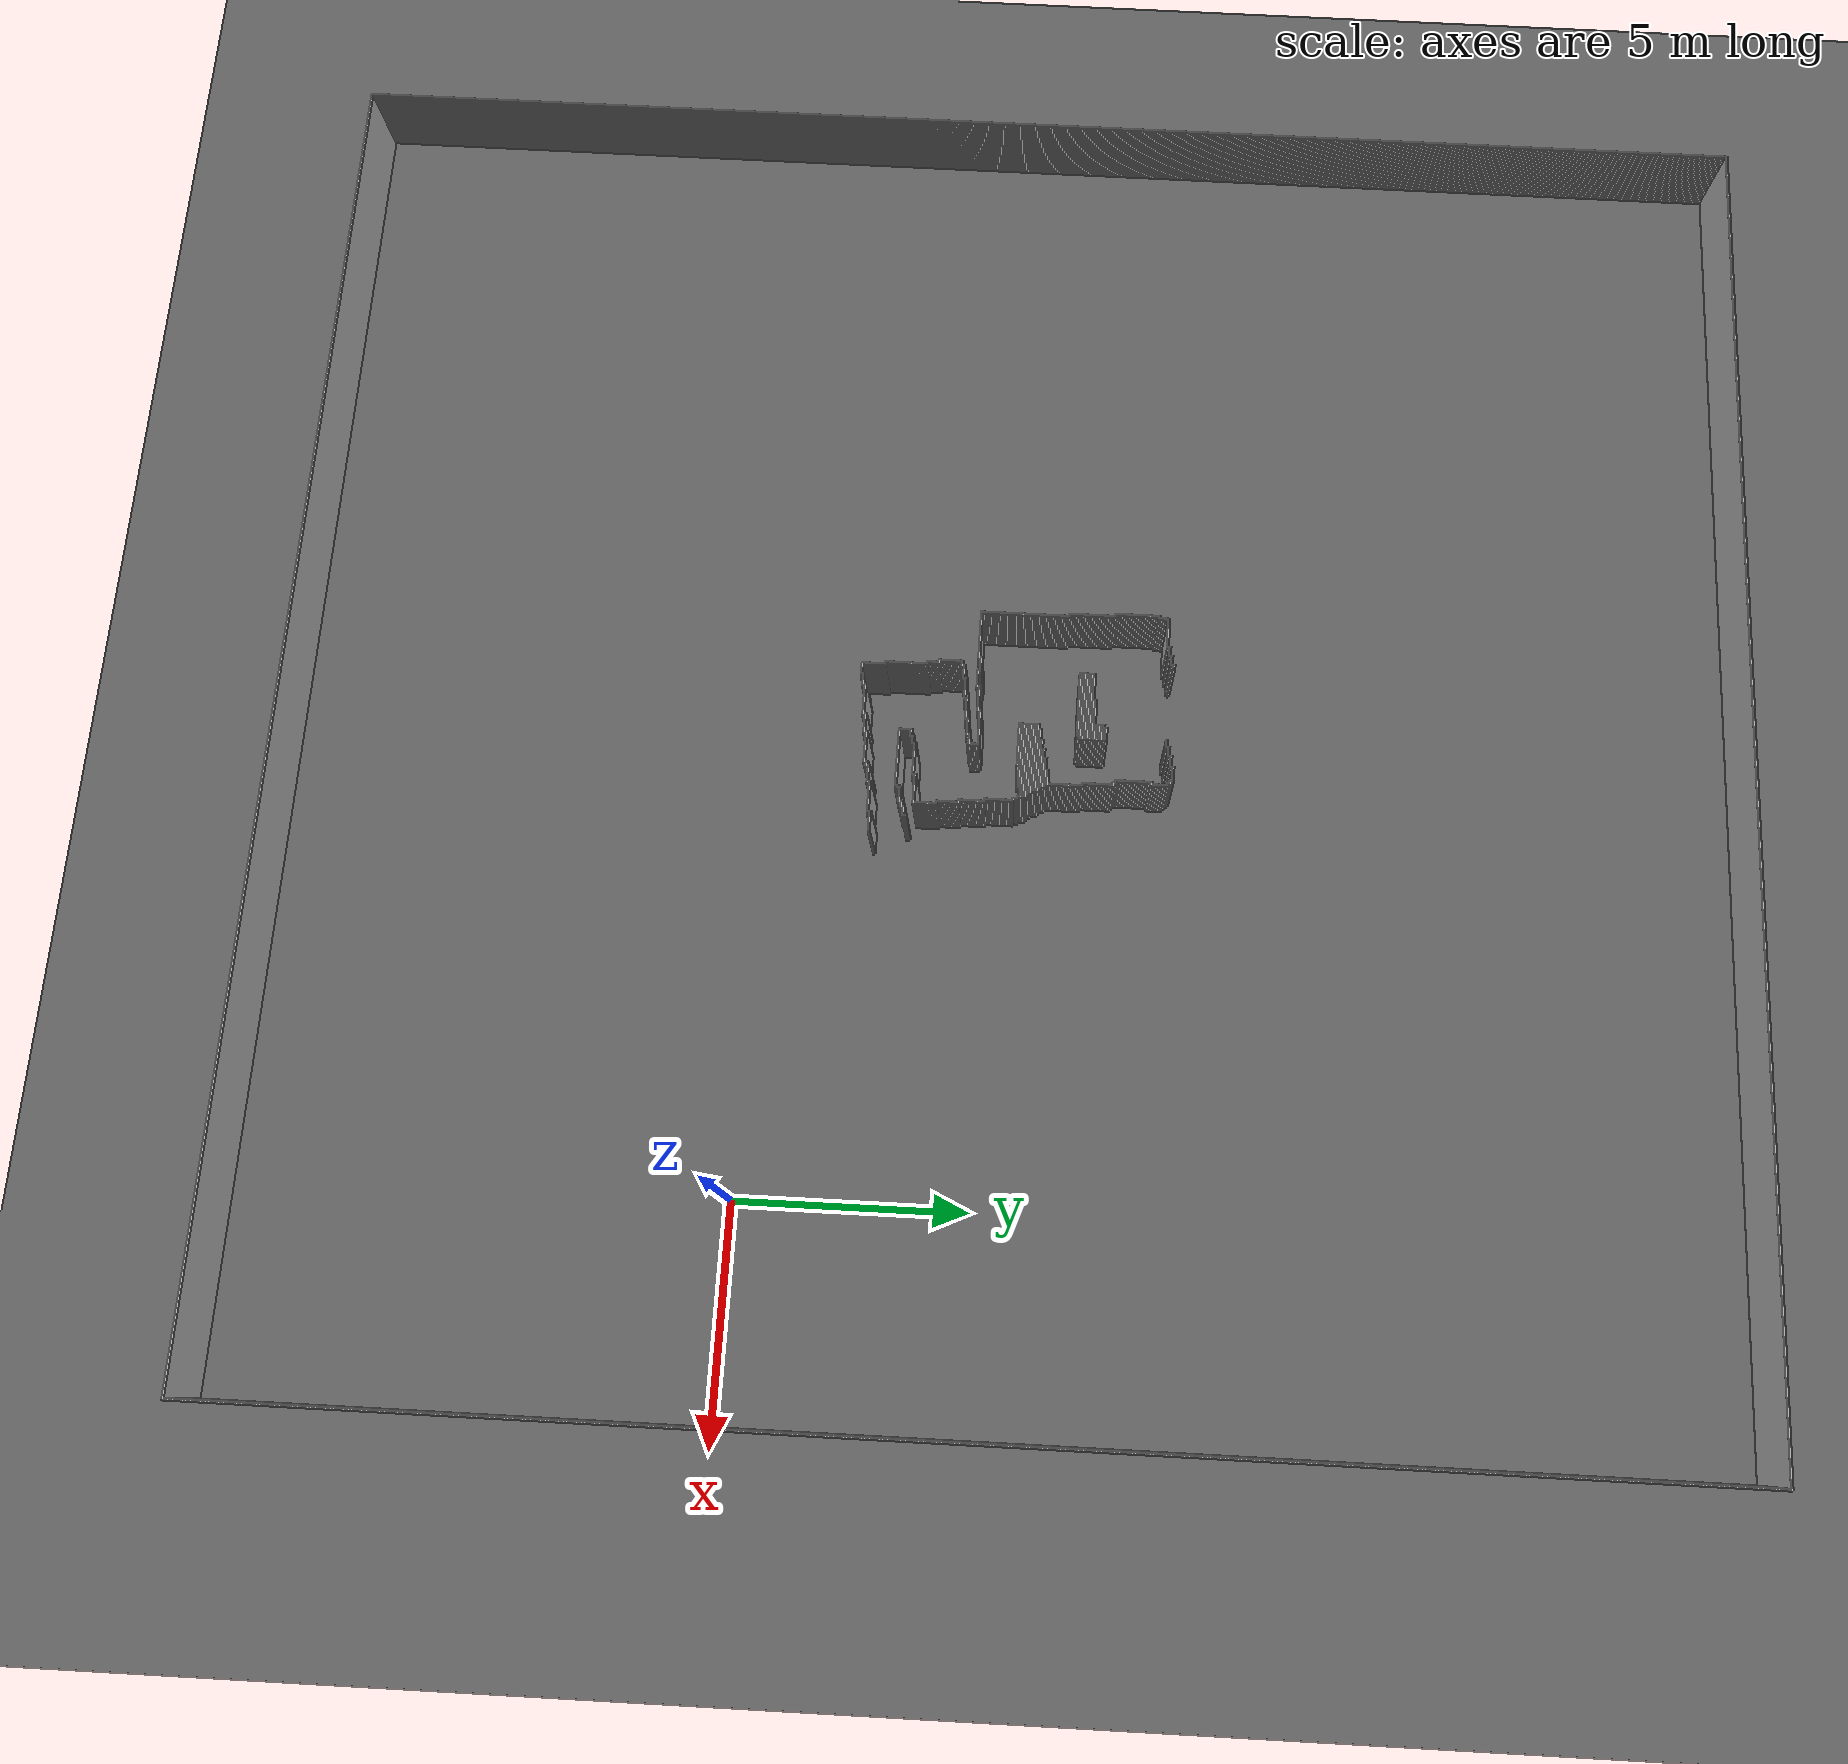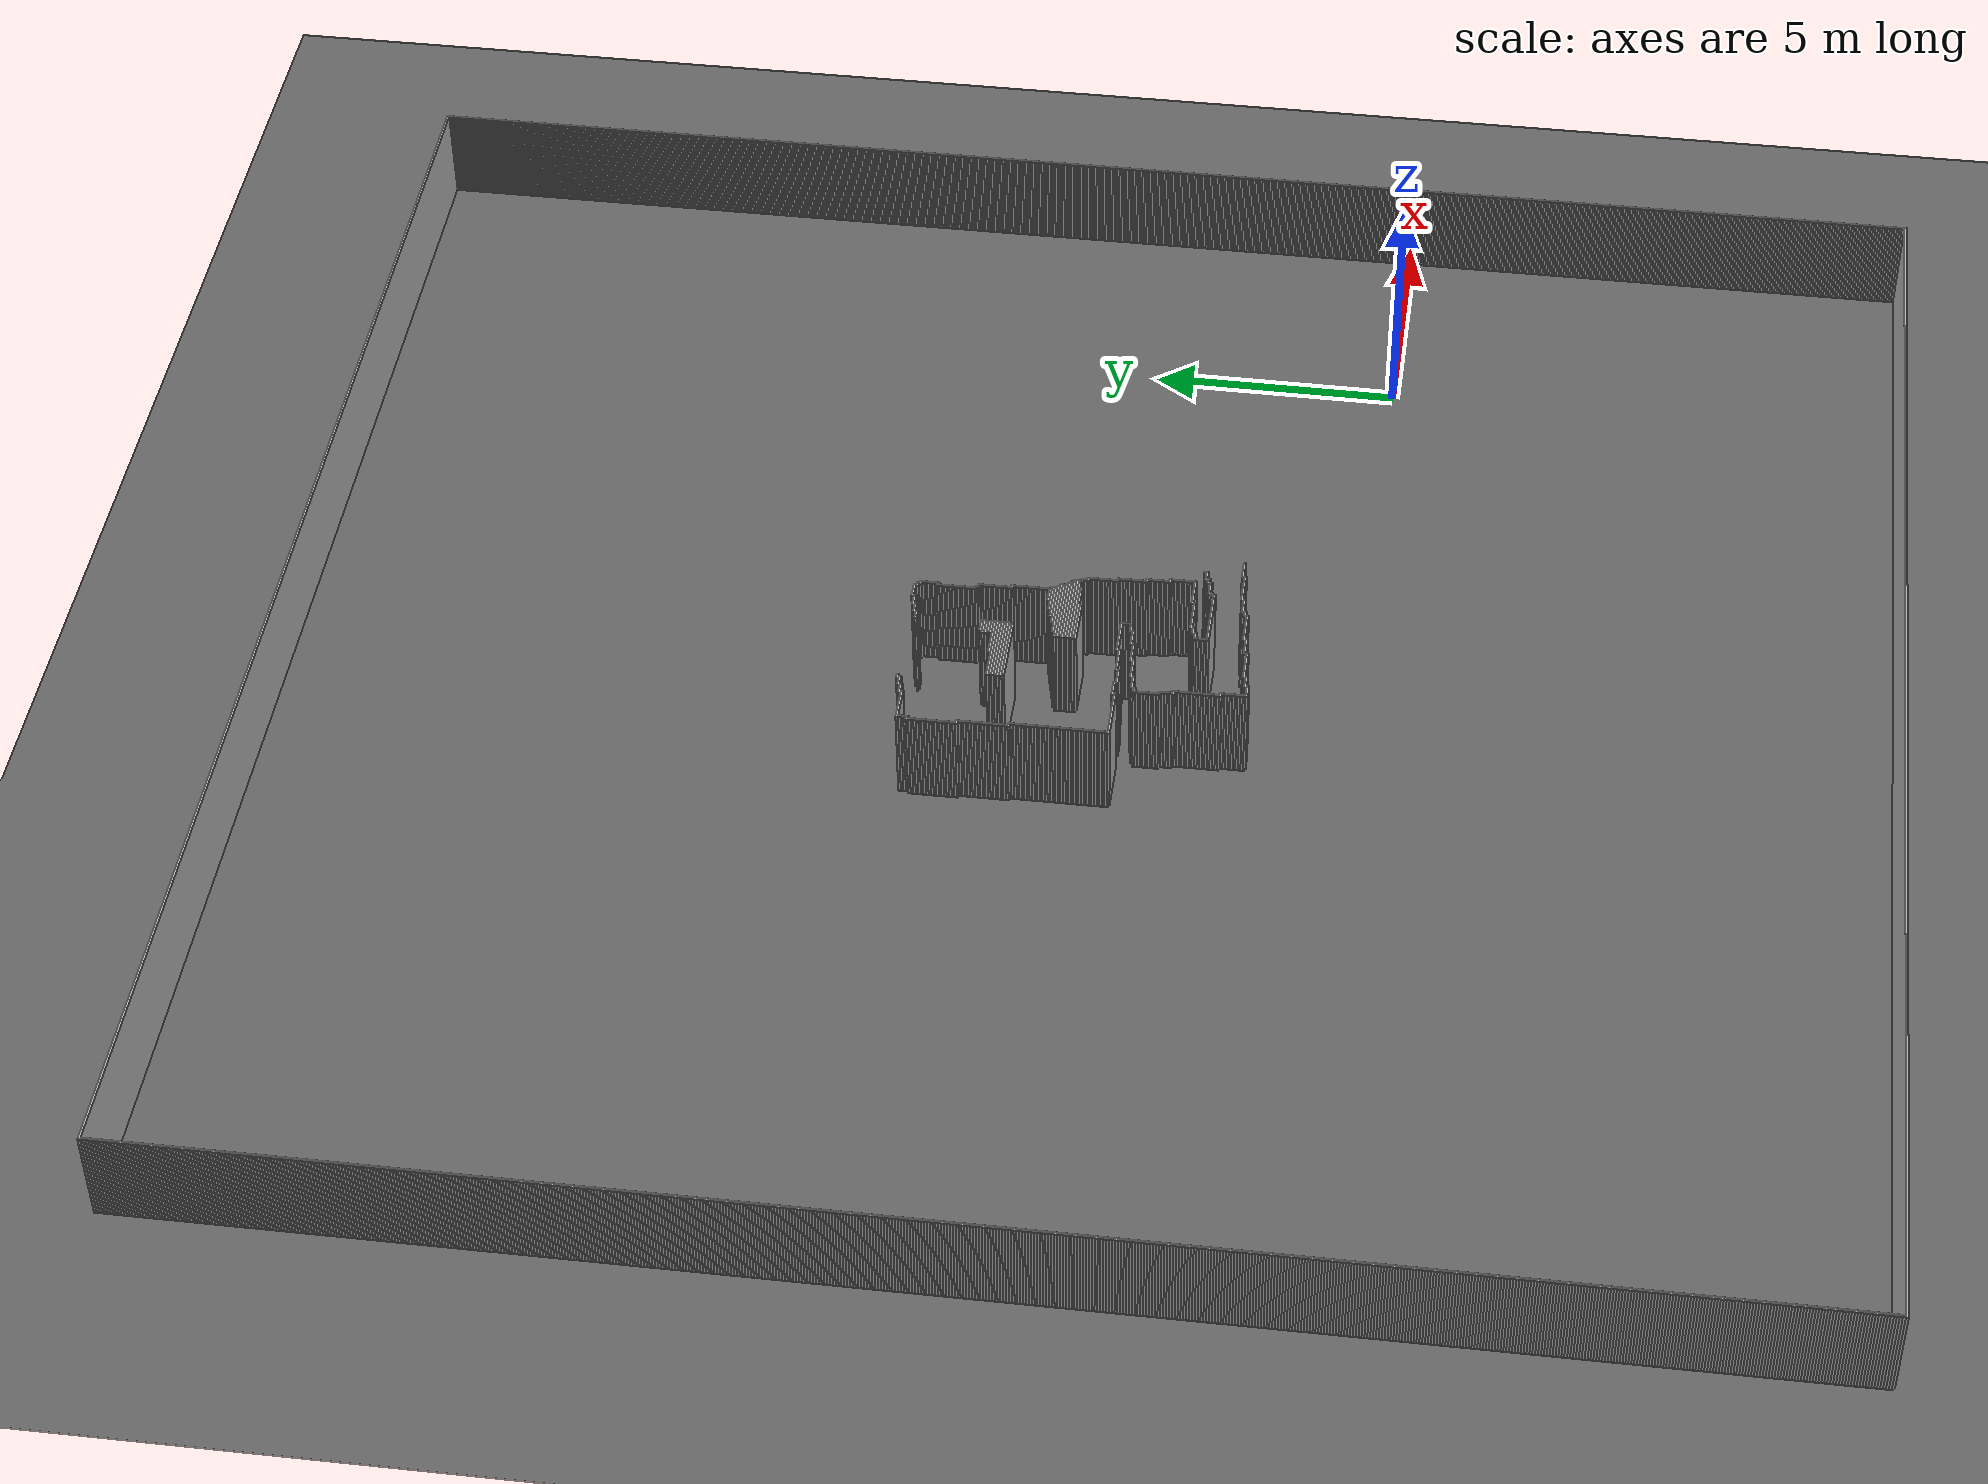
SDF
<?xml version="1.0"?>
<sdf version="1.8">
  <world name="real_map">
    <plugin filename="gz-sim-physics-system" name="gz::sim::systems::Physics"/>
    <plugin filename="gz-sim-sensors-system" name="gz::sim::systems::Sensors"><render_engine>ogre2</render_engine></plugin>
    <plugin filename="gz-sim-scene-broadcaster-system" name="gz::sim::systems::SceneBroadcaster"/>
    <plugin filename="gz-sim-user-commands-system" name="gz::sim::systems::UserCommands"/>
    <light type="directional" name="sun">
      <cast_shadows>true</cast_shadows><pose>0 0 10 0 0 0</pose>
      <diffuse>0.8 0.8 0.8 1</diffuse><specular>0.2 0.2 0.2 1</specular>
      <direction>-0.5 0.1 -0.9</direction>
    </light>
    <model name="ground"><static>true</static><link name="l">
      <collision name="c"><geometry><plane><normal>0 0 1</normal><size>100 100</size></plane></geometry></collision>
      <visual name="v"><geometry><plane><normal>0 0 1</normal><size>100 100</size></plane></geometry>
        <material><ambient>0.3 0.3 0.3 1</ambient><diffuse>0.4 0.4 0.4 1</diffuse></material></visual>
    </link></model>
    <model name="walls"><static>true</static>
      <link name="w0">
        <pose>-10.116 21.142 1.000 0 0 0</pose>
        <collision name="c"><geometry><box><size>29.350 0.050 2.000</size></box></geometry></collision>
        <visual name="v"><geometry><box><size>29.350 0.050 2.000</size></box></geometry>
          <material><ambient>0.7 0.7 0.7 1</ambient><diffuse>0.7 0.7 0.7 1</diffuse></material></visual>
      </link>
      <link name="w1">
        <pose>-24.766 21.092 1.000 0 0 0</pose>
        <collision name="c"><geometry><box><size>0.050 0.050 2.000</size></box></geometry></collision>
        <visual name="v"><geometry><box><size>0.050 0.050 2.000</size></box></geometry>
          <material><ambient>0.7 0.7 0.7 1</ambient><diffuse>0.7 0.7 0.7 1</diffuse></material></visual>
      </link>
      <link name="w2">
        <pose>4.534 21.092 1.000 0 0 0</pose>
        <collision name="c"><geometry><box><size>0.050 0.050 2.000</size></box></geometry></collision>
        <visual name="v"><geometry><box><size>0.050 0.050 2.000</size></box></geometry>
          <material><ambient>0.7 0.7 0.7 1</ambient><diffuse>0.7 0.7 0.7 1</diffuse></material></visual>
      </link>
      <link name="w3">
        <pose>-24.766 21.042 1.000 0 0 0</pose>
        <collision name="c"><geometry><box><size>0.050 0.050 2.000</size></box></geometry></collision>
        <visual name="v"><geometry><box><size>0.050 0.050 2.000</size></box></geometry>
          <material><ambient>0.7 0.7 0.7 1</ambient><diffuse>0.7 0.7 0.7 1</diffuse></material></visual>
      </link>
      <link name="w4">
        <pose>4.534 21.042 1.000 0 0 0</pose>
        <collision name="c"><geometry><box><size>0.050 0.050 2.000</size></box></geometry></collision>
        <visual name="v"><geometry><box><size>0.050 0.050 2.000</size></box></geometry>
          <material><ambient>0.7 0.7 0.7 1</ambient><diffuse>0.7 0.7 0.7 1</diffuse></material></visual>
      </link>
      <link name="w5">
        <pose>-24.766 20.992 1.000 0 0 0</pose>
        <collision name="c"><geometry><box><size>0.050 0.050 2.000</size></box></geometry></collision>
        <visual name="v"><geometry><box><size>0.050 0.050 2.000</size></box></geometry>
          <material><ambient>0.7 0.7 0.7 1</ambient><diffuse>0.7 0.7 0.7 1</diffuse></material></visual>
      </link>
      <link name="w6">
        <pose>4.534 20.992 1.000 0 0 0</pose>
        <collision name="c"><geometry><box><size>0.050 0.050 2.000</size></box></geometry></collision>
        <visual name="v"><geometry><box><size>0.050 0.050 2.000</size></box></geometry>
          <material><ambient>0.7 0.7 0.7 1</ambient><diffuse>0.7 0.7 0.7 1</diffuse></material></visual>
      </link>
      <link name="w7">
        <pose>-24.766 20.942 1.000 0 0 0</pose>
        <collision name="c"><geometry><box><size>0.050 0.050 2.000</size></box></geometry></collision>
        <visual name="v"><geometry><box><size>0.050 0.050 2.000</size></box></geometry>
          <material><ambient>0.7 0.7 0.7 1</ambient><diffuse>0.7 0.7 0.7 1</diffuse></material></visual>
      </link>
      <link name="w8">
        <pose>4.534 20.942 1.000 0 0 0</pose>
        <collision name="c"><geometry><box><size>0.050 0.050 2.000</size></box></geometry></collision>
        <visual name="v"><geometry><box><size>0.050 0.050 2.000</size></box></geometry>
          <material><ambient>0.7 0.7 0.7 1</ambient><diffuse>0.7 0.7 0.7 1</diffuse></material></visual>
      </link>
      <link name="w9">
        <pose>-24.766 20.892 1.000 0 0 0</pose>
        <collision name="c"><geometry><box><size>0.050 0.050 2.000</size></box></geometry></collision>
        <visual name="v"><geometry><box><size>0.050 0.050 2.000</size></box></geometry>
          <material><ambient>0.7 0.7 0.7 1</ambient><diffuse>0.7 0.7 0.7 1</diffuse></material></visual>
      </link>
      <link name="w10">
        <pose>4.534 20.892 1.000 0 0 0</pose>
        <collision name="c"><geometry><box><size>0.050 0.050 2.000</size></box></geometry></collision>
        <visual name="v"><geometry><box><size>0.050 0.050 2.000</size></box></geometry>
          <material><ambient>0.7 0.7 0.7 1</ambient><diffuse>0.7 0.7 0.7 1</diffuse></material></visual>
      </link>
      <link name="w11">
        <pose>-24.766 20.842 1.000 0 0 0</pose>
        <collision name="c"><geometry><box><size>0.050 0.050 2.000</size></box></geometry></collision>
        <visual name="v"><geometry><box><size>0.050 0.050 2.000</size></box></geometry>
          <material><ambient>0.7 0.7 0.7 1</ambient><diffuse>0.7 0.7 0.7 1</diffuse></material></visual>
      </link>
      <link name="w12">
        <pose>4.534 20.842 1.000 0 0 0</pose>
        <collision name="c"><geometry><box><size>0.050 0.050 2.000</size></box></geometry></collision>
        <visual name="v"><geometry><box><size>0.050 0.050 2.000</size></box></geometry>
          <material><ambient>0.7 0.7 0.7 1</ambient><diffuse>0.7 0.7 0.7 1</diffuse></material></visual>
      </link>
      <link name="w13">
        <pose>-24.766 20.792 1.000 0 0 0</pose>
        <collision name="c"><geometry><box><size>0.050 0.050 2.000</size></box></geometry></collision>
        <visual name="v"><geometry><box><size>0.050 0.050 2.000</size></box></geometry>
          <material><ambient>0.7 0.7 0.7 1</ambient><diffuse>0.7 0.7 0.7 1</diffuse></material></visual>
      </link>
      <link name="w14">
        <pose>4.534 20.792 1.000 0 0 0</pose>
        <collision name="c"><geometry><box><size>0.050 0.050 2.000</size></box></geometry></collision>
        <visual name="v"><geometry><box><size>0.050 0.050 2.000</size></box></geometry>
          <material><ambient>0.7 0.7 0.7 1</ambient><diffuse>0.7 0.7 0.7 1</diffuse></material></visual>
      </link>
      <link name="w15">
        <pose>-24.766 20.742 1.000 0 0 0</pose>
        <collision name="c"><geometry><box><size>0.050 0.050 2.000</size></box></geometry></collision>
        <visual name="v"><geometry><box><size>0.050 0.050 2.000</size></box></geometry>
          <material><ambient>0.7 0.7 0.7 1</ambient><diffuse>0.7 0.7 0.7 1</diffuse></material></visual>
      </link>
      <link name="w16">
        <pose>4.534 20.742 1.000 0 0 0</pose>
        <collision name="c"><geometry><box><size>0.050 0.050 2.000</size></box></geometry></collision>
        <visual name="v"><geometry><box><size>0.050 0.050 2.000</size></box></geometry>
          <material><ambient>0.7 0.7 0.7 1</ambient><diffuse>0.7 0.7 0.7 1</diffuse></material></visual>
      </link>
      <link name="w17">
        <pose>-24.766 20.692 1.000 0 0 0</pose>
        <collision name="c"><geometry><box><size>0.050 0.050 2.000</size></box></geometry></collision>
        <visual name="v"><geometry><box><size>0.050 0.050 2.000</size></box></geometry>
          <material><ambient>0.7 0.7 0.7 1</ambient><diffuse>0.7 0.7 0.7 1</diffuse></material></visual>
      </link>
      <link name="w18">
        <pose>4.534 20.692 1.000 0 0 0</pose>
        <collision name="c"><geometry><box><size>0.050 0.050 2.000</size></box></geometry></collision>
        <visual name="v"><geometry><box><size>0.050 0.050 2.000</size></box></geometry>
          <material><ambient>0.7 0.7 0.7 1</ambient><diffuse>0.7 0.7 0.7 1</diffuse></material></visual>
      </link>
      <link name="w19">
        <pose>-24.766 20.642 1.000 0 0 0</pose>
        <collision name="c"><geometry><box><size>0.050 0.050 2.000</size></box></geometry></collision>
        <visual name="v"><geometry><box><size>0.050 0.050 2.000</size></box></geometry>
          <material><ambient>0.7 0.7 0.7 1</ambient><diffuse>0.7 0.7 0.7 1</diffuse></material></visual>
      </link>
      <link name="w20">
        <pose>4.534 20.642 1.000 0 0 0</pose>
        <collision name="c"><geometry><box><size>0.050 0.050 2.000</size></box></geometry></collision>
        <visual name="v"><geometry><box><size>0.050 0.050 2.000</size></box></geometry>
          <material><ambient>0.7 0.7 0.7 1</ambient><diffuse>0.7 0.7 0.7 1</diffuse></material></visual>
      </link>
      <link name="w21">
        <pose>-24.766 20.592 1.000 0 0 0</pose>
        <collision name="c"><geometry><box><size>0.050 0.050 2.000</size></box></geometry></collision>
        <visual name="v"><geometry><box><size>0.050 0.050 2.000</size></box></geometry>
          <material><ambient>0.7 0.7 0.7 1</ambient><diffuse>0.7 0.7 0.7 1</diffuse></material></visual>
      </link>
      <link name="w22">
        <pose>4.534 20.592 1.000 0 0 0</pose>
        <collision name="c"><geometry><box><size>0.050 0.050 2.000</size></box></geometry></collision>
        <visual name="v"><geometry><box><size>0.050 0.050 2.000</size></box></geometry>
          <material><ambient>0.7 0.7 0.7 1</ambient><diffuse>0.7 0.7 0.7 1</diffuse></material></visual>
      </link>
      <link name="w23">
        <pose>-24.766 20.542 1.000 0 0 0</pose>
        <collision name="c"><geometry><box><size>0.050 0.050 2.000</size></box></geometry></collision>
        <visual name="v"><geometry><box><size>0.050 0.050 2.000</size></box></geometry>
          <material><ambient>0.7 0.7 0.7 1</ambient><diffuse>0.7 0.7 0.7 1</diffuse></material></visual>
      </link>
      <link name="w24">
        <pose>4.534 20.542 1.000 0 0 0</pose>
        <collision name="c"><geometry><box><size>0.050 0.050 2.000</size></box></geometry></collision>
        <visual name="v"><geometry><box><size>0.050 0.050 2.000</size></box></geometry>
          <material><ambient>0.7 0.7 0.7 1</ambient><diffuse>0.7 0.7 0.7 1</diffuse></material></visual>
      </link>
      <link name="w25">
        <pose>-24.766 20.492 1.000 0 0 0</pose>
        <collision name="c"><geometry><box><size>0.050 0.050 2.000</size></box></geometry></collision>
        <visual name="v"><geometry><box><size>0.050 0.050 2.000</size></box></geometry>
          <material><ambient>0.7 0.7 0.7 1</ambient><diffuse>0.7 0.7 0.7 1</diffuse></material></visual>
      </link>
      <link name="w26">
        <pose>4.534 20.492 1.000 0 0 0</pose>
        <collision name="c"><geometry><box><size>0.050 0.050 2.000</size></box></geometry></collision>
        <visual name="v"><geometry><box><size>0.050 0.050 2.000</size></box></geometry>
          <material><ambient>0.7 0.7 0.7 1</ambient><diffuse>0.7 0.7 0.7 1</diffuse></material></visual>
      </link>
      <link name="w27">
        <pose>-24.766 20.442 1.000 0 0 0</pose>
        <collision name="c"><geometry><box><size>0.050 0.050 2.000</size></box></geometry></collision>
        <visual name="v"><geometry><box><size>0.050 0.050 2.000</size></box></geometry>
          <material><ambient>0.7 0.7 0.7 1</ambient><diffuse>0.7 0.7 0.7 1</diffuse></material></visual>
      </link>
      <link name="w28">
        <pose>4.534 20.442 1.000 0 0 0</pose>
        <collision name="c"><geometry><box><size>0.050 0.050 2.000</size></box></geometry></collision>
        <visual name="v"><geometry><box><size>0.050 0.050 2.000</size></box></geometry>
          <material><ambient>0.7 0.7 0.7 1</ambient><diffuse>0.7 0.7 0.7 1</diffuse></material></visual>
      </link>
      <link name="w29">
        <pose>-24.766 20.392 1.000 0 0 0</pose>
        <collision name="c"><geometry><box><size>0.050 0.050 2.000</size></box></geometry></collision>
        <visual name="v"><geometry><box><size>0.050 0.050 2.000</size></box></geometry>
          <material><ambient>0.7 0.7 0.7 1</ambient><diffuse>0.7 0.7 0.7 1</diffuse></material></visual>
      </link>
      <link name="w30">
        <pose>4.534 20.392 1.000 0 0 0</pose>
        <collision name="c"><geometry><box><size>0.050 0.050 2.000</size></box></geometry></collision>
        <visual name="v"><geometry><box><size>0.050 0.050 2.000</size></box></geometry>
          <material><ambient>0.7 0.7 0.7 1</ambient><diffuse>0.7 0.7 0.7 1</diffuse></material></visual>
      </link>
      <link name="w31">
        <pose>-24.766 20.342 1.000 0 0 0</pose>
        <collision name="c"><geometry><box><size>0.050 0.050 2.000</size></box></geometry></collision>
        <visual name="v"><geometry><box><size>0.050 0.050 2.000</size></box></geometry>
          <material><ambient>0.7 0.7 0.7 1</ambient><diffuse>0.7 0.7 0.7 1</diffuse></material></visual>
      </link>
      <link name="w32">
        <pose>4.534 20.342 1.000 0 0 0</pose>
        <collision name="c"><geometry><box><size>0.050 0.050 2.000</size></box></geometry></collision>
        <visual name="v"><geometry><box><size>0.050 0.050 2.000</size></box></geometry>
          <material><ambient>0.7 0.7 0.7 1</ambient><diffuse>0.7 0.7 0.7 1</diffuse></material></visual>
      </link>
      <link name="w33">
        <pose>-24.766 20.292 1.000 0 0 0</pose>
        <collision name="c"><geometry><box><size>0.050 0.050 2.000</size></box></geometry></collision>
        <visual name="v"><geometry><box><size>0.050 0.050 2.000</size></box></geometry>
          <material><ambient>0.7 0.7 0.7 1</ambient><diffuse>0.7 0.7 0.7 1</diffuse></material></visual>
      </link>
      <link name="w34">
        <pose>4.534 20.292 1.000 0 0 0</pose>
        <collision name="c"><geometry><box><size>0.050 0.050 2.000</size></box></geometry></collision>
        <visual name="v"><geometry><box><size>0.050 0.050 2.000</size></box></geometry>
          <material><ambient>0.7 0.7 0.7 1</ambient><diffuse>0.7 0.7 0.7 1</diffuse></material></visual>
      </link>
      <link name="w35">
        <pose>-24.766 20.242 1.000 0 0 0</pose>
        <collision name="c"><geometry><box><size>0.050 0.050 2.000</size></box></geometry></collision>
        <visual name="v"><geometry><box><size>0.050 0.050 2.000</size></box></geometry>
          <material><ambient>0.7 0.7 0.7 1</ambient><diffuse>0.7 0.7 0.7 1</diffuse></material></visual>
      </link>
      <link name="w36">
        <pose>4.534 20.242 1.000 0 0 0</pose>
        <collision name="c"><geometry><box><size>0.050 0.050 2.000</size></box></geometry></collision>
        <visual name="v"><geometry><box><size>0.050 0.050 2.000</size></box></geometry>
          <material><ambient>0.7 0.7 0.7 1</ambient><diffuse>0.7 0.7 0.7 1</diffuse></material></visual>
      </link>
      <link name="w37">
        <pose>-24.766 20.192 1.000 0 0 0</pose>
        <collision name="c"><geometry><box><size>0.050 0.050 2.000</size></box></geometry></collision>
        <visual name="v"><geometry><box><size>0.050 0.050 2.000</size></box></geometry>
          <material><ambient>0.7 0.7 0.7 1</ambient><diffuse>0.7 0.7 0.7 1</diffuse></material></visual>
      </link>
      <link name="w38">
        <pose>4.534 20.192 1.000 0 0 0</pose>
        <collision name="c"><geometry><box><size>0.050 0.050 2.000</size></box></geometry></collision>
        <visual name="v"><geometry><box><size>0.050 0.050 2.000</size></box></geometry>
          <material><ambient>0.7 0.7 0.7 1</ambient><diffuse>0.7 0.7 0.7 1</diffuse></material></visual>
      </link>
      <link name="w39">
        <pose>-24.766 20.142 1.000 0 0 0</pose>
        <collision name="c"><geometry><box><size>0.050 0.050 2.000</size></box></geometry></collision>
        <visual name="v"><geometry><box><size>0.050 0.050 2.000</size></box></geometry>
          <material><ambient>0.7 0.7 0.7 1</ambient><diffuse>0.7 0.7 0.7 1</diffuse></material></visual>
      </link>
      <link name="w40">
        <pose>4.534 20.142 1.000 0 0 0</pose>
        <collision name="c"><geometry><box><size>0.050 0.050 2.000</size></box></geometry></collision>
        <visual name="v"><geometry><box><size>0.050 0.050 2.000</size></box></geometry>
          <material><ambient>0.7 0.7 0.7 1</ambient><diffuse>0.7 0.7 0.7 1</diffuse></material></visual>
      </link>
      <link name="w41">
        <pose>-24.766 20.092 1.000 0 0 0</pose>
        <collision name="c"><geometry><box><size>0.050 0.050 2.000</size></box></geometry></collision>
        <visual name="v"><geometry><box><size>0.050 0.050 2.000</size></box></geometry>
          <material><ambient>0.7 0.7 0.7 1</ambient><diffuse>0.7 0.7 0.7 1</diffuse></material></visual>
      </link>
      <link name="w42">
        <pose>4.534 20.092 1.000 0 0 0</pose>
        <collision name="c"><geometry><box><size>0.050 0.050 2.000</size></box></geometry></collision>
        <visual name="v"><geometry><box><size>0.050 0.050 2.000</size></box></geometry>
          <material><ambient>0.7 0.7 0.7 1</ambient><diffuse>0.7 0.7 0.7 1</diffuse></material></visual>
      </link>
      <link name="w43">
        <pose>-24.766 20.042 1.000 0 0 0</pose>
        <collision name="c"><geometry><box><size>0.050 0.050 2.000</size></box></geometry></collision>
        <visual name="v"><geometry><box><size>0.050 0.050 2.000</size></box></geometry>
          <material><ambient>0.7 0.7 0.7 1</ambient><diffuse>0.7 0.7 0.7 1</diffuse></material></visual>
      </link>
      <link name="w44">
        <pose>4.534 20.042 1.000 0 0 0</pose>
        <collision name="c"><geometry><box><size>0.050 0.050 2.000</size></box></geometry></collision>
        <visual name="v"><geometry><box><size>0.050 0.050 2.000</size></box></geometry>
          <material><ambient>0.7 0.7 0.7 1</ambient><diffuse>0.7 0.7 0.7 1</diffuse></material></visual>
      </link>
      <link name="w45">
        <pose>-24.766 19.992 1.000 0 0 0</pose>
        <collision name="c"><geometry><box><size>0.050 0.050 2.000</size></box></geometry></collision>
        <visual name="v"><geometry><box><size>0.050 0.050 2.000</size></box></geometry>
          <material><ambient>0.7 0.7 0.7 1</ambient><diffuse>0.7 0.7 0.7 1</diffuse></material></visual>
      </link>
      <link name="w46">
        <pose>4.534 19.992 1.000 0 0 0</pose>
        <collision name="c"><geometry><box><size>0.050 0.050 2.000</size></box></geometry></collision>
        <visual name="v"><geometry><box><size>0.050 0.050 2.000</size></box></geometry>
          <material><ambient>0.7 0.7 0.7 1</ambient><diffuse>0.7 0.7 0.7 1</diffuse></material></visual>
      </link>
      <link name="w47">
        <pose>-24.766 19.942 1.000 0 0 0</pose>
        <collision name="c"><geometry><box><size>0.050 0.050 2.000</size></box></geometry></collision>
        <visual name="v"><geometry><box><size>0.050 0.050 2.000</size></box></geometry>
          <material><ambient>0.7 0.7 0.7 1</ambient><diffuse>0.7 0.7 0.7 1</diffuse></material></visual>
      </link>
      <link name="w48">
        <pose>4.534 19.942 1.000 0 0 0</pose>
        <collision name="c"><geometry><box><size>0.050 0.050 2.000</size></box></geometry></collision>
        <visual name="v"><geometry><box><size>0.050 0.050 2.000</size></box></geometry>
          <material><ambient>0.7 0.7 0.7 1</ambient><diffuse>0.7 0.7 0.7 1</diffuse></material></visual>
      </link>
      <link name="w49">
        <pose>-24.766 19.892 1.000 0 0 0</pose>
        <collision name="c"><geometry><box><size>0.050 0.050 2.000</size></box></geometry></collision>
        <visual name="v"><geometry><box><size>0.050 0.050 2.000</size></box></geometry>
          <material><ambient>0.7 0.7 0.7 1</ambient><diffuse>0.7 0.7 0.7 1</diffuse></material></visual>
      </link>
      <link name="w50">
        <pose>4.534 19.892 1.000 0 0 0</pose>
        <collision name="c"><geometry><box><size>0.050 0.050 2.000</size></box></geometry></collision>
        <visual name="v"><geometry><box><size>0.050 0.050 2.000</size></box></geometry>
          <material><ambient>0.7 0.7 0.7 1</ambient><diffuse>0.7 0.7 0.7 1</diffuse></material></visual>
      </link>
      <link name="w51">
        <pose>-24.766 19.842 1.000 0 0 0</pose>
        <collision name="c"><geometry><box><size>0.050 0.050 2.000</size></box></geometry></collision>
        <visual name="v"><geometry><box><size>0.050 0.050 2.000</size></box></geometry>
          <material><ambient>0.7 0.7 0.7 1</ambient><diffuse>0.7 0.7 0.7 1</diffuse></material></visual>
      </link>
      <link name="w52">
        <pose>4.534 19.842 1.000 0 0 0</pose>
        <collision name="c"><geometry><box><size>0.050 0.050 2.000</size></box></geometry></collision>
        <visual name="v"><geometry><box><size>0.050 0.050 2.000</size></box></geometry>
          <material><ambient>0.7 0.7 0.7 1</ambient><diffuse>0.7 0.7 0.7 1</diffuse></material></visual>
      </link>
      <link name="w53">
        <pose>-24.766 19.792 1.000 0 0 0</pose>
        <collision name="c"><geometry><box><size>0.050 0.050 2.000</size></box></geometry></collision>
        <visual name="v"><geometry><box><size>0.050 0.050 2.000</size></box></geometry>
          <material><ambient>0.7 0.7 0.7 1</ambient><diffuse>0.7 0.7 0.7 1</diffuse></material></visual>
      </link>
      <link name="w54">
        <pose>4.534 19.792 1.000 0 0 0</pose>
        <collision name="c"><geometry><box><size>0.050 0.050 2.000</size></box></geometry></collision>
        <visual name="v"><geometry><box><size>0.050 0.050 2.000</size></box></geometry>
          <material><ambient>0.7 0.7 0.7 1</ambient><diffuse>0.7 0.7 0.7 1</diffuse></material></visual>
      </link>
      <link name="w55">
        <pose>-24.766 19.742 1.000 0 0 0</pose>
        <collision name="c"><geometry><box><size>0.050 0.050 2.000</size></box></geometry></collision>
        <visual name="v"><geometry><box><size>0.050 0.050 2.000</size></box></geometry>
          <material><ambient>0.7 0.7 0.7 1</ambient><diffuse>0.7 0.7 0.7 1</diffuse></material></visual>
      </link>
      <link name="w56">
        <pose>4.534 19.742 1.000 0 0 0</pose>
        <collision name="c"><geometry><box><size>0.050 0.050 2.000</size></box></geometry></collision>
        <visual name="v"><geometry><box><size>0.050 0.050 2.000</size></box></geometry>
          <material><ambient>0.7 0.7 0.7 1</ambient><diffuse>0.7 0.7 0.7 1</diffuse></material></visual>
      </link>
      <link name="w57">
        <pose>-24.766 19.692 1.000 0 0 0</pose>
        <collision name="c"><geometry><box><size>0.050 0.050 2.000</size></box></geometry></collision>
        <visual name="v"><geometry><box><size>0.050 0.050 2.000</size></box></geometry>
          <material><ambient>0.7 0.7 0.7 1</ambient><diffuse>0.7 0.7 0.7 1</diffuse></material></visual>
      </link>
      <link name="w58">
        <pose>4.534 19.692 1.000 0 0 0</pose>
        <collision name="c"><geometry><box><size>0.050 0.050 2.000</size></box></geometry></collision>
        <visual name="v"><geometry><box><size>0.050 0.050 2.000</size></box></geometry>
          <material><ambient>0.7 0.7 0.7 1</ambient><diffuse>0.7 0.7 0.7 1</diffuse></material></visual>
      </link>
      <link name="w59">
        <pose>-24.766 19.642 1.000 0 0 0</pose>
        <collision name="c"><geometry><box><size>0.050 0.050 2.000</size></box></geometry></collision>
        <visual name="v"><geometry><box><size>0.050 0.050 2.000</size></box></geometry>
          <material><ambient>0.7 0.7 0.7 1</ambient><diffuse>0.7 0.7 0.7 1</diffuse></material></visual>
      </link>
      <link name="w60">
        <pose>4.534 19.642 1.000 0 0 0</pose>
        <collision name="c"><geometry><box><size>0.050 0.050 2.000</size></box></geometry></collision>
        <visual name="v"><geometry><box><size>0.050 0.050 2.000</size></box></geometry>
          <material><ambient>0.7 0.7 0.7 1</ambient><diffuse>0.7 0.7 0.7 1</diffuse></material></visual>
      </link>
      <link name="w61">
        <pose>-24.766 19.592 1.000 0 0 0</pose>
        <collision name="c"><geometry><box><size>0.050 0.050 2.000</size></box></geometry></collision>
        <visual name="v"><geometry><box><size>0.050 0.050 2.000</size></box></geometry>
          <material><ambient>0.7 0.7 0.7 1</ambient><diffuse>0.7 0.7 0.7 1</diffuse></material></visual>
      </link>
      <link name="w62">
        <pose>4.534 19.592 1.000 0 0 0</pose>
        <collision name="c"><geometry><box><size>0.050 0.050 2.000</size></box></geometry></collision>
        <visual name="v"><geometry><box><size>0.050 0.050 2.000</size></box></geometry>
          <material><ambient>0.7 0.7 0.7 1</ambient><diffuse>0.7 0.7 0.7 1</diffuse></material></visual>
      </link>
      <link name="w63">
        <pose>-24.766 19.542 1.000 0 0 0</pose>
        <collision name="c"><geometry><box><size>0.050 0.050 2.000</size></box></geometry></collision>
        <visual name="v"><geometry><box><size>0.050 0.050 2.000</size></box></geometry>
          <material><ambient>0.7 0.7 0.7 1</ambient><diffuse>0.7 0.7 0.7 1</diffuse></material></visual>
      </link>
      <link name="w64">
        <pose>4.534 19.542 1.000 0 0 0</pose>
        <collision name="c"><geometry><box><size>0.050 0.050 2.000</size></box></geometry></collision>
        <visual name="v"><geometry><box><size>0.050 0.050 2.000</size></box></geometry>
          <material><ambient>0.7 0.7 0.7 1</ambient><diffuse>0.7 0.7 0.7 1</diffuse></material></visual>
      </link>
      <link name="w65">
        <pose>-24.766 19.492 1.000 0 0 0</pose>
        <collision name="c"><geometry><box><size>0.050 0.050 2.000</size></box></geometry></collision>
        <visual name="v"><geometry><box><size>0.050 0.050 2.000</size></box></geometry>
          <material><ambient>0.7 0.7 0.7 1</ambient><diffuse>0.7 0.7 0.7 1</diffuse></material></visual>
      </link>
      <link name="w66">
        <pose>4.534 19.492 1.000 0 0 0</pose>
        <collision name="c"><geometry><box><size>0.050 0.050 2.000</size></box></geometry></collision>
        <visual name="v"><geometry><box><size>0.050 0.050 2.000</size></box></geometry>
          <material><ambient>0.7 0.7 0.7 1</ambient><diffuse>0.7 0.7 0.7 1</diffuse></material></visual>
      </link>
      <link name="w67">
        <pose>-24.766 19.442 1.000 0 0 0</pose>
        <collision name="c"><geometry><box><size>0.050 0.050 2.000</size></box></geometry></collision>
        <visual name="v"><geometry><box><size>0.050 0.050 2.000</size></box></geometry>
          <material><ambient>0.7 0.7 0.7 1</ambient><diffuse>0.7 0.7 0.7 1</diffuse></material></visual>
      </link>
      <link name="w68">
        <pose>4.534 19.442 1.000 0 0 0</pose>
        <collision name="c"><geometry><box><size>0.050 0.050 2.000</size></box></geometry></collision>
        <visual name="v"><geometry><box><size>0.050 0.050 2.000</size></box></geometry>
          <material><ambient>0.7 0.7 0.7 1</ambient><diffuse>0.7 0.7 0.7 1</diffuse></material></visual>
      </link>
      <link name="w69">
        <pose>-24.766 19.392 1.000 0 0 0</pose>
        <collision name="c"><geometry><box><size>0.050 0.050 2.000</size></box></geometry></collision>
        <visual name="v"><geometry><box><size>0.050 0.050 2.000</size></box></geometry>
          <material><ambient>0.7 0.7 0.7 1</ambient><diffuse>0.7 0.7 0.7 1</diffuse></material></visual>
      </link>
      <link name="w70">
        <pose>4.534 19.392 1.000 0 0 0</pose>
        <collision name="c"><geometry><box><size>0.050 0.050 2.000</size></box></geometry></collision>
        <visual name="v"><geometry><box><size>0.050 0.050 2.000</size></box></geometry>
          <material><ambient>0.7 0.7 0.7 1</ambient><diffuse>0.7 0.7 0.7 1</diffuse></material></visual>
      </link>
      <link name="w71">
        <pose>-24.766 19.342 1.000 0 0 0</pose>
        <collision name="c"><geometry><box><size>0.050 0.050 2.000</size></box></geometry></collision>
        <visual name="v"><geometry><box><size>0.050 0.050 2.000</size></box></geometry>
          <material><ambient>0.7 0.7 0.7 1</ambient><diffuse>0.7 0.7 0.7 1</diffuse></material></visual>
      </link>
      <link name="w72">
        <pose>4.534 19.342 1.000 0 0 0</pose>
        <collision name="c"><geometry><box><size>0.050 0.050 2.000</size></box></geometry></collision>
        <visual name="v"><geometry><box><size>0.050 0.050 2.000</size></box></geometry>
          <material><ambient>0.7 0.7 0.7 1</ambient><diffuse>0.7 0.7 0.7 1</diffuse></material></visual>
      </link>
      <link name="w73">
        <pose>-24.766 19.292 1.000 0 0 0</pose>
        <collision name="c"><geometry><box><size>0.050 0.050 2.000</size></box></geometry></collision>
        <visual name="v"><geometry><box><size>0.050 0.050 2.000</size></box></geometry>
          <material><ambient>0.7 0.7 0.7 1</ambient><diffuse>0.7 0.7 0.7 1</diffuse></material></visual>
      </link>
      <link name="w74">
        <pose>4.534 19.292 1.000 0 0 0</pose>
        <collision name="c"><geometry><box><size>0.050 0.050 2.000</size></box></geometry></collision>
        <visual name="v"><geometry><box><size>0.050 0.050 2.000</size></box></geometry>
          <material><ambient>0.7 0.7 0.7 1</ambient><diffuse>0.7 0.7 0.7 1</diffuse></material></visual>
      </link>
      <link name="w75">
        <pose>-24.766 19.242 1.000 0 0 0</pose>
        <collision name="c"><geometry><box><size>0.050 0.050 2.000</size></box></geometry></collision>
        <visual name="v"><geometry><box><size>0.050 0.050 2.000</size></box></geometry>
          <material><ambient>0.7 0.7 0.7 1</ambient><diffuse>0.7 0.7 0.7 1</diffuse></material></visual>
      </link>
      <link name="w76">
        <pose>4.534 19.242 1.000 0 0 0</pose>
        <collision name="c"><geometry><box><size>0.050 0.050 2.000</size></box></geometry></collision>
        <visual name="v"><geometry><box><size>0.050 0.050 2.000</size></box></geometry>
          <material><ambient>0.7 0.7 0.7 1</ambient><diffuse>0.7 0.7 0.7 1</diffuse></material></visual>
      </link>
      <link name="w77">
        <pose>-24.766 19.192 1.000 0 0 0</pose>
        <collision name="c"><geometry><box><size>0.050 0.050 2.000</size></box></geometry></collision>
        <visual name="v"><geometry><box><size>0.050 0.050 2.000</size></box></geometry>
          <material><ambient>0.7 0.7 0.7 1</ambient><diffuse>0.7 0.7 0.7 1</diffuse></material></visual>
      </link>
      <link name="w78">
        <pose>4.534 19.192 1.000 0 0 0</pose>
        <collision name="c"><geometry><box><size>0.050 0.050 2.000</size></box></geometry></collision>
        <visual name="v"><geometry><box><size>0.050 0.050 2.000</size></box></geometry>
          <material><ambient>0.7 0.7 0.7 1</ambient><diffuse>0.7 0.7 0.7 1</diffuse></material></visual>
      </link>
      <link name="w79">
        <pose>-24.766 19.142 1.000 0 0 0</pose>
        <collision name="c"><geometry><box><size>0.050 0.050 2.000</size></box></geometry></collision>
        <visual name="v"><geometry><box><size>0.050 0.050 2.000</size></box></geometry>
          <material><ambient>0.7 0.7 0.7 1</ambient><diffuse>0.7 0.7 0.7 1</diffuse></material></visual>
      </link>
      <link name="w80">
        <pose>4.534 19.142 1.000 0 0 0</pose>
        <collision name="c"><geometry><box><size>0.050 0.050 2.000</size></box></geometry></collision>
        <visual name="v"><geometry><box><size>0.050 0.050 2.000</size></box></geometry>
          <material><ambient>0.7 0.7 0.7 1</ambient><diffuse>0.7 0.7 0.7 1</diffuse></material></visual>
      </link>
      <link name="w81">
        <pose>-24.766 19.092 1.000 0 0 0</pose>
        <collision name="c"><geometry><box><size>0.050 0.050 2.000</size></box></geometry></collision>
        <visual name="v"><geometry><box><size>0.050 0.050 2.000</size></box></geometry>
          <material><ambient>0.7 0.7 0.7 1</ambient><diffuse>0.7 0.7 0.7 1</diffuse></material></visual>
      </link>
      <link name="w82">
        <pose>4.534 19.092 1.000 0 0 0</pose>
        <collision name="c"><geometry><box><size>0.050 0.050 2.000</size></box></geometry></collision>
        <visual name="v"><geometry><box><size>0.050 0.050 2.000</size></box></geometry>
          <material><ambient>0.7 0.7 0.7 1</ambient><diffuse>0.7 0.7 0.7 1</diffuse></material></visual>
      </link>
      <link name="w83">
        <pose>-24.766 19.042 1.000 0 0 0</pose>
        <collision name="c"><geometry><box><size>0.050 0.050 2.000</size></box></geometry></collision>
        <visual name="v"><geometry><box><size>0.050 0.050 2.000</size></box></geometry>
          <material><ambient>0.7 0.7 0.7 1</ambient><diffuse>0.7 0.7 0.7 1</diffuse></material></visual>
      </link>
      <link name="w84">
        <pose>4.534 19.042 1.000 0 0 0</pose>
        <collision name="c"><geometry><box><size>0.050 0.050 2.000</size></box></geometry></collision>
        <visual name="v"><geometry><box><size>0.050 0.050 2.000</size></box></geometry>
          <material><ambient>0.7 0.7 0.7 1</ambient><diffuse>0.7 0.7 0.7 1</diffuse></material></visual>
      </link>
      <link name="w85">
        <pose>-24.766 18.992 1.000 0 0 0</pose>
        <collision name="c"><geometry><box><size>0.050 0.050 2.000</size></box></geometry></collision>
        <visual name="v"><geometry><box><size>0.050 0.050 2.000</size></box></geometry>
          <material><ambient>0.7 0.7 0.7 1</ambient><diffuse>0.7 0.7 0.7 1</diffuse></material></visual>
      </link>
      <link name="w86">
        <pose>4.534 18.992 1.000 0 0 0</pose>
        <collision name="c"><geometry><box><size>0.050 0.050 2.000</size></box></geometry></collision>
        <visual name="v"><geometry><box><size>0.050 0.050 2.000</size></box></geometry>
          <material><ambient>0.7 0.7 0.7 1</ambient><diffuse>0.7 0.7 0.7 1</diffuse></material></visual>
      </link>
      <link name="w87">
        <pose>-24.766 18.942 1.000 0 0 0</pose>
        <collision name="c"><geometry><box><size>0.050 0.050 2.000</size></box></geometry></collision>
        <visual name="v"><geometry><box><size>0.050 0.050 2.000</size></box></geometry>
          <material><ambient>0.7 0.7 0.7 1</ambient><diffuse>0.7 0.7 0.7 1</diffuse></material></visual>
      </link>
      <link name="w88">
        <pose>4.534 18.942 1.000 0 0 0</pose>
        <collision name="c"><geometry><box><size>0.050 0.050 2.000</size></box></geometry></collision>
        <visual name="v"><geometry><box><size>0.050 0.050 2.000</size></box></geometry>
          <material><ambient>0.7 0.7 0.7 1</ambient><diffuse>0.7 0.7 0.7 1</diffuse></material></visual>
      </link>
      <link name="w89">
        <pose>-24.766 18.892 1.000 0 0 0</pose>
        <collision name="c"><geometry><box><size>0.050 0.050 2.000</size></box></geometry></collision>
        <visual name="v"><geometry><box><size>0.050 0.050 2.000</size></box></geometry>
          <material><ambient>0.7 0.7 0.7 1</ambient><diffuse>0.7 0.7 0.7 1</diffuse></material></visual>
      </link>
      <link name="w90">
        <pose>4.534 18.892 1.000 0 0 0</pose>
        <collision name="c"><geometry><box><size>0.050 0.050 2.000</size></box></geometry></collision>
        <visual name="v"><geometry><box><size>0.050 0.050 2.000</size></box></geometry>
          <material><ambient>0.7 0.7 0.7 1</ambient><diffuse>0.7 0.7 0.7 1</diffuse></material></visual>
      </link>
      <link name="w91">
        <pose>-24.766 18.842 1.000 0 0 0</pose>
        <collision name="c"><geometry><box><size>0.050 0.050 2.000</size></box></geometry></collision>
        <visual name="v"><geometry><box><size>0.050 0.050 2.000</size></box></geometry>
          <material><ambient>0.7 0.7 0.7 1</ambient><diffuse>0.7 0.7 0.7 1</diffuse></material></visual>
      </link>
      <link name="w92">
        <pose>4.534 18.842 1.000 0 0 0</pose>
        <collision name="c"><geometry><box><size>0.050 0.050 2.000</size></box></geometry></collision>
        <visual name="v"><geometry><box><size>0.050 0.050 2.000</size></box></geometry>
          <material><ambient>0.7 0.7 0.7 1</ambient><diffuse>0.7 0.7 0.7 1</diffuse></material></visual>
      </link>
      <link name="w93">
        <pose>-24.766 18.792 1.000 0 0 0</pose>
        <collision name="c"><geometry><box><size>0.050 0.050 2.000</size></box></geometry></collision>
        <visual name="v"><geometry><box><size>0.050 0.050 2.000</size></box></geometry>
          <material><ambient>0.7 0.7 0.7 1</ambient><diffuse>0.7 0.7 0.7 1</diffuse></material></visual>
      </link>
      <link name="w94">
        <pose>4.534 18.792 1.000 0 0 0</pose>
        <collision name="c"><geometry><box><size>0.050 0.050 2.000</size></box></geometry></collision>
        <visual name="v"><geometry><box><size>0.050 0.050 2.000</size></box></geometry>
          <material><ambient>0.7 0.7 0.7 1</ambient><diffuse>0.7 0.7 0.7 1</diffuse></material></visual>
      </link>
      <link name="w95">
        <pose>-24.766 18.742 1.000 0 0 0</pose>
        <collision name="c"><geometry><box><size>0.050 0.050 2.000</size></box></geometry></collision>
        <visual name="v"><geometry><box><size>0.050 0.050 2.000</size></box></geometry>
          <material><ambient>0.7 0.7 0.7 1</ambient><diffuse>0.7 0.7 0.7 1</diffuse></material></visual>
      </link>
      <link name="w96">
        <pose>4.534 18.742 1.000 0 0 0</pose>
        <collision name="c"><geometry><box><size>0.050 0.050 2.000</size></box></geometry></collision>
        <visual name="v"><geometry><box><size>0.050 0.050 2.000</size></box></geometry>
          <material><ambient>0.7 0.7 0.7 1</ambient><diffuse>0.7 0.7 0.7 1</diffuse></material></visual>
      </link>
      <link name="w97">
        <pose>-24.766 18.692 1.000 0 0 0</pose>
        <collision name="c"><geometry><box><size>0.050 0.050 2.000</size></box></geometry></collision>
        <visual name="v"><geometry><box><size>0.050 0.050 2.000</size></box></geometry>
          <material><ambient>0.7 0.7 0.7 1</ambient><diffuse>0.7 0.7 0.7 1</diffuse></material></visual>
      </link>
      <link name="w98">
        <pose>4.534 18.692 1.000 0 0 0</pose>
        <collision name="c"><geometry><box><size>0.050 0.050 2.000</size></box></geometry></collision>
        <visual name="v"><geometry><box><size>0.050 0.050 2.000</size></box></geometry>
          <material><ambient>0.7 0.7 0.7 1</ambient><diffuse>0.7 0.7 0.7 1</diffuse></material></visual>
      </link>
      <link name="w99">
        <pose>-24.766 18.642 1.000 0 0 0</pose>
        <collision name="c"><geometry><box><size>0.050 0.050 2.000</size></box></geometry></collision>
        <visual name="v"><geometry><box><size>0.050 0.050 2.000</size></box></geometry>
          <material><ambient>0.7 0.7 0.7 1</ambient><diffuse>0.7 0.7 0.7 1</diffuse></material></visual>
      </link>
      <link name="w100">
        <pose>4.534 18.642 1.000 0 0 0</pose>
        <collision name="c"><geometry><box><size>0.050 0.050 2.000</size></box></geometry></collision>
        <visual name="v"><geometry><box><size>0.050 0.050 2.000</size></box></geometry>
          <material><ambient>0.7 0.7 0.7 1</ambient><diffuse>0.7 0.7 0.7 1</diffuse></material></visual>
      </link>
      <link name="w101">
        <pose>-24.766 18.592 1.000 0 0 0</pose>
        <collision name="c"><geometry><box><size>0.050 0.050 2.000</size></box></geometry></collision>
        <visual name="v"><geometry><box><size>0.050 0.050 2.000</size></box></geometry>
          <material><ambient>0.7 0.7 0.7 1</ambient><diffuse>0.7 0.7 0.7 1</diffuse></material></visual>
      </link>
      <link name="w102">
        <pose>4.534 18.592 1.000 0 0 0</pose>
        <collision name="c"><geometry><box><size>0.050 0.050 2.000</size></box></geometry></collision>
        <visual name="v"><geometry><box><size>0.050 0.050 2.000</size></box></geometry>
          <material><ambient>0.7 0.7 0.7 1</ambient><diffuse>0.7 0.7 0.7 1</diffuse></material></visual>
      </link>
      <link name="w103">
        <pose>-24.766 18.542 1.000 0 0 0</pose>
        <collision name="c"><geometry><box><size>0.050 0.050 2.000</size></box></geometry></collision>
        <visual name="v"><geometry><box><size>0.050 0.050 2.000</size></box></geometry>
          <material><ambient>0.7 0.7 0.7 1</ambient><diffuse>0.7 0.7 0.7 1</diffuse></material></visual>
      </link>
      <link name="w104">
        <pose>4.534 18.542 1.000 0 0 0</pose>
        <collision name="c"><geometry><box><size>0.050 0.050 2.000</size></box></geometry></collision>
        <visual name="v"><geometry><box><size>0.050 0.050 2.000</size></box></geometry>
          <material><ambient>0.7 0.7 0.7 1</ambient><diffuse>0.7 0.7 0.7 1</diffuse></material></visual>
      </link>
      <link name="w105">
        <pose>-24.766 18.492 1.000 0 0 0</pose>
        <collision name="c"><geometry><box><size>0.050 0.050 2.000</size></box></geometry></collision>
        <visual name="v"><geometry><box><size>0.050 0.050 2.000</size></box></geometry>
          <material><ambient>0.7 0.7 0.7 1</ambient><diffuse>0.7 0.7 0.7 1</diffuse></material></visual>
      </link>
      <link name="w106">
        <pose>4.534 18.492 1.000 0 0 0</pose>
        <collision name="c"><geometry><box><size>0.050 0.050 2.000</size></box></geometry></collision>
        <visual name="v"><geometry><box><size>0.050 0.050 2.000</size></box></geometry>
          <material><ambient>0.7 0.7 0.7 1</ambient><diffuse>0.7 0.7 0.7 1</diffuse></material></visual>
      </link>
      <link name="w107">
        <pose>-24.766 18.442 1.000 0 0 0</pose>
        <collision name="c"><geometry><box><size>0.050 0.050 2.000</size></box></geometry></collision>
        <visual name="v"><geometry><box><size>0.050 0.050 2.000</size></box></geometry>
          <material><ambient>0.7 0.7 0.7 1</ambient><diffuse>0.7 0.7 0.7 1</diffuse></material></visual>
      </link>
      <link name="w108">
        <pose>4.534 18.442 1.000 0 0 0</pose>
        <collision name="c"><geometry><box><size>0.050 0.050 2.000</size></box></geometry></collision>
        <visual name="v"><geometry><box><size>0.050 0.050 2.000</size></box></geometry>
          <material><ambient>0.7 0.7 0.7 1</ambient><diffuse>0.7 0.7 0.7 1</diffuse></material></visual>
      </link>
      <link name="w109">
        <pose>-24.766 18.392 1.000 0 0 0</pose>
        <collision name="c"><geometry><box><size>0.050 0.050 2.000</size></box></geometry></collision>
        <visual name="v"><geometry><box><size>0.050 0.050 2.000</size></box></geometry>
          <material><ambient>0.7 0.7 0.7 1</ambient><diffuse>0.7 0.7 0.7 1</diffuse></material></visual>
      </link>
      <link name="w110">
        <pose>4.534 18.392 1.000 0 0 0</pose>
        <collision name="c"><geometry><box><size>0.050 0.050 2.000</size></box></geometry></collision>
        <visual name="v"><geometry><box><size>0.050 0.050 2.000</size></box></geometry>
          <material><ambient>0.7 0.7 0.7 1</ambient><diffuse>0.7 0.7 0.7 1</diffuse></material></visual>
      </link>
      <link name="w111">
        <pose>-24.766 18.342 1.000 0 0 0</pose>
        <collision name="c"><geometry><box><size>0.050 0.050 2.000</size></box></geometry></collision>
        <visual name="v"><geometry><box><size>0.050 0.050 2.000</size></box></geometry>
          <material><ambient>0.7 0.7 0.7 1</ambient><diffuse>0.7 0.7 0.7 1</diffuse></material></visual>
      </link>
      <link name="w112">
        <pose>4.534 18.342 1.000 0 0 0</pose>
        <collision name="c"><geometry><box><size>0.050 0.050 2.000</size></box></geometry></collision>
        <visual name="v"><geometry><box><size>0.050 0.050 2.000</size></box></geometry>
          <material><ambient>0.7 0.7 0.7 1</ambient><diffuse>0.7 0.7 0.7 1</diffuse></material></visual>
      </link>
      <link name="w113">
        <pose>-24.766 18.292 1.000 0 0 0</pose>
        <collision name="c"><geometry><box><size>0.050 0.050 2.000</size></box></geometry></collision>
        <visual name="v"><geometry><box><size>0.050 0.050 2.000</size></box></geometry>
          <material><ambient>0.7 0.7 0.7 1</ambient><diffuse>0.7 0.7 0.7 1</diffuse></material></visual>
      </link>
      <link name="w114">
        <pose>4.534 18.292 1.000 0 0 0</pose>
        <collision name="c"><geometry><box><size>0.050 0.050 2.000</size></box></geometry></collision>
        <visual name="v"><geometry><box><size>0.050 0.050 2.000</size></box></geometry>
          <material><ambient>0.7 0.7 0.7 1</ambient><diffuse>0.7 0.7 0.7 1</diffuse></material></visual>
      </link>
      <link name="w115">
        <pose>-24.766 18.242 1.000 0 0 0</pose>
        <collision name="c"><geometry><box><size>0.050 0.050 2.000</size></box></geometry></collision>
        <visual name="v"><geometry><box><size>0.050 0.050 2.000</size></box></geometry>
          <material><ambient>0.7 0.7 0.7 1</ambient><diffuse>0.7 0.7 0.7 1</diffuse></material></visual>
      </link>
      <link name="w116">
        <pose>4.534 18.242 1.000 0 0 0</pose>
        <collision name="c"><geometry><box><size>0.050 0.050 2.000</size></box></geometry></collision>
        <visual name="v"><geometry><box><size>0.050 0.050 2.000</size></box></geometry>
          <material><ambient>0.7 0.7 0.7 1</ambient><diffuse>0.7 0.7 0.7 1</diffuse></material></visual>
      </link>
      <link name="w117">
        <pose>-24.766 18.192 1.000 0 0 0</pose>
        <collision name="c"><geometry><box><size>0.050 0.050 2.000</size></box></geometry></collision>
        <visual name="v"><geometry><box><size>0.050 0.050 2.000</size></box></geometry>
          <material><ambient>0.7 0.7 0.7 1</ambient><diffuse>0.7 0.7 0.7 1</diffuse></material></visual>
      </link>
      <link name="w118">
        <pose>4.534 18.192 1.000 0 0 0</pose>
        <collision name="c"><geometry><box><size>0.050 0.050 2.000</size></box></geometry></collision>
        <visual name="v"><geometry><box><size>0.050 0.050 2.000</size></box></geometry>
          <material><ambient>0.7 0.7 0.7 1</ambient><diffuse>0.7 0.7 0.7 1</diffuse></material></visual>
      </link>
      <link name="w119">
        <pose>-24.766 18.142 1.000 0 0 0</pose>
        <collision name="c"><geometry><box><size>0.050 0.050 2.000</size></box></geometry></collision>
        <visual name="v"><geometry><box><size>0.050 0.050 2.000</size></box></geometry>
          <material><ambient>0.7 0.7 0.7 1</ambient><diffuse>0.7 0.7 0.7 1</diffuse></material></visual>
      </link>
      <link name="w120">
        <pose>4.534 18.142 1.000 0 0 0</pose>
        <collision name="c"><geometry><box><size>0.050 0.050 2.000</size></box></geometry></collision>
        <visual name="v"><geometry><box><size>0.050 0.050 2.000</size></box></geometry>
          <material><ambient>0.7 0.7 0.7 1</ambient><diffuse>0.7 0.7 0.7 1</diffuse></material></visual>
      </link>
      <link name="w121">
        <pose>-24.766 18.092 1.000 0 0 0</pose>
        <collision name="c"><geometry><box><size>0.050 0.050 2.000</size></box></geometry></collision>
        <visual name="v"><geometry><box><size>0.050 0.050 2.000</size></box></geometry>
          <material><ambient>0.7 0.7 0.7 1</ambient><diffuse>0.7 0.7 0.7 1</diffuse></material></visual>
      </link>
      <link name="w122">
        <pose>4.534 18.092 1.000 0 0 0</pose>
        <collision name="c"><geometry><box><size>0.050 0.050 2.000</size></box></geometry></collision>
        <visual name="v"><geometry><box><size>0.050 0.050 2.000</size></box></geometry>
          <material><ambient>0.7 0.7 0.7 1</ambient><diffuse>0.7 0.7 0.7 1</diffuse></material></visual>
      </link>
      <link name="w123">
        <pose>-24.766 18.042 1.000 0 0 0</pose>
        <collision name="c"><geometry><box><size>0.050 0.050 2.000</size></box></geometry></collision>
        <visual name="v"><geometry><box><size>0.050 0.050 2.000</size></box></geometry>
          <material><ambient>0.7 0.7 0.7 1</ambient><diffuse>0.7 0.7 0.7 1</diffuse></material></visual>
      </link>
      <link name="w124">
        <pose>4.534 18.042 1.000 0 0 0</pose>
        <collision name="c"><geometry><box><size>0.050 0.050 2.000</size></box></geometry></collision>
        <visual name="v"><geometry><box><size>0.050 0.050 2.000</size></box></geometry>
          <material><ambient>0.7 0.7 0.7 1</ambient><diffuse>0.7 0.7 0.7 1</diffuse></material></visual>
      </link>
      <link name="w125">
        <pose>-24.766 17.992 1.000 0 0 0</pose>
        <collision name="c"><geometry><box><size>0.050 0.050 2.000</size></box></geometry></collision>
        <visual name="v"><geometry><box><size>0.050 0.050 2.000</size></box></geometry>
          <material><ambient>0.7 0.7 0.7 1</ambient><diffuse>0.7 0.7 0.7 1</diffuse></material></visual>
      </link>
      <link name="w126">
        <pose>4.534 17.992 1.000 0 0 0</pose>
        <collision name="c"><geometry><box><size>0.050 0.050 2.000</size></box></geometry></collision>
        <visual name="v"><geometry><box><size>0.050 0.050 2.000</size></box></geometry>
          <material><ambient>0.7 0.7 0.7 1</ambient><diffuse>0.7 0.7 0.7 1</diffuse></material></visual>
      </link>
      <link name="w127">
        <pose>-24.766 17.942 1.000 0 0 0</pose>
        <collision name="c"><geometry><box><size>0.050 0.050 2.000</size></box></geometry></collision>
        <visual name="v"><geometry><box><size>0.050 0.050 2.000</size></box></geometry>
          <material><ambient>0.7 0.7 0.7 1</ambient><diffuse>0.7 0.7 0.7 1</diffuse></material></visual>
      </link>
      <link name="w128">
        <pose>4.534 17.942 1.000 0 0 0</pose>
        <collision name="c"><geometry><box><size>0.050 0.050 2.000</size></box></geometry></collision>
        <visual name="v"><geometry><box><size>0.050 0.050 2.000</size></box></geometry>
          <material><ambient>0.7 0.7 0.7 1</ambient><diffuse>0.7 0.7 0.7 1</diffuse></material></visual>
      </link>
      <link name="w129">
        <pose>-24.766 17.892 1.000 0 0 0</pose>
        <collision name="c"><geometry><box><size>0.050 0.050 2.000</size></box></geometry></collision>
        <visual name="v"><geometry><box><size>0.050 0.050 2.000</size></box></geometry>
          <material><ambient>0.7 0.7 0.7 1</ambient><diffuse>0.7 0.7 0.7 1</diffuse></material></visual>
      </link>
      <link name="w130">
        <pose>4.534 17.892 1.000 0 0 0</pose>
        <collision name="c"><geometry><box><size>0.050 0.050 2.000</size></box></geometry></collision>
        <visual name="v"><geometry><box><size>0.050 0.050 2.000</size></box></geometry>
          <material><ambient>0.7 0.7 0.7 1</ambient><diffuse>0.7 0.7 0.7 1</diffuse></material></visual>
      </link>
      <link name="w131">
        <pose>-24.766 17.842 1.000 0 0 0</pose>
        <collision name="c"><geometry><box><size>0.050 0.050 2.000</size></box></geometry></collision>
        <visual name="v"><geometry><box><size>0.050 0.050 2.000</size></box></geometry>
          <material><ambient>0.7 0.7 0.7 1</ambient><diffuse>0.7 0.7 0.7 1</diffuse></material></visual>
      </link>
      <link name="w132">
        <pose>4.534 17.842 1.000 0 0 0</pose>
        <collision name="c"><geometry><box><size>0.050 0.050 2.000</size></box></geometry></collision>
        <visual name="v"><geometry><box><size>0.050 0.050 2.000</size></box></geometry>
          <material><ambient>0.7 0.7 0.7 1</ambient><diffuse>0.7 0.7 0.7 1</diffuse></material></visual>
      </link>
      <link name="w133">
        <pose>-24.766 17.792 1.000 0 0 0</pose>
        <collision name="c"><geometry><box><size>0.050 0.050 2.000</size></box></geometry></collision>
        <visual name="v"><geometry><box><size>0.050 0.050 2.000</size></box></geometry>
          <material><ambient>0.7 0.7 0.7 1</ambient><diffuse>0.7 0.7 0.7 1</diffuse></material></visual>
      </link>
      <link name="w134">
        <pose>4.534 17.792 1.000 0 0 0</pose>
        <collision name="c"><geometry><box><size>0.050 0.050 2.000</size></box></geometry></collision>
        <visual name="v"><geometry><box><size>0.050 0.050 2.000</size></box></geometry>
          <material><ambient>0.7 0.7 0.7 1</ambient><diffuse>0.7 0.7 0.7 1</diffuse></material></visual>
      </link>
      <link name="w135">
        <pose>-24.766 17.742 1.000 0 0 0</pose>
        <collision name="c"><geometry><box><size>0.050 0.050 2.000</size></box></geometry></collision>
        <visual name="v"><geometry><box><size>0.050 0.050 2.000</size></box></geometry>
          <material><ambient>0.7 0.7 0.7 1</ambient><diffuse>0.7 0.7 0.7 1</diffuse></material></visual>
      </link>
      <link name="w136">
        <pose>4.534 17.742 1.000 0 0 0</pose>
        <collision name="c"><geometry><box><size>0.050 0.050 2.000</size></box></geometry></collision>
        <visual name="v"><geometry><box><size>0.050 0.050 2.000</size></box></geometry>
          <material><ambient>0.7 0.7 0.7 1</ambient><diffuse>0.7 0.7 0.7 1</diffuse></material></visual>
      </link>
      <link name="w137">
        <pose>-24.766 17.692 1.000 0 0 0</pose>
        <collision name="c"><geometry><box><size>0.050 0.050 2.000</size></box></geometry></collision>
        <visual name="v"><geometry><box><size>0.050 0.050 2.000</size></box></geometry>
          <material><ambient>0.7 0.7 0.7 1</ambient><diffuse>0.7 0.7 0.7 1</diffuse></material></visual>
      </link>
      <link name="w138">
        <pose>4.534 17.692 1.000 0 0 0</pose>
        <collision name="c"><geometry><box><size>0.050 0.050 2.000</size></box></geometry></collision>
        <visual name="v"><geometry><box><size>0.050 0.050 2.000</size></box></geometry>
          <material><ambient>0.7 0.7 0.7 1</ambient><diffuse>0.7 0.7 0.7 1</diffuse></material></visual>
      </link>
      <link name="w139">
        <pose>-24.766 17.642 1.000 0 0 0</pose>
        <collision name="c"><geometry><box><size>0.050 0.050 2.000</size></box></geometry></collision>
        <visual name="v"><geometry><box><size>0.050 0.050 2.000</size></box></geometry>
          <material><ambient>0.7 0.7 0.7 1</ambient><diffuse>0.7 0.7 0.7 1</diffuse></material></visual>
      </link>
      <link name="w140">
        <pose>4.534 17.642 1.000 0 0 0</pose>
        <collision name="c"><geometry><box><size>0.050 0.050 2.000</size></box></geometry></collision>
        <visual name="v"><geometry><box><size>0.050 0.050 2.000</size></box></geometry>
          <material><ambient>0.7 0.7 0.7 1</ambient><diffuse>0.7 0.7 0.7 1</diffuse></material></visual>
      </link>
      <link name="w141">
        <pose>-24.766 17.592 1.000 0 0 0</pose>
        <collision name="c"><geometry><box><size>0.050 0.050 2.000</size></box></geometry></collision>
        <visual name="v"><geometry><box><size>0.050 0.050 2.000</size></box></geometry>
          <material><ambient>0.7 0.7 0.7 1</ambient><diffuse>0.7 0.7 0.7 1</diffuse></material></visual>
      </link>
      <link name="w142">
        <pose>4.534 17.592 1.000 0 0 0</pose>
        <collision name="c"><geometry><box><size>0.050 0.050 2.000</size></box></geometry></collision>
        <visual name="v"><geometry><box><size>0.050 0.050 2.000</size></box></geometry>
          <material><ambient>0.7 0.7 0.7 1</ambient><diffuse>0.7 0.7 0.7 1</diffuse></material></visual>
      </link>
      <link name="w143">
        <pose>-24.766 17.542 1.000 0 0 0</pose>
        <collision name="c"><geometry><box><size>0.050 0.050 2.000</size></box></geometry></collision>
        <visual name="v"><geometry><box><size>0.050 0.050 2.000</size></box></geometry>
          <material><ambient>0.7 0.7 0.7 1</ambient><diffuse>0.7 0.7 0.7 1</diffuse></material></visual>
      </link>
      <link name="w144">
        <pose>4.534 17.542 1.000 0 0 0</pose>
        <collision name="c"><geometry><box><size>0.050 0.050 2.000</size></box></geometry></collision>
        <visual name="v"><geometry><box><size>0.050 0.050 2.000</size></box></geometry>
          <material><ambient>0.7 0.7 0.7 1</ambient><diffuse>0.7 0.7 0.7 1</diffuse></material></visual>
      </link>
      <link name="w145">
        <pose>-24.766 17.492 1.000 0 0 0</pose>
        <collision name="c"><geometry><box><size>0.050 0.050 2.000</size></box></geometry></collision>
        <visual name="v"><geometry><box><size>0.050 0.050 2.000</size></box></geometry>
          <material><ambient>0.7 0.7 0.7 1</ambient><diffuse>0.7 0.7 0.7 1</diffuse></material></visual>
      </link>
      <link name="w146">
        <pose>4.534 17.492 1.000 0 0 0</pose>
        <collision name="c"><geometry><box><size>0.050 0.050 2.000</size></box></geometry></collision>
        <visual name="v"><geometry><box><size>0.050 0.050 2.000</size></box></geometry>
          <material><ambient>0.7 0.7 0.7 1</ambient><diffuse>0.7 0.7 0.7 1</diffuse></material></visual>
      </link>
      <link name="w147">
        <pose>-24.766 17.442 1.000 0 0 0</pose>
        <collision name="c"><geometry><box><size>0.050 0.050 2.000</size></box></geometry></collision>
        <visual name="v"><geometry><box><size>0.050 0.050 2.000</size></box></geometry>
          <material><ambient>0.7 0.7 0.7 1</ambient><diffuse>0.7 0.7 0.7 1</diffuse></material></visual>
      </link>
      <link name="w148">
        <pose>4.534 17.442 1.000 0 0 0</pose>
        <collision name="c"><geometry><box><size>0.050 0.050 2.000</size></box></geometry></collision>
        <visual name="v"><geometry><box><size>0.050 0.050 2.000</size></box></geometry>
          <material><ambient>0.7 0.7 0.7 1</ambient><diffuse>0.7 0.7 0.7 1</diffuse></material></visual>
      </link>
      <link name="w149">
        <pose>-24.766 17.392 1.000 0 0 0</pose>
        <collision name="c"><geometry><box><size>0.050 0.050 2.000</size></box></geometry></collision>
        <visual name="v"><geometry><box><size>0.050 0.050 2.000</size></box></geometry>
          <material><ambient>0.7 0.7 0.7 1</ambient><diffuse>0.7 0.7 0.7 1</diffuse></material></visual>
      </link>
      <link name="w150">
        <pose>4.534 17.392 1.000 0 0 0</pose>
        <collision name="c"><geometry><box><size>0.050 0.050 2.000</size></box></geometry></collision>
        <visual name="v"><geometry><box><size>0.050 0.050 2.000</size></box></geometry>
          <material><ambient>0.7 0.7 0.7 1</ambient><diffuse>0.7 0.7 0.7 1</diffuse></material></visual>
      </link>
      <link name="w151">
        <pose>-24.766 17.342 1.000 0 0 0</pose>
        <collision name="c"><geometry><box><size>0.050 0.050 2.000</size></box></geometry></collision>
        <visual name="v"><geometry><box><size>0.050 0.050 2.000</size></box></geometry>
          <material><ambient>0.7 0.7 0.7 1</ambient><diffuse>0.7 0.7 0.7 1</diffuse></material></visual>
      </link>
      <link name="w152">
        <pose>4.534 17.342 1.000 0 0 0</pose>
        <collision name="c"><geometry><box><size>0.050 0.050 2.000</size></box></geometry></collision>
        <visual name="v"><geometry><box><size>0.050 0.050 2.000</size></box></geometry>
          <material><ambient>0.7 0.7 0.7 1</ambient><diffuse>0.7 0.7 0.7 1</diffuse></material></visual>
      </link>
      <link name="w153">
        <pose>-24.766 17.292 1.000 0 0 0</pose>
        <collision name="c"><geometry><box><size>0.050 0.050 2.000</size></box></geometry></collision>
        <visual name="v"><geometry><box><size>0.050 0.050 2.000</size></box></geometry>
          <material><ambient>0.7 0.7 0.7 1</ambient><diffuse>0.7 0.7 0.7 1</diffuse></material></visual>
      </link>
      <link name="w154">
        <pose>4.534 17.292 1.000 0 0 0</pose>
        <collision name="c"><geometry><box><size>0.050 0.050 2.000</size></box></geometry></collision>
        <visual name="v"><geometry><box><size>0.050 0.050 2.000</size></box></geometry>
          <material><ambient>0.7 0.7 0.7 1</ambient><diffuse>0.7 0.7 0.7 1</diffuse></material></visual>
      </link>
      <link name="w155">
        <pose>-24.766 17.242 1.000 0 0 0</pose>
        <collision name="c"><geometry><box><size>0.050 0.050 2.000</size></box></geometry></collision>
        <visual name="v"><geometry><box><size>0.050 0.050 2.000</size></box></geometry>
          <material><ambient>0.7 0.7 0.7 1</ambient><diffuse>0.7 0.7 0.7 1</diffuse></material></visual>
      </link>
      <link name="w156">
        <pose>4.534 17.242 1.000 0 0 0</pose>
        <collision name="c"><geometry><box><size>0.050 0.050 2.000</size></box></geometry></collision>
        <visual name="v"><geometry><box><size>0.050 0.050 2.000</size></box></geometry>
          <material><ambient>0.7 0.7 0.7 1</ambient><diffuse>0.7 0.7 0.7 1</diffuse></material></visual>
      </link>
      <link name="w157">
        <pose>-24.766 17.192 1.000 0 0 0</pose>
        <collision name="c"><geometry><box><size>0.050 0.050 2.000</size></box></geometry></collision>
        <visual name="v"><geometry><box><size>0.050 0.050 2.000</size></box></geometry>
          <material><ambient>0.7 0.7 0.7 1</ambient><diffuse>0.7 0.7 0.7 1</diffuse></material></visual>
      </link>
      <link name="w158">
        <pose>4.534 17.192 1.000 0 0 0</pose>
        <collision name="c"><geometry><box><size>0.050 0.050 2.000</size></box></geometry></collision>
        <visual name="v"><geometry><box><size>0.050 0.050 2.000</size></box></geometry>
          <material><ambient>0.7 0.7 0.7 1</ambient><diffuse>0.7 0.7 0.7 1</diffuse></material></visual>
      </link>
      <link name="w159">
        <pose>-24.766 17.142 1.000 0 0 0</pose>
        <collision name="c"><geometry><box><size>0.050 0.050 2.000</size></box></geometry></collision>
        <visual name="v"><geometry><box><size>0.050 0.050 2.000</size></box></geometry>
          <material><ambient>0.7 0.7 0.7 1</ambient><diffuse>0.7 0.7 0.7 1</diffuse></material></visual>
      </link>
      <link name="w160">
        <pose>4.534 17.142 1.000 0 0 0</pose>
        <collision name="c"><geometry><box><size>0.050 0.050 2.000</size></box></geometry></collision>
        <visual name="v"><geometry><box><size>0.050 0.050 2.000</size></box></geometry>
          <material><ambient>0.7 0.7 0.7 1</ambient><diffuse>0.7 0.7 0.7 1</diffuse></material></visual>
      </link>
      <link name="w161">
        <pose>-24.766 17.092 1.000 0 0 0</pose>
        <collision name="c"><geometry><box><size>0.050 0.050 2.000</size></box></geometry></collision>
        <visual name="v"><geometry><box><size>0.050 0.050 2.000</size></box></geometry>
          <material><ambient>0.7 0.7 0.7 1</ambient><diffuse>0.7 0.7 0.7 1</diffuse></material></visual>
      </link>
      <link name="w162">
        <pose>4.534 17.092 1.000 0 0 0</pose>
        <collision name="c"><geometry><box><size>0.050 0.050 2.000</size></box></geometry></collision>
        <visual name="v"><geometry><box><size>0.050 0.050 2.000</size></box></geometry>
          <material><ambient>0.7 0.7 0.7 1</ambient><diffuse>0.7 0.7 0.7 1</diffuse></material></visual>
      </link>
      <link name="w163">
        <pose>-24.766 17.042 1.000 0 0 0</pose>
        <collision name="c"><geometry><box><size>0.050 0.050 2.000</size></box></geometry></collision>
        <visual name="v"><geometry><box><size>0.050 0.050 2.000</size></box></geometry>
          <material><ambient>0.7 0.7 0.7 1</ambient><diffuse>0.7 0.7 0.7 1</diffuse></material></visual>
      </link>
      <link name="w164">
        <pose>4.534 17.042 1.000 0 0 0</pose>
        <collision name="c"><geometry><box><size>0.050 0.050 2.000</size></box></geometry></collision>
        <visual name="v"><geometry><box><size>0.050 0.050 2.000</size></box></geometry>
          <material><ambient>0.7 0.7 0.7 1</ambient><diffuse>0.7 0.7 0.7 1</diffuse></material></visual>
      </link>
      <link name="w165">
        <pose>-24.766 16.992 1.000 0 0 0</pose>
        <collision name="c"><geometry><box><size>0.050 0.050 2.000</size></box></geometry></collision>
        <visual name="v"><geometry><box><size>0.050 0.050 2.000</size></box></geometry>
          <material><ambient>0.7 0.7 0.7 1</ambient><diffuse>0.7 0.7 0.7 1</diffuse></material></visual>
      </link>
      <link name="w166">
        <pose>4.534 16.992 1.000 0 0 0</pose>
        <collision name="c"><geometry><box><size>0.050 0.050 2.000</size></box></geometry></collision>
        <visual name="v"><geometry><box><size>0.050 0.050 2.000</size></box></geometry>
          <material><ambient>0.7 0.7 0.7 1</ambient><diffuse>0.7 0.7 0.7 1</diffuse></material></visual>
      </link>
      <link name="w167">
        <pose>-24.766 16.942 1.000 0 0 0</pose>
        <collision name="c"><geometry><box><size>0.050 0.050 2.000</size></box></geometry></collision>
        <visual name="v"><geometry><box><size>0.050 0.050 2.000</size></box></geometry>
          <material><ambient>0.7 0.7 0.7 1</ambient><diffuse>0.7 0.7 0.7 1</diffuse></material></visual>
      </link>
      <link name="w168">
        <pose>4.534 16.942 1.000 0 0 0</pose>
        <collision name="c"><geometry><box><size>0.050 0.050 2.000</size></box></geometry></collision>
        <visual name="v"><geometry><box><size>0.050 0.050 2.000</size></box></geometry>
          <material><ambient>0.7 0.7 0.7 1</ambient><diffuse>0.7 0.7 0.7 1</diffuse></material></visual>
      </link>
      <link name="w169">
        <pose>-24.766 16.892 1.000 0 0 0</pose>
        <collision name="c"><geometry><box><size>0.050 0.050 2.000</size></box></geometry></collision>
        <visual name="v"><geometry><box><size>0.050 0.050 2.000</size></box></geometry>
          <material><ambient>0.7 0.7 0.7 1</ambient><diffuse>0.7 0.7 0.7 1</diffuse></material></visual>
      </link>
      <link name="w170">
        <pose>4.534 16.892 1.000 0 0 0</pose>
        <collision name="c"><geometry><box><size>0.050 0.050 2.000</size></box></geometry></collision>
        <visual name="v"><geometry><box><size>0.050 0.050 2.000</size></box></geometry>
          <material><ambient>0.7 0.7 0.7 1</ambient><diffuse>0.7 0.7 0.7 1</diffuse></material></visual>
      </link>
      <link name="w171">
        <pose>-24.766 16.842 1.000 0 0 0</pose>
        <collision name="c"><geometry><box><size>0.050 0.050 2.000</size></box></geometry></collision>
        <visual name="v"><geometry><box><size>0.050 0.050 2.000</size></box></geometry>
          <material><ambient>0.7 0.7 0.7 1</ambient><diffuse>0.7 0.7 0.7 1</diffuse></material></visual>
      </link>
      <link name="w172">
        <pose>4.534 16.842 1.000 0 0 0</pose>
        <collision name="c"><geometry><box><size>0.050 0.050 2.000</size></box></geometry></collision>
        <visual name="v"><geometry><box><size>0.050 0.050 2.000</size></box></geometry>
          <material><ambient>0.7 0.7 0.7 1</ambient><diffuse>0.7 0.7 0.7 1</diffuse></material></visual>
      </link>
      <link name="w173">
        <pose>-24.766 16.792 1.000 0 0 0</pose>
        <collision name="c"><geometry><box><size>0.050 0.050 2.000</size></box></geometry></collision>
        <visual name="v"><geometry><box><size>0.050 0.050 2.000</size></box></geometry>
          <material><ambient>0.7 0.7 0.7 1</ambient><diffuse>0.7 0.7 0.7 1</diffuse></material></visual>
      </link>
      <link name="w174">
        <pose>4.534 16.792 1.000 0 0 0</pose>
        <collision name="c"><geometry><box><size>0.050 0.050 2.000</size></box></geometry></collision>
        <visual name="v"><geometry><box><size>0.050 0.050 2.000</size></box></geometry>
          <material><ambient>0.7 0.7 0.7 1</ambient><diffuse>0.7 0.7 0.7 1</diffuse></material></visual>
      </link>
      <link name="w175">
        <pose>-24.766 16.742 1.000 0 0 0</pose>
        <collision name="c"><geometry><box><size>0.050 0.050 2.000</size></box></geometry></collision>
        <visual name="v"><geometry><box><size>0.050 0.050 2.000</size></box></geometry>
          <material><ambient>0.7 0.7 0.7 1</ambient><diffuse>0.7 0.7 0.7 1</diffuse></material></visual>
      </link>
      <link name="w176">
        <pose>4.534 16.742 1.000 0 0 0</pose>
        <collision name="c"><geometry><box><size>0.050 0.050 2.000</size></box></geometry></collision>
        <visual name="v"><geometry><box><size>0.050 0.050 2.000</size></box></geometry>
          <material><ambient>0.7 0.7 0.7 1</ambient><diffuse>0.7 0.7 0.7 1</diffuse></material></visual>
      </link>
      <link name="w177">
        <pose>-24.766 16.692 1.000 0 0 0</pose>
        <collision name="c"><geometry><box><size>0.050 0.050 2.000</size></box></geometry></collision>
        <visual name="v"><geometry><box><size>0.050 0.050 2.000</size></box></geometry>
          <material><ambient>0.7 0.7 0.7 1</ambient><diffuse>0.7 0.7 0.7 1</diffuse></material></visual>
      </link>
      <link name="w178">
        <pose>4.534 16.692 1.000 0 0 0</pose>
        <collision name="c"><geometry><box><size>0.050 0.050 2.000</size></box></geometry></collision>
        <visual name="v"><geometry><box><size>0.050 0.050 2.000</size></box></geometry>
          <material><ambient>0.7 0.7 0.7 1</ambient><diffuse>0.7 0.7 0.7 1</diffuse></material></visual>
      </link>
      <link name="w179">
        <pose>-24.766 16.642 1.000 0 0 0</pose>
        <collision name="c"><geometry><box><size>0.050 0.050 2.000</size></box></geometry></collision>
        <visual name="v"><geometry><box><size>0.050 0.050 2.000</size></box></geometry>
          <material><ambient>0.7 0.7 0.7 1</ambient><diffuse>0.7 0.7 0.7 1</diffuse></material></visual>
      </link>
      <link name="w180">
        <pose>4.534 16.642 1.000 0 0 0</pose>
        <collision name="c"><geometry><box><size>0.050 0.050 2.000</size></box></geometry></collision>
        <visual name="v"><geometry><box><size>0.050 0.050 2.000</size></box></geometry>
          <material><ambient>0.7 0.7 0.7 1</ambient><diffuse>0.7 0.7 0.7 1</diffuse></material></visual>
      </link>
      <link name="w181">
        <pose>-24.766 16.592 1.000 0 0 0</pose>
        <collision name="c"><geometry><box><size>0.050 0.050 2.000</size></box></geometry></collision>
        <visual name="v"><geometry><box><size>0.050 0.050 2.000</size></box></geometry>
          <material><ambient>0.7 0.7 0.7 1</ambient><diffuse>0.7 0.7 0.7 1</diffuse></material></visual>
      </link>
      <link name="w182">
        <pose>4.534 16.592 1.000 0 0 0</pose>
        <collision name="c"><geometry><box><size>0.050 0.050 2.000</size></box></geometry></collision>
        <visual name="v"><geometry><box><size>0.050 0.050 2.000</size></box></geometry>
          <material><ambient>0.7 0.7 0.7 1</ambient><diffuse>0.7 0.7 0.7 1</diffuse></material></visual>
      </link>
      <link name="w183">
        <pose>-24.766 16.542 1.000 0 0 0</pose>
        <collision name="c"><geometry><box><size>0.050 0.050 2.000</size></box></geometry></collision>
        <visual name="v"><geometry><box><size>0.050 0.050 2.000</size></box></geometry>
          <material><ambient>0.7 0.7 0.7 1</ambient><diffuse>0.7 0.7 0.7 1</diffuse></material></visual>
      </link>
      <link name="w184">
        <pose>4.534 16.542 1.000 0 0 0</pose>
        <collision name="c"><geometry><box><size>0.050 0.050 2.000</size></box></geometry></collision>
        <visual name="v"><geometry><box><size>0.050 0.050 2.000</size></box></geometry>
          <material><ambient>0.7 0.7 0.7 1</ambient><diffuse>0.7 0.7 0.7 1</diffuse></material></visual>
      </link>
      <link name="w185">
        <pose>-24.766 16.492 1.000 0 0 0</pose>
        <collision name="c"><geometry><box><size>0.050 0.050 2.000</size></box></geometry></collision>
        <visual name="v"><geometry><box><size>0.050 0.050 2.000</size></box></geometry>
          <material><ambient>0.7 0.7 0.7 1</ambient><diffuse>0.7 0.7 0.7 1</diffuse></material></visual>
      </link>
      <link name="w186">
        <pose>4.534 16.492 1.000 0 0 0</pose>
        <collision name="c"><geometry><box><size>0.050 0.050 2.000</size></box></geometry></collision>
        <visual name="v"><geometry><box><size>0.050 0.050 2.000</size></box></geometry>
          <material><ambient>0.7 0.7 0.7 1</ambient><diffuse>0.7 0.7 0.7 1</diffuse></material></visual>
      </link>
      <link name="w187">
        <pose>-24.766 16.442 1.000 0 0 0</pose>
        <collision name="c"><geometry><box><size>0.050 0.050 2.000</size></box></geometry></collision>
        <visual name="v"><geometry><box><size>0.050 0.050 2.000</size></box></geometry>
          <material><ambient>0.7 0.7 0.7 1</ambient><diffuse>0.7 0.7 0.7 1</diffuse></material></visual>
      </link>
      <link name="w188">
        <pose>4.534 16.442 1.000 0 0 0</pose>
        <collision name="c"><geometry><box><size>0.050 0.050 2.000</size></box></geometry></collision>
        <visual name="v"><geometry><box><size>0.050 0.050 2.000</size></box></geometry>
          <material><ambient>0.7 0.7 0.7 1</ambient><diffuse>0.7 0.7 0.7 1</diffuse></material></visual>
      </link>
      <link name="w189">
        <pose>-24.766 16.392 1.000 0 0 0</pose>
        <collision name="c"><geometry><box><size>0.050 0.050 2.000</size></box></geometry></collision>
        <visual name="v"><geometry><box><size>0.050 0.050 2.000</size></box></geometry>
          <material><ambient>0.7 0.7 0.7 1</ambient><diffuse>0.7 0.7 0.7 1</diffuse></material></visual>
      </link>
      <link name="w190">
        <pose>4.534 16.392 1.000 0 0 0</pose>
        <collision name="c"><geometry><box><size>0.050 0.050 2.000</size></box></geometry></collision>
        <visual name="v"><geometry><box><size>0.050 0.050 2.000</size></box></geometry>
          <material><ambient>0.7 0.7 0.7 1</ambient><diffuse>0.7 0.7 0.7 1</diffuse></material></visual>
      </link>
      <link name="w191">
        <pose>-24.766 16.342 1.000 0 0 0</pose>
        <collision name="c"><geometry><box><size>0.050 0.050 2.000</size></box></geometry></collision>
        <visual name="v"><geometry><box><size>0.050 0.050 2.000</size></box></geometry>
          <material><ambient>0.7 0.7 0.7 1</ambient><diffuse>0.7 0.7 0.7 1</diffuse></material></visual>
      </link>
      <link name="w192">
        <pose>4.534 16.342 1.000 0 0 0</pose>
        <collision name="c"><geometry><box><size>0.050 0.050 2.000</size></box></geometry></collision>
        <visual name="v"><geometry><box><size>0.050 0.050 2.000</size></box></geometry>
          <material><ambient>0.7 0.7 0.7 1</ambient><diffuse>0.7 0.7 0.7 1</diffuse></material></visual>
      </link>
      <link name="w193">
        <pose>-24.766 16.292 1.000 0 0 0</pose>
        <collision name="c"><geometry><box><size>0.050 0.050 2.000</size></box></geometry></collision>
        <visual name="v"><geometry><box><size>0.050 0.050 2.000</size></box></geometry>
          <material><ambient>0.7 0.7 0.7 1</ambient><diffuse>0.7 0.7 0.7 1</diffuse></material></visual>
      </link>
      <link name="w194">
        <pose>4.534 16.292 1.000 0 0 0</pose>
        <collision name="c"><geometry><box><size>0.050 0.050 2.000</size></box></geometry></collision>
        <visual name="v"><geometry><box><size>0.050 0.050 2.000</size></box></geometry>
          <material><ambient>0.7 0.7 0.7 1</ambient><diffuse>0.7 0.7 0.7 1</diffuse></material></visual>
      </link>
      <link name="w195">
        <pose>-24.766 16.242 1.000 0 0 0</pose>
        <collision name="c"><geometry><box><size>0.050 0.050 2.000</size></box></geometry></collision>
        <visual name="v"><geometry><box><size>0.050 0.050 2.000</size></box></geometry>
          <material><ambient>0.7 0.7 0.7 1</ambient><diffuse>0.7 0.7 0.7 1</diffuse></material></visual>
      </link>
      <link name="w196">
        <pose>4.534 16.242 1.000 0 0 0</pose>
        <collision name="c"><geometry><box><size>0.050 0.050 2.000</size></box></geometry></collision>
        <visual name="v"><geometry><box><size>0.050 0.050 2.000</size></box></geometry>
          <material><ambient>0.7 0.7 0.7 1</ambient><diffuse>0.7 0.7 0.7 1</diffuse></material></visual>
      </link>
      <link name="w197">
        <pose>-24.766 16.192 1.000 0 0 0</pose>
        <collision name="c"><geometry><box><size>0.050 0.050 2.000</size></box></geometry></collision>
        <visual name="v"><geometry><box><size>0.050 0.050 2.000</size></box></geometry>
          <material><ambient>0.7 0.7 0.7 1</ambient><diffuse>0.7 0.7 0.7 1</diffuse></material></visual>
      </link>
      <link name="w198">
        <pose>4.534 16.192 1.000 0 0 0</pose>
        <collision name="c"><geometry><box><size>0.050 0.050 2.000</size></box></geometry></collision>
        <visual name="v"><geometry><box><size>0.050 0.050 2.000</size></box></geometry>
          <material><ambient>0.7 0.7 0.7 1</ambient><diffuse>0.7 0.7 0.7 1</diffuse></material></visual>
      </link>
      <link name="w199">
        <pose>-24.766 16.142 1.000 0 0 0</pose>
        <collision name="c"><geometry><box><size>0.050 0.050 2.000</size></box></geometry></collision>
        <visual name="v"><geometry><box><size>0.050 0.050 2.000</size></box></geometry>
          <material><ambient>0.7 0.7 0.7 1</ambient><diffuse>0.7 0.7 0.7 1</diffuse></material></visual>
      </link>
      <link name="w200">
        <pose>4.534 16.142 1.000 0 0 0</pose>
        <collision name="c"><geometry><box><size>0.050 0.050 2.000</size></box></geometry></collision>
        <visual name="v"><geometry><box><size>0.050 0.050 2.000</size></box></geometry>
          <material><ambient>0.7 0.7 0.7 1</ambient><diffuse>0.7 0.7 0.7 1</diffuse></material></visual>
      </link>
      <link name="w201">
        <pose>-24.766 16.092 1.000 0 0 0</pose>
        <collision name="c"><geometry><box><size>0.050 0.050 2.000</size></box></geometry></collision>
        <visual name="v"><geometry><box><size>0.050 0.050 2.000</size></box></geometry>
          <material><ambient>0.7 0.7 0.7 1</ambient><diffuse>0.7 0.7 0.7 1</diffuse></material></visual>
      </link>
      <link name="w202">
        <pose>4.534 16.092 1.000 0 0 0</pose>
        <collision name="c"><geometry><box><size>0.050 0.050 2.000</size></box></geometry></collision>
        <visual name="v"><geometry><box><size>0.050 0.050 2.000</size></box></geometry>
          <material><ambient>0.7 0.7 0.7 1</ambient><diffuse>0.7 0.7 0.7 1</diffuse></material></visual>
      </link>
      <link name="w203">
        <pose>-24.766 16.042 1.000 0 0 0</pose>
        <collision name="c"><geometry><box><size>0.050 0.050 2.000</size></box></geometry></collision>
        <visual name="v"><geometry><box><size>0.050 0.050 2.000</size></box></geometry>
          <material><ambient>0.7 0.7 0.7 1</ambient><diffuse>0.7 0.7 0.7 1</diffuse></material></visual>
      </link>
      <link name="w204">
        <pose>4.534 16.042 1.000 0 0 0</pose>
        <collision name="c"><geometry><box><size>0.050 0.050 2.000</size></box></geometry></collision>
        <visual name="v"><geometry><box><size>0.050 0.050 2.000</size></box></geometry>
          <material><ambient>0.7 0.7 0.7 1</ambient><diffuse>0.7 0.7 0.7 1</diffuse></material></visual>
      </link>
      <link name="w205">
        <pose>-24.766 15.992 1.000 0 0 0</pose>
        <collision name="c"><geometry><box><size>0.050 0.050 2.000</size></box></geometry></collision>
        <visual name="v"><geometry><box><size>0.050 0.050 2.000</size></box></geometry>
          <material><ambient>0.7 0.7 0.7 1</ambient><diffuse>0.7 0.7 0.7 1</diffuse></material></visual>
      </link>
      <link name="w206">
        <pose>4.534 15.992 1.000 0 0 0</pose>
        <collision name="c"><geometry><box><size>0.050 0.050 2.000</size></box></geometry></collision>
        <visual name="v"><geometry><box><size>0.050 0.050 2.000</size></box></geometry>
          <material><ambient>0.7 0.7 0.7 1</ambient><diffuse>0.7 0.7 0.7 1</diffuse></material></visual>
      </link>
      <link name="w207">
        <pose>-24.766 15.942 1.000 0 0 0</pose>
        <collision name="c"><geometry><box><size>0.050 0.050 2.000</size></box></geometry></collision>
        <visual name="v"><geometry><box><size>0.050 0.050 2.000</size></box></geometry>
          <material><ambient>0.7 0.7 0.7 1</ambient><diffuse>0.7 0.7 0.7 1</diffuse></material></visual>
      </link>
      <link name="w208">
        <pose>4.534 15.942 1.000 0 0 0</pose>
        <collision name="c"><geometry><box><size>0.050 0.050 2.000</size></box></geometry></collision>
        <visual name="v"><geometry><box><size>0.050 0.050 2.000</size></box></geometry>
          <material><ambient>0.7 0.7 0.7 1</ambient><diffuse>0.7 0.7 0.7 1</diffuse></material></visual>
      </link>
      <link name="w209">
        <pose>-24.766 15.892 1.000 0 0 0</pose>
        <collision name="c"><geometry><box><size>0.050 0.050 2.000</size></box></geometry></collision>
        <visual name="v"><geometry><box><size>0.050 0.050 2.000</size></box></geometry>
          <material><ambient>0.7 0.7 0.7 1</ambient><diffuse>0.7 0.7 0.7 1</diffuse></material></visual>
      </link>
      <link name="w210">
        <pose>4.534 15.892 1.000 0 0 0</pose>
        <collision name="c"><geometry><box><size>0.050 0.050 2.000</size></box></geometry></collision>
        <visual name="v"><geometry><box><size>0.050 0.050 2.000</size></box></geometry>
          <material><ambient>0.7 0.7 0.7 1</ambient><diffuse>0.7 0.7 0.7 1</diffuse></material></visual>
      </link>
      <link name="w211">
        <pose>-24.766 15.842 1.000 0 0 0</pose>
        <collision name="c"><geometry><box><size>0.050 0.050 2.000</size></box></geometry></collision>
        <visual name="v"><geometry><box><size>0.050 0.050 2.000</size></box></geometry>
          <material><ambient>0.7 0.7 0.7 1</ambient><diffuse>0.7 0.7 0.7 1</diffuse></material></visual>
      </link>
      <link name="w212">
        <pose>4.534 15.842 1.000 0 0 0</pose>
        <collision name="c"><geometry><box><size>0.050 0.050 2.000</size></box></geometry></collision>
        <visual name="v"><geometry><box><size>0.050 0.050 2.000</size></box></geometry>
          <material><ambient>0.7 0.7 0.7 1</ambient><diffuse>0.7 0.7 0.7 1</diffuse></material></visual>
      </link>
      <link name="w213">
        <pose>-24.766 15.792 1.000 0 0 0</pose>
        <collision name="c"><geometry><box><size>0.050 0.050 2.000</size></box></geometry></collision>
        <visual name="v"><geometry><box><size>0.050 0.050 2.000</size></box></geometry>
          <material><ambient>0.7 0.7 0.7 1</ambient><diffuse>0.7 0.7 0.7 1</diffuse></material></visual>
      </link>
      <link name="w214">
        <pose>4.534 15.792 1.000 0 0 0</pose>
        <collision name="c"><geometry><box><size>0.050 0.050 2.000</size></box></geometry></collision>
        <visual name="v"><geometry><box><size>0.050 0.050 2.000</size></box></geometry>
          <material><ambient>0.7 0.7 0.7 1</ambient><diffuse>0.7 0.7 0.7 1</diffuse></material></visual>
      </link>
      <link name="w215">
        <pose>-24.766 15.742 1.000 0 0 0</pose>
        <collision name="c"><geometry><box><size>0.050 0.050 2.000</size></box></geometry></collision>
        <visual name="v"><geometry><box><size>0.050 0.050 2.000</size></box></geometry>
          <material><ambient>0.7 0.7 0.7 1</ambient><diffuse>0.7 0.7 0.7 1</diffuse></material></visual>
      </link>
      <link name="w216">
        <pose>4.534 15.742 1.000 0 0 0</pose>
        <collision name="c"><geometry><box><size>0.050 0.050 2.000</size></box></geometry></collision>
        <visual name="v"><geometry><box><size>0.050 0.050 2.000</size></box></geometry>
          <material><ambient>0.7 0.7 0.7 1</ambient><diffuse>0.7 0.7 0.7 1</diffuse></material></visual>
      </link>
      <link name="w217">
        <pose>-24.766 15.692 1.000 0 0 0</pose>
        <collision name="c"><geometry><box><size>0.050 0.050 2.000</size></box></geometry></collision>
        <visual name="v"><geometry><box><size>0.050 0.050 2.000</size></box></geometry>
          <material><ambient>0.7 0.7 0.7 1</ambient><diffuse>0.7 0.7 0.7 1</diffuse></material></visual>
      </link>
      <link name="w218">
        <pose>4.534 15.692 1.000 0 0 0</pose>
        <collision name="c"><geometry><box><size>0.050 0.050 2.000</size></box></geometry></collision>
        <visual name="v"><geometry><box><size>0.050 0.050 2.000</size></box></geometry>
          <material><ambient>0.7 0.7 0.7 1</ambient><diffuse>0.7 0.7 0.7 1</diffuse></material></visual>
      </link>
      <link name="w219">
        <pose>-24.766 15.642 1.000 0 0 0</pose>
        <collision name="c"><geometry><box><size>0.050 0.050 2.000</size></box></geometry></collision>
        <visual name="v"><geometry><box><size>0.050 0.050 2.000</size></box></geometry>
          <material><ambient>0.7 0.7 0.7 1</ambient><diffuse>0.7 0.7 0.7 1</diffuse></material></visual>
      </link>
      <link name="w220">
        <pose>4.534 15.642 1.000 0 0 0</pose>
        <collision name="c"><geometry><box><size>0.050 0.050 2.000</size></box></geometry></collision>
        <visual name="v"><geometry><box><size>0.050 0.050 2.000</size></box></geometry>
          <material><ambient>0.7 0.7 0.7 1</ambient><diffuse>0.7 0.7 0.7 1</diffuse></material></visual>
      </link>
      <link name="w221">
        <pose>-24.766 15.592 1.000 0 0 0</pose>
        <collision name="c"><geometry><box><size>0.050 0.050 2.000</size></box></geometry></collision>
        <visual name="v"><geometry><box><size>0.050 0.050 2.000</size></box></geometry>
          <material><ambient>0.7 0.7 0.7 1</ambient><diffuse>0.7 0.7 0.7 1</diffuse></material></visual>
      </link>
      <link name="w222">
        <pose>4.534 15.592 1.000 0 0 0</pose>
        <collision name="c"><geometry><box><size>0.050 0.050 2.000</size></box></geometry></collision>
        <visual name="v"><geometry><box><size>0.050 0.050 2.000</size></box></geometry>
          <material><ambient>0.7 0.7 0.7 1</ambient><diffuse>0.7 0.7 0.7 1</diffuse></material></visual>
      </link>
      <link name="w223">
        <pose>-24.766 15.542 1.000 0 0 0</pose>
        <collision name="c"><geometry><box><size>0.050 0.050 2.000</size></box></geometry></collision>
        <visual name="v"><geometry><box><size>0.050 0.050 2.000</size></box></geometry>
          <material><ambient>0.7 0.7 0.7 1</ambient><diffuse>0.7 0.7 0.7 1</diffuse></material></visual>
      </link>
      <link name="w224">
        <pose>4.534 15.542 1.000 0 0 0</pose>
        <collision name="c"><geometry><box><size>0.050 0.050 2.000</size></box></geometry></collision>
        <visual name="v"><geometry><box><size>0.050 0.050 2.000</size></box></geometry>
          <material><ambient>0.7 0.7 0.7 1</ambient><diffuse>0.7 0.7 0.7 1</diffuse></material></visual>
      </link>
      <link name="w225">
        <pose>-24.766 15.492 1.000 0 0 0</pose>
        <collision name="c"><geometry><box><size>0.050 0.050 2.000</size></box></geometry></collision>
        <visual name="v"><geometry><box><size>0.050 0.050 2.000</size></box></geometry>
          <material><ambient>0.7 0.7 0.7 1</ambient><diffuse>0.7 0.7 0.7 1</diffuse></material></visual>
      </link>
      <link name="w226">
        <pose>4.534 15.492 1.000 0 0 0</pose>
        <collision name="c"><geometry><box><size>0.050 0.050 2.000</size></box></geometry></collision>
        <visual name="v"><geometry><box><size>0.050 0.050 2.000</size></box></geometry>
          <material><ambient>0.7 0.7 0.7 1</ambient><diffuse>0.7 0.7 0.7 1</diffuse></material></visual>
      </link>
      <link name="w227">
        <pose>-24.766 15.442 1.000 0 0 0</pose>
        <collision name="c"><geometry><box><size>0.050 0.050 2.000</size></box></geometry></collision>
        <visual name="v"><geometry><box><size>0.050 0.050 2.000</size></box></geometry>
          <material><ambient>0.7 0.7 0.7 1</ambient><diffuse>0.7 0.7 0.7 1</diffuse></material></visual>
      </link>
      <link name="w228">
        <pose>4.534 15.442 1.000 0 0 0</pose>
        <collision name="c"><geometry><box><size>0.050 0.050 2.000</size></box></geometry></collision>
        <visual name="v"><geometry><box><size>0.050 0.050 2.000</size></box></geometry>
          <material><ambient>0.7 0.7 0.7 1</ambient><diffuse>0.7 0.7 0.7 1</diffuse></material></visual>
      </link>
      <link name="w229">
        <pose>-24.766 15.392 1.000 0 0 0</pose>
        <collision name="c"><geometry><box><size>0.050 0.050 2.000</size></box></geometry></collision>
        <visual name="v"><geometry><box><size>0.050 0.050 2.000</size></box></geometry>
          <material><ambient>0.7 0.7 0.7 1</ambient><diffuse>0.7 0.7 0.7 1</diffuse></material></visual>
      </link>
      <link name="w230">
        <pose>4.534 15.392 1.000 0 0 0</pose>
        <collision name="c"><geometry><box><size>0.050 0.050 2.000</size></box></geometry></collision>
        <visual name="v"><geometry><box><size>0.050 0.050 2.000</size></box></geometry>
          <material><ambient>0.7 0.7 0.7 1</ambient><diffuse>0.7 0.7 0.7 1</diffuse></material></visual>
      </link>
      <link name="w231">
        <pose>-24.766 15.342 1.000 0 0 0</pose>
        <collision name="c"><geometry><box><size>0.050 0.050 2.000</size></box></geometry></collision>
        <visual name="v"><geometry><box><size>0.050 0.050 2.000</size></box></geometry>
          <material><ambient>0.7 0.7 0.7 1</ambient><diffuse>0.7 0.7 0.7 1</diffuse></material></visual>
      </link>
      <link name="w232">
        <pose>4.534 15.342 1.000 0 0 0</pose>
        <collision name="c"><geometry><box><size>0.050 0.050 2.000</size></box></geometry></collision>
        <visual name="v"><geometry><box><size>0.050 0.050 2.000</size></box></geometry>
          <material><ambient>0.7 0.7 0.7 1</ambient><diffuse>0.7 0.7 0.7 1</diffuse></material></visual>
      </link>
      <link name="w233">
        <pose>-24.766 15.292 1.000 0 0 0</pose>
        <collision name="c"><geometry><box><size>0.050 0.050 2.000</size></box></geometry></collision>
        <visual name="v"><geometry><box><size>0.050 0.050 2.000</size></box></geometry>
          <material><ambient>0.7 0.7 0.7 1</ambient><diffuse>0.7 0.7 0.7 1</diffuse></material></visual>
      </link>
      <link name="w234">
        <pose>4.534 15.292 1.000 0 0 0</pose>
        <collision name="c"><geometry><box><size>0.050 0.050 2.000</size></box></geometry></collision>
        <visual name="v"><geometry><box><size>0.050 0.050 2.000</size></box></geometry>
          <material><ambient>0.7 0.7 0.7 1</ambient><diffuse>0.7 0.7 0.7 1</diffuse></material></visual>
      </link>
      <link name="w235">
        <pose>-24.766 15.242 1.000 0 0 0</pose>
        <collision name="c"><geometry><box><size>0.050 0.050 2.000</size></box></geometry></collision>
        <visual name="v"><geometry><box><size>0.050 0.050 2.000</size></box></geometry>
          <material><ambient>0.7 0.7 0.7 1</ambient><diffuse>0.7 0.7 0.7 1</diffuse></material></visual>
      </link>
      <link name="w236">
        <pose>4.534 15.242 1.000 0 0 0</pose>
        <collision name="c"><geometry><box><size>0.050 0.050 2.000</size></box></geometry></collision>
        <visual name="v"><geometry><box><size>0.050 0.050 2.000</size></box></geometry>
          <material><ambient>0.7 0.7 0.7 1</ambient><diffuse>0.7 0.7 0.7 1</diffuse></material></visual>
      </link>
      <link name="w237">
        <pose>-24.766 15.192 1.000 0 0 0</pose>
        <collision name="c"><geometry><box><size>0.050 0.050 2.000</size></box></geometry></collision>
        <visual name="v"><geometry><box><size>0.050 0.050 2.000</size></box></geometry>
          <material><ambient>0.7 0.7 0.7 1</ambient><diffuse>0.7 0.7 0.7 1</diffuse></material></visual>
      </link>
      <link name="w238">
        <pose>4.534 15.192 1.000 0 0 0</pose>
        <collision name="c"><geometry><box><size>0.050 0.050 2.000</size></box></geometry></collision>
        <visual name="v"><geometry><box><size>0.050 0.050 2.000</size></box></geometry>
          <material><ambient>0.7 0.7 0.7 1</ambient><diffuse>0.7 0.7 0.7 1</diffuse></material></visual>
      </link>
      <link name="w239">
        <pose>-24.766 15.142 1.000 0 0 0</pose>
        <collision name="c"><geometry><box><size>0.050 0.050 2.000</size></box></geometry></collision>
        <visual name="v"><geometry><box><size>0.050 0.050 2.000</size></box></geometry>
          <material><ambient>0.7 0.7 0.7 1</ambient><diffuse>0.7 0.7 0.7 1</diffuse></material></visual>
      </link>
      <link name="w240">
        <pose>4.534 15.142 1.000 0 0 0</pose>
        <collision name="c"><geometry><box><size>0.050 0.050 2.000</size></box></geometry></collision>
        <visual name="v"><geometry><box><size>0.050 0.050 2.000</size></box></geometry>
          <material><ambient>0.7 0.7 0.7 1</ambient><diffuse>0.7 0.7 0.7 1</diffuse></material></visual>
      </link>
      <link name="w241">
        <pose>-24.766 15.092 1.000 0 0 0</pose>
        <collision name="c"><geometry><box><size>0.050 0.050 2.000</size></box></geometry></collision>
        <visual name="v"><geometry><box><size>0.050 0.050 2.000</size></box></geometry>
          <material><ambient>0.7 0.7 0.7 1</ambient><diffuse>0.7 0.7 0.7 1</diffuse></material></visual>
      </link>
      <link name="w242">
        <pose>4.534 15.092 1.000 0 0 0</pose>
        <collision name="c"><geometry><box><size>0.050 0.050 2.000</size></box></geometry></collision>
        <visual name="v"><geometry><box><size>0.050 0.050 2.000</size></box></geometry>
          <material><ambient>0.7 0.7 0.7 1</ambient><diffuse>0.7 0.7 0.7 1</diffuse></material></visual>
      </link>
      <link name="w243">
        <pose>-24.766 15.042 1.000 0 0 0</pose>
        <collision name="c"><geometry><box><size>0.050 0.050 2.000</size></box></geometry></collision>
        <visual name="v"><geometry><box><size>0.050 0.050 2.000</size></box></geometry>
          <material><ambient>0.7 0.7 0.7 1</ambient><diffuse>0.7 0.7 0.7 1</diffuse></material></visual>
      </link>
      <link name="w244">
        <pose>4.534 15.042 1.000 0 0 0</pose>
        <collision name="c"><geometry><box><size>0.050 0.050 2.000</size></box></geometry></collision>
        <visual name="v"><geometry><box><size>0.050 0.050 2.000</size></box></geometry>
          <material><ambient>0.7 0.7 0.7 1</ambient><diffuse>0.7 0.7 0.7 1</diffuse></material></visual>
      </link>
      <link name="w245">
        <pose>-24.766 14.992 1.000 0 0 0</pose>
        <collision name="c"><geometry><box><size>0.050 0.050 2.000</size></box></geometry></collision>
        <visual name="v"><geometry><box><size>0.050 0.050 2.000</size></box></geometry>
          <material><ambient>0.7 0.7 0.7 1</ambient><diffuse>0.7 0.7 0.7 1</diffuse></material></visual>
      </link>
      <link name="w246">
        <pose>4.534 14.992 1.000 0 0 0</pose>
        <collision name="c"><geometry><box><size>0.050 0.050 2.000</size></box></geometry></collision>
        <visual name="v"><geometry><box><size>0.050 0.050 2.000</size></box></geometry>
          <material><ambient>0.7 0.7 0.7 1</ambient><diffuse>0.7 0.7 0.7 1</diffuse></material></visual>
      </link>
      <link name="w247">
        <pose>-24.766 14.942 1.000 0 0 0</pose>
        <collision name="c"><geometry><box><size>0.050 0.050 2.000</size></box></geometry></collision>
        <visual name="v"><geometry><box><size>0.050 0.050 2.000</size></box></geometry>
          <material><ambient>0.7 0.7 0.7 1</ambient><diffuse>0.7 0.7 0.7 1</diffuse></material></visual>
      </link>
      <link name="w248">
        <pose>4.534 14.942 1.000 0 0 0</pose>
        <collision name="c"><geometry><box><size>0.050 0.050 2.000</size></box></geometry></collision>
        <visual name="v"><geometry><box><size>0.050 0.050 2.000</size></box></geometry>
          <material><ambient>0.7 0.7 0.7 1</ambient><diffuse>0.7 0.7 0.7 1</diffuse></material></visual>
      </link>
      <link name="w249">
        <pose>-24.766 14.892 1.000 0 0 0</pose>
        <collision name="c"><geometry><box><size>0.050 0.050 2.000</size></box></geometry></collision>
        <visual name="v"><geometry><box><size>0.050 0.050 2.000</size></box></geometry>
          <material><ambient>0.7 0.7 0.7 1</ambient><diffuse>0.7 0.7 0.7 1</diffuse></material></visual>
      </link>
      <link name="w250">
        <pose>4.534 14.892 1.000 0 0 0</pose>
        <collision name="c"><geometry><box><size>0.050 0.050 2.000</size></box></geometry></collision>
        <visual name="v"><geometry><box><size>0.050 0.050 2.000</size></box></geometry>
          <material><ambient>0.7 0.7 0.7 1</ambient><diffuse>0.7 0.7 0.7 1</diffuse></material></visual>
      </link>
      <link name="w251">
        <pose>-24.766 14.842 1.000 0 0 0</pose>
        <collision name="c"><geometry><box><size>0.050 0.050 2.000</size></box></geometry></collision>
        <visual name="v"><geometry><box><size>0.050 0.050 2.000</size></box></geometry>
          <material><ambient>0.7 0.7 0.7 1</ambient><diffuse>0.7 0.7 0.7 1</diffuse></material></visual>
      </link>
      <link name="w252">
        <pose>4.534 14.842 1.000 0 0 0</pose>
        <collision name="c"><geometry><box><size>0.050 0.050 2.000</size></box></geometry></collision>
        <visual name="v"><geometry><box><size>0.050 0.050 2.000</size></box></geometry>
          <material><ambient>0.7 0.7 0.7 1</ambient><diffuse>0.7 0.7 0.7 1</diffuse></material></visual>
      </link>
      <link name="w253">
        <pose>-24.766 14.792 1.000 0 0 0</pose>
        <collision name="c"><geometry><box><size>0.050 0.050 2.000</size></box></geometry></collision>
        <visual name="v"><geometry><box><size>0.050 0.050 2.000</size></box></geometry>
          <material><ambient>0.7 0.7 0.7 1</ambient><diffuse>0.7 0.7 0.7 1</diffuse></material></visual>
      </link>
      <link name="w254">
        <pose>4.534 14.792 1.000 0 0 0</pose>
        <collision name="c"><geometry><box><size>0.050 0.050 2.000</size></box></geometry></collision>
        <visual name="v"><geometry><box><size>0.050 0.050 2.000</size></box></geometry>
          <material><ambient>0.7 0.7 0.7 1</ambient><diffuse>0.7 0.7 0.7 1</diffuse></material></visual>
      </link>
      <link name="w255">
        <pose>-24.766 14.742 1.000 0 0 0</pose>
        <collision name="c"><geometry><box><size>0.050 0.050 2.000</size></box></geometry></collision>
        <visual name="v"><geometry><box><size>0.050 0.050 2.000</size></box></geometry>
          <material><ambient>0.7 0.7 0.7 1</ambient><diffuse>0.7 0.7 0.7 1</diffuse></material></visual>
      </link>
      <link name="w256">
        <pose>4.534 14.742 1.000 0 0 0</pose>
        <collision name="c"><geometry><box><size>0.050 0.050 2.000</size></box></geometry></collision>
        <visual name="v"><geometry><box><size>0.050 0.050 2.000</size></box></geometry>
          <material><ambient>0.7 0.7 0.7 1</ambient><diffuse>0.7 0.7 0.7 1</diffuse></material></visual>
      </link>
      <link name="w257">
        <pose>-24.766 14.692 1.000 0 0 0</pose>
        <collision name="c"><geometry><box><size>0.050 0.050 2.000</size></box></geometry></collision>
        <visual name="v"><geometry><box><size>0.050 0.050 2.000</size></box></geometry>
          <material><ambient>0.7 0.7 0.7 1</ambient><diffuse>0.7 0.7 0.7 1</diffuse></material></visual>
      </link>
      <link name="w258">
        <pose>4.534 14.692 1.000 0 0 0</pose>
        <collision name="c"><geometry><box><size>0.050 0.050 2.000</size></box></geometry></collision>
        <visual name="v"><geometry><box><size>0.050 0.050 2.000</size></box></geometry>
          <material><ambient>0.7 0.7 0.7 1</ambient><diffuse>0.7 0.7 0.7 1</diffuse></material></visual>
      </link>
      <link name="w259">
        <pose>-24.766 14.642 1.000 0 0 0</pose>
        <collision name="c"><geometry><box><size>0.050 0.050 2.000</size></box></geometry></collision>
        <visual name="v"><geometry><box><size>0.050 0.050 2.000</size></box></geometry>
          <material><ambient>0.7 0.7 0.7 1</ambient><diffuse>0.7 0.7 0.7 1</diffuse></material></visual>
      </link>
      <link name="w260">
        <pose>4.534 14.642 1.000 0 0 0</pose>
        <collision name="c"><geometry><box><size>0.050 0.050 2.000</size></box></geometry></collision>
        <visual name="v"><geometry><box><size>0.050 0.050 2.000</size></box></geometry>
          <material><ambient>0.7 0.7 0.7 1</ambient><diffuse>0.7 0.7 0.7 1</diffuse></material></visual>
      </link>
      <link name="w261">
        <pose>-24.766 14.592 1.000 0 0 0</pose>
        <collision name="c"><geometry><box><size>0.050 0.050 2.000</size></box></geometry></collision>
        <visual name="v"><geometry><box><size>0.050 0.050 2.000</size></box></geometry>
          <material><ambient>0.7 0.7 0.7 1</ambient><diffuse>0.7 0.7 0.7 1</diffuse></material></visual>
      </link>
      <link name="w262">
        <pose>4.534 14.592 1.000 0 0 0</pose>
        <collision name="c"><geometry><box><size>0.050 0.050 2.000</size></box></geometry></collision>
        <visual name="v"><geometry><box><size>0.050 0.050 2.000</size></box></geometry>
          <material><ambient>0.7 0.7 0.7 1</ambient><diffuse>0.7 0.7 0.7 1</diffuse></material></visual>
      </link>
      <link name="w263">
        <pose>-24.766 14.542 1.000 0 0 0</pose>
        <collision name="c"><geometry><box><size>0.050 0.050 2.000</size></box></geometry></collision>
        <visual name="v"><geometry><box><size>0.050 0.050 2.000</size></box></geometry>
          <material><ambient>0.7 0.7 0.7 1</ambient><diffuse>0.7 0.7 0.7 1</diffuse></material></visual>
      </link>
      <link name="w264">
        <pose>4.534 14.542 1.000 0 0 0</pose>
        <collision name="c"><geometry><box><size>0.050 0.050 2.000</size></box></geometry></collision>
        <visual name="v"><geometry><box><size>0.050 0.050 2.000</size></box></geometry>
          <material><ambient>0.7 0.7 0.7 1</ambient><diffuse>0.7 0.7 0.7 1</diffuse></material></visual>
      </link>
      <link name="w265">
        <pose>-24.766 14.492 1.000 0 0 0</pose>
        <collision name="c"><geometry><box><size>0.050 0.050 2.000</size></box></geometry></collision>
        <visual name="v"><geometry><box><size>0.050 0.050 2.000</size></box></geometry>
          <material><ambient>0.7 0.7 0.7 1</ambient><diffuse>0.7 0.7 0.7 1</diffuse></material></visual>
      </link>
      <link name="w266">
        <pose>4.534 14.492 1.000 0 0 0</pose>
        <collision name="c"><geometry><box><size>0.050 0.050 2.000</size></box></geometry></collision>
        <visual name="v"><geometry><box><size>0.050 0.050 2.000</size></box></geometry>
          <material><ambient>0.7 0.7 0.7 1</ambient><diffuse>0.7 0.7 0.7 1</diffuse></material></visual>
      </link>
      <link name="w267">
        <pose>-24.766 14.442 1.000 0 0 0</pose>
        <collision name="c"><geometry><box><size>0.050 0.050 2.000</size></box></geometry></collision>
        <visual name="v"><geometry><box><size>0.050 0.050 2.000</size></box></geometry>
          <material><ambient>0.7 0.7 0.7 1</ambient><diffuse>0.7 0.7 0.7 1</diffuse></material></visual>
      </link>
      <link name="w268">
        <pose>4.534 14.442 1.000 0 0 0</pose>
        <collision name="c"><geometry><box><size>0.050 0.050 2.000</size></box></geometry></collision>
        <visual name="v"><geometry><box><size>0.050 0.050 2.000</size></box></geometry>
          <material><ambient>0.7 0.7 0.7 1</ambient><diffuse>0.7 0.7 0.7 1</diffuse></material></visual>
      </link>
      <link name="w269">
        <pose>-24.766 14.392 1.000 0 0 0</pose>
        <collision name="c"><geometry><box><size>0.050 0.050 2.000</size></box></geometry></collision>
        <visual name="v"><geometry><box><size>0.050 0.050 2.000</size></box></geometry>
          <material><ambient>0.7 0.7 0.7 1</ambient><diffuse>0.7 0.7 0.7 1</diffuse></material></visual>
      </link>
      <link name="w270">
        <pose>4.534 14.392 1.000 0 0 0</pose>
        <collision name="c"><geometry><box><size>0.050 0.050 2.000</size></box></geometry></collision>
        <visual name="v"><geometry><box><size>0.050 0.050 2.000</size></box></geometry>
          <material><ambient>0.7 0.7 0.7 1</ambient><diffuse>0.7 0.7 0.7 1</diffuse></material></visual>
      </link>
      <link name="w271">
        <pose>-24.766 14.342 1.000 0 0 0</pose>
        <collision name="c"><geometry><box><size>0.050 0.050 2.000</size></box></geometry></collision>
        <visual name="v"><geometry><box><size>0.050 0.050 2.000</size></box></geometry>
          <material><ambient>0.7 0.7 0.7 1</ambient><diffuse>0.7 0.7 0.7 1</diffuse></material></visual>
      </link>
      <link name="w272">
        <pose>4.534 14.342 1.000 0 0 0</pose>
        <collision name="c"><geometry><box><size>0.050 0.050 2.000</size></box></geometry></collision>
        <visual name="v"><geometry><box><size>0.050 0.050 2.000</size></box></geometry>
          <material><ambient>0.7 0.7 0.7 1</ambient><diffuse>0.7 0.7 0.7 1</diffuse></material></visual>
      </link>
      <link name="w273">
        <pose>-24.766 14.292 1.000 0 0 0</pose>
        <collision name="c"><geometry><box><size>0.050 0.050 2.000</size></box></geometry></collision>
        <visual name="v"><geometry><box><size>0.050 0.050 2.000</size></box></geometry>
          <material><ambient>0.7 0.7 0.7 1</ambient><diffuse>0.7 0.7 0.7 1</diffuse></material></visual>
      </link>
      <link name="w274">
        <pose>4.534 14.292 1.000 0 0 0</pose>
        <collision name="c"><geometry><box><size>0.050 0.050 2.000</size></box></geometry></collision>
        <visual name="v"><geometry><box><size>0.050 0.050 2.000</size></box></geometry>
          <material><ambient>0.7 0.7 0.7 1</ambient><diffuse>0.7 0.7 0.7 1</diffuse></material></visual>
      </link>
      <link name="w275">
        <pose>-24.766 14.242 1.000 0 0 0</pose>
        <collision name="c"><geometry><box><size>0.050 0.050 2.000</size></box></geometry></collision>
        <visual name="v"><geometry><box><size>0.050 0.050 2.000</size></box></geometry>
          <material><ambient>0.7 0.7 0.7 1</ambient><diffuse>0.7 0.7 0.7 1</diffuse></material></visual>
      </link>
      <link name="w276">
        <pose>4.534 14.242 1.000 0 0 0</pose>
        <collision name="c"><geometry><box><size>0.050 0.050 2.000</size></box></geometry></collision>
        <visual name="v"><geometry><box><size>0.050 0.050 2.000</size></box></geometry>
          <material><ambient>0.7 0.7 0.7 1</ambient><diffuse>0.7 0.7 0.7 1</diffuse></material></visual>
      </link>
      <link name="w277">
        <pose>-24.766 14.192 1.000 0 0 0</pose>
        <collision name="c"><geometry><box><size>0.050 0.050 2.000</size></box></geometry></collision>
        <visual name="v"><geometry><box><size>0.050 0.050 2.000</size></box></geometry>
          <material><ambient>0.7 0.7 0.7 1</ambient><diffuse>0.7 0.7 0.7 1</diffuse></material></visual>
      </link>
      <link name="w278">
        <pose>4.534 14.192 1.000 0 0 0</pose>
        <collision name="c"><geometry><box><size>0.050 0.050 2.000</size></box></geometry></collision>
        <visual name="v"><geometry><box><size>0.050 0.050 2.000</size></box></geometry>
          <material><ambient>0.7 0.7 0.7 1</ambient><diffuse>0.7 0.7 0.7 1</diffuse></material></visual>
      </link>
      <link name="w279">
        <pose>-24.766 14.142 1.000 0 0 0</pose>
        <collision name="c"><geometry><box><size>0.050 0.050 2.000</size></box></geometry></collision>
        <visual name="v"><geometry><box><size>0.050 0.050 2.000</size></box></geometry>
          <material><ambient>0.7 0.7 0.7 1</ambient><diffuse>0.7 0.7 0.7 1</diffuse></material></visual>
      </link>
      <link name="w280">
        <pose>4.534 14.142 1.000 0 0 0</pose>
        <collision name="c"><geometry><box><size>0.050 0.050 2.000</size></box></geometry></collision>
        <visual name="v"><geometry><box><size>0.050 0.050 2.000</size></box></geometry>
          <material><ambient>0.7 0.7 0.7 1</ambient><diffuse>0.7 0.7 0.7 1</diffuse></material></visual>
      </link>
      <link name="w281">
        <pose>-24.766 14.092 1.000 0 0 0</pose>
        <collision name="c"><geometry><box><size>0.050 0.050 2.000</size></box></geometry></collision>
        <visual name="v"><geometry><box><size>0.050 0.050 2.000</size></box></geometry>
          <material><ambient>0.7 0.7 0.7 1</ambient><diffuse>0.7 0.7 0.7 1</diffuse></material></visual>
      </link>
      <link name="w282">
        <pose>4.534 14.092 1.000 0 0 0</pose>
        <collision name="c"><geometry><box><size>0.050 0.050 2.000</size></box></geometry></collision>
        <visual name="v"><geometry><box><size>0.050 0.050 2.000</size></box></geometry>
          <material><ambient>0.7 0.7 0.7 1</ambient><diffuse>0.7 0.7 0.7 1</diffuse></material></visual>
      </link>
      <link name="w283">
        <pose>-24.766 14.042 1.000 0 0 0</pose>
        <collision name="c"><geometry><box><size>0.050 0.050 2.000</size></box></geometry></collision>
        <visual name="v"><geometry><box><size>0.050 0.050 2.000</size></box></geometry>
          <material><ambient>0.7 0.7 0.7 1</ambient><diffuse>0.7 0.7 0.7 1</diffuse></material></visual>
      </link>
      <link name="w284">
        <pose>4.534 14.042 1.000 0 0 0</pose>
        <collision name="c"><geometry><box><size>0.050 0.050 2.000</size></box></geometry></collision>
        <visual name="v"><geometry><box><size>0.050 0.050 2.000</size></box></geometry>
          <material><ambient>0.7 0.7 0.7 1</ambient><diffuse>0.7 0.7 0.7 1</diffuse></material></visual>
      </link>
      <link name="w285">
        <pose>-24.766 13.992 1.000 0 0 0</pose>
        <collision name="c"><geometry><box><size>0.050 0.050 2.000</size></box></geometry></collision>
        <visual name="v"><geometry><box><size>0.050 0.050 2.000</size></box></geometry>
          <material><ambient>0.7 0.7 0.7 1</ambient><diffuse>0.7 0.7 0.7 1</diffuse></material></visual>
      </link>
      <link name="w286">
        <pose>4.534 13.992 1.000 0 0 0</pose>
        <collision name="c"><geometry><box><size>0.050 0.050 2.000</size></box></geometry></collision>
        <visual name="v"><geometry><box><size>0.050 0.050 2.000</size></box></geometry>
          <material><ambient>0.7 0.7 0.7 1</ambient><diffuse>0.7 0.7 0.7 1</diffuse></material></visual>
      </link>
      <link name="w287">
        <pose>-24.766 13.942 1.000 0 0 0</pose>
        <collision name="c"><geometry><box><size>0.050 0.050 2.000</size></box></geometry></collision>
        <visual name="v"><geometry><box><size>0.050 0.050 2.000</size></box></geometry>
          <material><ambient>0.7 0.7 0.7 1</ambient><diffuse>0.7 0.7 0.7 1</diffuse></material></visual>
      </link>
      <link name="w288">
        <pose>4.534 13.942 1.000 0 0 0</pose>
        <collision name="c"><geometry><box><size>0.050 0.050 2.000</size></box></geometry></collision>
        <visual name="v"><geometry><box><size>0.050 0.050 2.000</size></box></geometry>
          <material><ambient>0.7 0.7 0.7 1</ambient><diffuse>0.7 0.7 0.7 1</diffuse></material></visual>
      </link>
      <link name="w289">
        <pose>-24.766 13.892 1.000 0 0 0</pose>
        <collision name="c"><geometry><box><size>0.050 0.050 2.000</size></box></geometry></collision>
        <visual name="v"><geometry><box><size>0.050 0.050 2.000</size></box></geometry>
          <material><ambient>0.7 0.7 0.7 1</ambient><diffuse>0.7 0.7 0.7 1</diffuse></material></visual>
      </link>
      <link name="w290">
        <pose>4.534 13.892 1.000 0 0 0</pose>
        <collision name="c"><geometry><box><size>0.050 0.050 2.000</size></box></geometry></collision>
        <visual name="v"><geometry><box><size>0.050 0.050 2.000</size></box></geometry>
          <material><ambient>0.7 0.7 0.7 1</ambient><diffuse>0.7 0.7 0.7 1</diffuse></material></visual>
      </link>
      <link name="w291">
        <pose>-24.766 13.842 1.000 0 0 0</pose>
        <collision name="c"><geometry><box><size>0.050 0.050 2.000</size></box></geometry></collision>
        <visual name="v"><geometry><box><size>0.050 0.050 2.000</size></box></geometry>
          <material><ambient>0.7 0.7 0.7 1</ambient><diffuse>0.7 0.7 0.7 1</diffuse></material></visual>
      </link>
      <link name="w292">
        <pose>4.534 13.842 1.000 0 0 0</pose>
        <collision name="c"><geometry><box><size>0.050 0.050 2.000</size></box></geometry></collision>
        <visual name="v"><geometry><box><size>0.050 0.050 2.000</size></box></geometry>
          <material><ambient>0.7 0.7 0.7 1</ambient><diffuse>0.7 0.7 0.7 1</diffuse></material></visual>
      </link>
      <link name="w293">
        <pose>-24.766 13.792 1.000 0 0 0</pose>
        <collision name="c"><geometry><box><size>0.050 0.050 2.000</size></box></geometry></collision>
        <visual name="v"><geometry><box><size>0.050 0.050 2.000</size></box></geometry>
          <material><ambient>0.7 0.7 0.7 1</ambient><diffuse>0.7 0.7 0.7 1</diffuse></material></visual>
      </link>
      <link name="w294">
        <pose>4.534 13.792 1.000 0 0 0</pose>
        <collision name="c"><geometry><box><size>0.050 0.050 2.000</size></box></geometry></collision>
        <visual name="v"><geometry><box><size>0.050 0.050 2.000</size></box></geometry>
          <material><ambient>0.7 0.7 0.7 1</ambient><diffuse>0.7 0.7 0.7 1</diffuse></material></visual>
      </link>
      <link name="w295">
        <pose>-24.766 13.742 1.000 0 0 0</pose>
        <collision name="c"><geometry><box><size>0.050 0.050 2.000</size></box></geometry></collision>
        <visual name="v"><geometry><box><size>0.050 0.050 2.000</size></box></geometry>
          <material><ambient>0.7 0.7 0.7 1</ambient><diffuse>0.7 0.7 0.7 1</diffuse></material></visual>
      </link>
      <link name="w296">
        <pose>4.534 13.742 1.000 0 0 0</pose>
        <collision name="c"><geometry><box><size>0.050 0.050 2.000</size></box></geometry></collision>
        <visual name="v"><geometry><box><size>0.050 0.050 2.000</size></box></geometry>
          <material><ambient>0.7 0.7 0.7 1</ambient><diffuse>0.7 0.7 0.7 1</diffuse></material></visual>
      </link>
      <link name="w297">
        <pose>-24.766 13.692 1.000 0 0 0</pose>
        <collision name="c"><geometry><box><size>0.050 0.050 2.000</size></box></geometry></collision>
        <visual name="v"><geometry><box><size>0.050 0.050 2.000</size></box></geometry>
          <material><ambient>0.7 0.7 0.7 1</ambient><diffuse>0.7 0.7 0.7 1</diffuse></material></visual>
      </link>
      <link name="w298">
        <pose>4.534 13.692 1.000 0 0 0</pose>
        <collision name="c"><geometry><box><size>0.050 0.050 2.000</size></box></geometry></collision>
        <visual name="v"><geometry><box><size>0.050 0.050 2.000</size></box></geometry>
          <material><ambient>0.7 0.7 0.7 1</ambient><diffuse>0.7 0.7 0.7 1</diffuse></material></visual>
      </link>
      <link name="w299">
        <pose>-24.766 13.642 1.000 0 0 0</pose>
        <collision name="c"><geometry><box><size>0.050 0.050 2.000</size></box></geometry></collision>
        <visual name="v"><geometry><box><size>0.050 0.050 2.000</size></box></geometry>
          <material><ambient>0.7 0.7 0.7 1</ambient><diffuse>0.7 0.7 0.7 1</diffuse></material></visual>
      </link>
      <link name="w300">
        <pose>4.534 13.642 1.000 0 0 0</pose>
        <collision name="c"><geometry><box><size>0.050 0.050 2.000</size></box></geometry></collision>
        <visual name="v"><geometry><box><size>0.050 0.050 2.000</size></box></geometry>
          <material><ambient>0.7 0.7 0.7 1</ambient><diffuse>0.7 0.7 0.7 1</diffuse></material></visual>
      </link>
      <link name="w301">
        <pose>-24.766 13.592 1.000 0 0 0</pose>
        <collision name="c"><geometry><box><size>0.050 0.050 2.000</size></box></geometry></collision>
        <visual name="v"><geometry><box><size>0.050 0.050 2.000</size></box></geometry>
          <material><ambient>0.7 0.7 0.7 1</ambient><diffuse>0.7 0.7 0.7 1</diffuse></material></visual>
      </link>
      <link name="w302">
        <pose>4.534 13.592 1.000 0 0 0</pose>
        <collision name="c"><geometry><box><size>0.050 0.050 2.000</size></box></geometry></collision>
        <visual name="v"><geometry><box><size>0.050 0.050 2.000</size></box></geometry>
          <material><ambient>0.7 0.7 0.7 1</ambient><diffuse>0.7 0.7 0.7 1</diffuse></material></visual>
      </link>
      <link name="w303">
        <pose>-24.766 13.542 1.000 0 0 0</pose>
        <collision name="c"><geometry><box><size>0.050 0.050 2.000</size></box></geometry></collision>
        <visual name="v"><geometry><box><size>0.050 0.050 2.000</size></box></geometry>
          <material><ambient>0.7 0.7 0.7 1</ambient><diffuse>0.7 0.7 0.7 1</diffuse></material></visual>
      </link>
      <link name="w304">
        <pose>4.534 13.542 1.000 0 0 0</pose>
        <collision name="c"><geometry><box><size>0.050 0.050 2.000</size></box></geometry></collision>
        <visual name="v"><geometry><box><size>0.050 0.050 2.000</size></box></geometry>
          <material><ambient>0.7 0.7 0.7 1</ambient><diffuse>0.7 0.7 0.7 1</diffuse></material></visual>
      </link>
      <link name="w305">
        <pose>-24.766 13.492 1.000 0 0 0</pose>
        <collision name="c"><geometry><box><size>0.050 0.050 2.000</size></box></geometry></collision>
        <visual name="v"><geometry><box><size>0.050 0.050 2.000</size></box></geometry>
          <material><ambient>0.7 0.7 0.7 1</ambient><diffuse>0.7 0.7 0.7 1</diffuse></material></visual>
      </link>
      <link name="w306">
        <pose>4.534 13.492 1.000 0 0 0</pose>
        <collision name="c"><geometry><box><size>0.050 0.050 2.000</size></box></geometry></collision>
        <visual name="v"><geometry><box><size>0.050 0.050 2.000</size></box></geometry>
          <material><ambient>0.7 0.7 0.7 1</ambient><diffuse>0.7 0.7 0.7 1</diffuse></material></visual>
      </link>
      <link name="w307">
        <pose>-24.766 13.442 1.000 0 0 0</pose>
        <collision name="c"><geometry><box><size>0.050 0.050 2.000</size></box></geometry></collision>
        <visual name="v"><geometry><box><size>0.050 0.050 2.000</size></box></geometry>
          <material><ambient>0.7 0.7 0.7 1</ambient><diffuse>0.7 0.7 0.7 1</diffuse></material></visual>
      </link>
      <link name="w308">
        <pose>4.534 13.442 1.000 0 0 0</pose>
        <collision name="c"><geometry><box><size>0.050 0.050 2.000</size></box></geometry></collision>
        <visual name="v"><geometry><box><size>0.050 0.050 2.000</size></box></geometry>
          <material><ambient>0.7 0.7 0.7 1</ambient><diffuse>0.7 0.7 0.7 1</diffuse></material></visual>
      </link>
      <link name="w309">
        <pose>-24.766 13.392 1.000 0 0 0</pose>
        <collision name="c"><geometry><box><size>0.050 0.050 2.000</size></box></geometry></collision>
        <visual name="v"><geometry><box><size>0.050 0.050 2.000</size></box></geometry>
          <material><ambient>0.7 0.7 0.7 1</ambient><diffuse>0.7 0.7 0.7 1</diffuse></material></visual>
      </link>
      <link name="w310">
        <pose>4.534 13.392 1.000 0 0 0</pose>
        <collision name="c"><geometry><box><size>0.050 0.050 2.000</size></box></geometry></collision>
        <visual name="v"><geometry><box><size>0.050 0.050 2.000</size></box></geometry>
          <material><ambient>0.7 0.7 0.7 1</ambient><diffuse>0.7 0.7 0.7 1</diffuse></material></visual>
      </link>
      <link name="w311">
        <pose>-24.766 13.342 1.000 0 0 0</pose>
        <collision name="c"><geometry><box><size>0.050 0.050 2.000</size></box></geometry></collision>
        <visual name="v"><geometry><box><size>0.050 0.050 2.000</size></box></geometry>
          <material><ambient>0.7 0.7 0.7 1</ambient><diffuse>0.7 0.7 0.7 1</diffuse></material></visual>
      </link>
      <link name="w312">
        <pose>4.534 13.342 1.000 0 0 0</pose>
        <collision name="c"><geometry><box><size>0.050 0.050 2.000</size></box></geometry></collision>
        <visual name="v"><geometry><box><size>0.050 0.050 2.000</size></box></geometry>
          <material><ambient>0.7 0.7 0.7 1</ambient><diffuse>0.7 0.7 0.7 1</diffuse></material></visual>
      </link>
      <link name="w313">
        <pose>-24.766 13.292 1.000 0 0 0</pose>
        <collision name="c"><geometry><box><size>0.050 0.050 2.000</size></box></geometry></collision>
        <visual name="v"><geometry><box><size>0.050 0.050 2.000</size></box></geometry>
          <material><ambient>0.7 0.7 0.7 1</ambient><diffuse>0.7 0.7 0.7 1</diffuse></material></visual>
      </link>
      <link name="w314">
        <pose>4.534 13.292 1.000 0 0 0</pose>
        <collision name="c"><geometry><box><size>0.050 0.050 2.000</size></box></geometry></collision>
        <visual name="v"><geometry><box><size>0.050 0.050 2.000</size></box></geometry>
          <material><ambient>0.7 0.7 0.7 1</ambient><diffuse>0.7 0.7 0.7 1</diffuse></material></visual>
      </link>
      <link name="w315">
        <pose>-24.766 13.242 1.000 0 0 0</pose>
        <collision name="c"><geometry><box><size>0.050 0.050 2.000</size></box></geometry></collision>
        <visual name="v"><geometry><box><size>0.050 0.050 2.000</size></box></geometry>
          <material><ambient>0.7 0.7 0.7 1</ambient><diffuse>0.7 0.7 0.7 1</diffuse></material></visual>
      </link>
      <link name="w316">
        <pose>4.534 13.242 1.000 0 0 0</pose>
        <collision name="c"><geometry><box><size>0.050 0.050 2.000</size></box></geometry></collision>
        <visual name="v"><geometry><box><size>0.050 0.050 2.000</size></box></geometry>
          <material><ambient>0.7 0.7 0.7 1</ambient><diffuse>0.7 0.7 0.7 1</diffuse></material></visual>
      </link>
      <link name="w317">
        <pose>-24.766 13.192 1.000 0 0 0</pose>
        <collision name="c"><geometry><box><size>0.050 0.050 2.000</size></box></geometry></collision>
        <visual name="v"><geometry><box><size>0.050 0.050 2.000</size></box></geometry>
          <material><ambient>0.7 0.7 0.7 1</ambient><diffuse>0.7 0.7 0.7 1</diffuse></material></visual>
      </link>
      <link name="w318">
        <pose>4.534 13.192 1.000 0 0 0</pose>
        <collision name="c"><geometry><box><size>0.050 0.050 2.000</size></box></geometry></collision>
        <visual name="v"><geometry><box><size>0.050 0.050 2.000</size></box></geometry>
          <material><ambient>0.7 0.7 0.7 1</ambient><diffuse>0.7 0.7 0.7 1</diffuse></material></visual>
      </link>
      <link name="w319">
        <pose>-24.766 13.142 1.000 0 0 0</pose>
        <collision name="c"><geometry><box><size>0.050 0.050 2.000</size></box></geometry></collision>
        <visual name="v"><geometry><box><size>0.050 0.050 2.000</size></box></geometry>
          <material><ambient>0.7 0.7 0.7 1</ambient><diffuse>0.7 0.7 0.7 1</diffuse></material></visual>
      </link>
      <link name="w320">
        <pose>4.534 13.142 1.000 0 0 0</pose>
        <collision name="c"><geometry><box><size>0.050 0.050 2.000</size></box></geometry></collision>
        <visual name="v"><geometry><box><size>0.050 0.050 2.000</size></box></geometry>
          <material><ambient>0.7 0.7 0.7 1</ambient><diffuse>0.7 0.7 0.7 1</diffuse></material></visual>
      </link>
      <link name="w321">
        <pose>-24.766 13.092 1.000 0 0 0</pose>
        <collision name="c"><geometry><box><size>0.050 0.050 2.000</size></box></geometry></collision>
        <visual name="v"><geometry><box><size>0.050 0.050 2.000</size></box></geometry>
          <material><ambient>0.7 0.7 0.7 1</ambient><diffuse>0.7 0.7 0.7 1</diffuse></material></visual>
      </link>
      <link name="w322">
        <pose>4.534 13.092 1.000 0 0 0</pose>
        <collision name="c"><geometry><box><size>0.050 0.050 2.000</size></box></geometry></collision>
        <visual name="v"><geometry><box><size>0.050 0.050 2.000</size></box></geometry>
          <material><ambient>0.7 0.7 0.7 1</ambient><diffuse>0.7 0.7 0.7 1</diffuse></material></visual>
      </link>
      <link name="w323">
        <pose>-24.766 13.042 1.000 0 0 0</pose>
        <collision name="c"><geometry><box><size>0.050 0.050 2.000</size></box></geometry></collision>
        <visual name="v"><geometry><box><size>0.050 0.050 2.000</size></box></geometry>
          <material><ambient>0.7 0.7 0.7 1</ambient><diffuse>0.7 0.7 0.7 1</diffuse></material></visual>
      </link>
      <link name="w324">
        <pose>4.534 13.042 1.000 0 0 0</pose>
        <collision name="c"><geometry><box><size>0.050 0.050 2.000</size></box></geometry></collision>
        <visual name="v"><geometry><box><size>0.050 0.050 2.000</size></box></geometry>
          <material><ambient>0.7 0.7 0.7 1</ambient><diffuse>0.7 0.7 0.7 1</diffuse></material></visual>
      </link>
      <link name="w325">
        <pose>-24.766 12.992 1.000 0 0 0</pose>
        <collision name="c"><geometry><box><size>0.050 0.050 2.000</size></box></geometry></collision>
        <visual name="v"><geometry><box><size>0.050 0.050 2.000</size></box></geometry>
          <material><ambient>0.7 0.7 0.7 1</ambient><diffuse>0.7 0.7 0.7 1</diffuse></material></visual>
      </link>
      <link name="w326">
        <pose>4.534 12.992 1.000 0 0 0</pose>
        <collision name="c"><geometry><box><size>0.050 0.050 2.000</size></box></geometry></collision>
        <visual name="v"><geometry><box><size>0.050 0.050 2.000</size></box></geometry>
          <material><ambient>0.7 0.7 0.7 1</ambient><diffuse>0.7 0.7 0.7 1</diffuse></material></visual>
      </link>
      <link name="w327">
        <pose>-24.766 12.942 1.000 0 0 0</pose>
        <collision name="c"><geometry><box><size>0.050 0.050 2.000</size></box></geometry></collision>
        <visual name="v"><geometry><box><size>0.050 0.050 2.000</size></box></geometry>
          <material><ambient>0.7 0.7 0.7 1</ambient><diffuse>0.7 0.7 0.7 1</diffuse></material></visual>
      </link>
      <link name="w328">
        <pose>4.534 12.942 1.000 0 0 0</pose>
        <collision name="c"><geometry><box><size>0.050 0.050 2.000</size></box></geometry></collision>
        <visual name="v"><geometry><box><size>0.050 0.050 2.000</size></box></geometry>
          <material><ambient>0.7 0.7 0.7 1</ambient><diffuse>0.7 0.7 0.7 1</diffuse></material></visual>
      </link>
      <link name="w329">
        <pose>-24.766 12.892 1.000 0 0 0</pose>
        <collision name="c"><geometry><box><size>0.050 0.050 2.000</size></box></geometry></collision>
        <visual name="v"><geometry><box><size>0.050 0.050 2.000</size></box></geometry>
          <material><ambient>0.7 0.7 0.7 1</ambient><diffuse>0.7 0.7 0.7 1</diffuse></material></visual>
      </link>
      <link name="w330">
        <pose>4.534 12.892 1.000 0 0 0</pose>
        <collision name="c"><geometry><box><size>0.050 0.050 2.000</size></box></geometry></collision>
        <visual name="v"><geometry><box><size>0.050 0.050 2.000</size></box></geometry>
          <material><ambient>0.7 0.7 0.7 1</ambient><diffuse>0.7 0.7 0.7 1</diffuse></material></visual>
      </link>
      <link name="w331">
        <pose>-24.766 12.842 1.000 0 0 0</pose>
        <collision name="c"><geometry><box><size>0.050 0.050 2.000</size></box></geometry></collision>
        <visual name="v"><geometry><box><size>0.050 0.050 2.000</size></box></geometry>
          <material><ambient>0.7 0.7 0.7 1</ambient><diffuse>0.7 0.7 0.7 1</diffuse></material></visual>
      </link>
      <link name="w332">
        <pose>4.534 12.842 1.000 0 0 0</pose>
        <collision name="c"><geometry><box><size>0.050 0.050 2.000</size></box></geometry></collision>
        <visual name="v"><geometry><box><size>0.050 0.050 2.000</size></box></geometry>
          <material><ambient>0.7 0.7 0.7 1</ambient><diffuse>0.7 0.7 0.7 1</diffuse></material></visual>
      </link>
      <link name="w333">
        <pose>-24.766 12.792 1.000 0 0 0</pose>
        <collision name="c"><geometry><box><size>0.050 0.050 2.000</size></box></geometry></collision>
        <visual name="v"><geometry><box><size>0.050 0.050 2.000</size></box></geometry>
          <material><ambient>0.7 0.7 0.7 1</ambient><diffuse>0.7 0.7 0.7 1</diffuse></material></visual>
      </link>
      <link name="w334">
        <pose>4.534 12.792 1.000 0 0 0</pose>
        <collision name="c"><geometry><box><size>0.050 0.050 2.000</size></box></geometry></collision>
        <visual name="v"><geometry><box><size>0.050 0.050 2.000</size></box></geometry>
          <material><ambient>0.7 0.7 0.7 1</ambient><diffuse>0.7 0.7 0.7 1</diffuse></material></visual>
      </link>
      <link name="w335">
        <pose>-24.766 12.742 1.000 0 0 0</pose>
        <collision name="c"><geometry><box><size>0.050 0.050 2.000</size></box></geometry></collision>
        <visual name="v"><geometry><box><size>0.050 0.050 2.000</size></box></geometry>
          <material><ambient>0.7 0.7 0.7 1</ambient><diffuse>0.7 0.7 0.7 1</diffuse></material></visual>
      </link>
      <link name="w336">
        <pose>4.534 12.742 1.000 0 0 0</pose>
        <collision name="c"><geometry><box><size>0.050 0.050 2.000</size></box></geometry></collision>
        <visual name="v"><geometry><box><size>0.050 0.050 2.000</size></box></geometry>
          <material><ambient>0.7 0.7 0.7 1</ambient><diffuse>0.7 0.7 0.7 1</diffuse></material></visual>
      </link>
      <link name="w337">
        <pose>-24.766 12.692 1.000 0 0 0</pose>
        <collision name="c"><geometry><box><size>0.050 0.050 2.000</size></box></geometry></collision>
        <visual name="v"><geometry><box><size>0.050 0.050 2.000</size></box></geometry>
          <material><ambient>0.7 0.7 0.7 1</ambient><diffuse>0.7 0.7 0.7 1</diffuse></material></visual>
      </link>
      <link name="w338">
        <pose>4.534 12.692 1.000 0 0 0</pose>
        <collision name="c"><geometry><box><size>0.050 0.050 2.000</size></box></geometry></collision>
        <visual name="v"><geometry><box><size>0.050 0.050 2.000</size></box></geometry>
          <material><ambient>0.7 0.7 0.7 1</ambient><diffuse>0.7 0.7 0.7 1</diffuse></material></visual>
      </link>
      <link name="w339">
        <pose>-24.766 12.642 1.000 0 0 0</pose>
        <collision name="c"><geometry><box><size>0.050 0.050 2.000</size></box></geometry></collision>
        <visual name="v"><geometry><box><size>0.050 0.050 2.000</size></box></geometry>
          <material><ambient>0.7 0.7 0.7 1</ambient><diffuse>0.7 0.7 0.7 1</diffuse></material></visual>
      </link>
      <link name="w340">
        <pose>4.534 12.642 1.000 0 0 0</pose>
        <collision name="c"><geometry><box><size>0.050 0.050 2.000</size></box></geometry></collision>
        <visual name="v"><geometry><box><size>0.050 0.050 2.000</size></box></geometry>
          <material><ambient>0.7 0.7 0.7 1</ambient><diffuse>0.7 0.7 0.7 1</diffuse></material></visual>
      </link>
      <link name="w341">
        <pose>-24.766 12.592 1.000 0 0 0</pose>
        <collision name="c"><geometry><box><size>0.050 0.050 2.000</size></box></geometry></collision>
        <visual name="v"><geometry><box><size>0.050 0.050 2.000</size></box></geometry>
          <material><ambient>0.7 0.7 0.7 1</ambient><diffuse>0.7 0.7 0.7 1</diffuse></material></visual>
      </link>
      <link name="w342">
        <pose>4.534 12.592 1.000 0 0 0</pose>
        <collision name="c"><geometry><box><size>0.050 0.050 2.000</size></box></geometry></collision>
        <visual name="v"><geometry><box><size>0.050 0.050 2.000</size></box></geometry>
          <material><ambient>0.7 0.7 0.7 1</ambient><diffuse>0.7 0.7 0.7 1</diffuse></material></visual>
      </link>
      <link name="w343">
        <pose>-24.766 12.542 1.000 0 0 0</pose>
        <collision name="c"><geometry><box><size>0.050 0.050 2.000</size></box></geometry></collision>
        <visual name="v"><geometry><box><size>0.050 0.050 2.000</size></box></geometry>
          <material><ambient>0.7 0.7 0.7 1</ambient><diffuse>0.7 0.7 0.7 1</diffuse></material></visual>
      </link>
      <link name="w344">
        <pose>4.534 12.542 1.000 0 0 0</pose>
        <collision name="c"><geometry><box><size>0.050 0.050 2.000</size></box></geometry></collision>
        <visual name="v"><geometry><box><size>0.050 0.050 2.000</size></box></geometry>
          <material><ambient>0.7 0.7 0.7 1</ambient><diffuse>0.7 0.7 0.7 1</diffuse></material></visual>
      </link>
      <link name="w345">
        <pose>-24.766 12.492 1.000 0 0 0</pose>
        <collision name="c"><geometry><box><size>0.050 0.050 2.000</size></box></geometry></collision>
        <visual name="v"><geometry><box><size>0.050 0.050 2.000</size></box></geometry>
          <material><ambient>0.7 0.7 0.7 1</ambient><diffuse>0.7 0.7 0.7 1</diffuse></material></visual>
      </link>
      <link name="w346">
        <pose>4.534 12.492 1.000 0 0 0</pose>
        <collision name="c"><geometry><box><size>0.050 0.050 2.000</size></box></geometry></collision>
        <visual name="v"><geometry><box><size>0.050 0.050 2.000</size></box></geometry>
          <material><ambient>0.7 0.7 0.7 1</ambient><diffuse>0.7 0.7 0.7 1</diffuse></material></visual>
      </link>
      <link name="w347">
        <pose>-24.766 12.442 1.000 0 0 0</pose>
        <collision name="c"><geometry><box><size>0.050 0.050 2.000</size></box></geometry></collision>
        <visual name="v"><geometry><box><size>0.050 0.050 2.000</size></box></geometry>
          <material><ambient>0.7 0.7 0.7 1</ambient><diffuse>0.7 0.7 0.7 1</diffuse></material></visual>
      </link>
      <link name="w348">
        <pose>4.534 12.442 1.000 0 0 0</pose>
        <collision name="c"><geometry><box><size>0.050 0.050 2.000</size></box></geometry></collision>
        <visual name="v"><geometry><box><size>0.050 0.050 2.000</size></box></geometry>
          <material><ambient>0.7 0.7 0.7 1</ambient><diffuse>0.7 0.7 0.7 1</diffuse></material></visual>
      </link>
      <link name="w349">
        <pose>-24.766 12.392 1.000 0 0 0</pose>
        <collision name="c"><geometry><box><size>0.050 0.050 2.000</size></box></geometry></collision>
        <visual name="v"><geometry><box><size>0.050 0.050 2.000</size></box></geometry>
          <material><ambient>0.7 0.7 0.7 1</ambient><diffuse>0.7 0.7 0.7 1</diffuse></material></visual>
      </link>
      <link name="w350">
        <pose>4.534 12.392 1.000 0 0 0</pose>
        <collision name="c"><geometry><box><size>0.050 0.050 2.000</size></box></geometry></collision>
        <visual name="v"><geometry><box><size>0.050 0.050 2.000</size></box></geometry>
          <material><ambient>0.7 0.7 0.7 1</ambient><diffuse>0.7 0.7 0.7 1</diffuse></material></visual>
      </link>
      <link name="w351">
        <pose>-24.766 12.342 1.000 0 0 0</pose>
        <collision name="c"><geometry><box><size>0.050 0.050 2.000</size></box></geometry></collision>
        <visual name="v"><geometry><box><size>0.050 0.050 2.000</size></box></geometry>
          <material><ambient>0.7 0.7 0.7 1</ambient><diffuse>0.7 0.7 0.7 1</diffuse></material></visual>
      </link>
      <link name="w352">
        <pose>4.534 12.342 1.000 0 0 0</pose>
        <collision name="c"><geometry><box><size>0.050 0.050 2.000</size></box></geometry></collision>
        <visual name="v"><geometry><box><size>0.050 0.050 2.000</size></box></geometry>
          <material><ambient>0.7 0.7 0.7 1</ambient><diffuse>0.7 0.7 0.7 1</diffuse></material></visual>
      </link>
      <link name="w353">
        <pose>-24.766 12.292 1.000 0 0 0</pose>
        <collision name="c"><geometry><box><size>0.050 0.050 2.000</size></box></geometry></collision>
        <visual name="v"><geometry><box><size>0.050 0.050 2.000</size></box></geometry>
          <material><ambient>0.7 0.7 0.7 1</ambient><diffuse>0.7 0.7 0.7 1</diffuse></material></visual>
      </link>
      <link name="w354">
        <pose>4.534 12.292 1.000 0 0 0</pose>
        <collision name="c"><geometry><box><size>0.050 0.050 2.000</size></box></geometry></collision>
        <visual name="v"><geometry><box><size>0.050 0.050 2.000</size></box></geometry>
          <material><ambient>0.7 0.7 0.7 1</ambient><diffuse>0.7 0.7 0.7 1</diffuse></material></visual>
      </link>
      <link name="w355">
        <pose>-24.766 12.242 1.000 0 0 0</pose>
        <collision name="c"><geometry><box><size>0.050 0.050 2.000</size></box></geometry></collision>
        <visual name="v"><geometry><box><size>0.050 0.050 2.000</size></box></geometry>
          <material><ambient>0.7 0.7 0.7 1</ambient><diffuse>0.7 0.7 0.7 1</diffuse></material></visual>
      </link>
      <link name="w356">
        <pose>4.534 12.242 1.000 0 0 0</pose>
        <collision name="c"><geometry><box><size>0.050 0.050 2.000</size></box></geometry></collision>
        <visual name="v"><geometry><box><size>0.050 0.050 2.000</size></box></geometry>
          <material><ambient>0.7 0.7 0.7 1</ambient><diffuse>0.7 0.7 0.7 1</diffuse></material></visual>
      </link>
      <link name="w357">
        <pose>-24.766 12.192 1.000 0 0 0</pose>
        <collision name="c"><geometry><box><size>0.050 0.050 2.000</size></box></geometry></collision>
        <visual name="v"><geometry><box><size>0.050 0.050 2.000</size></box></geometry>
          <material><ambient>0.7 0.7 0.7 1</ambient><diffuse>0.7 0.7 0.7 1</diffuse></material></visual>
      </link>
      <link name="w358">
        <pose>4.534 12.192 1.000 0 0 0</pose>
        <collision name="c"><geometry><box><size>0.050 0.050 2.000</size></box></geometry></collision>
        <visual name="v"><geometry><box><size>0.050 0.050 2.000</size></box></geometry>
          <material><ambient>0.7 0.7 0.7 1</ambient><diffuse>0.7 0.7 0.7 1</diffuse></material></visual>
      </link>
      <link name="w359">
        <pose>-24.766 12.142 1.000 0 0 0</pose>
        <collision name="c"><geometry><box><size>0.050 0.050 2.000</size></box></geometry></collision>
        <visual name="v"><geometry><box><size>0.050 0.050 2.000</size></box></geometry>
          <material><ambient>0.7 0.7 0.7 1</ambient><diffuse>0.7 0.7 0.7 1</diffuse></material></visual>
      </link>
      <link name="w360">
        <pose>4.534 12.142 1.000 0 0 0</pose>
        <collision name="c"><geometry><box><size>0.050 0.050 2.000</size></box></geometry></collision>
        <visual name="v"><geometry><box><size>0.050 0.050 2.000</size></box></geometry>
          <material><ambient>0.7 0.7 0.7 1</ambient><diffuse>0.7 0.7 0.7 1</diffuse></material></visual>
      </link>
      <link name="w361">
        <pose>-24.766 12.092 1.000 0 0 0</pose>
        <collision name="c"><geometry><box><size>0.050 0.050 2.000</size></box></geometry></collision>
        <visual name="v"><geometry><box><size>0.050 0.050 2.000</size></box></geometry>
          <material><ambient>0.7 0.7 0.7 1</ambient><diffuse>0.7 0.7 0.7 1</diffuse></material></visual>
      </link>
      <link name="w362">
        <pose>4.534 12.092 1.000 0 0 0</pose>
        <collision name="c"><geometry><box><size>0.050 0.050 2.000</size></box></geometry></collision>
        <visual name="v"><geometry><box><size>0.050 0.050 2.000</size></box></geometry>
          <material><ambient>0.7 0.7 0.7 1</ambient><diffuse>0.7 0.7 0.7 1</diffuse></material></visual>
      </link>
      <link name="w363">
        <pose>-24.766 12.042 1.000 0 0 0</pose>
        <collision name="c"><geometry><box><size>0.050 0.050 2.000</size></box></geometry></collision>
        <visual name="v"><geometry><box><size>0.050 0.050 2.000</size></box></geometry>
          <material><ambient>0.7 0.7 0.7 1</ambient><diffuse>0.7 0.7 0.7 1</diffuse></material></visual>
      </link>
      <link name="w364">
        <pose>4.534 12.042 1.000 0 0 0</pose>
        <collision name="c"><geometry><box><size>0.050 0.050 2.000</size></box></geometry></collision>
        <visual name="v"><geometry><box><size>0.050 0.050 2.000</size></box></geometry>
          <material><ambient>0.7 0.7 0.7 1</ambient><diffuse>0.7 0.7 0.7 1</diffuse></material></visual>
      </link>
      <link name="w365">
        <pose>-24.766 11.992 1.000 0 0 0</pose>
        <collision name="c"><geometry><box><size>0.050 0.050 2.000</size></box></geometry></collision>
        <visual name="v"><geometry><box><size>0.050 0.050 2.000</size></box></geometry>
          <material><ambient>0.7 0.7 0.7 1</ambient><diffuse>0.7 0.7 0.7 1</diffuse></material></visual>
      </link>
      <link name="w366">
        <pose>4.534 11.992 1.000 0 0 0</pose>
        <collision name="c"><geometry><box><size>0.050 0.050 2.000</size></box></geometry></collision>
        <visual name="v"><geometry><box><size>0.050 0.050 2.000</size></box></geometry>
          <material><ambient>0.7 0.7 0.7 1</ambient><diffuse>0.7 0.7 0.7 1</diffuse></material></visual>
      </link>
      <link name="w367">
        <pose>-24.766 11.942 1.000 0 0 0</pose>
        <collision name="c"><geometry><box><size>0.050 0.050 2.000</size></box></geometry></collision>
        <visual name="v"><geometry><box><size>0.050 0.050 2.000</size></box></geometry>
          <material><ambient>0.7 0.7 0.7 1</ambient><diffuse>0.7 0.7 0.7 1</diffuse></material></visual>
      </link>
      <link name="w368">
        <pose>4.534 11.942 1.000 0 0 0</pose>
        <collision name="c"><geometry><box><size>0.050 0.050 2.000</size></box></geometry></collision>
        <visual name="v"><geometry><box><size>0.050 0.050 2.000</size></box></geometry>
          <material><ambient>0.7 0.7 0.7 1</ambient><diffuse>0.7 0.7 0.7 1</diffuse></material></visual>
      </link>
      <link name="w369">
        <pose>-24.766 11.892 1.000 0 0 0</pose>
        <collision name="c"><geometry><box><size>0.050 0.050 2.000</size></box></geometry></collision>
        <visual name="v"><geometry><box><size>0.050 0.050 2.000</size></box></geometry>
          <material><ambient>0.7 0.7 0.7 1</ambient><diffuse>0.7 0.7 0.7 1</diffuse></material></visual>
      </link>
      <link name="w370">
        <pose>4.534 11.892 1.000 0 0 0</pose>
        <collision name="c"><geometry><box><size>0.050 0.050 2.000</size></box></geometry></collision>
        <visual name="v"><geometry><box><size>0.050 0.050 2.000</size></box></geometry>
          <material><ambient>0.7 0.7 0.7 1</ambient><diffuse>0.7 0.7 0.7 1</diffuse></material></visual>
      </link>
      <link name="w371">
        <pose>-24.766 11.842 1.000 0 0 0</pose>
        <collision name="c"><geometry><box><size>0.050 0.050 2.000</size></box></geometry></collision>
        <visual name="v"><geometry><box><size>0.050 0.050 2.000</size></box></geometry>
          <material><ambient>0.7 0.7 0.7 1</ambient><diffuse>0.7 0.7 0.7 1</diffuse></material></visual>
      </link>
      <link name="w372">
        <pose>4.534 11.842 1.000 0 0 0</pose>
        <collision name="c"><geometry><box><size>0.050 0.050 2.000</size></box></geometry></collision>
        <visual name="v"><geometry><box><size>0.050 0.050 2.000</size></box></geometry>
          <material><ambient>0.7 0.7 0.7 1</ambient><diffuse>0.7 0.7 0.7 1</diffuse></material></visual>
      </link>
      <link name="w373">
        <pose>-24.766 11.792 1.000 0 0 0</pose>
        <collision name="c"><geometry><box><size>0.050 0.050 2.000</size></box></geometry></collision>
        <visual name="v"><geometry><box><size>0.050 0.050 2.000</size></box></geometry>
          <material><ambient>0.7 0.7 0.7 1</ambient><diffuse>0.7 0.7 0.7 1</diffuse></material></visual>
      </link>
      <link name="w374">
        <pose>4.534 11.792 1.000 0 0 0</pose>
        <collision name="c"><geometry><box><size>0.050 0.050 2.000</size></box></geometry></collision>
        <visual name="v"><geometry><box><size>0.050 0.050 2.000</size></box></geometry>
          <material><ambient>0.7 0.7 0.7 1</ambient><diffuse>0.7 0.7 0.7 1</diffuse></material></visual>
      </link>
      <link name="w375">
        <pose>-24.766 11.742 1.000 0 0 0</pose>
        <collision name="c"><geometry><box><size>0.050 0.050 2.000</size></box></geometry></collision>
        <visual name="v"><geometry><box><size>0.050 0.050 2.000</size></box></geometry>
          <material><ambient>0.7 0.7 0.7 1</ambient><diffuse>0.7 0.7 0.7 1</diffuse></material></visual>
      </link>
      <link name="w376">
        <pose>4.534 11.742 1.000 0 0 0</pose>
        <collision name="c"><geometry><box><size>0.050 0.050 2.000</size></box></geometry></collision>
        <visual name="v"><geometry><box><size>0.050 0.050 2.000</size></box></geometry>
          <material><ambient>0.7 0.7 0.7 1</ambient><diffuse>0.7 0.7 0.7 1</diffuse></material></visual>
      </link>
      <link name="w377">
        <pose>-24.766 11.692 1.000 0 0 0</pose>
        <collision name="c"><geometry><box><size>0.050 0.050 2.000</size></box></geometry></collision>
        <visual name="v"><geometry><box><size>0.050 0.050 2.000</size></box></geometry>
          <material><ambient>0.7 0.7 0.7 1</ambient><diffuse>0.7 0.7 0.7 1</diffuse></material></visual>
      </link>
      <link name="w378">
        <pose>4.534 11.692 1.000 0 0 0</pose>
        <collision name="c"><geometry><box><size>0.050 0.050 2.000</size></box></geometry></collision>
        <visual name="v"><geometry><box><size>0.050 0.050 2.000</size></box></geometry>
          <material><ambient>0.7 0.7 0.7 1</ambient><diffuse>0.7 0.7 0.7 1</diffuse></material></visual>
      </link>
      <link name="w379">
        <pose>-24.766 11.642 1.000 0 0 0</pose>
        <collision name="c"><geometry><box><size>0.050 0.050 2.000</size></box></geometry></collision>
        <visual name="v"><geometry><box><size>0.050 0.050 2.000</size></box></geometry>
          <material><ambient>0.7 0.7 0.7 1</ambient><diffuse>0.7 0.7 0.7 1</diffuse></material></visual>
      </link>
      <link name="w380">
        <pose>4.534 11.642 1.000 0 0 0</pose>
        <collision name="c"><geometry><box><size>0.050 0.050 2.000</size></box></geometry></collision>
        <visual name="v"><geometry><box><size>0.050 0.050 2.000</size></box></geometry>
          <material><ambient>0.7 0.7 0.7 1</ambient><diffuse>0.7 0.7 0.7 1</diffuse></material></visual>
      </link>
      <link name="w381">
        <pose>-24.766 11.592 1.000 0 0 0</pose>
        <collision name="c"><geometry><box><size>0.050 0.050 2.000</size></box></geometry></collision>
        <visual name="v"><geometry><box><size>0.050 0.050 2.000</size></box></geometry>
          <material><ambient>0.7 0.7 0.7 1</ambient><diffuse>0.7 0.7 0.7 1</diffuse></material></visual>
      </link>
      <link name="w382">
        <pose>4.534 11.592 1.000 0 0 0</pose>
        <collision name="c"><geometry><box><size>0.050 0.050 2.000</size></box></geometry></collision>
        <visual name="v"><geometry><box><size>0.050 0.050 2.000</size></box></geometry>
          <material><ambient>0.7 0.7 0.7 1</ambient><diffuse>0.7 0.7 0.7 1</diffuse></material></visual>
      </link>
      <link name="w383">
        <pose>-24.766 11.542 1.000 0 0 0</pose>
        <collision name="c"><geometry><box><size>0.050 0.050 2.000</size></box></geometry></collision>
        <visual name="v"><geometry><box><size>0.050 0.050 2.000</size></box></geometry>
          <material><ambient>0.7 0.7 0.7 1</ambient><diffuse>0.7 0.7 0.7 1</diffuse></material></visual>
      </link>
      <link name="w384">
        <pose>4.534 11.542 1.000 0 0 0</pose>
        <collision name="c"><geometry><box><size>0.050 0.050 2.000</size></box></geometry></collision>
        <visual name="v"><geometry><box><size>0.050 0.050 2.000</size></box></geometry>
          <material><ambient>0.7 0.7 0.7 1</ambient><diffuse>0.7 0.7 0.7 1</diffuse></material></visual>
      </link>
      <link name="w385">
        <pose>-24.766 11.492 1.000 0 0 0</pose>
        <collision name="c"><geometry><box><size>0.050 0.050 2.000</size></box></geometry></collision>
        <visual name="v"><geometry><box><size>0.050 0.050 2.000</size></box></geometry>
          <material><ambient>0.7 0.7 0.7 1</ambient><diffuse>0.7 0.7 0.7 1</diffuse></material></visual>
      </link>
      <link name="w386">
        <pose>4.534 11.492 1.000 0 0 0</pose>
        <collision name="c"><geometry><box><size>0.050 0.050 2.000</size></box></geometry></collision>
        <visual name="v"><geometry><box><size>0.050 0.050 2.000</size></box></geometry>
          <material><ambient>0.7 0.7 0.7 1</ambient><diffuse>0.7 0.7 0.7 1</diffuse></material></visual>
      </link>
      <link name="w387">
        <pose>-24.766 11.442 1.000 0 0 0</pose>
        <collision name="c"><geometry><box><size>0.050 0.050 2.000</size></box></geometry></collision>
        <visual name="v"><geometry><box><size>0.050 0.050 2.000</size></box></geometry>
          <material><ambient>0.7 0.7 0.7 1</ambient><diffuse>0.7 0.7 0.7 1</diffuse></material></visual>
      </link>
      <link name="w388">
        <pose>4.534 11.442 1.000 0 0 0</pose>
        <collision name="c"><geometry><box><size>0.050 0.050 2.000</size></box></geometry></collision>
        <visual name="v"><geometry><box><size>0.050 0.050 2.000</size></box></geometry>
          <material><ambient>0.7 0.7 0.7 1</ambient><diffuse>0.7 0.7 0.7 1</diffuse></material></visual>
      </link>
      <link name="w389">
        <pose>-24.766 11.392 1.000 0 0 0</pose>
        <collision name="c"><geometry><box><size>0.050 0.050 2.000</size></box></geometry></collision>
        <visual name="v"><geometry><box><size>0.050 0.050 2.000</size></box></geometry>
          <material><ambient>0.7 0.7 0.7 1</ambient><diffuse>0.7 0.7 0.7 1</diffuse></material></visual>
      </link>
      <link name="w390">
        <pose>4.534 11.392 1.000 0 0 0</pose>
        <collision name="c"><geometry><box><size>0.050 0.050 2.000</size></box></geometry></collision>
        <visual name="v"><geometry><box><size>0.050 0.050 2.000</size></box></geometry>
          <material><ambient>0.7 0.7 0.7 1</ambient><diffuse>0.7 0.7 0.7 1</diffuse></material></visual>
      </link>
      <link name="w391">
        <pose>-24.766 11.342 1.000 0 0 0</pose>
        <collision name="c"><geometry><box><size>0.050 0.050 2.000</size></box></geometry></collision>
        <visual name="v"><geometry><box><size>0.050 0.050 2.000</size></box></geometry>
          <material><ambient>0.7 0.7 0.7 1</ambient><diffuse>0.7 0.7 0.7 1</diffuse></material></visual>
      </link>
      <link name="w392">
        <pose>4.534 11.342 1.000 0 0 0</pose>
        <collision name="c"><geometry><box><size>0.050 0.050 2.000</size></box></geometry></collision>
        <visual name="v"><geometry><box><size>0.050 0.050 2.000</size></box></geometry>
          <material><ambient>0.7 0.7 0.7 1</ambient><diffuse>0.7 0.7 0.7 1</diffuse></material></visual>
      </link>
      <link name="w393">
        <pose>-24.766 11.292 1.000 0 0 0</pose>
        <collision name="c"><geometry><box><size>0.050 0.050 2.000</size></box></geometry></collision>
        <visual name="v"><geometry><box><size>0.050 0.050 2.000</size></box></geometry>
          <material><ambient>0.7 0.7 0.7 1</ambient><diffuse>0.7 0.7 0.7 1</diffuse></material></visual>
      </link>
      <link name="w394">
        <pose>4.534 11.292 1.000 0 0 0</pose>
        <collision name="c"><geometry><box><size>0.050 0.050 2.000</size></box></geometry></collision>
        <visual name="v"><geometry><box><size>0.050 0.050 2.000</size></box></geometry>
          <material><ambient>0.7 0.7 0.7 1</ambient><diffuse>0.7 0.7 0.7 1</diffuse></material></visual>
      </link>
      <link name="w395">
        <pose>-24.766 11.242 1.000 0 0 0</pose>
        <collision name="c"><geometry><box><size>0.050 0.050 2.000</size></box></geometry></collision>
        <visual name="v"><geometry><box><size>0.050 0.050 2.000</size></box></geometry>
          <material><ambient>0.7 0.7 0.7 1</ambient><diffuse>0.7 0.7 0.7 1</diffuse></material></visual>
      </link>
      <link name="w396">
        <pose>4.534 11.242 1.000 0 0 0</pose>
        <collision name="c"><geometry><box><size>0.050 0.050 2.000</size></box></geometry></collision>
        <visual name="v"><geometry><box><size>0.050 0.050 2.000</size></box></geometry>
          <material><ambient>0.7 0.7 0.7 1</ambient><diffuse>0.7 0.7 0.7 1</diffuse></material></visual>
      </link>
      <link name="w397">
        <pose>-24.766 11.192 1.000 0 0 0</pose>
        <collision name="c"><geometry><box><size>0.050 0.050 2.000</size></box></geometry></collision>
        <visual name="v"><geometry><box><size>0.050 0.050 2.000</size></box></geometry>
          <material><ambient>0.7 0.7 0.7 1</ambient><diffuse>0.7 0.7 0.7 1</diffuse></material></visual>
      </link>
      <link name="w398">
        <pose>4.534 11.192 1.000 0 0 0</pose>
        <collision name="c"><geometry><box><size>0.050 0.050 2.000</size></box></geometry></collision>
        <visual name="v"><geometry><box><size>0.050 0.050 2.000</size></box></geometry>
          <material><ambient>0.7 0.7 0.7 1</ambient><diffuse>0.7 0.7 0.7 1</diffuse></material></visual>
      </link>
      <link name="w399">
        <pose>-24.766 11.142 1.000 0 0 0</pose>
        <collision name="c"><geometry><box><size>0.050 0.050 2.000</size></box></geometry></collision>
        <visual name="v"><geometry><box><size>0.050 0.050 2.000</size></box></geometry>
          <material><ambient>0.7 0.7 0.7 1</ambient><diffuse>0.7 0.7 0.7 1</diffuse></material></visual>
      </link>
      <link name="w400">
        <pose>4.534 11.142 1.000 0 0 0</pose>
        <collision name="c"><geometry><box><size>0.050 0.050 2.000</size></box></geometry></collision>
        <visual name="v"><geometry><box><size>0.050 0.050 2.000</size></box></geometry>
          <material><ambient>0.7 0.7 0.7 1</ambient><diffuse>0.7 0.7 0.7 1</diffuse></material></visual>
      </link>
      <link name="w401">
        <pose>-24.766 11.092 1.000 0 0 0</pose>
        <collision name="c"><geometry><box><size>0.050 0.050 2.000</size></box></geometry></collision>
        <visual name="v"><geometry><box><size>0.050 0.050 2.000</size></box></geometry>
          <material><ambient>0.7 0.7 0.7 1</ambient><diffuse>0.7 0.7 0.7 1</diffuse></material></visual>
      </link>
      <link name="w402">
        <pose>4.534 11.092 1.000 0 0 0</pose>
        <collision name="c"><geometry><box><size>0.050 0.050 2.000</size></box></geometry></collision>
        <visual name="v"><geometry><box><size>0.050 0.050 2.000</size></box></geometry>
          <material><ambient>0.7 0.7 0.7 1</ambient><diffuse>0.7 0.7 0.7 1</diffuse></material></visual>
      </link>
      <link name="w403">
        <pose>-24.766 11.042 1.000 0 0 0</pose>
        <collision name="c"><geometry><box><size>0.050 0.050 2.000</size></box></geometry></collision>
        <visual name="v"><geometry><box><size>0.050 0.050 2.000</size></box></geometry>
          <material><ambient>0.7 0.7 0.7 1</ambient><diffuse>0.7 0.7 0.7 1</diffuse></material></visual>
      </link>
      <link name="w404">
        <pose>4.534 11.042 1.000 0 0 0</pose>
        <collision name="c"><geometry><box><size>0.050 0.050 2.000</size></box></geometry></collision>
        <visual name="v"><geometry><box><size>0.050 0.050 2.000</size></box></geometry>
          <material><ambient>0.7 0.7 0.7 1</ambient><diffuse>0.7 0.7 0.7 1</diffuse></material></visual>
      </link>
      <link name="w405">
        <pose>-24.766 10.992 1.000 0 0 0</pose>
        <collision name="c"><geometry><box><size>0.050 0.050 2.000</size></box></geometry></collision>
        <visual name="v"><geometry><box><size>0.050 0.050 2.000</size></box></geometry>
          <material><ambient>0.7 0.7 0.7 1</ambient><diffuse>0.7 0.7 0.7 1</diffuse></material></visual>
      </link>
      <link name="w406">
        <pose>4.534 10.992 1.000 0 0 0</pose>
        <collision name="c"><geometry><box><size>0.050 0.050 2.000</size></box></geometry></collision>
        <visual name="v"><geometry><box><size>0.050 0.050 2.000</size></box></geometry>
          <material><ambient>0.7 0.7 0.7 1</ambient><diffuse>0.7 0.7 0.7 1</diffuse></material></visual>
      </link>
      <link name="w407">
        <pose>-24.766 10.942 1.000 0 0 0</pose>
        <collision name="c"><geometry><box><size>0.050 0.050 2.000</size></box></geometry></collision>
        <visual name="v"><geometry><box><size>0.050 0.050 2.000</size></box></geometry>
          <material><ambient>0.7 0.7 0.7 1</ambient><diffuse>0.7 0.7 0.7 1</diffuse></material></visual>
      </link>
      <link name="w408">
        <pose>4.534 10.942 1.000 0 0 0</pose>
        <collision name="c"><geometry><box><size>0.050 0.050 2.000</size></box></geometry></collision>
        <visual name="v"><geometry><box><size>0.050 0.050 2.000</size></box></geometry>
          <material><ambient>0.7 0.7 0.7 1</ambient><diffuse>0.7 0.7 0.7 1</diffuse></material></visual>
      </link>
      <link name="w409">
        <pose>-24.766 10.892 1.000 0 0 0</pose>
        <collision name="c"><geometry><box><size>0.050 0.050 2.000</size></box></geometry></collision>
        <visual name="v"><geometry><box><size>0.050 0.050 2.000</size></box></geometry>
          <material><ambient>0.7 0.7 0.7 1</ambient><diffuse>0.7 0.7 0.7 1</diffuse></material></visual>
      </link>
      <link name="w410">
        <pose>4.534 10.892 1.000 0 0 0</pose>
        <collision name="c"><geometry><box><size>0.050 0.050 2.000</size></box></geometry></collision>
        <visual name="v"><geometry><box><size>0.050 0.050 2.000</size></box></geometry>
          <material><ambient>0.7 0.7 0.7 1</ambient><diffuse>0.7 0.7 0.7 1</diffuse></material></visual>
      </link>
      <link name="w411">
        <pose>-24.766 10.842 1.000 0 0 0</pose>
        <collision name="c"><geometry><box><size>0.050 0.050 2.000</size></box></geometry></collision>
        <visual name="v"><geometry><box><size>0.050 0.050 2.000</size></box></geometry>
          <material><ambient>0.7 0.7 0.7 1</ambient><diffuse>0.7 0.7 0.7 1</diffuse></material></visual>
      </link>
      <link name="w412">
        <pose>4.534 10.842 1.000 0 0 0</pose>
        <collision name="c"><geometry><box><size>0.050 0.050 2.000</size></box></geometry></collision>
        <visual name="v"><geometry><box><size>0.050 0.050 2.000</size></box></geometry>
          <material><ambient>0.7 0.7 0.7 1</ambient><diffuse>0.7 0.7 0.7 1</diffuse></material></visual>
      </link>
      <link name="w413">
        <pose>-24.766 10.792 1.000 0 0 0</pose>
        <collision name="c"><geometry><box><size>0.050 0.050 2.000</size></box></geometry></collision>
        <visual name="v"><geometry><box><size>0.050 0.050 2.000</size></box></geometry>
          <material><ambient>0.7 0.7 0.7 1</ambient><diffuse>0.7 0.7 0.7 1</diffuse></material></visual>
      </link>
      <link name="w414">
        <pose>4.534 10.792 1.000 0 0 0</pose>
        <collision name="c"><geometry><box><size>0.050 0.050 2.000</size></box></geometry></collision>
        <visual name="v"><geometry><box><size>0.050 0.050 2.000</size></box></geometry>
          <material><ambient>0.7 0.7 0.7 1</ambient><diffuse>0.7 0.7 0.7 1</diffuse></material></visual>
      </link>
      <link name="w415">
        <pose>-24.766 10.742 1.000 0 0 0</pose>
        <collision name="c"><geometry><box><size>0.050 0.050 2.000</size></box></geometry></collision>
        <visual name="v"><geometry><box><size>0.050 0.050 2.000</size></box></geometry>
          <material><ambient>0.7 0.7 0.7 1</ambient><diffuse>0.7 0.7 0.7 1</diffuse></material></visual>
      </link>
      <link name="w416">
        <pose>4.534 10.742 1.000 0 0 0</pose>
        <collision name="c"><geometry><box><size>0.050 0.050 2.000</size></box></geometry></collision>
        <visual name="v"><geometry><box><size>0.050 0.050 2.000</size></box></geometry>
          <material><ambient>0.7 0.7 0.7 1</ambient><diffuse>0.7 0.7 0.7 1</diffuse></material></visual>
      </link>
      <link name="w417">
        <pose>-24.766 10.692 1.000 0 0 0</pose>
        <collision name="c"><geometry><box><size>0.050 0.050 2.000</size></box></geometry></collision>
        <visual name="v"><geometry><box><size>0.050 0.050 2.000</size></box></geometry>
          <material><ambient>0.7 0.7 0.7 1</ambient><diffuse>0.7 0.7 0.7 1</diffuse></material></visual>
      </link>
      <link name="w418">
        <pose>4.534 10.692 1.000 0 0 0</pose>
        <collision name="c"><geometry><box><size>0.050 0.050 2.000</size></box></geometry></collision>
        <visual name="v"><geometry><box><size>0.050 0.050 2.000</size></box></geometry>
          <material><ambient>0.7 0.7 0.7 1</ambient><diffuse>0.7 0.7 0.7 1</diffuse></material></visual>
      </link>
      <link name="w419">
        <pose>-24.766 10.642 1.000 0 0 0</pose>
        <collision name="c"><geometry><box><size>0.050 0.050 2.000</size></box></geometry></collision>
        <visual name="v"><geometry><box><size>0.050 0.050 2.000</size></box></geometry>
          <material><ambient>0.7 0.7 0.7 1</ambient><diffuse>0.7 0.7 0.7 1</diffuse></material></visual>
      </link>
      <link name="w420">
        <pose>4.534 10.642 1.000 0 0 0</pose>
        <collision name="c"><geometry><box><size>0.050 0.050 2.000</size></box></geometry></collision>
        <visual name="v"><geometry><box><size>0.050 0.050 2.000</size></box></geometry>
          <material><ambient>0.7 0.7 0.7 1</ambient><diffuse>0.7 0.7 0.7 1</diffuse></material></visual>
      </link>
      <link name="w421">
        <pose>-24.766 10.592 1.000 0 0 0</pose>
        <collision name="c"><geometry><box><size>0.050 0.050 2.000</size></box></geometry></collision>
        <visual name="v"><geometry><box><size>0.050 0.050 2.000</size></box></geometry>
          <material><ambient>0.7 0.7 0.7 1</ambient><diffuse>0.7 0.7 0.7 1</diffuse></material></visual>
      </link>
      <link name="w422">
        <pose>4.534 10.592 1.000 0 0 0</pose>
        <collision name="c"><geometry><box><size>0.050 0.050 2.000</size></box></geometry></collision>
        <visual name="v"><geometry><box><size>0.050 0.050 2.000</size></box></geometry>
          <material><ambient>0.7 0.7 0.7 1</ambient><diffuse>0.7 0.7 0.7 1</diffuse></material></visual>
      </link>
      <link name="w423">
        <pose>-24.766 10.542 1.000 0 0 0</pose>
        <collision name="c"><geometry><box><size>0.050 0.050 2.000</size></box></geometry></collision>
        <visual name="v"><geometry><box><size>0.050 0.050 2.000</size></box></geometry>
          <material><ambient>0.7 0.7 0.7 1</ambient><diffuse>0.7 0.7 0.7 1</diffuse></material></visual>
      </link>
      <link name="w424">
        <pose>4.534 10.542 1.000 0 0 0</pose>
        <collision name="c"><geometry><box><size>0.050 0.050 2.000</size></box></geometry></collision>
        <visual name="v"><geometry><box><size>0.050 0.050 2.000</size></box></geometry>
          <material><ambient>0.7 0.7 0.7 1</ambient><diffuse>0.7 0.7 0.7 1</diffuse></material></visual>
      </link>
      <link name="w425">
        <pose>-24.766 10.492 1.000 0 0 0</pose>
        <collision name="c"><geometry><box><size>0.050 0.050 2.000</size></box></geometry></collision>
        <visual name="v"><geometry><box><size>0.050 0.050 2.000</size></box></geometry>
          <material><ambient>0.7 0.7 0.7 1</ambient><diffuse>0.7 0.7 0.7 1</diffuse></material></visual>
      </link>
      <link name="w426">
        <pose>4.534 10.492 1.000 0 0 0</pose>
        <collision name="c"><geometry><box><size>0.050 0.050 2.000</size></box></geometry></collision>
        <visual name="v"><geometry><box><size>0.050 0.050 2.000</size></box></geometry>
          <material><ambient>0.7 0.7 0.7 1</ambient><diffuse>0.7 0.7 0.7 1</diffuse></material></visual>
      </link>
      <link name="w427">
        <pose>-24.766 10.442 1.000 0 0 0</pose>
        <collision name="c"><geometry><box><size>0.050 0.050 2.000</size></box></geometry></collision>
        <visual name="v"><geometry><box><size>0.050 0.050 2.000</size></box></geometry>
          <material><ambient>0.7 0.7 0.7 1</ambient><diffuse>0.7 0.7 0.7 1</diffuse></material></visual>
      </link>
      <link name="w428">
        <pose>4.534 10.442 1.000 0 0 0</pose>
        <collision name="c"><geometry><box><size>0.050 0.050 2.000</size></box></geometry></collision>
        <visual name="v"><geometry><box><size>0.050 0.050 2.000</size></box></geometry>
          <material><ambient>0.7 0.7 0.7 1</ambient><diffuse>0.7 0.7 0.7 1</diffuse></material></visual>
      </link>
      <link name="w429">
        <pose>-24.766 10.392 1.000 0 0 0</pose>
        <collision name="c"><geometry><box><size>0.050 0.050 2.000</size></box></geometry></collision>
        <visual name="v"><geometry><box><size>0.050 0.050 2.000</size></box></geometry>
          <material><ambient>0.7 0.7 0.7 1</ambient><diffuse>0.7 0.7 0.7 1</diffuse></material></visual>
      </link>
      <link name="w430">
        <pose>4.534 10.392 1.000 0 0 0</pose>
        <collision name="c"><geometry><box><size>0.050 0.050 2.000</size></box></geometry></collision>
        <visual name="v"><geometry><box><size>0.050 0.050 2.000</size></box></geometry>
          <material><ambient>0.7 0.7 0.7 1</ambient><diffuse>0.7 0.7 0.7 1</diffuse></material></visual>
      </link>
      <link name="w431">
        <pose>-24.766 10.342 1.000 0 0 0</pose>
        <collision name="c"><geometry><box><size>0.050 0.050 2.000</size></box></geometry></collision>
        <visual name="v"><geometry><box><size>0.050 0.050 2.000</size></box></geometry>
          <material><ambient>0.7 0.7 0.7 1</ambient><diffuse>0.7 0.7 0.7 1</diffuse></material></visual>
      </link>
      <link name="w432">
        <pose>4.534 10.342 1.000 0 0 0</pose>
        <collision name="c"><geometry><box><size>0.050 0.050 2.000</size></box></geometry></collision>
        <visual name="v"><geometry><box><size>0.050 0.050 2.000</size></box></geometry>
          <material><ambient>0.7 0.7 0.7 1</ambient><diffuse>0.7 0.7 0.7 1</diffuse></material></visual>
      </link>
      <link name="w433">
        <pose>-24.766 10.292 1.000 0 0 0</pose>
        <collision name="c"><geometry><box><size>0.050 0.050 2.000</size></box></geometry></collision>
        <visual name="v"><geometry><box><size>0.050 0.050 2.000</size></box></geometry>
          <material><ambient>0.7 0.7 0.7 1</ambient><diffuse>0.7 0.7 0.7 1</diffuse></material></visual>
      </link>
      <link name="w434">
        <pose>4.534 10.292 1.000 0 0 0</pose>
        <collision name="c"><geometry><box><size>0.050 0.050 2.000</size></box></geometry></collision>
        <visual name="v"><geometry><box><size>0.050 0.050 2.000</size></box></geometry>
          <material><ambient>0.7 0.7 0.7 1</ambient><diffuse>0.7 0.7 0.7 1</diffuse></material></visual>
      </link>
      <link name="w435">
        <pose>-24.766 10.242 1.000 0 0 0</pose>
        <collision name="c"><geometry><box><size>0.050 0.050 2.000</size></box></geometry></collision>
        <visual name="v"><geometry><box><size>0.050 0.050 2.000</size></box></geometry>
          <material><ambient>0.7 0.7 0.7 1</ambient><diffuse>0.7 0.7 0.7 1</diffuse></material></visual>
      </link>
      <link name="w436">
        <pose>4.534 10.242 1.000 0 0 0</pose>
        <collision name="c"><geometry><box><size>0.050 0.050 2.000</size></box></geometry></collision>
        <visual name="v"><geometry><box><size>0.050 0.050 2.000</size></box></geometry>
          <material><ambient>0.7 0.7 0.7 1</ambient><diffuse>0.7 0.7 0.7 1</diffuse></material></visual>
      </link>
      <link name="w437">
        <pose>-24.766 10.192 1.000 0 0 0</pose>
        <collision name="c"><geometry><box><size>0.050 0.050 2.000</size></box></geometry></collision>
        <visual name="v"><geometry><box><size>0.050 0.050 2.000</size></box></geometry>
          <material><ambient>0.7 0.7 0.7 1</ambient><diffuse>0.7 0.7 0.7 1</diffuse></material></visual>
      </link>
      <link name="w438">
        <pose>4.534 10.192 1.000 0 0 0</pose>
        <collision name="c"><geometry><box><size>0.050 0.050 2.000</size></box></geometry></collision>
        <visual name="v"><geometry><box><size>0.050 0.050 2.000</size></box></geometry>
          <material><ambient>0.7 0.7 0.7 1</ambient><diffuse>0.7 0.7 0.7 1</diffuse></material></visual>
      </link>
      <link name="w439">
        <pose>-24.766 10.142 1.000 0 0 0</pose>
        <collision name="c"><geometry><box><size>0.050 0.050 2.000</size></box></geometry></collision>
        <visual name="v"><geometry><box><size>0.050 0.050 2.000</size></box></geometry>
          <material><ambient>0.7 0.7 0.7 1</ambient><diffuse>0.7 0.7 0.7 1</diffuse></material></visual>
      </link>
      <link name="w440">
        <pose>4.534 10.142 1.000 0 0 0</pose>
        <collision name="c"><geometry><box><size>0.050 0.050 2.000</size></box></geometry></collision>
        <visual name="v"><geometry><box><size>0.050 0.050 2.000</size></box></geometry>
          <material><ambient>0.7 0.7 0.7 1</ambient><diffuse>0.7 0.7 0.7 1</diffuse></material></visual>
      </link>
      <link name="w441">
        <pose>-24.766 10.092 1.000 0 0 0</pose>
        <collision name="c"><geometry><box><size>0.050 0.050 2.000</size></box></geometry></collision>
        <visual name="v"><geometry><box><size>0.050 0.050 2.000</size></box></geometry>
          <material><ambient>0.7 0.7 0.7 1</ambient><diffuse>0.7 0.7 0.7 1</diffuse></material></visual>
      </link>
      <link name="w442">
        <pose>4.534 10.092 1.000 0 0 0</pose>
        <collision name="c"><geometry><box><size>0.050 0.050 2.000</size></box></geometry></collision>
        <visual name="v"><geometry><box><size>0.050 0.050 2.000</size></box></geometry>
          <material><ambient>0.7 0.7 0.7 1</ambient><diffuse>0.7 0.7 0.7 1</diffuse></material></visual>
      </link>
      <link name="w443">
        <pose>-24.766 10.042 1.000 0 0 0</pose>
        <collision name="c"><geometry><box><size>0.050 0.050 2.000</size></box></geometry></collision>
        <visual name="v"><geometry><box><size>0.050 0.050 2.000</size></box></geometry>
          <material><ambient>0.7 0.7 0.7 1</ambient><diffuse>0.7 0.7 0.7 1</diffuse></material></visual>
      </link>
      <link name="w444">
        <pose>4.534 10.042 1.000 0 0 0</pose>
        <collision name="c"><geometry><box><size>0.050 0.050 2.000</size></box></geometry></collision>
        <visual name="v"><geometry><box><size>0.050 0.050 2.000</size></box></geometry>
          <material><ambient>0.7 0.7 0.7 1</ambient><diffuse>0.7 0.7 0.7 1</diffuse></material></visual>
      </link>
      <link name="w445">
        <pose>-24.766 9.992 1.000 0 0 0</pose>
        <collision name="c"><geometry><box><size>0.050 0.050 2.000</size></box></geometry></collision>
        <visual name="v"><geometry><box><size>0.050 0.050 2.000</size></box></geometry>
          <material><ambient>0.7 0.7 0.7 1</ambient><diffuse>0.7 0.7 0.7 1</diffuse></material></visual>
      </link>
      <link name="w446">
        <pose>4.534 9.992 1.000 0 0 0</pose>
        <collision name="c"><geometry><box><size>0.050 0.050 2.000</size></box></geometry></collision>
        <visual name="v"><geometry><box><size>0.050 0.050 2.000</size></box></geometry>
          <material><ambient>0.7 0.7 0.7 1</ambient><diffuse>0.7 0.7 0.7 1</diffuse></material></visual>
      </link>
      <link name="w447">
        <pose>-24.766 9.942 1.000 0 0 0</pose>
        <collision name="c"><geometry><box><size>0.050 0.050 2.000</size></box></geometry></collision>
        <visual name="v"><geometry><box><size>0.050 0.050 2.000</size></box></geometry>
          <material><ambient>0.7 0.7 0.7 1</ambient><diffuse>0.7 0.7 0.7 1</diffuse></material></visual>
      </link>
      <link name="w448">
        <pose>4.534 9.942 1.000 0 0 0</pose>
        <collision name="c"><geometry><box><size>0.050 0.050 2.000</size></box></geometry></collision>
        <visual name="v"><geometry><box><size>0.050 0.050 2.000</size></box></geometry>
          <material><ambient>0.7 0.7 0.7 1</ambient><diffuse>0.7 0.7 0.7 1</diffuse></material></visual>
      </link>
      <link name="w449">
        <pose>-24.766 9.892 1.000 0 0 0</pose>
        <collision name="c"><geometry><box><size>0.050 0.050 2.000</size></box></geometry></collision>
        <visual name="v"><geometry><box><size>0.050 0.050 2.000</size></box></geometry>
          <material><ambient>0.7 0.7 0.7 1</ambient><diffuse>0.7 0.7 0.7 1</diffuse></material></visual>
      </link>
      <link name="w450">
        <pose>4.534 9.892 1.000 0 0 0</pose>
        <collision name="c"><geometry><box><size>0.050 0.050 2.000</size></box></geometry></collision>
        <visual name="v"><geometry><box><size>0.050 0.050 2.000</size></box></geometry>
          <material><ambient>0.7 0.7 0.7 1</ambient><diffuse>0.7 0.7 0.7 1</diffuse></material></visual>
      </link>
      <link name="w451">
        <pose>-24.766 9.842 1.000 0 0 0</pose>
        <collision name="c"><geometry><box><size>0.050 0.050 2.000</size></box></geometry></collision>
        <visual name="v"><geometry><box><size>0.050 0.050 2.000</size></box></geometry>
          <material><ambient>0.7 0.7 0.7 1</ambient><diffuse>0.7 0.7 0.7 1</diffuse></material></visual>
      </link>
      <link name="w452">
        <pose>4.534 9.842 1.000 0 0 0</pose>
        <collision name="c"><geometry><box><size>0.050 0.050 2.000</size></box></geometry></collision>
        <visual name="v"><geometry><box><size>0.050 0.050 2.000</size></box></geometry>
          <material><ambient>0.7 0.7 0.7 1</ambient><diffuse>0.7 0.7 0.7 1</diffuse></material></visual>
      </link>
      <link name="w453">
        <pose>-24.766 9.792 1.000 0 0 0</pose>
        <collision name="c"><geometry><box><size>0.050 0.050 2.000</size></box></geometry></collision>
        <visual name="v"><geometry><box><size>0.050 0.050 2.000</size></box></geometry>
          <material><ambient>0.7 0.7 0.7 1</ambient><diffuse>0.7 0.7 0.7 1</diffuse></material></visual>
      </link>
      <link name="w454">
        <pose>4.534 9.792 1.000 0 0 0</pose>
        <collision name="c"><geometry><box><size>0.050 0.050 2.000</size></box></geometry></collision>
        <visual name="v"><geometry><box><size>0.050 0.050 2.000</size></box></geometry>
          <material><ambient>0.7 0.7 0.7 1</ambient><diffuse>0.7 0.7 0.7 1</diffuse></material></visual>
      </link>
      <link name="w455">
        <pose>-24.766 9.742 1.000 0 0 0</pose>
        <collision name="c"><geometry><box><size>0.050 0.050 2.000</size></box></geometry></collision>
        <visual name="v"><geometry><box><size>0.050 0.050 2.000</size></box></geometry>
          <material><ambient>0.7 0.7 0.7 1</ambient><diffuse>0.7 0.7 0.7 1</diffuse></material></visual>
      </link>
      <link name="w456">
        <pose>4.534 9.742 1.000 0 0 0</pose>
        <collision name="c"><geometry><box><size>0.050 0.050 2.000</size></box></geometry></collision>
        <visual name="v"><geometry><box><size>0.050 0.050 2.000</size></box></geometry>
          <material><ambient>0.7 0.7 0.7 1</ambient><diffuse>0.7 0.7 0.7 1</diffuse></material></visual>
      </link>
      <link name="w457">
        <pose>-24.766 9.692 1.000 0 0 0</pose>
        <collision name="c"><geometry><box><size>0.050 0.050 2.000</size></box></geometry></collision>
        <visual name="v"><geometry><box><size>0.050 0.050 2.000</size></box></geometry>
          <material><ambient>0.7 0.7 0.7 1</ambient><diffuse>0.7 0.7 0.7 1</diffuse></material></visual>
      </link>
      <link name="w458">
        <pose>4.534 9.692 1.000 0 0 0</pose>
        <collision name="c"><geometry><box><size>0.050 0.050 2.000</size></box></geometry></collision>
        <visual name="v"><geometry><box><size>0.050 0.050 2.000</size></box></geometry>
          <material><ambient>0.7 0.7 0.7 1</ambient><diffuse>0.7 0.7 0.7 1</diffuse></material></visual>
      </link>
      <link name="w459">
        <pose>-24.766 9.642 1.000 0 0 0</pose>
        <collision name="c"><geometry><box><size>0.050 0.050 2.000</size></box></geometry></collision>
        <visual name="v"><geometry><box><size>0.050 0.050 2.000</size></box></geometry>
          <material><ambient>0.7 0.7 0.7 1</ambient><diffuse>0.7 0.7 0.7 1</diffuse></material></visual>
      </link>
      <link name="w460">
        <pose>4.534 9.642 1.000 0 0 0</pose>
        <collision name="c"><geometry><box><size>0.050 0.050 2.000</size></box></geometry></collision>
        <visual name="v"><geometry><box><size>0.050 0.050 2.000</size></box></geometry>
          <material><ambient>0.7 0.7 0.7 1</ambient><diffuse>0.7 0.7 0.7 1</diffuse></material></visual>
      </link>
      <link name="w461">
        <pose>-24.766 9.592 1.000 0 0 0</pose>
        <collision name="c"><geometry><box><size>0.050 0.050 2.000</size></box></geometry></collision>
        <visual name="v"><geometry><box><size>0.050 0.050 2.000</size></box></geometry>
          <material><ambient>0.7 0.7 0.7 1</ambient><diffuse>0.7 0.7 0.7 1</diffuse></material></visual>
      </link>
      <link name="w462">
        <pose>4.534 9.592 1.000 0 0 0</pose>
        <collision name="c"><geometry><box><size>0.050 0.050 2.000</size></box></geometry></collision>
        <visual name="v"><geometry><box><size>0.050 0.050 2.000</size></box></geometry>
          <material><ambient>0.7 0.7 0.7 1</ambient><diffuse>0.7 0.7 0.7 1</diffuse></material></visual>
      </link>
      <link name="w463">
        <pose>-24.766 9.542 1.000 0 0 0</pose>
        <collision name="c"><geometry><box><size>0.050 0.050 2.000</size></box></geometry></collision>
        <visual name="v"><geometry><box><size>0.050 0.050 2.000</size></box></geometry>
          <material><ambient>0.7 0.7 0.7 1</ambient><diffuse>0.7 0.7 0.7 1</diffuse></material></visual>
      </link>
      <link name="w464">
        <pose>4.534 9.542 1.000 0 0 0</pose>
        <collision name="c"><geometry><box><size>0.050 0.050 2.000</size></box></geometry></collision>
        <visual name="v"><geometry><box><size>0.050 0.050 2.000</size></box></geometry>
          <material><ambient>0.7 0.7 0.7 1</ambient><diffuse>0.7 0.7 0.7 1</diffuse></material></visual>
      </link>
      <link name="w465">
        <pose>-24.766 9.492 1.000 0 0 0</pose>
        <collision name="c"><geometry><box><size>0.050 0.050 2.000</size></box></geometry></collision>
        <visual name="v"><geometry><box><size>0.050 0.050 2.000</size></box></geometry>
          <material><ambient>0.7 0.7 0.7 1</ambient><diffuse>0.7 0.7 0.7 1</diffuse></material></visual>
      </link>
      <link name="w466">
        <pose>4.534 9.492 1.000 0 0 0</pose>
        <collision name="c"><geometry><box><size>0.050 0.050 2.000</size></box></geometry></collision>
        <visual name="v"><geometry><box><size>0.050 0.050 2.000</size></box></geometry>
          <material><ambient>0.7 0.7 0.7 1</ambient><diffuse>0.7 0.7 0.7 1</diffuse></material></visual>
      </link>
      <link name="w467">
        <pose>-24.766 9.442 1.000 0 0 0</pose>
        <collision name="c"><geometry><box><size>0.050 0.050 2.000</size></box></geometry></collision>
        <visual name="v"><geometry><box><size>0.050 0.050 2.000</size></box></geometry>
          <material><ambient>0.7 0.7 0.7 1</ambient><diffuse>0.7 0.7 0.7 1</diffuse></material></visual>
      </link>
      <link name="w468">
        <pose>4.534 9.442 1.000 0 0 0</pose>
        <collision name="c"><geometry><box><size>0.050 0.050 2.000</size></box></geometry></collision>
        <visual name="v"><geometry><box><size>0.050 0.050 2.000</size></box></geometry>
          <material><ambient>0.7 0.7 0.7 1</ambient><diffuse>0.7 0.7 0.7 1</diffuse></material></visual>
      </link>
      <link name="w469">
        <pose>-24.766 9.392 1.000 0 0 0</pose>
        <collision name="c"><geometry><box><size>0.050 0.050 2.000</size></box></geometry></collision>
        <visual name="v"><geometry><box><size>0.050 0.050 2.000</size></box></geometry>
          <material><ambient>0.7 0.7 0.7 1</ambient><diffuse>0.7 0.7 0.7 1</diffuse></material></visual>
      </link>
      <link name="w470">
        <pose>4.534 9.392 1.000 0 0 0</pose>
        <collision name="c"><geometry><box><size>0.050 0.050 2.000</size></box></geometry></collision>
        <visual name="v"><geometry><box><size>0.050 0.050 2.000</size></box></geometry>
          <material><ambient>0.7 0.7 0.7 1</ambient><diffuse>0.7 0.7 0.7 1</diffuse></material></visual>
      </link>
      <link name="w471">
        <pose>-24.766 9.342 1.000 0 0 0</pose>
        <collision name="c"><geometry><box><size>0.050 0.050 2.000</size></box></geometry></collision>
        <visual name="v"><geometry><box><size>0.050 0.050 2.000</size></box></geometry>
          <material><ambient>0.7 0.7 0.7 1</ambient><diffuse>0.7 0.7 0.7 1</diffuse></material></visual>
      </link>
      <link name="w472">
        <pose>4.534 9.342 1.000 0 0 0</pose>
        <collision name="c"><geometry><box><size>0.050 0.050 2.000</size></box></geometry></collision>
        <visual name="v"><geometry><box><size>0.050 0.050 2.000</size></box></geometry>
          <material><ambient>0.7 0.7 0.7 1</ambient><diffuse>0.7 0.7 0.7 1</diffuse></material></visual>
      </link>
      <link name="w473">
        <pose>-24.766 9.292 1.000 0 0 0</pose>
        <collision name="c"><geometry><box><size>0.050 0.050 2.000</size></box></geometry></collision>
        <visual name="v"><geometry><box><size>0.050 0.050 2.000</size></box></geometry>
          <material><ambient>0.7 0.7 0.7 1</ambient><diffuse>0.7 0.7 0.7 1</diffuse></material></visual>
      </link>
      <link name="w474">
        <pose>4.534 9.292 1.000 0 0 0</pose>
        <collision name="c"><geometry><box><size>0.050 0.050 2.000</size></box></geometry></collision>
        <visual name="v"><geometry><box><size>0.050 0.050 2.000</size></box></geometry>
          <material><ambient>0.7 0.7 0.7 1</ambient><diffuse>0.7 0.7 0.7 1</diffuse></material></visual>
      </link>
      <link name="w475">
        <pose>-24.766 9.242 1.000 0 0 0</pose>
        <collision name="c"><geometry><box><size>0.050 0.050 2.000</size></box></geometry></collision>
        <visual name="v"><geometry><box><size>0.050 0.050 2.000</size></box></geometry>
          <material><ambient>0.7 0.7 0.7 1</ambient><diffuse>0.7 0.7 0.7 1</diffuse></material></visual>
      </link>
      <link name="w476">
        <pose>4.534 9.242 1.000 0 0 0</pose>
        <collision name="c"><geometry><box><size>0.050 0.050 2.000</size></box></geometry></collision>
        <visual name="v"><geometry><box><size>0.050 0.050 2.000</size></box></geometry>
          <material><ambient>0.7 0.7 0.7 1</ambient><diffuse>0.7 0.7 0.7 1</diffuse></material></visual>
      </link>
      <link name="w477">
        <pose>-24.766 9.192 1.000 0 0 0</pose>
        <collision name="c"><geometry><box><size>0.050 0.050 2.000</size></box></geometry></collision>
        <visual name="v"><geometry><box><size>0.050 0.050 2.000</size></box></geometry>
          <material><ambient>0.7 0.7 0.7 1</ambient><diffuse>0.7 0.7 0.7 1</diffuse></material></visual>
      </link>
      <link name="w478">
        <pose>4.534 9.192 1.000 0 0 0</pose>
        <collision name="c"><geometry><box><size>0.050 0.050 2.000</size></box></geometry></collision>
        <visual name="v"><geometry><box><size>0.050 0.050 2.000</size></box></geometry>
          <material><ambient>0.7 0.7 0.7 1</ambient><diffuse>0.7 0.7 0.7 1</diffuse></material></visual>
      </link>
      <link name="w479">
        <pose>-24.766 9.142 1.000 0 0 0</pose>
        <collision name="c"><geometry><box><size>0.050 0.050 2.000</size></box></geometry></collision>
        <visual name="v"><geometry><box><size>0.050 0.050 2.000</size></box></geometry>
          <material><ambient>0.7 0.7 0.7 1</ambient><diffuse>0.7 0.7 0.7 1</diffuse></material></visual>
      </link>
      <link name="w480">
        <pose>4.534 9.142 1.000 0 0 0</pose>
        <collision name="c"><geometry><box><size>0.050 0.050 2.000</size></box></geometry></collision>
        <visual name="v"><geometry><box><size>0.050 0.050 2.000</size></box></geometry>
          <material><ambient>0.7 0.7 0.7 1</ambient><diffuse>0.7 0.7 0.7 1</diffuse></material></visual>
      </link>
      <link name="w481">
        <pose>-24.766 9.092 1.000 0 0 0</pose>
        <collision name="c"><geometry><box><size>0.050 0.050 2.000</size></box></geometry></collision>
        <visual name="v"><geometry><box><size>0.050 0.050 2.000</size></box></geometry>
          <material><ambient>0.7 0.7 0.7 1</ambient><diffuse>0.7 0.7 0.7 1</diffuse></material></visual>
      </link>
      <link name="w482">
        <pose>4.534 9.092 1.000 0 0 0</pose>
        <collision name="c"><geometry><box><size>0.050 0.050 2.000</size></box></geometry></collision>
        <visual name="v"><geometry><box><size>0.050 0.050 2.000</size></box></geometry>
          <material><ambient>0.7 0.7 0.7 1</ambient><diffuse>0.7 0.7 0.7 1</diffuse></material></visual>
      </link>
      <link name="w483">
        <pose>-24.766 9.042 1.000 0 0 0</pose>
        <collision name="c"><geometry><box><size>0.050 0.050 2.000</size></box></geometry></collision>
        <visual name="v"><geometry><box><size>0.050 0.050 2.000</size></box></geometry>
          <material><ambient>0.7 0.7 0.7 1</ambient><diffuse>0.7 0.7 0.7 1</diffuse></material></visual>
      </link>
      <link name="w484">
        <pose>4.534 9.042 1.000 0 0 0</pose>
        <collision name="c"><geometry><box><size>0.050 0.050 2.000</size></box></geometry></collision>
        <visual name="v"><geometry><box><size>0.050 0.050 2.000</size></box></geometry>
          <material><ambient>0.7 0.7 0.7 1</ambient><diffuse>0.7 0.7 0.7 1</diffuse></material></visual>
      </link>
      <link name="w485">
        <pose>-24.766 8.992 1.000 0 0 0</pose>
        <collision name="c"><geometry><box><size>0.050 0.050 2.000</size></box></geometry></collision>
        <visual name="v"><geometry><box><size>0.050 0.050 2.000</size></box></geometry>
          <material><ambient>0.7 0.7 0.7 1</ambient><diffuse>0.7 0.7 0.7 1</diffuse></material></visual>
      </link>
      <link name="w486">
        <pose>4.534 8.992 1.000 0 0 0</pose>
        <collision name="c"><geometry><box><size>0.050 0.050 2.000</size></box></geometry></collision>
        <visual name="v"><geometry><box><size>0.050 0.050 2.000</size></box></geometry>
          <material><ambient>0.7 0.7 0.7 1</ambient><diffuse>0.7 0.7 0.7 1</diffuse></material></visual>
      </link>
      <link name="w487">
        <pose>-24.766 8.942 1.000 0 0 0</pose>
        <collision name="c"><geometry><box><size>0.050 0.050 2.000</size></box></geometry></collision>
        <visual name="v"><geometry><box><size>0.050 0.050 2.000</size></box></geometry>
          <material><ambient>0.7 0.7 0.7 1</ambient><diffuse>0.7 0.7 0.7 1</diffuse></material></visual>
      </link>
      <link name="w488">
        <pose>4.534 8.942 1.000 0 0 0</pose>
        <collision name="c"><geometry><box><size>0.050 0.050 2.000</size></box></geometry></collision>
        <visual name="v"><geometry><box><size>0.050 0.050 2.000</size></box></geometry>
          <material><ambient>0.7 0.7 0.7 1</ambient><diffuse>0.7 0.7 0.7 1</diffuse></material></visual>
      </link>
      <link name="w489">
        <pose>-24.766 8.892 1.000 0 0 0</pose>
        <collision name="c"><geometry><box><size>0.050 0.050 2.000</size></box></geometry></collision>
        <visual name="v"><geometry><box><size>0.050 0.050 2.000</size></box></geometry>
          <material><ambient>0.7 0.7 0.7 1</ambient><diffuse>0.7 0.7 0.7 1</diffuse></material></visual>
      </link>
      <link name="w490">
        <pose>4.534 8.892 1.000 0 0 0</pose>
        <collision name="c"><geometry><box><size>0.050 0.050 2.000</size></box></geometry></collision>
        <visual name="v"><geometry><box><size>0.050 0.050 2.000</size></box></geometry>
          <material><ambient>0.7 0.7 0.7 1</ambient><diffuse>0.7 0.7 0.7 1</diffuse></material></visual>
      </link>
      <link name="w491">
        <pose>-24.766 8.842 1.000 0 0 0</pose>
        <collision name="c"><geometry><box><size>0.050 0.050 2.000</size></box></geometry></collision>
        <visual name="v"><geometry><box><size>0.050 0.050 2.000</size></box></geometry>
          <material><ambient>0.7 0.7 0.7 1</ambient><diffuse>0.7 0.7 0.7 1</diffuse></material></visual>
      </link>
      <link name="w492">
        <pose>4.534 8.842 1.000 0 0 0</pose>
        <collision name="c"><geometry><box><size>0.050 0.050 2.000</size></box></geometry></collision>
        <visual name="v"><geometry><box><size>0.050 0.050 2.000</size></box></geometry>
          <material><ambient>0.7 0.7 0.7 1</ambient><diffuse>0.7 0.7 0.7 1</diffuse></material></visual>
      </link>
      <link name="w493">
        <pose>-24.766 8.792 1.000 0 0 0</pose>
        <collision name="c"><geometry><box><size>0.050 0.050 2.000</size></box></geometry></collision>
        <visual name="v"><geometry><box><size>0.050 0.050 2.000</size></box></geometry>
          <material><ambient>0.7 0.7 0.7 1</ambient><diffuse>0.7 0.7 0.7 1</diffuse></material></visual>
      </link>
      <link name="w494">
        <pose>-9.166 8.792 1.000 0 0 0</pose>
        <collision name="c"><geometry><box><size>0.350 0.050 2.000</size></box></geometry></collision>
        <visual name="v"><geometry><box><size>0.350 0.050 2.000</size></box></geometry>
          <material><ambient>0.7 0.7 0.7 1</ambient><diffuse>0.7 0.7 0.7 1</diffuse></material></visual>
      </link>
      <link name="w495">
        <pose>4.534 8.792 1.000 0 0 0</pose>
        <collision name="c"><geometry><box><size>0.050 0.050 2.000</size></box></geometry></collision>
        <visual name="v"><geometry><box><size>0.050 0.050 2.000</size></box></geometry>
          <material><ambient>0.7 0.7 0.7 1</ambient><diffuse>0.7 0.7 0.7 1</diffuse></material></visual>
      </link>
      <link name="w496">
        <pose>-24.766 8.742 1.000 0 0 0</pose>
        <collision name="c"><geometry><box><size>0.050 0.050 2.000</size></box></geometry></collision>
        <visual name="v"><geometry><box><size>0.050 0.050 2.000</size></box></geometry>
          <material><ambient>0.7 0.7 0.7 1</ambient><diffuse>0.7 0.7 0.7 1</diffuse></material></visual>
      </link>
      <link name="w497">
        <pose>-11.591 8.742 1.000 0 0 0</pose>
        <collision name="c"><geometry><box><size>0.100 0.050 2.000</size></box></geometry></collision>
        <visual name="v"><geometry><box><size>0.100 0.050 2.000</size></box></geometry>
          <material><ambient>0.7 0.7 0.7 1</ambient><diffuse>0.7 0.7 0.7 1</diffuse></material></visual>
      </link>
      <link name="w498">
        <pose>-9.441 8.742 1.000 0 0 0</pose>
        <collision name="c"><geometry><box><size>0.300 0.050 2.000</size></box></geometry></collision>
        <visual name="v"><geometry><box><size>0.300 0.050 2.000</size></box></geometry>
          <material><ambient>0.7 0.7 0.7 1</ambient><diffuse>0.7 0.7 0.7 1</diffuse></material></visual>
      </link>
      <link name="w499">
        <pose>-8.991 8.742 1.000 0 0 0</pose>
        <collision name="c"><geometry><box><size>0.100 0.050 2.000</size></box></geometry></collision>
        <visual name="v"><geometry><box><size>0.100 0.050 2.000</size></box></geometry>
          <material><ambient>0.7 0.7 0.7 1</ambient><diffuse>0.7 0.7 0.7 1</diffuse></material></visual>
      </link>
      <link name="w500">
        <pose>4.534 8.742 1.000 0 0 0</pose>
        <collision name="c"><geometry><box><size>0.050 0.050 2.000</size></box></geometry></collision>
        <visual name="v"><geometry><box><size>0.050 0.050 2.000</size></box></geometry>
          <material><ambient>0.7 0.7 0.7 1</ambient><diffuse>0.7 0.7 0.7 1</diffuse></material></visual>
      </link>
      <link name="w501">
        <pose>-24.766 8.692 1.000 0 0 0</pose>
        <collision name="c"><geometry><box><size>0.050 0.050 2.000</size></box></geometry></collision>
        <visual name="v"><geometry><box><size>0.050 0.050 2.000</size></box></geometry>
          <material><ambient>0.7 0.7 0.7 1</ambient><diffuse>0.7 0.7 0.7 1</diffuse></material></visual>
      </link>
      <link name="w502">
        <pose>-11.716 8.692 1.000 0 0 0</pose>
        <collision name="c"><geometry><box><size>0.250 0.050 2.000</size></box></geometry></collision>
        <visual name="v"><geometry><box><size>0.250 0.050 2.000</size></box></geometry>
          <material><ambient>0.7 0.7 0.7 1</ambient><diffuse>0.7 0.7 0.7 1</diffuse></material></visual>
      </link>
      <link name="w503">
        <pose>-9.666 8.692 1.000 0 0 0</pose>
        <collision name="c"><geometry><box><size>0.250 0.050 2.000</size></box></geometry></collision>
        <visual name="v"><geometry><box><size>0.250 0.050 2.000</size></box></geometry>
          <material><ambient>0.7 0.7 0.7 1</ambient><diffuse>0.7 0.7 0.7 1</diffuse></material></visual>
      </link>
      <link name="w504">
        <pose>-8.941 8.692 1.000 0 0 0</pose>
        <collision name="c"><geometry><box><size>0.100 0.050 2.000</size></box></geometry></collision>
        <visual name="v"><geometry><box><size>0.100 0.050 2.000</size></box></geometry>
          <material><ambient>0.7 0.7 0.7 1</ambient><diffuse>0.7 0.7 0.7 1</diffuse></material></visual>
      </link>
      <link name="w505">
        <pose>4.534 8.692 1.000 0 0 0</pose>
        <collision name="c"><geometry><box><size>0.050 0.050 2.000</size></box></geometry></collision>
        <visual name="v"><geometry><box><size>0.050 0.050 2.000</size></box></geometry>
          <material><ambient>0.7 0.7 0.7 1</ambient><diffuse>0.7 0.7 0.7 1</diffuse></material></visual>
      </link>
      <link name="w506">
        <pose>-24.766 8.642 1.000 0 0 0</pose>
        <collision name="c"><geometry><box><size>0.050 0.050 2.000</size></box></geometry></collision>
        <visual name="v"><geometry><box><size>0.050 0.050 2.000</size></box></geometry>
          <material><ambient>0.7 0.7 0.7 1</ambient><diffuse>0.7 0.7 0.7 1</diffuse></material></visual>
      </link>
      <link name="w507">
        <pose>-11.916 8.642 1.000 0 0 0</pose>
        <collision name="c"><geometry><box><size>0.250 0.050 2.000</size></box></geometry></collision>
        <visual name="v"><geometry><box><size>0.250 0.050 2.000</size></box></geometry>
          <material><ambient>0.7 0.7 0.7 1</ambient><diffuse>0.7 0.7 0.7 1</diffuse></material></visual>
      </link>
      <link name="w508">
        <pose>-9.841 8.642 1.000 0 0 0</pose>
        <collision name="c"><geometry><box><size>0.200 0.050 2.000</size></box></geometry></collision>
        <visual name="v"><geometry><box><size>0.200 0.050 2.000</size></box></geometry>
          <material><ambient>0.7 0.7 0.7 1</ambient><diffuse>0.7 0.7 0.7 1</diffuse></material></visual>
      </link>
      <link name="w509">
        <pose>-8.916 8.642 1.000 0 0 0</pose>
        <collision name="c"><geometry><box><size>0.050 0.050 2.000</size></box></geometry></collision>
        <visual name="v"><geometry><box><size>0.050 0.050 2.000</size></box></geometry>
          <material><ambient>0.7 0.7 0.7 1</ambient><diffuse>0.7 0.7 0.7 1</diffuse></material></visual>
      </link>
      <link name="w510">
        <pose>4.534 8.642 1.000 0 0 0</pose>
        <collision name="c"><geometry><box><size>0.050 0.050 2.000</size></box></geometry></collision>
        <visual name="v"><geometry><box><size>0.050 0.050 2.000</size></box></geometry>
          <material><ambient>0.7 0.7 0.7 1</ambient><diffuse>0.7 0.7 0.7 1</diffuse></material></visual>
      </link>
      <link name="w511">
        <pose>-24.766 8.592 1.000 0 0 0</pose>
        <collision name="c"><geometry><box><size>0.050 0.050 2.000</size></box></geometry></collision>
        <visual name="v"><geometry><box><size>0.050 0.050 2.000</size></box></geometry>
          <material><ambient>0.7 0.7 0.7 1</ambient><diffuse>0.7 0.7 0.7 1</diffuse></material></visual>
      </link>
      <link name="w512">
        <pose>-12.341 8.592 1.000 0 0 0</pose>
        <collision name="c"><geometry><box><size>0.700 0.050 2.000</size></box></geometry></collision>
        <visual name="v"><geometry><box><size>0.700 0.050 2.000</size></box></geometry>
          <material><ambient>0.7 0.7 0.7 1</ambient><diffuse>0.7 0.7 0.7 1</diffuse></material></visual>
      </link>
      <link name="w513">
        <pose>-8.916 8.592 1.000 0 0 0</pose>
        <collision name="c"><geometry><box><size>0.050 0.050 2.000</size></box></geometry></collision>
        <visual name="v"><geometry><box><size>0.050 0.050 2.000</size></box></geometry>
          <material><ambient>0.7 0.7 0.7 1</ambient><diffuse>0.7 0.7 0.7 1</diffuse></material></visual>
      </link>
      <link name="w514">
        <pose>4.534 8.592 1.000 0 0 0</pose>
        <collision name="c"><geometry><box><size>0.050 0.050 2.000</size></box></geometry></collision>
        <visual name="v"><geometry><box><size>0.050 0.050 2.000</size></box></geometry>
          <material><ambient>0.7 0.7 0.7 1</ambient><diffuse>0.7 0.7 0.7 1</diffuse></material></visual>
      </link>
      <link name="w515">
        <pose>-24.766 8.542 1.000 0 0 0</pose>
        <collision name="c"><geometry><box><size>0.050 0.050 2.000</size></box></geometry></collision>
        <visual name="v"><geometry><box><size>0.050 0.050 2.000</size></box></geometry>
          <material><ambient>0.7 0.7 0.7 1</ambient><diffuse>0.7 0.7 0.7 1</diffuse></material></visual>
      </link>
      <link name="w516">
        <pose>-12.666 8.542 1.000 0 0 0</pose>
        <collision name="c"><geometry><box><size>0.050 0.050 2.000</size></box></geometry></collision>
        <visual name="v"><geometry><box><size>0.050 0.050 2.000</size></box></geometry>
          <material><ambient>0.7 0.7 0.7 1</ambient><diffuse>0.7 0.7 0.7 1</diffuse></material></visual>
      </link>
      <link name="w517">
        <pose>-8.916 8.542 1.000 0 0 0</pose>
        <collision name="c"><geometry><box><size>0.050 0.050 2.000</size></box></geometry></collision>
        <visual name="v"><geometry><box><size>0.050 0.050 2.000</size></box></geometry>
          <material><ambient>0.7 0.7 0.7 1</ambient><diffuse>0.7 0.7 0.7 1</diffuse></material></visual>
      </link>
      <link name="w518">
        <pose>4.534 8.542 1.000 0 0 0</pose>
        <collision name="c"><geometry><box><size>0.050 0.050 2.000</size></box></geometry></collision>
        <visual name="v"><geometry><box><size>0.050 0.050 2.000</size></box></geometry>
          <material><ambient>0.7 0.7 0.7 1</ambient><diffuse>0.7 0.7 0.7 1</diffuse></material></visual>
      </link>
      <link name="w519">
        <pose>-24.766 8.492 1.000 0 0 0</pose>
        <collision name="c"><geometry><box><size>0.050 0.050 2.000</size></box></geometry></collision>
        <visual name="v"><geometry><box><size>0.050 0.050 2.000</size></box></geometry>
          <material><ambient>0.7 0.7 0.7 1</ambient><diffuse>0.7 0.7 0.7 1</diffuse></material></visual>
      </link>
      <link name="w520">
        <pose>-12.666 8.492 1.000 0 0 0</pose>
        <collision name="c"><geometry><box><size>0.050 0.050 2.000</size></box></geometry></collision>
        <visual name="v"><geometry><box><size>0.050 0.050 2.000</size></box></geometry>
          <material><ambient>0.7 0.7 0.7 1</ambient><diffuse>0.7 0.7 0.7 1</diffuse></material></visual>
      </link>
      <link name="w521">
        <pose>-8.916 8.492 1.000 0 0 0</pose>
        <collision name="c"><geometry><box><size>0.050 0.050 2.000</size></box></geometry></collision>
        <visual name="v"><geometry><box><size>0.050 0.050 2.000</size></box></geometry>
          <material><ambient>0.7 0.7 0.7 1</ambient><diffuse>0.7 0.7 0.7 1</diffuse></material></visual>
      </link>
      <link name="w522">
        <pose>4.534 8.492 1.000 0 0 0</pose>
        <collision name="c"><geometry><box><size>0.050 0.050 2.000</size></box></geometry></collision>
        <visual name="v"><geometry><box><size>0.050 0.050 2.000</size></box></geometry>
          <material><ambient>0.7 0.7 0.7 1</ambient><diffuse>0.7 0.7 0.7 1</diffuse></material></visual>
      </link>
      <link name="w523">
        <pose>-24.766 8.442 1.000 0 0 0</pose>
        <collision name="c"><geometry><box><size>0.050 0.050 2.000</size></box></geometry></collision>
        <visual name="v"><geometry><box><size>0.050 0.050 2.000</size></box></geometry>
          <material><ambient>0.7 0.7 0.7 1</ambient><diffuse>0.7 0.7 0.7 1</diffuse></material></visual>
      </link>
      <link name="w524">
        <pose>-12.666 8.442 1.000 0 0 0</pose>
        <collision name="c"><geometry><box><size>0.050 0.050 2.000</size></box></geometry></collision>
        <visual name="v"><geometry><box><size>0.050 0.050 2.000</size></box></geometry>
          <material><ambient>0.7 0.7 0.7 1</ambient><diffuse>0.7 0.7 0.7 1</diffuse></material></visual>
      </link>
      <link name="w525">
        <pose>-8.916 8.442 1.000 0 0 0</pose>
        <collision name="c"><geometry><box><size>0.050 0.050 2.000</size></box></geometry></collision>
        <visual name="v"><geometry><box><size>0.050 0.050 2.000</size></box></geometry>
          <material><ambient>0.7 0.7 0.7 1</ambient><diffuse>0.7 0.7 0.7 1</diffuse></material></visual>
      </link>
      <link name="w526">
        <pose>4.534 8.442 1.000 0 0 0</pose>
        <collision name="c"><geometry><box><size>0.050 0.050 2.000</size></box></geometry></collision>
        <visual name="v"><geometry><box><size>0.050 0.050 2.000</size></box></geometry>
          <material><ambient>0.7 0.7 0.7 1</ambient><diffuse>0.7 0.7 0.7 1</diffuse></material></visual>
      </link>
      <link name="w527">
        <pose>-24.766 8.392 1.000 0 0 0</pose>
        <collision name="c"><geometry><box><size>0.050 0.050 2.000</size></box></geometry></collision>
        <visual name="v"><geometry><box><size>0.050 0.050 2.000</size></box></geometry>
          <material><ambient>0.7 0.7 0.7 1</ambient><diffuse>0.7 0.7 0.7 1</diffuse></material></visual>
      </link>
      <link name="w528">
        <pose>-12.691 8.392 1.000 0 0 0</pose>
        <collision name="c"><geometry><box><size>0.100 0.050 2.000</size></box></geometry></collision>
        <visual name="v"><geometry><box><size>0.100 0.050 2.000</size></box></geometry>
          <material><ambient>0.7 0.7 0.7 1</ambient><diffuse>0.7 0.7 0.7 1</diffuse></material></visual>
      </link>
      <link name="w529">
        <pose>-8.916 8.392 1.000 0 0 0</pose>
        <collision name="c"><geometry><box><size>0.050 0.050 2.000</size></box></geometry></collision>
        <visual name="v"><geometry><box><size>0.050 0.050 2.000</size></box></geometry>
          <material><ambient>0.7 0.7 0.7 1</ambient><diffuse>0.7 0.7 0.7 1</diffuse></material></visual>
      </link>
      <link name="w530">
        <pose>4.534 8.392 1.000 0 0 0</pose>
        <collision name="c"><geometry><box><size>0.050 0.050 2.000</size></box></geometry></collision>
        <visual name="v"><geometry><box><size>0.050 0.050 2.000</size></box></geometry>
          <material><ambient>0.7 0.7 0.7 1</ambient><diffuse>0.7 0.7 0.7 1</diffuse></material></visual>
      </link>
      <link name="w531">
        <pose>-24.766 8.342 1.000 0 0 0</pose>
        <collision name="c"><geometry><box><size>0.050 0.050 2.000</size></box></geometry></collision>
        <visual name="v"><geometry><box><size>0.050 0.050 2.000</size></box></geometry>
          <material><ambient>0.7 0.7 0.7 1</ambient><diffuse>0.7 0.7 0.7 1</diffuse></material></visual>
      </link>
      <link name="w532">
        <pose>-12.716 8.342 1.000 0 0 0</pose>
        <collision name="c"><geometry><box><size>0.050 0.050 2.000</size></box></geometry></collision>
        <visual name="v"><geometry><box><size>0.050 0.050 2.000</size></box></geometry>
          <material><ambient>0.7 0.7 0.7 1</ambient><diffuse>0.7 0.7 0.7 1</diffuse></material></visual>
      </link>
      <link name="w533">
        <pose>-8.941 8.342 1.000 0 0 0</pose>
        <collision name="c"><geometry><box><size>0.100 0.050 2.000</size></box></geometry></collision>
        <visual name="v"><geometry><box><size>0.100 0.050 2.000</size></box></geometry>
          <material><ambient>0.7 0.7 0.7 1</ambient><diffuse>0.7 0.7 0.7 1</diffuse></material></visual>
      </link>
      <link name="w534">
        <pose>4.534 8.342 1.000 0 0 0</pose>
        <collision name="c"><geometry><box><size>0.050 0.050 2.000</size></box></geometry></collision>
        <visual name="v"><geometry><box><size>0.050 0.050 2.000</size></box></geometry>
          <material><ambient>0.7 0.7 0.7 1</ambient><diffuse>0.7 0.7 0.7 1</diffuse></material></visual>
      </link>
      <link name="w535">
        <pose>-24.766 8.292 1.000 0 0 0</pose>
        <collision name="c"><geometry><box><size>0.050 0.050 2.000</size></box></geometry></collision>
        <visual name="v"><geometry><box><size>0.050 0.050 2.000</size></box></geometry>
          <material><ambient>0.7 0.7 0.7 1</ambient><diffuse>0.7 0.7 0.7 1</diffuse></material></visual>
      </link>
      <link name="w536">
        <pose>-12.716 8.292 1.000 0 0 0</pose>
        <collision name="c"><geometry><box><size>0.050 0.050 2.000</size></box></geometry></collision>
        <visual name="v"><geometry><box><size>0.050 0.050 2.000</size></box></geometry>
          <material><ambient>0.7 0.7 0.7 1</ambient><diffuse>0.7 0.7 0.7 1</diffuse></material></visual>
      </link>
      <link name="w537">
        <pose>-8.966 8.292 1.000 0 0 0</pose>
        <collision name="c"><geometry><box><size>0.050 0.050 2.000</size></box></geometry></collision>
        <visual name="v"><geometry><box><size>0.050 0.050 2.000</size></box></geometry>
          <material><ambient>0.7 0.7 0.7 1</ambient><diffuse>0.7 0.7 0.7 1</diffuse></material></visual>
      </link>
      <link name="w538">
        <pose>4.534 8.292 1.000 0 0 0</pose>
        <collision name="c"><geometry><box><size>0.050 0.050 2.000</size></box></geometry></collision>
        <visual name="v"><geometry><box><size>0.050 0.050 2.000</size></box></geometry>
          <material><ambient>0.7 0.7 0.7 1</ambient><diffuse>0.7 0.7 0.7 1</diffuse></material></visual>
      </link>
      <link name="w539">
        <pose>-24.766 8.242 1.000 0 0 0</pose>
        <collision name="c"><geometry><box><size>0.050 0.050 2.000</size></box></geometry></collision>
        <visual name="v"><geometry><box><size>0.050 0.050 2.000</size></box></geometry>
          <material><ambient>0.7 0.7 0.7 1</ambient><diffuse>0.7 0.7 0.7 1</diffuse></material></visual>
      </link>
      <link name="w540">
        <pose>-12.716 8.242 1.000 0 0 0</pose>
        <collision name="c"><geometry><box><size>0.050 0.050 2.000</size></box></geometry></collision>
        <visual name="v"><geometry><box><size>0.050 0.050 2.000</size></box></geometry>
          <material><ambient>0.7 0.7 0.7 1</ambient><diffuse>0.7 0.7 0.7 1</diffuse></material></visual>
      </link>
      <link name="w541">
        <pose>-8.966 8.242 1.000 0 0 0</pose>
        <collision name="c"><geometry><box><size>0.050 0.050 2.000</size></box></geometry></collision>
        <visual name="v"><geometry><box><size>0.050 0.050 2.000</size></box></geometry>
          <material><ambient>0.7 0.7 0.7 1</ambient><diffuse>0.7 0.7 0.7 1</diffuse></material></visual>
      </link>
      <link name="w542">
        <pose>4.534 8.242 1.000 0 0 0</pose>
        <collision name="c"><geometry><box><size>0.050 0.050 2.000</size></box></geometry></collision>
        <visual name="v"><geometry><box><size>0.050 0.050 2.000</size></box></geometry>
          <material><ambient>0.7 0.7 0.7 1</ambient><diffuse>0.7 0.7 0.7 1</diffuse></material></visual>
      </link>
      <link name="w543">
        <pose>-24.766 8.192 1.000 0 0 0</pose>
        <collision name="c"><geometry><box><size>0.050 0.050 2.000</size></box></geometry></collision>
        <visual name="v"><geometry><box><size>0.050 0.050 2.000</size></box></geometry>
          <material><ambient>0.7 0.7 0.7 1</ambient><diffuse>0.7 0.7 0.7 1</diffuse></material></visual>
      </link>
      <link name="w544">
        <pose>-12.716 8.192 1.000 0 0 0</pose>
        <collision name="c"><geometry><box><size>0.050 0.050 2.000</size></box></geometry></collision>
        <visual name="v"><geometry><box><size>0.050 0.050 2.000</size></box></geometry>
          <material><ambient>0.7 0.7 0.7 1</ambient><diffuse>0.7 0.7 0.7 1</diffuse></material></visual>
      </link>
      <link name="w545">
        <pose>-8.966 8.192 1.000 0 0 0</pose>
        <collision name="c"><geometry><box><size>0.050 0.050 2.000</size></box></geometry></collision>
        <visual name="v"><geometry><box><size>0.050 0.050 2.000</size></box></geometry>
          <material><ambient>0.7 0.7 0.7 1</ambient><diffuse>0.7 0.7 0.7 1</diffuse></material></visual>
      </link>
      <link name="w546">
        <pose>4.534 8.192 1.000 0 0 0</pose>
        <collision name="c"><geometry><box><size>0.050 0.050 2.000</size></box></geometry></collision>
        <visual name="v"><geometry><box><size>0.050 0.050 2.000</size></box></geometry>
          <material><ambient>0.7 0.7 0.7 1</ambient><diffuse>0.7 0.7 0.7 1</diffuse></material></visual>
      </link>
      <link name="w547">
        <pose>-24.766 8.142 1.000 0 0 0</pose>
        <collision name="c"><geometry><box><size>0.050 0.050 2.000</size></box></geometry></collision>
        <visual name="v"><geometry><box><size>0.050 0.050 2.000</size></box></geometry>
          <material><ambient>0.7 0.7 0.7 1</ambient><diffuse>0.7 0.7 0.7 1</diffuse></material></visual>
      </link>
      <link name="w548">
        <pose>-12.716 8.142 1.000 0 0 0</pose>
        <collision name="c"><geometry><box><size>0.050 0.050 2.000</size></box></geometry></collision>
        <visual name="v"><geometry><box><size>0.050 0.050 2.000</size></box></geometry>
          <material><ambient>0.7 0.7 0.7 1</ambient><diffuse>0.7 0.7 0.7 1</diffuse></material></visual>
      </link>
      <link name="w549">
        <pose>-8.966 8.142 1.000 0 0 0</pose>
        <collision name="c"><geometry><box><size>0.050 0.050 2.000</size></box></geometry></collision>
        <visual name="v"><geometry><box><size>0.050 0.050 2.000</size></box></geometry>
          <material><ambient>0.7 0.7 0.7 1</ambient><diffuse>0.7 0.7 0.7 1</diffuse></material></visual>
      </link>
      <link name="w550">
        <pose>4.534 8.142 1.000 0 0 0</pose>
        <collision name="c"><geometry><box><size>0.050 0.050 2.000</size></box></geometry></collision>
        <visual name="v"><geometry><box><size>0.050 0.050 2.000</size></box></geometry>
          <material><ambient>0.7 0.7 0.7 1</ambient><diffuse>0.7 0.7 0.7 1</diffuse></material></visual>
      </link>
      <link name="w551">
        <pose>-24.766 8.092 1.000 0 0 0</pose>
        <collision name="c"><geometry><box><size>0.050 0.050 2.000</size></box></geometry></collision>
        <visual name="v"><geometry><box><size>0.050 0.050 2.000</size></box></geometry>
          <material><ambient>0.7 0.7 0.7 1</ambient><diffuse>0.7 0.7 0.7 1</diffuse></material></visual>
      </link>
      <link name="w552">
        <pose>-12.716 8.092 1.000 0 0 0</pose>
        <collision name="c"><geometry><box><size>0.050 0.050 2.000</size></box></geometry></collision>
        <visual name="v"><geometry><box><size>0.050 0.050 2.000</size></box></geometry>
          <material><ambient>0.7 0.7 0.7 1</ambient><diffuse>0.7 0.7 0.7 1</diffuse></material></visual>
      </link>
      <link name="w553">
        <pose>-8.966 8.092 1.000 0 0 0</pose>
        <collision name="c"><geometry><box><size>0.050 0.050 2.000</size></box></geometry></collision>
        <visual name="v"><geometry><box><size>0.050 0.050 2.000</size></box></geometry>
          <material><ambient>0.7 0.7 0.7 1</ambient><diffuse>0.7 0.7 0.7 1</diffuse></material></visual>
      </link>
      <link name="w554">
        <pose>4.534 8.092 1.000 0 0 0</pose>
        <collision name="c"><geometry><box><size>0.050 0.050 2.000</size></box></geometry></collision>
        <visual name="v"><geometry><box><size>0.050 0.050 2.000</size></box></geometry>
          <material><ambient>0.7 0.7 0.7 1</ambient><diffuse>0.7 0.7 0.7 1</diffuse></material></visual>
      </link>
      <link name="w555">
        <pose>-24.766 8.042 1.000 0 0 0</pose>
        <collision name="c"><geometry><box><size>0.050 0.050 2.000</size></box></geometry></collision>
        <visual name="v"><geometry><box><size>0.050 0.050 2.000</size></box></geometry>
          <material><ambient>0.7 0.7 0.7 1</ambient><diffuse>0.7 0.7 0.7 1</diffuse></material></visual>
      </link>
      <link name="w556">
        <pose>-12.716 8.042 1.000 0 0 0</pose>
        <collision name="c"><geometry><box><size>0.050 0.050 2.000</size></box></geometry></collision>
        <visual name="v"><geometry><box><size>0.050 0.050 2.000</size></box></geometry>
          <material><ambient>0.7 0.7 0.7 1</ambient><diffuse>0.7 0.7 0.7 1</diffuse></material></visual>
      </link>
      <link name="w557">
        <pose>-8.966 8.042 1.000 0 0 0</pose>
        <collision name="c"><geometry><box><size>0.050 0.050 2.000</size></box></geometry></collision>
        <visual name="v"><geometry><box><size>0.050 0.050 2.000</size></box></geometry>
          <material><ambient>0.7 0.7 0.7 1</ambient><diffuse>0.7 0.7 0.7 1</diffuse></material></visual>
      </link>
      <link name="w558">
        <pose>4.534 8.042 1.000 0 0 0</pose>
        <collision name="c"><geometry><box><size>0.050 0.050 2.000</size></box></geometry></collision>
        <visual name="v"><geometry><box><size>0.050 0.050 2.000</size></box></geometry>
          <material><ambient>0.7 0.7 0.7 1</ambient><diffuse>0.7 0.7 0.7 1</diffuse></material></visual>
      </link>
      <link name="w559">
        <pose>-24.766 7.992 1.000 0 0 0</pose>
        <collision name="c"><geometry><box><size>0.050 0.050 2.000</size></box></geometry></collision>
        <visual name="v"><geometry><box><size>0.050 0.050 2.000</size></box></geometry>
          <material><ambient>0.7 0.7 0.7 1</ambient><diffuse>0.7 0.7 0.7 1</diffuse></material></visual>
      </link>
      <link name="w560">
        <pose>-12.716 7.992 1.000 0 0 0</pose>
        <collision name="c"><geometry><box><size>0.050 0.050 2.000</size></box></geometry></collision>
        <visual name="v"><geometry><box><size>0.050 0.050 2.000</size></box></geometry>
          <material><ambient>0.7 0.7 0.7 1</ambient><diffuse>0.7 0.7 0.7 1</diffuse></material></visual>
      </link>
      <link name="w561">
        <pose>-8.966 7.992 1.000 0 0 0</pose>
        <collision name="c"><geometry><box><size>0.050 0.050 2.000</size></box></geometry></collision>
        <visual name="v"><geometry><box><size>0.050 0.050 2.000</size></box></geometry>
          <material><ambient>0.7 0.7 0.7 1</ambient><diffuse>0.7 0.7 0.7 1</diffuse></material></visual>
      </link>
      <link name="w562">
        <pose>4.534 7.992 1.000 0 0 0</pose>
        <collision name="c"><geometry><box><size>0.050 0.050 2.000</size></box></geometry></collision>
        <visual name="v"><geometry><box><size>0.050 0.050 2.000</size></box></geometry>
          <material><ambient>0.7 0.7 0.7 1</ambient><diffuse>0.7 0.7 0.7 1</diffuse></material></visual>
      </link>
      <link name="w563">
        <pose>-24.766 7.942 1.000 0 0 0</pose>
        <collision name="c"><geometry><box><size>0.050 0.050 2.000</size></box></geometry></collision>
        <visual name="v"><geometry><box><size>0.050 0.050 2.000</size></box></geometry>
          <material><ambient>0.7 0.7 0.7 1</ambient><diffuse>0.7 0.7 0.7 1</diffuse></material></visual>
      </link>
      <link name="w564">
        <pose>-12.716 7.942 1.000 0 0 0</pose>
        <collision name="c"><geometry><box><size>0.050 0.050 2.000</size></box></geometry></collision>
        <visual name="v"><geometry><box><size>0.050 0.050 2.000</size></box></geometry>
          <material><ambient>0.7 0.7 0.7 1</ambient><diffuse>0.7 0.7 0.7 1</diffuse></material></visual>
      </link>
      <link name="w565">
        <pose>-8.966 7.942 1.000 0 0 0</pose>
        <collision name="c"><geometry><box><size>0.050 0.050 2.000</size></box></geometry></collision>
        <visual name="v"><geometry><box><size>0.050 0.050 2.000</size></box></geometry>
          <material><ambient>0.7 0.7 0.7 1</ambient><diffuse>0.7 0.7 0.7 1</diffuse></material></visual>
      </link>
      <link name="w566">
        <pose>4.534 7.942 1.000 0 0 0</pose>
        <collision name="c"><geometry><box><size>0.050 0.050 2.000</size></box></geometry></collision>
        <visual name="v"><geometry><box><size>0.050 0.050 2.000</size></box></geometry>
          <material><ambient>0.7 0.7 0.7 1</ambient><diffuse>0.7 0.7 0.7 1</diffuse></material></visual>
      </link>
      <link name="w567">
        <pose>-24.766 7.892 1.000 0 0 0</pose>
        <collision name="c"><geometry><box><size>0.050 0.050 2.000</size></box></geometry></collision>
        <visual name="v"><geometry><box><size>0.050 0.050 2.000</size></box></geometry>
          <material><ambient>0.7 0.7 0.7 1</ambient><diffuse>0.7 0.7 0.7 1</diffuse></material></visual>
      </link>
      <link name="w568">
        <pose>-12.716 7.892 1.000 0 0 0</pose>
        <collision name="c"><geometry><box><size>0.050 0.050 2.000</size></box></geometry></collision>
        <visual name="v"><geometry><box><size>0.050 0.050 2.000</size></box></geometry>
          <material><ambient>0.7 0.7 0.7 1</ambient><diffuse>0.7 0.7 0.7 1</diffuse></material></visual>
      </link>
      <link name="w569">
        <pose>-8.966 7.892 1.000 0 0 0</pose>
        <collision name="c"><geometry><box><size>0.050 0.050 2.000</size></box></geometry></collision>
        <visual name="v"><geometry><box><size>0.050 0.050 2.000</size></box></geometry>
          <material><ambient>0.7 0.7 0.7 1</ambient><diffuse>0.7 0.7 0.7 1</diffuse></material></visual>
      </link>
      <link name="w570">
        <pose>4.534 7.892 1.000 0 0 0</pose>
        <collision name="c"><geometry><box><size>0.050 0.050 2.000</size></box></geometry></collision>
        <visual name="v"><geometry><box><size>0.050 0.050 2.000</size></box></geometry>
          <material><ambient>0.7 0.7 0.7 1</ambient><diffuse>0.7 0.7 0.7 1</diffuse></material></visual>
      </link>
      <link name="w571">
        <pose>-24.766 7.842 1.000 0 0 0</pose>
        <collision name="c"><geometry><box><size>0.050 0.050 2.000</size></box></geometry></collision>
        <visual name="v"><geometry><box><size>0.050 0.050 2.000</size></box></geometry>
          <material><ambient>0.7 0.7 0.7 1</ambient><diffuse>0.7 0.7 0.7 1</diffuse></material></visual>
      </link>
      <link name="w572">
        <pose>-12.716 7.842 1.000 0 0 0</pose>
        <collision name="c"><geometry><box><size>0.050 0.050 2.000</size></box></geometry></collision>
        <visual name="v"><geometry><box><size>0.050 0.050 2.000</size></box></geometry>
          <material><ambient>0.7 0.7 0.7 1</ambient><diffuse>0.7 0.7 0.7 1</diffuse></material></visual>
      </link>
      <link name="w573">
        <pose>-8.966 7.842 1.000 0 0 0</pose>
        <collision name="c"><geometry><box><size>0.050 0.050 2.000</size></box></geometry></collision>
        <visual name="v"><geometry><box><size>0.050 0.050 2.000</size></box></geometry>
          <material><ambient>0.7 0.7 0.7 1</ambient><diffuse>0.7 0.7 0.7 1</diffuse></material></visual>
      </link>
      <link name="w574">
        <pose>4.534 7.842 1.000 0 0 0</pose>
        <collision name="c"><geometry><box><size>0.050 0.050 2.000</size></box></geometry></collision>
        <visual name="v"><geometry><box><size>0.050 0.050 2.000</size></box></geometry>
          <material><ambient>0.7 0.7 0.7 1</ambient><diffuse>0.7 0.7 0.7 1</diffuse></material></visual>
      </link>
      <link name="w575">
        <pose>-24.766 7.792 1.000 0 0 0</pose>
        <collision name="c"><geometry><box><size>0.050 0.050 2.000</size></box></geometry></collision>
        <visual name="v"><geometry><box><size>0.050 0.050 2.000</size></box></geometry>
          <material><ambient>0.7 0.7 0.7 1</ambient><diffuse>0.7 0.7 0.7 1</diffuse></material></visual>
      </link>
      <link name="w576">
        <pose>-12.716 7.792 1.000 0 0 0</pose>
        <collision name="c"><geometry><box><size>0.050 0.050 2.000</size></box></geometry></collision>
        <visual name="v"><geometry><box><size>0.050 0.050 2.000</size></box></geometry>
          <material><ambient>0.7 0.7 0.7 1</ambient><diffuse>0.7 0.7 0.7 1</diffuse></material></visual>
      </link>
      <link name="w577">
        <pose>-8.966 7.792 1.000 0 0 0</pose>
        <collision name="c"><geometry><box><size>0.050 0.050 2.000</size></box></geometry></collision>
        <visual name="v"><geometry><box><size>0.050 0.050 2.000</size></box></geometry>
          <material><ambient>0.7 0.7 0.7 1</ambient><diffuse>0.7 0.7 0.7 1</diffuse></material></visual>
      </link>
      <link name="w578">
        <pose>4.534 7.792 1.000 0 0 0</pose>
        <collision name="c"><geometry><box><size>0.050 0.050 2.000</size></box></geometry></collision>
        <visual name="v"><geometry><box><size>0.050 0.050 2.000</size></box></geometry>
          <material><ambient>0.7 0.7 0.7 1</ambient><diffuse>0.7 0.7 0.7 1</diffuse></material></visual>
      </link>
      <link name="w579">
        <pose>-24.766 7.742 1.000 0 0 0</pose>
        <collision name="c"><geometry><box><size>0.050 0.050 2.000</size></box></geometry></collision>
        <visual name="v"><geometry><box><size>0.050 0.050 2.000</size></box></geometry>
          <material><ambient>0.7 0.7 0.7 1</ambient><diffuse>0.7 0.7 0.7 1</diffuse></material></visual>
      </link>
      <link name="w580">
        <pose>-12.716 7.742 1.000 0 0 0</pose>
        <collision name="c"><geometry><box><size>0.050 0.050 2.000</size></box></geometry></collision>
        <visual name="v"><geometry><box><size>0.050 0.050 2.000</size></box></geometry>
          <material><ambient>0.7 0.7 0.7 1</ambient><diffuse>0.7 0.7 0.7 1</diffuse></material></visual>
      </link>
      <link name="w581">
        <pose>-8.966 7.742 1.000 0 0 0</pose>
        <collision name="c"><geometry><box><size>0.050 0.050 2.000</size></box></geometry></collision>
        <visual name="v"><geometry><box><size>0.050 0.050 2.000</size></box></geometry>
          <material><ambient>0.7 0.7 0.7 1</ambient><diffuse>0.7 0.7 0.7 1</diffuse></material></visual>
      </link>
      <link name="w582">
        <pose>4.534 7.742 1.000 0 0 0</pose>
        <collision name="c"><geometry><box><size>0.050 0.050 2.000</size></box></geometry></collision>
        <visual name="v"><geometry><box><size>0.050 0.050 2.000</size></box></geometry>
          <material><ambient>0.7 0.7 0.7 1</ambient><diffuse>0.7 0.7 0.7 1</diffuse></material></visual>
      </link>
      <link name="w583">
        <pose>-24.766 7.692 1.000 0 0 0</pose>
        <collision name="c"><geometry><box><size>0.050 0.050 2.000</size></box></geometry></collision>
        <visual name="v"><geometry><box><size>0.050 0.050 2.000</size></box></geometry>
          <material><ambient>0.7 0.7 0.7 1</ambient><diffuse>0.7 0.7 0.7 1</diffuse></material></visual>
      </link>
      <link name="w584">
        <pose>-12.716 7.692 1.000 0 0 0</pose>
        <collision name="c"><geometry><box><size>0.050 0.050 2.000</size></box></geometry></collision>
        <visual name="v"><geometry><box><size>0.050 0.050 2.000</size></box></geometry>
          <material><ambient>0.7 0.7 0.7 1</ambient><diffuse>0.7 0.7 0.7 1</diffuse></material></visual>
      </link>
      <link name="w585">
        <pose>-8.966 7.692 1.000 0 0 0</pose>
        <collision name="c"><geometry><box><size>0.050 0.050 2.000</size></box></geometry></collision>
        <visual name="v"><geometry><box><size>0.050 0.050 2.000</size></box></geometry>
          <material><ambient>0.7 0.7 0.7 1</ambient><diffuse>0.7 0.7 0.7 1</diffuse></material></visual>
      </link>
      <link name="w586">
        <pose>4.534 7.692 1.000 0 0 0</pose>
        <collision name="c"><geometry><box><size>0.050 0.050 2.000</size></box></geometry></collision>
        <visual name="v"><geometry><box><size>0.050 0.050 2.000</size></box></geometry>
          <material><ambient>0.7 0.7 0.7 1</ambient><diffuse>0.7 0.7 0.7 1</diffuse></material></visual>
      </link>
      <link name="w587">
        <pose>-24.766 7.642 1.000 0 0 0</pose>
        <collision name="c"><geometry><box><size>0.050 0.050 2.000</size></box></geometry></collision>
        <visual name="v"><geometry><box><size>0.050 0.050 2.000</size></box></geometry>
          <material><ambient>0.7 0.7 0.7 1</ambient><diffuse>0.7 0.7 0.7 1</diffuse></material></visual>
      </link>
      <link name="w588">
        <pose>-12.716 7.642 1.000 0 0 0</pose>
        <collision name="c"><geometry><box><size>0.050 0.050 2.000</size></box></geometry></collision>
        <visual name="v"><geometry><box><size>0.050 0.050 2.000</size></box></geometry>
          <material><ambient>0.7 0.7 0.7 1</ambient><diffuse>0.7 0.7 0.7 1</diffuse></material></visual>
      </link>
      <link name="w589">
        <pose>-8.966 7.642 1.000 0 0 0</pose>
        <collision name="c"><geometry><box><size>0.050 0.050 2.000</size></box></geometry></collision>
        <visual name="v"><geometry><box><size>0.050 0.050 2.000</size></box></geometry>
          <material><ambient>0.7 0.7 0.7 1</ambient><diffuse>0.7 0.7 0.7 1</diffuse></material></visual>
      </link>
      <link name="w590">
        <pose>4.534 7.642 1.000 0 0 0</pose>
        <collision name="c"><geometry><box><size>0.050 0.050 2.000</size></box></geometry></collision>
        <visual name="v"><geometry><box><size>0.050 0.050 2.000</size></box></geometry>
          <material><ambient>0.7 0.7 0.7 1</ambient><diffuse>0.7 0.7 0.7 1</diffuse></material></visual>
      </link>
      <link name="w591">
        <pose>-24.766 7.592 1.000 0 0 0</pose>
        <collision name="c"><geometry><box><size>0.050 0.050 2.000</size></box></geometry></collision>
        <visual name="v"><geometry><box><size>0.050 0.050 2.000</size></box></geometry>
          <material><ambient>0.7 0.7 0.7 1</ambient><diffuse>0.7 0.7 0.7 1</diffuse></material></visual>
      </link>
      <link name="w592">
        <pose>-12.716 7.592 1.000 0 0 0</pose>
        <collision name="c"><geometry><box><size>0.050 0.050 2.000</size></box></geometry></collision>
        <visual name="v"><geometry><box><size>0.050 0.050 2.000</size></box></geometry>
          <material><ambient>0.7 0.7 0.7 1</ambient><diffuse>0.7 0.7 0.7 1</diffuse></material></visual>
      </link>
      <link name="w593">
        <pose>-8.941 7.592 1.000 0 0 0</pose>
        <collision name="c"><geometry><box><size>0.100 0.050 2.000</size></box></geometry></collision>
        <visual name="v"><geometry><box><size>0.100 0.050 2.000</size></box></geometry>
          <material><ambient>0.7 0.7 0.7 1</ambient><diffuse>0.7 0.7 0.7 1</diffuse></material></visual>
      </link>
      <link name="w594">
        <pose>4.534 7.592 1.000 0 0 0</pose>
        <collision name="c"><geometry><box><size>0.050 0.050 2.000</size></box></geometry></collision>
        <visual name="v"><geometry><box><size>0.050 0.050 2.000</size></box></geometry>
          <material><ambient>0.7 0.7 0.7 1</ambient><diffuse>0.7 0.7 0.7 1</diffuse></material></visual>
      </link>
      <link name="w595">
        <pose>-24.766 7.542 1.000 0 0 0</pose>
        <collision name="c"><geometry><box><size>0.050 0.050 2.000</size></box></geometry></collision>
        <visual name="v"><geometry><box><size>0.050 0.050 2.000</size></box></geometry>
          <material><ambient>0.7 0.7 0.7 1</ambient><diffuse>0.7 0.7 0.7 1</diffuse></material></visual>
      </link>
      <link name="w596">
        <pose>-12.716 7.542 1.000 0 0 0</pose>
        <collision name="c"><geometry><box><size>0.050 0.050 2.000</size></box></geometry></collision>
        <visual name="v"><geometry><box><size>0.050 0.050 2.000</size></box></geometry>
          <material><ambient>0.7 0.7 0.7 1</ambient><diffuse>0.7 0.7 0.7 1</diffuse></material></visual>
      </link>
      <link name="w597">
        <pose>-8.891 7.542 1.000 0 0 0</pose>
        <collision name="c"><geometry><box><size>0.100 0.050 2.000</size></box></geometry></collision>
        <visual name="v"><geometry><box><size>0.100 0.050 2.000</size></box></geometry>
          <material><ambient>0.7 0.7 0.7 1</ambient><diffuse>0.7 0.7 0.7 1</diffuse></material></visual>
      </link>
      <link name="w598">
        <pose>4.534 7.542 1.000 0 0 0</pose>
        <collision name="c"><geometry><box><size>0.050 0.050 2.000</size></box></geometry></collision>
        <visual name="v"><geometry><box><size>0.050 0.050 2.000</size></box></geometry>
          <material><ambient>0.7 0.7 0.7 1</ambient><diffuse>0.7 0.7 0.7 1</diffuse></material></visual>
      </link>
      <link name="w599">
        <pose>-24.766 7.492 1.000 0 0 0</pose>
        <collision name="c"><geometry><box><size>0.050 0.050 2.000</size></box></geometry></collision>
        <visual name="v"><geometry><box><size>0.050 0.050 2.000</size></box></geometry>
          <material><ambient>0.7 0.7 0.7 1</ambient><diffuse>0.7 0.7 0.7 1</diffuse></material></visual>
      </link>
      <link name="w600">
        <pose>-12.716 7.492 1.000 0 0 0</pose>
        <collision name="c"><geometry><box><size>0.050 0.050 2.000</size></box></geometry></collision>
        <visual name="v"><geometry><box><size>0.050 0.050 2.000</size></box></geometry>
          <material><ambient>0.7 0.7 0.7 1</ambient><diffuse>0.7 0.7 0.7 1</diffuse></material></visual>
      </link>
      <link name="w601">
        <pose>-8.866 7.492 1.000 0 0 0</pose>
        <collision name="c"><geometry><box><size>0.050 0.050 2.000</size></box></geometry></collision>
        <visual name="v"><geometry><box><size>0.050 0.050 2.000</size></box></geometry>
          <material><ambient>0.7 0.7 0.7 1</ambient><diffuse>0.7 0.7 0.7 1</diffuse></material></visual>
      </link>
      <link name="w602">
        <pose>4.534 7.492 1.000 0 0 0</pose>
        <collision name="c"><geometry><box><size>0.050 0.050 2.000</size></box></geometry></collision>
        <visual name="v"><geometry><box><size>0.050 0.050 2.000</size></box></geometry>
          <material><ambient>0.7 0.7 0.7 1</ambient><diffuse>0.7 0.7 0.7 1</diffuse></material></visual>
      </link>
      <link name="w603">
        <pose>-24.766 7.442 1.000 0 0 0</pose>
        <collision name="c"><geometry><box><size>0.050 0.050 2.000</size></box></geometry></collision>
        <visual name="v"><geometry><box><size>0.050 0.050 2.000</size></box></geometry>
          <material><ambient>0.7 0.7 0.7 1</ambient><diffuse>0.7 0.7 0.7 1</diffuse></material></visual>
      </link>
      <link name="w604">
        <pose>-12.691 7.442 1.000 0 0 0</pose>
        <collision name="c"><geometry><box><size>0.100 0.050 2.000</size></box></geometry></collision>
        <visual name="v"><geometry><box><size>0.100 0.050 2.000</size></box></geometry>
          <material><ambient>0.7 0.7 0.7 1</ambient><diffuse>0.7 0.7 0.7 1</diffuse></material></visual>
      </link>
      <link name="w605">
        <pose>-8.866 7.442 1.000 0 0 0</pose>
        <collision name="c"><geometry><box><size>0.050 0.050 2.000</size></box></geometry></collision>
        <visual name="v"><geometry><box><size>0.050 0.050 2.000</size></box></geometry>
          <material><ambient>0.7 0.7 0.7 1</ambient><diffuse>0.7 0.7 0.7 1</diffuse></material></visual>
      </link>
      <link name="w606">
        <pose>4.534 7.442 1.000 0 0 0</pose>
        <collision name="c"><geometry><box><size>0.050 0.050 2.000</size></box></geometry></collision>
        <visual name="v"><geometry><box><size>0.050 0.050 2.000</size></box></geometry>
          <material><ambient>0.7 0.7 0.7 1</ambient><diffuse>0.7 0.7 0.7 1</diffuse></material></visual>
      </link>
      <link name="w607">
        <pose>-24.766 7.392 1.000 0 0 0</pose>
        <collision name="c"><geometry><box><size>0.050 0.050 2.000</size></box></geometry></collision>
        <visual name="v"><geometry><box><size>0.050 0.050 2.000</size></box></geometry>
          <material><ambient>0.7 0.7 0.7 1</ambient><diffuse>0.7 0.7 0.7 1</diffuse></material></visual>
      </link>
      <link name="w608">
        <pose>-12.666 7.392 1.000 0 0 0</pose>
        <collision name="c"><geometry><box><size>0.050 0.050 2.000</size></box></geometry></collision>
        <visual name="v"><geometry><box><size>0.050 0.050 2.000</size></box></geometry>
          <material><ambient>0.7 0.7 0.7 1</ambient><diffuse>0.7 0.7 0.7 1</diffuse></material></visual>
      </link>
      <link name="w609">
        <pose>-8.866 7.392 1.000 0 0 0</pose>
        <collision name="c"><geometry><box><size>0.050 0.050 2.000</size></box></geometry></collision>
        <visual name="v"><geometry><box><size>0.050 0.050 2.000</size></box></geometry>
          <material><ambient>0.7 0.7 0.7 1</ambient><diffuse>0.7 0.7 0.7 1</diffuse></material></visual>
      </link>
      <link name="w610">
        <pose>4.534 7.392 1.000 0 0 0</pose>
        <collision name="c"><geometry><box><size>0.050 0.050 2.000</size></box></geometry></collision>
        <visual name="v"><geometry><box><size>0.050 0.050 2.000</size></box></geometry>
          <material><ambient>0.7 0.7 0.7 1</ambient><diffuse>0.7 0.7 0.7 1</diffuse></material></visual>
      </link>
      <link name="w611">
        <pose>-24.766 7.342 1.000 0 0 0</pose>
        <collision name="c"><geometry><box><size>0.050 0.050 2.000</size></box></geometry></collision>
        <visual name="v"><geometry><box><size>0.050 0.050 2.000</size></box></geometry>
          <material><ambient>0.7 0.7 0.7 1</ambient><diffuse>0.7 0.7 0.7 1</diffuse></material></visual>
      </link>
      <link name="w612">
        <pose>-12.666 7.342 1.000 0 0 0</pose>
        <collision name="c"><geometry><box><size>0.050 0.050 2.000</size></box></geometry></collision>
        <visual name="v"><geometry><box><size>0.050 0.050 2.000</size></box></geometry>
          <material><ambient>0.7 0.7 0.7 1</ambient><diffuse>0.7 0.7 0.7 1</diffuse></material></visual>
      </link>
      <link name="w613">
        <pose>-9.991 7.342 1.000 0 0 0</pose>
        <collision name="c"><geometry><box><size>0.300 0.050 2.000</size></box></geometry></collision>
        <visual name="v"><geometry><box><size>0.300 0.050 2.000</size></box></geometry>
          <material><ambient>0.7 0.7 0.7 1</ambient><diffuse>0.7 0.7 0.7 1</diffuse></material></visual>
      </link>
      <link name="w614">
        <pose>-8.866 7.342 1.000 0 0 0</pose>
        <collision name="c"><geometry><box><size>0.050 0.050 2.000</size></box></geometry></collision>
        <visual name="v"><geometry><box><size>0.050 0.050 2.000</size></box></geometry>
          <material><ambient>0.7 0.7 0.7 1</ambient><diffuse>0.7 0.7 0.7 1</diffuse></material></visual>
      </link>
      <link name="w615">
        <pose>4.534 7.342 1.000 0 0 0</pose>
        <collision name="c"><geometry><box><size>0.050 0.050 2.000</size></box></geometry></collision>
        <visual name="v"><geometry><box><size>0.050 0.050 2.000</size></box></geometry>
          <material><ambient>0.7 0.7 0.7 1</ambient><diffuse>0.7 0.7 0.7 1</diffuse></material></visual>
      </link>
      <link name="w616">
        <pose>-24.766 7.292 1.000 0 0 0</pose>
        <collision name="c"><geometry><box><size>0.050 0.050 2.000</size></box></geometry></collision>
        <visual name="v"><geometry><box><size>0.050 0.050 2.000</size></box></geometry>
          <material><ambient>0.7 0.7 0.7 1</ambient><diffuse>0.7 0.7 0.7 1</diffuse></material></visual>
      </link>
      <link name="w617">
        <pose>-12.666 7.292 1.000 0 0 0</pose>
        <collision name="c"><geometry><box><size>0.050 0.050 2.000</size></box></geometry></collision>
        <visual name="v"><geometry><box><size>0.050 0.050 2.000</size></box></geometry>
          <material><ambient>0.7 0.7 0.7 1</ambient><diffuse>0.7 0.7 0.7 1</diffuse></material></visual>
      </link>
      <link name="w618">
        <pose>-10.016 7.292 1.000 0 0 0</pose>
        <collision name="c"><geometry><box><size>0.350 0.050 2.000</size></box></geometry></collision>
        <visual name="v"><geometry><box><size>0.350 0.050 2.000</size></box></geometry>
          <material><ambient>0.7 0.7 0.7 1</ambient><diffuse>0.7 0.7 0.7 1</diffuse></material></visual>
      </link>
      <link name="w619">
        <pose>-8.866 7.292 1.000 0 0 0</pose>
        <collision name="c"><geometry><box><size>0.050 0.050 2.000</size></box></geometry></collision>
        <visual name="v"><geometry><box><size>0.050 0.050 2.000</size></box></geometry>
          <material><ambient>0.7 0.7 0.7 1</ambient><diffuse>0.7 0.7 0.7 1</diffuse></material></visual>
      </link>
      <link name="w620">
        <pose>4.534 7.292 1.000 0 0 0</pose>
        <collision name="c"><geometry><box><size>0.050 0.050 2.000</size></box></geometry></collision>
        <visual name="v"><geometry><box><size>0.050 0.050 2.000</size></box></geometry>
          <material><ambient>0.7 0.7 0.7 1</ambient><diffuse>0.7 0.7 0.7 1</diffuse></material></visual>
      </link>
      <link name="w621">
        <pose>-24.766 7.242 1.000 0 0 0</pose>
        <collision name="c"><geometry><box><size>0.050 0.050 2.000</size></box></geometry></collision>
        <visual name="v"><geometry><box><size>0.050 0.050 2.000</size></box></geometry>
          <material><ambient>0.7 0.7 0.7 1</ambient><diffuse>0.7 0.7 0.7 1</diffuse></material></visual>
      </link>
      <link name="w622">
        <pose>-12.666 7.242 1.000 0 0 0</pose>
        <collision name="c"><geometry><box><size>0.050 0.050 2.000</size></box></geometry></collision>
        <visual name="v"><geometry><box><size>0.050 0.050 2.000</size></box></geometry>
          <material><ambient>0.7 0.7 0.7 1</ambient><diffuse>0.7 0.7 0.7 1</diffuse></material></visual>
      </link>
      <link name="w623">
        <pose>-10.016 7.242 1.000 0 0 0</pose>
        <collision name="c"><geometry><box><size>0.350 0.050 2.000</size></box></geometry></collision>
        <visual name="v"><geometry><box><size>0.350 0.050 2.000</size></box></geometry>
          <material><ambient>0.7 0.7 0.7 1</ambient><diffuse>0.7 0.7 0.7 1</diffuse></material></visual>
      </link>
      <link name="w624">
        <pose>-8.866 7.242 1.000 0 0 0</pose>
        <collision name="c"><geometry><box><size>0.050 0.050 2.000</size></box></geometry></collision>
        <visual name="v"><geometry><box><size>0.050 0.050 2.000</size></box></geometry>
          <material><ambient>0.7 0.7 0.7 1</ambient><diffuse>0.7 0.7 0.7 1</diffuse></material></visual>
      </link>
      <link name="w625">
        <pose>4.534 7.242 1.000 0 0 0</pose>
        <collision name="c"><geometry><box><size>0.050 0.050 2.000</size></box></geometry></collision>
        <visual name="v"><geometry><box><size>0.050 0.050 2.000</size></box></geometry>
          <material><ambient>0.7 0.7 0.7 1</ambient><diffuse>0.7 0.7 0.7 1</diffuse></material></visual>
      </link>
      <link name="w626">
        <pose>-24.766 7.192 1.000 0 0 0</pose>
        <collision name="c"><geometry><box><size>0.050 0.050 2.000</size></box></geometry></collision>
        <visual name="v"><geometry><box><size>0.050 0.050 2.000</size></box></geometry>
          <material><ambient>0.7 0.7 0.7 1</ambient><diffuse>0.7 0.7 0.7 1</diffuse></material></visual>
      </link>
      <link name="w627">
        <pose>-12.666 7.192 1.000 0 0 0</pose>
        <collision name="c"><geometry><box><size>0.050 0.050 2.000</size></box></geometry></collision>
        <visual name="v"><geometry><box><size>0.050 0.050 2.000</size></box></geometry>
          <material><ambient>0.7 0.7 0.7 1</ambient><diffuse>0.7 0.7 0.7 1</diffuse></material></visual>
      </link>
      <link name="w628">
        <pose>-10.016 7.192 1.000 0 0 0</pose>
        <collision name="c"><geometry><box><size>0.350 0.050 2.000</size></box></geometry></collision>
        <visual name="v"><geometry><box><size>0.350 0.050 2.000</size></box></geometry>
          <material><ambient>0.7 0.7 0.7 1</ambient><diffuse>0.7 0.7 0.7 1</diffuse></material></visual>
      </link>
      <link name="w629">
        <pose>-8.866 7.192 1.000 0 0 0</pose>
        <collision name="c"><geometry><box><size>0.050 0.050 2.000</size></box></geometry></collision>
        <visual name="v"><geometry><box><size>0.050 0.050 2.000</size></box></geometry>
          <material><ambient>0.7 0.7 0.7 1</ambient><diffuse>0.7 0.7 0.7 1</diffuse></material></visual>
      </link>
      <link name="w630">
        <pose>4.534 7.192 1.000 0 0 0</pose>
        <collision name="c"><geometry><box><size>0.050 0.050 2.000</size></box></geometry></collision>
        <visual name="v"><geometry><box><size>0.050 0.050 2.000</size></box></geometry>
          <material><ambient>0.7 0.7 0.7 1</ambient><diffuse>0.7 0.7 0.7 1</diffuse></material></visual>
      </link>
      <link name="w631">
        <pose>-24.766 7.142 1.000 0 0 0</pose>
        <collision name="c"><geometry><box><size>0.050 0.050 2.000</size></box></geometry></collision>
        <visual name="v"><geometry><box><size>0.050 0.050 2.000</size></box></geometry>
          <material><ambient>0.7 0.7 0.7 1</ambient><diffuse>0.7 0.7 0.7 1</diffuse></material></visual>
      </link>
      <link name="w632">
        <pose>-12.666 7.142 1.000 0 0 0</pose>
        <collision name="c"><geometry><box><size>0.050 0.050 2.000</size></box></geometry></collision>
        <visual name="v"><geometry><box><size>0.050 0.050 2.000</size></box></geometry>
          <material><ambient>0.7 0.7 0.7 1</ambient><diffuse>0.7 0.7 0.7 1</diffuse></material></visual>
      </link>
      <link name="w633">
        <pose>-10.016 7.142 1.000 0 0 0</pose>
        <collision name="c"><geometry><box><size>0.350 0.050 2.000</size></box></geometry></collision>
        <visual name="v"><geometry><box><size>0.350 0.050 2.000</size></box></geometry>
          <material><ambient>0.7 0.7 0.7 1</ambient><diffuse>0.7 0.7 0.7 1</diffuse></material></visual>
      </link>
      <link name="w634">
        <pose>-8.866 7.142 1.000 0 0 0</pose>
        <collision name="c"><geometry><box><size>0.050 0.050 2.000</size></box></geometry></collision>
        <visual name="v"><geometry><box><size>0.050 0.050 2.000</size></box></geometry>
          <material><ambient>0.7 0.7 0.7 1</ambient><diffuse>0.7 0.7 0.7 1</diffuse></material></visual>
      </link>
      <link name="w635">
        <pose>4.534 7.142 1.000 0 0 0</pose>
        <collision name="c"><geometry><box><size>0.050 0.050 2.000</size></box></geometry></collision>
        <visual name="v"><geometry><box><size>0.050 0.050 2.000</size></box></geometry>
          <material><ambient>0.7 0.7 0.7 1</ambient><diffuse>0.7 0.7 0.7 1</diffuse></material></visual>
      </link>
      <link name="w636">
        <pose>-24.766 7.092 1.000 0 0 0</pose>
        <collision name="c"><geometry><box><size>0.050 0.050 2.000</size></box></geometry></collision>
        <visual name="v"><geometry><box><size>0.050 0.050 2.000</size></box></geometry>
          <material><ambient>0.7 0.7 0.7 1</ambient><diffuse>0.7 0.7 0.7 1</diffuse></material></visual>
      </link>
      <link name="w637">
        <pose>-12.666 7.092 1.000 0 0 0</pose>
        <collision name="c"><geometry><box><size>0.050 0.050 2.000</size></box></geometry></collision>
        <visual name="v"><geometry><box><size>0.050 0.050 2.000</size></box></geometry>
          <material><ambient>0.7 0.7 0.7 1</ambient><diffuse>0.7 0.7 0.7 1</diffuse></material></visual>
      </link>
      <link name="w638">
        <pose>-10.291 7.092 1.000 0 0 0</pose>
        <collision name="c"><geometry><box><size>0.900 0.050 2.000</size></box></geometry></collision>
        <visual name="v"><geometry><box><size>0.900 0.050 2.000</size></box></geometry>
          <material><ambient>0.7 0.7 0.7 1</ambient><diffuse>0.7 0.7 0.7 1</diffuse></material></visual>
      </link>
      <link name="w639">
        <pose>-8.866 7.092 1.000 0 0 0</pose>
        <collision name="c"><geometry><box><size>0.050 0.050 2.000</size></box></geometry></collision>
        <visual name="v"><geometry><box><size>0.050 0.050 2.000</size></box></geometry>
          <material><ambient>0.7 0.7 0.7 1</ambient><diffuse>0.7 0.7 0.7 1</diffuse></material></visual>
      </link>
      <link name="w640">
        <pose>4.534 7.092 1.000 0 0 0</pose>
        <collision name="c"><geometry><box><size>0.050 0.050 2.000</size></box></geometry></collision>
        <visual name="v"><geometry><box><size>0.050 0.050 2.000</size></box></geometry>
          <material><ambient>0.7 0.7 0.7 1</ambient><diffuse>0.7 0.7 0.7 1</diffuse></material></visual>
      </link>
      <link name="w641">
        <pose>-24.766 7.042 1.000 0 0 0</pose>
        <collision name="c"><geometry><box><size>0.050 0.050 2.000</size></box></geometry></collision>
        <visual name="v"><geometry><box><size>0.050 0.050 2.000</size></box></geometry>
          <material><ambient>0.7 0.7 0.7 1</ambient><diffuse>0.7 0.7 0.7 1</diffuse></material></visual>
      </link>
      <link name="w642">
        <pose>-12.666 7.042 1.000 0 0 0</pose>
        <collision name="c"><geometry><box><size>0.050 0.050 2.000</size></box></geometry></collision>
        <visual name="v"><geometry><box><size>0.050 0.050 2.000</size></box></geometry>
          <material><ambient>0.7 0.7 0.7 1</ambient><diffuse>0.7 0.7 0.7 1</diffuse></material></visual>
      </link>
      <link name="w643">
        <pose>-10.591 7.042 1.000 0 0 0</pose>
        <collision name="c"><geometry><box><size>1.500 0.050 2.000</size></box></geometry></collision>
        <visual name="v"><geometry><box><size>1.500 0.050 2.000</size></box></geometry>
          <material><ambient>0.7 0.7 0.7 1</ambient><diffuse>0.7 0.7 0.7 1</diffuse></material></visual>
      </link>
      <link name="w644">
        <pose>-8.866 7.042 1.000 0 0 0</pose>
        <collision name="c"><geometry><box><size>0.050 0.050 2.000</size></box></geometry></collision>
        <visual name="v"><geometry><box><size>0.050 0.050 2.000</size></box></geometry>
          <material><ambient>0.7 0.7 0.7 1</ambient><diffuse>0.7 0.7 0.7 1</diffuse></material></visual>
      </link>
      <link name="w645">
        <pose>4.534 7.042 1.000 0 0 0</pose>
        <collision name="c"><geometry><box><size>0.050 0.050 2.000</size></box></geometry></collision>
        <visual name="v"><geometry><box><size>0.050 0.050 2.000</size></box></geometry>
          <material><ambient>0.7 0.7 0.7 1</ambient><diffuse>0.7 0.7 0.7 1</diffuse></material></visual>
      </link>
      <link name="w646">
        <pose>-24.766 6.992 1.000 0 0 0</pose>
        <collision name="c"><geometry><box><size>0.050 0.050 2.000</size></box></geometry></collision>
        <visual name="v"><geometry><box><size>0.050 0.050 2.000</size></box></geometry>
          <material><ambient>0.7 0.7 0.7 1</ambient><diffuse>0.7 0.7 0.7 1</diffuse></material></visual>
      </link>
      <link name="w647">
        <pose>-12.666 6.992 1.000 0 0 0</pose>
        <collision name="c"><geometry><box><size>0.050 0.050 2.000</size></box></geometry></collision>
        <visual name="v"><geometry><box><size>0.050 0.050 2.000</size></box></geometry>
          <material><ambient>0.7 0.7 0.7 1</ambient><diffuse>0.7 0.7 0.7 1</diffuse></material></visual>
      </link>
      <link name="w648">
        <pose>-10.591 6.992 1.000 0 0 0</pose>
        <collision name="c"><geometry><box><size>1.500 0.050 2.000</size></box></geometry></collision>
        <visual name="v"><geometry><box><size>1.500 0.050 2.000</size></box></geometry>
          <material><ambient>0.7 0.7 0.7 1</ambient><diffuse>0.7 0.7 0.7 1</diffuse></material></visual>
      </link>
      <link name="w649">
        <pose>-8.866 6.992 1.000 0 0 0</pose>
        <collision name="c"><geometry><box><size>0.050 0.050 2.000</size></box></geometry></collision>
        <visual name="v"><geometry><box><size>0.050 0.050 2.000</size></box></geometry>
          <material><ambient>0.7 0.7 0.7 1</ambient><diffuse>0.7 0.7 0.7 1</diffuse></material></visual>
      </link>
      <link name="w650">
        <pose>4.534 6.992 1.000 0 0 0</pose>
        <collision name="c"><geometry><box><size>0.050 0.050 2.000</size></box></geometry></collision>
        <visual name="v"><geometry><box><size>0.050 0.050 2.000</size></box></geometry>
          <material><ambient>0.7 0.7 0.7 1</ambient><diffuse>0.7 0.7 0.7 1</diffuse></material></visual>
      </link>
      <link name="w651">
        <pose>-24.766 6.942 1.000 0 0 0</pose>
        <collision name="c"><geometry><box><size>0.050 0.050 2.000</size></box></geometry></collision>
        <visual name="v"><geometry><box><size>0.050 0.050 2.000</size></box></geometry>
          <material><ambient>0.7 0.7 0.7 1</ambient><diffuse>0.7 0.7 0.7 1</diffuse></material></visual>
      </link>
      <link name="w652">
        <pose>-12.666 6.942 1.000 0 0 0</pose>
        <collision name="c"><geometry><box><size>0.050 0.050 2.000</size></box></geometry></collision>
        <visual name="v"><geometry><box><size>0.050 0.050 2.000</size></box></geometry>
          <material><ambient>0.7 0.7 0.7 1</ambient><diffuse>0.7 0.7 0.7 1</diffuse></material></visual>
      </link>
      <link name="w653">
        <pose>-10.591 6.942 1.000 0 0 0</pose>
        <collision name="c"><geometry><box><size>1.500 0.050 2.000</size></box></geometry></collision>
        <visual name="v"><geometry><box><size>1.500 0.050 2.000</size></box></geometry>
          <material><ambient>0.7 0.7 0.7 1</ambient><diffuse>0.7 0.7 0.7 1</diffuse></material></visual>
      </link>
      <link name="w654">
        <pose>-8.866 6.942 1.000 0 0 0</pose>
        <collision name="c"><geometry><box><size>0.050 0.050 2.000</size></box></geometry></collision>
        <visual name="v"><geometry><box><size>0.050 0.050 2.000</size></box></geometry>
          <material><ambient>0.7 0.7 0.7 1</ambient><diffuse>0.7 0.7 0.7 1</diffuse></material></visual>
      </link>
      <link name="w655">
        <pose>4.534 6.942 1.000 0 0 0</pose>
        <collision name="c"><geometry><box><size>0.050 0.050 2.000</size></box></geometry></collision>
        <visual name="v"><geometry><box><size>0.050 0.050 2.000</size></box></geometry>
          <material><ambient>0.7 0.7 0.7 1</ambient><diffuse>0.7 0.7 0.7 1</diffuse></material></visual>
      </link>
      <link name="w656">
        <pose>-24.766 6.892 1.000 0 0 0</pose>
        <collision name="c"><geometry><box><size>0.050 0.050 2.000</size></box></geometry></collision>
        <visual name="v"><geometry><box><size>0.050 0.050 2.000</size></box></geometry>
          <material><ambient>0.7 0.7 0.7 1</ambient><diffuse>0.7 0.7 0.7 1</diffuse></material></visual>
      </link>
      <link name="w657">
        <pose>-12.666 6.892 1.000 0 0 0</pose>
        <collision name="c"><geometry><box><size>0.050 0.050 2.000</size></box></geometry></collision>
        <visual name="v"><geometry><box><size>0.050 0.050 2.000</size></box></geometry>
          <material><ambient>0.7 0.7 0.7 1</ambient><diffuse>0.7 0.7 0.7 1</diffuse></material></visual>
      </link>
      <link name="w658">
        <pose>-10.591 6.892 1.000 0 0 0</pose>
        <collision name="c"><geometry><box><size>1.500 0.050 2.000</size></box></geometry></collision>
        <visual name="v"><geometry><box><size>1.500 0.050 2.000</size></box></geometry>
          <material><ambient>0.7 0.7 0.7 1</ambient><diffuse>0.7 0.7 0.7 1</diffuse></material></visual>
      </link>
      <link name="w659">
        <pose>-8.841 6.892 1.000 0 0 0</pose>
        <collision name="c"><geometry><box><size>0.100 0.050 2.000</size></box></geometry></collision>
        <visual name="v"><geometry><box><size>0.100 0.050 2.000</size></box></geometry>
          <material><ambient>0.7 0.7 0.7 1</ambient><diffuse>0.7 0.7 0.7 1</diffuse></material></visual>
      </link>
      <link name="w660">
        <pose>4.534 6.892 1.000 0 0 0</pose>
        <collision name="c"><geometry><box><size>0.050 0.050 2.000</size></box></geometry></collision>
        <visual name="v"><geometry><box><size>0.050 0.050 2.000</size></box></geometry>
          <material><ambient>0.7 0.7 0.7 1</ambient><diffuse>0.7 0.7 0.7 1</diffuse></material></visual>
      </link>
      <link name="w661">
        <pose>-24.766 6.842 1.000 0 0 0</pose>
        <collision name="c"><geometry><box><size>0.050 0.050 2.000</size></box></geometry></collision>
        <visual name="v"><geometry><box><size>0.050 0.050 2.000</size></box></geometry>
          <material><ambient>0.7 0.7 0.7 1</ambient><diffuse>0.7 0.7 0.7 1</diffuse></material></visual>
      </link>
      <link name="w662">
        <pose>-12.666 6.842 1.000 0 0 0</pose>
        <collision name="c"><geometry><box><size>0.050 0.050 2.000</size></box></geometry></collision>
        <visual name="v"><geometry><box><size>0.050 0.050 2.000</size></box></geometry>
          <material><ambient>0.7 0.7 0.7 1</ambient><diffuse>0.7 0.7 0.7 1</diffuse></material></visual>
      </link>
      <link name="w663">
        <pose>-10.591 6.842 1.000 0 0 0</pose>
        <collision name="c"><geometry><box><size>1.500 0.050 2.000</size></box></geometry></collision>
        <visual name="v"><geometry><box><size>1.500 0.050 2.000</size></box></geometry>
          <material><ambient>0.7 0.7 0.7 1</ambient><diffuse>0.7 0.7 0.7 1</diffuse></material></visual>
      </link>
      <link name="w664">
        <pose>-8.816 6.842 1.000 0 0 0</pose>
        <collision name="c"><geometry><box><size>0.050 0.050 2.000</size></box></geometry></collision>
        <visual name="v"><geometry><box><size>0.050 0.050 2.000</size></box></geometry>
          <material><ambient>0.7 0.7 0.7 1</ambient><diffuse>0.7 0.7 0.7 1</diffuse></material></visual>
      </link>
      <link name="w665">
        <pose>4.534 6.842 1.000 0 0 0</pose>
        <collision name="c"><geometry><box><size>0.050 0.050 2.000</size></box></geometry></collision>
        <visual name="v"><geometry><box><size>0.050 0.050 2.000</size></box></geometry>
          <material><ambient>0.7 0.7 0.7 1</ambient><diffuse>0.7 0.7 0.7 1</diffuse></material></visual>
      </link>
      <link name="w666">
        <pose>-24.766 6.792 1.000 0 0 0</pose>
        <collision name="c"><geometry><box><size>0.050 0.050 2.000</size></box></geometry></collision>
        <visual name="v"><geometry><box><size>0.050 0.050 2.000</size></box></geometry>
          <material><ambient>0.7 0.7 0.7 1</ambient><diffuse>0.7 0.7 0.7 1</diffuse></material></visual>
      </link>
      <link name="w667">
        <pose>-12.666 6.792 1.000 0 0 0</pose>
        <collision name="c"><geometry><box><size>0.050 0.050 2.000</size></box></geometry></collision>
        <visual name="v"><geometry><box><size>0.050 0.050 2.000</size></box></geometry>
          <material><ambient>0.7 0.7 0.7 1</ambient><diffuse>0.7 0.7 0.7 1</diffuse></material></visual>
      </link>
      <link name="w668">
        <pose>-10.591 6.792 1.000 0 0 0</pose>
        <collision name="c"><geometry><box><size>1.500 0.050 2.000</size></box></geometry></collision>
        <visual name="v"><geometry><box><size>1.500 0.050 2.000</size></box></geometry>
          <material><ambient>0.7 0.7 0.7 1</ambient><diffuse>0.7 0.7 0.7 1</diffuse></material></visual>
      </link>
      <link name="w669">
        <pose>-8.816 6.792 1.000 0 0 0</pose>
        <collision name="c"><geometry><box><size>0.050 0.050 2.000</size></box></geometry></collision>
        <visual name="v"><geometry><box><size>0.050 0.050 2.000</size></box></geometry>
          <material><ambient>0.7 0.7 0.7 1</ambient><diffuse>0.7 0.7 0.7 1</diffuse></material></visual>
      </link>
      <link name="w670">
        <pose>4.534 6.792 1.000 0 0 0</pose>
        <collision name="c"><geometry><box><size>0.050 0.050 2.000</size></box></geometry></collision>
        <visual name="v"><geometry><box><size>0.050 0.050 2.000</size></box></geometry>
          <material><ambient>0.7 0.7 0.7 1</ambient><diffuse>0.7 0.7 0.7 1</diffuse></material></visual>
      </link>
      <link name="w671">
        <pose>-24.766 6.742 1.000 0 0 0</pose>
        <collision name="c"><geometry><box><size>0.050 0.050 2.000</size></box></geometry></collision>
        <visual name="v"><geometry><box><size>0.050 0.050 2.000</size></box></geometry>
          <material><ambient>0.7 0.7 0.7 1</ambient><diffuse>0.7 0.7 0.7 1</diffuse></material></visual>
      </link>
      <link name="w672">
        <pose>-12.666 6.742 1.000 0 0 0</pose>
        <collision name="c"><geometry><box><size>0.050 0.050 2.000</size></box></geometry></collision>
        <visual name="v"><geometry><box><size>0.050 0.050 2.000</size></box></geometry>
          <material><ambient>0.7 0.7 0.7 1</ambient><diffuse>0.7 0.7 0.7 1</diffuse></material></visual>
      </link>
      <link name="w673">
        <pose>-10.616 6.742 1.000 0 0 0</pose>
        <collision name="c"><geometry><box><size>1.450 0.050 2.000</size></box></geometry></collision>
        <visual name="v"><geometry><box><size>1.450 0.050 2.000</size></box></geometry>
          <material><ambient>0.7 0.7 0.7 1</ambient><diffuse>0.7 0.7 0.7 1</diffuse></material></visual>
      </link>
      <link name="w674">
        <pose>-8.816 6.742 1.000 0 0 0</pose>
        <collision name="c"><geometry><box><size>0.050 0.050 2.000</size></box></geometry></collision>
        <visual name="v"><geometry><box><size>0.050 0.050 2.000</size></box></geometry>
          <material><ambient>0.7 0.7 0.7 1</ambient><diffuse>0.7 0.7 0.7 1</diffuse></material></visual>
      </link>
      <link name="w675">
        <pose>4.534 6.742 1.000 0 0 0</pose>
        <collision name="c"><geometry><box><size>0.050 0.050 2.000</size></box></geometry></collision>
        <visual name="v"><geometry><box><size>0.050 0.050 2.000</size></box></geometry>
          <material><ambient>0.7 0.7 0.7 1</ambient><diffuse>0.7 0.7 0.7 1</diffuse></material></visual>
      </link>
      <link name="w676">
        <pose>-24.766 6.692 1.000 0 0 0</pose>
        <collision name="c"><geometry><box><size>0.050 0.050 2.000</size></box></geometry></collision>
        <visual name="v"><geometry><box><size>0.050 0.050 2.000</size></box></geometry>
          <material><ambient>0.7 0.7 0.7 1</ambient><diffuse>0.7 0.7 0.7 1</diffuse></material></visual>
      </link>
      <link name="w677">
        <pose>-12.666 6.692 1.000 0 0 0</pose>
        <collision name="c"><geometry><box><size>0.050 0.050 2.000</size></box></geometry></collision>
        <visual name="v"><geometry><box><size>0.050 0.050 2.000</size></box></geometry>
          <material><ambient>0.7 0.7 0.7 1</ambient><diffuse>0.7 0.7 0.7 1</diffuse></material></visual>
      </link>
      <link name="w678">
        <pose>-8.816 6.692 1.000 0 0 0</pose>
        <collision name="c"><geometry><box><size>0.050 0.050 2.000</size></box></geometry></collision>
        <visual name="v"><geometry><box><size>0.050 0.050 2.000</size></box></geometry>
          <material><ambient>0.7 0.7 0.7 1</ambient><diffuse>0.7 0.7 0.7 1</diffuse></material></visual>
      </link>
      <link name="w679">
        <pose>4.534 6.692 1.000 0 0 0</pose>
        <collision name="c"><geometry><box><size>0.050 0.050 2.000</size></box></geometry></collision>
        <visual name="v"><geometry><box><size>0.050 0.050 2.000</size></box></geometry>
          <material><ambient>0.7 0.7 0.7 1</ambient><diffuse>0.7 0.7 0.7 1</diffuse></material></visual>
      </link>
      <link name="w680">
        <pose>-24.766 6.642 1.000 0 0 0</pose>
        <collision name="c"><geometry><box><size>0.050 0.050 2.000</size></box></geometry></collision>
        <visual name="v"><geometry><box><size>0.050 0.050 2.000</size></box></geometry>
          <material><ambient>0.7 0.7 0.7 1</ambient><diffuse>0.7 0.7 0.7 1</diffuse></material></visual>
      </link>
      <link name="w681">
        <pose>-12.666 6.642 1.000 0 0 0</pose>
        <collision name="c"><geometry><box><size>0.050 0.050 2.000</size></box></geometry></collision>
        <visual name="v"><geometry><box><size>0.050 0.050 2.000</size></box></geometry>
          <material><ambient>0.7 0.7 0.7 1</ambient><diffuse>0.7 0.7 0.7 1</diffuse></material></visual>
      </link>
      <link name="w682">
        <pose>-8.816 6.642 1.000 0 0 0</pose>
        <collision name="c"><geometry><box><size>0.050 0.050 2.000</size></box></geometry></collision>
        <visual name="v"><geometry><box><size>0.050 0.050 2.000</size></box></geometry>
          <material><ambient>0.7 0.7 0.7 1</ambient><diffuse>0.7 0.7 0.7 1</diffuse></material></visual>
      </link>
      <link name="w683">
        <pose>4.534 6.642 1.000 0 0 0</pose>
        <collision name="c"><geometry><box><size>0.050 0.050 2.000</size></box></geometry></collision>
        <visual name="v"><geometry><box><size>0.050 0.050 2.000</size></box></geometry>
          <material><ambient>0.7 0.7 0.7 1</ambient><diffuse>0.7 0.7 0.7 1</diffuse></material></visual>
      </link>
      <link name="w684">
        <pose>-24.766 6.592 1.000 0 0 0</pose>
        <collision name="c"><geometry><box><size>0.050 0.050 2.000</size></box></geometry></collision>
        <visual name="v"><geometry><box><size>0.050 0.050 2.000</size></box></geometry>
          <material><ambient>0.7 0.7 0.7 1</ambient><diffuse>0.7 0.7 0.7 1</diffuse></material></visual>
      </link>
      <link name="w685">
        <pose>-12.666 6.592 1.000 0 0 0</pose>
        <collision name="c"><geometry><box><size>0.050 0.050 2.000</size></box></geometry></collision>
        <visual name="v"><geometry><box><size>0.050 0.050 2.000</size></box></geometry>
          <material><ambient>0.7 0.7 0.7 1</ambient><diffuse>0.7 0.7 0.7 1</diffuse></material></visual>
      </link>
      <link name="w686">
        <pose>-8.816 6.592 1.000 0 0 0</pose>
        <collision name="c"><geometry><box><size>0.050 0.050 2.000</size></box></geometry></collision>
        <visual name="v"><geometry><box><size>0.050 0.050 2.000</size></box></geometry>
          <material><ambient>0.7 0.7 0.7 1</ambient><diffuse>0.7 0.7 0.7 1</diffuse></material></visual>
      </link>
      <link name="w687">
        <pose>4.534 6.592 1.000 0 0 0</pose>
        <collision name="c"><geometry><box><size>0.050 0.050 2.000</size></box></geometry></collision>
        <visual name="v"><geometry><box><size>0.050 0.050 2.000</size></box></geometry>
          <material><ambient>0.7 0.7 0.7 1</ambient><diffuse>0.7 0.7 0.7 1</diffuse></material></visual>
      </link>
      <link name="w688">
        <pose>-24.766 6.542 1.000 0 0 0</pose>
        <collision name="c"><geometry><box><size>0.050 0.050 2.000</size></box></geometry></collision>
        <visual name="v"><geometry><box><size>0.050 0.050 2.000</size></box></geometry>
          <material><ambient>0.7 0.7 0.7 1</ambient><diffuse>0.7 0.7 0.7 1</diffuse></material></visual>
      </link>
      <link name="w689">
        <pose>-12.666 6.542 1.000 0 0 0</pose>
        <collision name="c"><geometry><box><size>0.050 0.050 2.000</size></box></geometry></collision>
        <visual name="v"><geometry><box><size>0.050 0.050 2.000</size></box></geometry>
          <material><ambient>0.7 0.7 0.7 1</ambient><diffuse>0.7 0.7 0.7 1</diffuse></material></visual>
      </link>
      <link name="w690">
        <pose>-8.816 6.542 1.000 0 0 0</pose>
        <collision name="c"><geometry><box><size>0.050 0.050 2.000</size></box></geometry></collision>
        <visual name="v"><geometry><box><size>0.050 0.050 2.000</size></box></geometry>
          <material><ambient>0.7 0.7 0.7 1</ambient><diffuse>0.7 0.7 0.7 1</diffuse></material></visual>
      </link>
      <link name="w691">
        <pose>4.534 6.542 1.000 0 0 0</pose>
        <collision name="c"><geometry><box><size>0.050 0.050 2.000</size></box></geometry></collision>
        <visual name="v"><geometry><box><size>0.050 0.050 2.000</size></box></geometry>
          <material><ambient>0.7 0.7 0.7 1</ambient><diffuse>0.7 0.7 0.7 1</diffuse></material></visual>
      </link>
      <link name="w692">
        <pose>-24.766 6.492 1.000 0 0 0</pose>
        <collision name="c"><geometry><box><size>0.050 0.050 2.000</size></box></geometry></collision>
        <visual name="v"><geometry><box><size>0.050 0.050 2.000</size></box></geometry>
          <material><ambient>0.7 0.7 0.7 1</ambient><diffuse>0.7 0.7 0.7 1</diffuse></material></visual>
      </link>
      <link name="w693">
        <pose>-12.666 6.492 1.000 0 0 0</pose>
        <collision name="c"><geometry><box><size>0.050 0.050 2.000</size></box></geometry></collision>
        <visual name="v"><geometry><box><size>0.050 0.050 2.000</size></box></geometry>
          <material><ambient>0.7 0.7 0.7 1</ambient><diffuse>0.7 0.7 0.7 1</diffuse></material></visual>
      </link>
      <link name="w694">
        <pose>-8.816 6.492 1.000 0 0 0</pose>
        <collision name="c"><geometry><box><size>0.050 0.050 2.000</size></box></geometry></collision>
        <visual name="v"><geometry><box><size>0.050 0.050 2.000</size></box></geometry>
          <material><ambient>0.7 0.7 0.7 1</ambient><diffuse>0.7 0.7 0.7 1</diffuse></material></visual>
      </link>
      <link name="w695">
        <pose>4.534 6.492 1.000 0 0 0</pose>
        <collision name="c"><geometry><box><size>0.050 0.050 2.000</size></box></geometry></collision>
        <visual name="v"><geometry><box><size>0.050 0.050 2.000</size></box></geometry>
          <material><ambient>0.7 0.7 0.7 1</ambient><diffuse>0.7 0.7 0.7 1</diffuse></material></visual>
      </link>
      <link name="w696">
        <pose>-24.766 6.442 1.000 0 0 0</pose>
        <collision name="c"><geometry><box><size>0.050 0.050 2.000</size></box></geometry></collision>
        <visual name="v"><geometry><box><size>0.050 0.050 2.000</size></box></geometry>
          <material><ambient>0.7 0.7 0.7 1</ambient><diffuse>0.7 0.7 0.7 1</diffuse></material></visual>
      </link>
      <link name="w697">
        <pose>-12.641 6.442 1.000 0 0 0</pose>
        <collision name="c"><geometry><box><size>0.100 0.050 2.000</size></box></geometry></collision>
        <visual name="v"><geometry><box><size>0.100 0.050 2.000</size></box></geometry>
          <material><ambient>0.7 0.7 0.7 1</ambient><diffuse>0.7 0.7 0.7 1</diffuse></material></visual>
      </link>
      <link name="w698">
        <pose>-8.816 6.442 1.000 0 0 0</pose>
        <collision name="c"><geometry><box><size>0.050 0.050 2.000</size></box></geometry></collision>
        <visual name="v"><geometry><box><size>0.050 0.050 2.000</size></box></geometry>
          <material><ambient>0.7 0.7 0.7 1</ambient><diffuse>0.7 0.7 0.7 1</diffuse></material></visual>
      </link>
      <link name="w699">
        <pose>4.534 6.442 1.000 0 0 0</pose>
        <collision name="c"><geometry><box><size>0.050 0.050 2.000</size></box></geometry></collision>
        <visual name="v"><geometry><box><size>0.050 0.050 2.000</size></box></geometry>
          <material><ambient>0.7 0.7 0.7 1</ambient><diffuse>0.7 0.7 0.7 1</diffuse></material></visual>
      </link>
      <link name="w700">
        <pose>-24.766 6.392 1.000 0 0 0</pose>
        <collision name="c"><geometry><box><size>0.050 0.050 2.000</size></box></geometry></collision>
        <visual name="v"><geometry><box><size>0.050 0.050 2.000</size></box></geometry>
          <material><ambient>0.7 0.7 0.7 1</ambient><diffuse>0.7 0.7 0.7 1</diffuse></material></visual>
      </link>
      <link name="w701">
        <pose>-12.616 6.392 1.000 0 0 0</pose>
        <collision name="c"><geometry><box><size>0.050 0.050 2.000</size></box></geometry></collision>
        <visual name="v"><geometry><box><size>0.050 0.050 2.000</size></box></geometry>
          <material><ambient>0.7 0.7 0.7 1</ambient><diffuse>0.7 0.7 0.7 1</diffuse></material></visual>
      </link>
      <link name="w702">
        <pose>-8.816 6.392 1.000 0 0 0</pose>
        <collision name="c"><geometry><box><size>0.050 0.050 2.000</size></box></geometry></collision>
        <visual name="v"><geometry><box><size>0.050 0.050 2.000</size></box></geometry>
          <material><ambient>0.7 0.7 0.7 1</ambient><diffuse>0.7 0.7 0.7 1</diffuse></material></visual>
      </link>
      <link name="w703">
        <pose>4.534 6.392 1.000 0 0 0</pose>
        <collision name="c"><geometry><box><size>0.050 0.050 2.000</size></box></geometry></collision>
        <visual name="v"><geometry><box><size>0.050 0.050 2.000</size></box></geometry>
          <material><ambient>0.7 0.7 0.7 1</ambient><diffuse>0.7 0.7 0.7 1</diffuse></material></visual>
      </link>
      <link name="w704">
        <pose>-24.766 6.342 1.000 0 0 0</pose>
        <collision name="c"><geometry><box><size>0.050 0.050 2.000</size></box></geometry></collision>
        <visual name="v"><geometry><box><size>0.050 0.050 2.000</size></box></geometry>
          <material><ambient>0.7 0.7 0.7 1</ambient><diffuse>0.7 0.7 0.7 1</diffuse></material></visual>
      </link>
      <link name="w705">
        <pose>-12.616 6.342 1.000 0 0 0</pose>
        <collision name="c"><geometry><box><size>0.050 0.050 2.000</size></box></geometry></collision>
        <visual name="v"><geometry><box><size>0.050 0.050 2.000</size></box></geometry>
          <material><ambient>0.7 0.7 0.7 1</ambient><diffuse>0.7 0.7 0.7 1</diffuse></material></visual>
      </link>
      <link name="w706">
        <pose>-8.816 6.342 1.000 0 0 0</pose>
        <collision name="c"><geometry><box><size>0.050 0.050 2.000</size></box></geometry></collision>
        <visual name="v"><geometry><box><size>0.050 0.050 2.000</size></box></geometry>
          <material><ambient>0.7 0.7 0.7 1</ambient><diffuse>0.7 0.7 0.7 1</diffuse></material></visual>
      </link>
      <link name="w707">
        <pose>4.534 6.342 1.000 0 0 0</pose>
        <collision name="c"><geometry><box><size>0.050 0.050 2.000</size></box></geometry></collision>
        <visual name="v"><geometry><box><size>0.050 0.050 2.000</size></box></geometry>
          <material><ambient>0.7 0.7 0.7 1</ambient><diffuse>0.7 0.7 0.7 1</diffuse></material></visual>
      </link>
      <link name="w708">
        <pose>-24.766 6.292 1.000 0 0 0</pose>
        <collision name="c"><geometry><box><size>0.050 0.050 2.000</size></box></geometry></collision>
        <visual name="v"><geometry><box><size>0.050 0.050 2.000</size></box></geometry>
          <material><ambient>0.7 0.7 0.7 1</ambient><diffuse>0.7 0.7 0.7 1</diffuse></material></visual>
      </link>
      <link name="w709">
        <pose>-12.616 6.292 1.000 0 0 0</pose>
        <collision name="c"><geometry><box><size>0.050 0.050 2.000</size></box></geometry></collision>
        <visual name="v"><geometry><box><size>0.050 0.050 2.000</size></box></geometry>
          <material><ambient>0.7 0.7 0.7 1</ambient><diffuse>0.7 0.7 0.7 1</diffuse></material></visual>
      </link>
      <link name="w710">
        <pose>-8.816 6.292 1.000 0 0 0</pose>
        <collision name="c"><geometry><box><size>0.050 0.050 2.000</size></box></geometry></collision>
        <visual name="v"><geometry><box><size>0.050 0.050 2.000</size></box></geometry>
          <material><ambient>0.7 0.7 0.7 1</ambient><diffuse>0.7 0.7 0.7 1</diffuse></material></visual>
      </link>
      <link name="w711">
        <pose>4.534 6.292 1.000 0 0 0</pose>
        <collision name="c"><geometry><box><size>0.050 0.050 2.000</size></box></geometry></collision>
        <visual name="v"><geometry><box><size>0.050 0.050 2.000</size></box></geometry>
          <material><ambient>0.7 0.7 0.7 1</ambient><diffuse>0.7 0.7 0.7 1</diffuse></material></visual>
      </link>
      <link name="w712">
        <pose>-24.766 6.242 1.000 0 0 0</pose>
        <collision name="c"><geometry><box><size>0.050 0.050 2.000</size></box></geometry></collision>
        <visual name="v"><geometry><box><size>0.050 0.050 2.000</size></box></geometry>
          <material><ambient>0.7 0.7 0.7 1</ambient><diffuse>0.7 0.7 0.7 1</diffuse></material></visual>
      </link>
      <link name="w713">
        <pose>-12.616 6.242 1.000 0 0 0</pose>
        <collision name="c"><geometry><box><size>0.050 0.050 2.000</size></box></geometry></collision>
        <visual name="v"><geometry><box><size>0.050 0.050 2.000</size></box></geometry>
          <material><ambient>0.7 0.7 0.7 1</ambient><diffuse>0.7 0.7 0.7 1</diffuse></material></visual>
      </link>
      <link name="w714">
        <pose>-8.816 6.242 1.000 0 0 0</pose>
        <collision name="c"><geometry><box><size>0.050 0.050 2.000</size></box></geometry></collision>
        <visual name="v"><geometry><box><size>0.050 0.050 2.000</size></box></geometry>
          <material><ambient>0.7 0.7 0.7 1</ambient><diffuse>0.7 0.7 0.7 1</diffuse></material></visual>
      </link>
      <link name="w715">
        <pose>4.534 6.242 1.000 0 0 0</pose>
        <collision name="c"><geometry><box><size>0.050 0.050 2.000</size></box></geometry></collision>
        <visual name="v"><geometry><box><size>0.050 0.050 2.000</size></box></geometry>
          <material><ambient>0.7 0.7 0.7 1</ambient><diffuse>0.7 0.7 0.7 1</diffuse></material></visual>
      </link>
      <link name="w716">
        <pose>-24.766 6.192 1.000 0 0 0</pose>
        <collision name="c"><geometry><box><size>0.050 0.050 2.000</size></box></geometry></collision>
        <visual name="v"><geometry><box><size>0.050 0.050 2.000</size></box></geometry>
          <material><ambient>0.7 0.7 0.7 1</ambient><diffuse>0.7 0.7 0.7 1</diffuse></material></visual>
      </link>
      <link name="w717">
        <pose>-12.616 6.192 1.000 0 0 0</pose>
        <collision name="c"><geometry><box><size>0.050 0.050 2.000</size></box></geometry></collision>
        <visual name="v"><geometry><box><size>0.050 0.050 2.000</size></box></geometry>
          <material><ambient>0.7 0.7 0.7 1</ambient><diffuse>0.7 0.7 0.7 1</diffuse></material></visual>
      </link>
      <link name="w718">
        <pose>-8.816 6.192 1.000 0 0 0</pose>
        <collision name="c"><geometry><box><size>0.050 0.050 2.000</size></box></geometry></collision>
        <visual name="v"><geometry><box><size>0.050 0.050 2.000</size></box></geometry>
          <material><ambient>0.7 0.7 0.7 1</ambient><diffuse>0.7 0.7 0.7 1</diffuse></material></visual>
      </link>
      <link name="w719">
        <pose>4.534 6.192 1.000 0 0 0</pose>
        <collision name="c"><geometry><box><size>0.050 0.050 2.000</size></box></geometry></collision>
        <visual name="v"><geometry><box><size>0.050 0.050 2.000</size></box></geometry>
          <material><ambient>0.7 0.7 0.7 1</ambient><diffuse>0.7 0.7 0.7 1</diffuse></material></visual>
      </link>
      <link name="w720">
        <pose>-24.766 6.142 1.000 0 0 0</pose>
        <collision name="c"><geometry><box><size>0.050 0.050 2.000</size></box></geometry></collision>
        <visual name="v"><geometry><box><size>0.050 0.050 2.000</size></box></geometry>
          <material><ambient>0.7 0.7 0.7 1</ambient><diffuse>0.7 0.7 0.7 1</diffuse></material></visual>
      </link>
      <link name="w721">
        <pose>-12.616 6.142 1.000 0 0 0</pose>
        <collision name="c"><geometry><box><size>0.050 0.050 2.000</size></box></geometry></collision>
        <visual name="v"><geometry><box><size>0.050 0.050 2.000</size></box></geometry>
          <material><ambient>0.7 0.7 0.7 1</ambient><diffuse>0.7 0.7 0.7 1</diffuse></material></visual>
      </link>
      <link name="w722">
        <pose>-8.966 6.142 1.000 0 0 0</pose>
        <collision name="c"><geometry><box><size>0.350 0.050 2.000</size></box></geometry></collision>
        <visual name="v"><geometry><box><size>0.350 0.050 2.000</size></box></geometry>
          <material><ambient>0.7 0.7 0.7 1</ambient><diffuse>0.7 0.7 0.7 1</diffuse></material></visual>
      </link>
      <link name="w723">
        <pose>4.534 6.142 1.000 0 0 0</pose>
        <collision name="c"><geometry><box><size>0.050 0.050 2.000</size></box></geometry></collision>
        <visual name="v"><geometry><box><size>0.050 0.050 2.000</size></box></geometry>
          <material><ambient>0.7 0.7 0.7 1</ambient><diffuse>0.7 0.7 0.7 1</diffuse></material></visual>
      </link>
      <link name="w724">
        <pose>-24.766 6.092 1.000 0 0 0</pose>
        <collision name="c"><geometry><box><size>0.050 0.050 2.000</size></box></geometry></collision>
        <visual name="v"><geometry><box><size>0.050 0.050 2.000</size></box></geometry>
          <material><ambient>0.7 0.7 0.7 1</ambient><diffuse>0.7 0.7 0.7 1</diffuse></material></visual>
      </link>
      <link name="w725">
        <pose>-12.616 6.092 1.000 0 0 0</pose>
        <collision name="c"><geometry><box><size>0.050 0.050 2.000</size></box></geometry></collision>
        <visual name="v"><geometry><box><size>0.050 0.050 2.000</size></box></geometry>
          <material><ambient>0.7 0.7 0.7 1</ambient><diffuse>0.7 0.7 0.7 1</diffuse></material></visual>
      </link>
      <link name="w726">
        <pose>-9.066 6.092 1.000 0 0 0</pose>
        <collision name="c"><geometry><box><size>0.650 0.050 2.000</size></box></geometry></collision>
        <visual name="v"><geometry><box><size>0.650 0.050 2.000</size></box></geometry>
          <material><ambient>0.7 0.7 0.7 1</ambient><diffuse>0.7 0.7 0.7 1</diffuse></material></visual>
      </link>
      <link name="w727">
        <pose>4.534 6.092 1.000 0 0 0</pose>
        <collision name="c"><geometry><box><size>0.050 0.050 2.000</size></box></geometry></collision>
        <visual name="v"><geometry><box><size>0.050 0.050 2.000</size></box></geometry>
          <material><ambient>0.7 0.7 0.7 1</ambient><diffuse>0.7 0.7 0.7 1</diffuse></material></visual>
      </link>
      <link name="w728">
        <pose>-24.766 6.042 1.000 0 0 0</pose>
        <collision name="c"><geometry><box><size>0.050 0.050 2.000</size></box></geometry></collision>
        <visual name="v"><geometry><box><size>0.050 0.050 2.000</size></box></geometry>
          <material><ambient>0.7 0.7 0.7 1</ambient><diffuse>0.7 0.7 0.7 1</diffuse></material></visual>
      </link>
      <link name="w729">
        <pose>-12.616 6.042 1.000 0 0 0</pose>
        <collision name="c"><geometry><box><size>0.050 0.050 2.000</size></box></geometry></collision>
        <visual name="v"><geometry><box><size>0.050 0.050 2.000</size></box></geometry>
          <material><ambient>0.7 0.7 0.7 1</ambient><diffuse>0.7 0.7 0.7 1</diffuse></material></visual>
      </link>
      <link name="w730">
        <pose>-9.166 6.042 1.000 0 0 0</pose>
        <collision name="c"><geometry><box><size>0.850 0.050 2.000</size></box></geometry></collision>
        <visual name="v"><geometry><box><size>0.850 0.050 2.000</size></box></geometry>
          <material><ambient>0.7 0.7 0.7 1</ambient><diffuse>0.7 0.7 0.7 1</diffuse></material></visual>
      </link>
      <link name="w731">
        <pose>4.534 6.042 1.000 0 0 0</pose>
        <collision name="c"><geometry><box><size>0.050 0.050 2.000</size></box></geometry></collision>
        <visual name="v"><geometry><box><size>0.050 0.050 2.000</size></box></geometry>
          <material><ambient>0.7 0.7 0.7 1</ambient><diffuse>0.7 0.7 0.7 1</diffuse></material></visual>
      </link>
      <link name="w732">
        <pose>-24.766 5.992 1.000 0 0 0</pose>
        <collision name="c"><geometry><box><size>0.050 0.050 2.000</size></box></geometry></collision>
        <visual name="v"><geometry><box><size>0.050 0.050 2.000</size></box></geometry>
          <material><ambient>0.7 0.7 0.7 1</ambient><diffuse>0.7 0.7 0.7 1</diffuse></material></visual>
      </link>
      <link name="w733">
        <pose>-12.616 5.992 1.000 0 0 0</pose>
        <collision name="c"><geometry><box><size>0.050 0.050 2.000</size></box></geometry></collision>
        <visual name="v"><geometry><box><size>0.050 0.050 2.000</size></box></geometry>
          <material><ambient>0.7 0.7 0.7 1</ambient><diffuse>0.7 0.7 0.7 1</diffuse></material></visual>
      </link>
      <link name="w734">
        <pose>-9.241 5.992 1.000 0 0 0</pose>
        <collision name="c"><geometry><box><size>1.100 0.050 2.000</size></box></geometry></collision>
        <visual name="v"><geometry><box><size>1.100 0.050 2.000</size></box></geometry>
          <material><ambient>0.7 0.7 0.7 1</ambient><diffuse>0.7 0.7 0.7 1</diffuse></material></visual>
      </link>
      <link name="w735">
        <pose>4.534 5.992 1.000 0 0 0</pose>
        <collision name="c"><geometry><box><size>0.050 0.050 2.000</size></box></geometry></collision>
        <visual name="v"><geometry><box><size>0.050 0.050 2.000</size></box></geometry>
          <material><ambient>0.7 0.7 0.7 1</ambient><diffuse>0.7 0.7 0.7 1</diffuse></material></visual>
      </link>
      <link name="w736">
        <pose>-24.766 5.942 1.000 0 0 0</pose>
        <collision name="c"><geometry><box><size>0.050 0.050 2.000</size></box></geometry></collision>
        <visual name="v"><geometry><box><size>0.050 0.050 2.000</size></box></geometry>
          <material><ambient>0.7 0.7 0.7 1</ambient><diffuse>0.7 0.7 0.7 1</diffuse></material></visual>
      </link>
      <link name="w737">
        <pose>-12.616 5.942 1.000 0 0 0</pose>
        <collision name="c"><geometry><box><size>0.050 0.050 2.000</size></box></geometry></collision>
        <visual name="v"><geometry><box><size>0.050 0.050 2.000</size></box></geometry>
          <material><ambient>0.7 0.7 0.7 1</ambient><diffuse>0.7 0.7 0.7 1</diffuse></material></visual>
      </link>
      <link name="w738">
        <pose>-9.341 5.942 1.000 0 0 0</pose>
        <collision name="c"><geometry><box><size>1.400 0.050 2.000</size></box></geometry></collision>
        <visual name="v"><geometry><box><size>1.400 0.050 2.000</size></box></geometry>
          <material><ambient>0.7 0.7 0.7 1</ambient><diffuse>0.7 0.7 0.7 1</diffuse></material></visual>
      </link>
      <link name="w739">
        <pose>4.534 5.942 1.000 0 0 0</pose>
        <collision name="c"><geometry><box><size>0.050 0.050 2.000</size></box></geometry></collision>
        <visual name="v"><geometry><box><size>0.050 0.050 2.000</size></box></geometry>
          <material><ambient>0.7 0.7 0.7 1</ambient><diffuse>0.7 0.7 0.7 1</diffuse></material></visual>
      </link>
      <link name="w740">
        <pose>-24.766 5.892 1.000 0 0 0</pose>
        <collision name="c"><geometry><box><size>0.050 0.050 2.000</size></box></geometry></collision>
        <visual name="v"><geometry><box><size>0.050 0.050 2.000</size></box></geometry>
          <material><ambient>0.7 0.7 0.7 1</ambient><diffuse>0.7 0.7 0.7 1</diffuse></material></visual>
      </link>
      <link name="w741">
        <pose>-12.616 5.892 1.000 0 0 0</pose>
        <collision name="c"><geometry><box><size>0.050 0.050 2.000</size></box></geometry></collision>
        <visual name="v"><geometry><box><size>0.050 0.050 2.000</size></box></geometry>
          <material><ambient>0.7 0.7 0.7 1</ambient><diffuse>0.7 0.7 0.7 1</diffuse></material></visual>
      </link>
      <link name="w742">
        <pose>-9.391 5.892 1.000 0 0 0</pose>
        <collision name="c"><geometry><box><size>1.500 0.050 2.000</size></box></geometry></collision>
        <visual name="v"><geometry><box><size>1.500 0.050 2.000</size></box></geometry>
          <material><ambient>0.7 0.7 0.7 1</ambient><diffuse>0.7 0.7 0.7 1</diffuse></material></visual>
      </link>
      <link name="w743">
        <pose>4.534 5.892 1.000 0 0 0</pose>
        <collision name="c"><geometry><box><size>0.050 0.050 2.000</size></box></geometry></collision>
        <visual name="v"><geometry><box><size>0.050 0.050 2.000</size></box></geometry>
          <material><ambient>0.7 0.7 0.7 1</ambient><diffuse>0.7 0.7 0.7 1</diffuse></material></visual>
      </link>
      <link name="w744">
        <pose>-24.766 5.842 1.000 0 0 0</pose>
        <collision name="c"><geometry><box><size>0.050 0.050 2.000</size></box></geometry></collision>
        <visual name="v"><geometry><box><size>0.050 0.050 2.000</size></box></geometry>
          <material><ambient>0.7 0.7 0.7 1</ambient><diffuse>0.7 0.7 0.7 1</diffuse></material></visual>
      </link>
      <link name="w745">
        <pose>-12.616 5.842 1.000 0 0 0</pose>
        <collision name="c"><geometry><box><size>0.050 0.050 2.000</size></box></geometry></collision>
        <visual name="v"><geometry><box><size>0.050 0.050 2.000</size></box></geometry>
          <material><ambient>0.7 0.7 0.7 1</ambient><diffuse>0.7 0.7 0.7 1</diffuse></material></visual>
      </link>
      <link name="w746">
        <pose>-9.391 5.842 1.000 0 0 0</pose>
        <collision name="c"><geometry><box><size>1.500 0.050 2.000</size></box></geometry></collision>
        <visual name="v"><geometry><box><size>1.500 0.050 2.000</size></box></geometry>
          <material><ambient>0.7 0.7 0.7 1</ambient><diffuse>0.7 0.7 0.7 1</diffuse></material></visual>
      </link>
      <link name="w747">
        <pose>4.534 5.842 1.000 0 0 0</pose>
        <collision name="c"><geometry><box><size>0.050 0.050 2.000</size></box></geometry></collision>
        <visual name="v"><geometry><box><size>0.050 0.050 2.000</size></box></geometry>
          <material><ambient>0.7 0.7 0.7 1</ambient><diffuse>0.7 0.7 0.7 1</diffuse></material></visual>
      </link>
      <link name="w748">
        <pose>-24.766 5.792 1.000 0 0 0</pose>
        <collision name="c"><geometry><box><size>0.050 0.050 2.000</size></box></geometry></collision>
        <visual name="v"><geometry><box><size>0.050 0.050 2.000</size></box></geometry>
          <material><ambient>0.7 0.7 0.7 1</ambient><diffuse>0.7 0.7 0.7 1</diffuse></material></visual>
      </link>
      <link name="w749">
        <pose>-12.616 5.792 1.000 0 0 0</pose>
        <collision name="c"><geometry><box><size>0.050 0.050 2.000</size></box></geometry></collision>
        <visual name="v"><geometry><box><size>0.050 0.050 2.000</size></box></geometry>
          <material><ambient>0.7 0.7 0.7 1</ambient><diffuse>0.7 0.7 0.7 1</diffuse></material></visual>
      </link>
      <link name="w750">
        <pose>-9.366 5.792 1.000 0 0 0</pose>
        <collision name="c"><geometry><box><size>1.550 0.050 2.000</size></box></geometry></collision>
        <visual name="v"><geometry><box><size>1.550 0.050 2.000</size></box></geometry>
          <material><ambient>0.7 0.7 0.7 1</ambient><diffuse>0.7 0.7 0.7 1</diffuse></material></visual>
      </link>
      <link name="w751">
        <pose>4.534 5.792 1.000 0 0 0</pose>
        <collision name="c"><geometry><box><size>0.050 0.050 2.000</size></box></geometry></collision>
        <visual name="v"><geometry><box><size>0.050 0.050 2.000</size></box></geometry>
          <material><ambient>0.7 0.7 0.7 1</ambient><diffuse>0.7 0.7 0.7 1</diffuse></material></visual>
      </link>
      <link name="w752">
        <pose>-24.766 5.742 1.000 0 0 0</pose>
        <collision name="c"><geometry><box><size>0.050 0.050 2.000</size></box></geometry></collision>
        <visual name="v"><geometry><box><size>0.050 0.050 2.000</size></box></geometry>
          <material><ambient>0.7 0.7 0.7 1</ambient><diffuse>0.7 0.7 0.7 1</diffuse></material></visual>
      </link>
      <link name="w753">
        <pose>-12.616 5.742 1.000 0 0 0</pose>
        <collision name="c"><geometry><box><size>0.050 0.050 2.000</size></box></geometry></collision>
        <visual name="v"><geometry><box><size>0.050 0.050 2.000</size></box></geometry>
          <material><ambient>0.7 0.7 0.7 1</ambient><diffuse>0.7 0.7 0.7 1</diffuse></material></visual>
      </link>
      <link name="w754">
        <pose>-9.341 5.742 1.000 0 0 0</pose>
        <collision name="c"><geometry><box><size>1.600 0.050 2.000</size></box></geometry></collision>
        <visual name="v"><geometry><box><size>1.600 0.050 2.000</size></box></geometry>
          <material><ambient>0.7 0.7 0.7 1</ambient><diffuse>0.7 0.7 0.7 1</diffuse></material></visual>
      </link>
      <link name="w755">
        <pose>4.534 5.742 1.000 0 0 0</pose>
        <collision name="c"><geometry><box><size>0.050 0.050 2.000</size></box></geometry></collision>
        <visual name="v"><geometry><box><size>0.050 0.050 2.000</size></box></geometry>
          <material><ambient>0.7 0.7 0.7 1</ambient><diffuse>0.7 0.7 0.7 1</diffuse></material></visual>
      </link>
      <link name="w756">
        <pose>-24.766 5.692 1.000 0 0 0</pose>
        <collision name="c"><geometry><box><size>0.050 0.050 2.000</size></box></geometry></collision>
        <visual name="v"><geometry><box><size>0.050 0.050 2.000</size></box></geometry>
          <material><ambient>0.7 0.7 0.7 1</ambient><diffuse>0.7 0.7 0.7 1</diffuse></material></visual>
      </link>
      <link name="w757">
        <pose>-12.616 5.692 1.000 0 0 0</pose>
        <collision name="c"><geometry><box><size>0.050 0.050 2.000</size></box></geometry></collision>
        <visual name="v"><geometry><box><size>0.050 0.050 2.000</size></box></geometry>
          <material><ambient>0.7 0.7 0.7 1</ambient><diffuse>0.7 0.7 0.7 1</diffuse></material></visual>
      </link>
      <link name="w758">
        <pose>-9.316 5.692 1.000 0 0 0</pose>
        <collision name="c"><geometry><box><size>1.650 0.050 2.000</size></box></geometry></collision>
        <visual name="v"><geometry><box><size>1.650 0.050 2.000</size></box></geometry>
          <material><ambient>0.7 0.7 0.7 1</ambient><diffuse>0.7 0.7 0.7 1</diffuse></material></visual>
      </link>
      <link name="w759">
        <pose>4.534 5.692 1.000 0 0 0</pose>
        <collision name="c"><geometry><box><size>0.050 0.050 2.000</size></box></geometry></collision>
        <visual name="v"><geometry><box><size>0.050 0.050 2.000</size></box></geometry>
          <material><ambient>0.7 0.7 0.7 1</ambient><diffuse>0.7 0.7 0.7 1</diffuse></material></visual>
      </link>
      <link name="w760">
        <pose>-24.766 5.642 1.000 0 0 0</pose>
        <collision name="c"><geometry><box><size>0.050 0.050 2.000</size></box></geometry></collision>
        <visual name="v"><geometry><box><size>0.050 0.050 2.000</size></box></geometry>
          <material><ambient>0.7 0.7 0.7 1</ambient><diffuse>0.7 0.7 0.7 1</diffuse></material></visual>
      </link>
      <link name="w761">
        <pose>-12.616 5.642 1.000 0 0 0</pose>
        <collision name="c"><geometry><box><size>0.050 0.050 2.000</size></box></geometry></collision>
        <visual name="v"><geometry><box><size>0.050 0.050 2.000</size></box></geometry>
          <material><ambient>0.7 0.7 0.7 1</ambient><diffuse>0.7 0.7 0.7 1</diffuse></material></visual>
      </link>
      <link name="w762">
        <pose>-9.316 5.642 1.000 0 0 0</pose>
        <collision name="c"><geometry><box><size>1.650 0.050 2.000</size></box></geometry></collision>
        <visual name="v"><geometry><box><size>1.650 0.050 2.000</size></box></geometry>
          <material><ambient>0.7 0.7 0.7 1</ambient><diffuse>0.7 0.7 0.7 1</diffuse></material></visual>
      </link>
      <link name="w763">
        <pose>4.534 5.642 1.000 0 0 0</pose>
        <collision name="c"><geometry><box><size>0.050 0.050 2.000</size></box></geometry></collision>
        <visual name="v"><geometry><box><size>0.050 0.050 2.000</size></box></geometry>
          <material><ambient>0.7 0.7 0.7 1</ambient><diffuse>0.7 0.7 0.7 1</diffuse></material></visual>
      </link>
      <link name="w764">
        <pose>-24.766 5.592 1.000 0 0 0</pose>
        <collision name="c"><geometry><box><size>0.050 0.050 2.000</size></box></geometry></collision>
        <visual name="v"><geometry><box><size>0.050 0.050 2.000</size></box></geometry>
          <material><ambient>0.7 0.7 0.7 1</ambient><diffuse>0.7 0.7 0.7 1</diffuse></material></visual>
      </link>
      <link name="w765">
        <pose>-12.616 5.592 1.000 0 0 0</pose>
        <collision name="c"><geometry><box><size>0.050 0.050 2.000</size></box></geometry></collision>
        <visual name="v"><geometry><box><size>0.050 0.050 2.000</size></box></geometry>
          <material><ambient>0.7 0.7 0.7 1</ambient><diffuse>0.7 0.7 0.7 1</diffuse></material></visual>
      </link>
      <link name="w766">
        <pose>-9.316 5.592 1.000 0 0 0</pose>
        <collision name="c"><geometry><box><size>1.650 0.050 2.000</size></box></geometry></collision>
        <visual name="v"><geometry><box><size>1.650 0.050 2.000</size></box></geometry>
          <material><ambient>0.7 0.7 0.7 1</ambient><diffuse>0.7 0.7 0.7 1</diffuse></material></visual>
      </link>
      <link name="w767">
        <pose>4.534 5.592 1.000 0 0 0</pose>
        <collision name="c"><geometry><box><size>0.050 0.050 2.000</size></box></geometry></collision>
        <visual name="v"><geometry><box><size>0.050 0.050 2.000</size></box></geometry>
          <material><ambient>0.7 0.7 0.7 1</ambient><diffuse>0.7 0.7 0.7 1</diffuse></material></visual>
      </link>
      <link name="w768">
        <pose>-24.766 5.542 1.000 0 0 0</pose>
        <collision name="c"><geometry><box><size>0.050 0.050 2.000</size></box></geometry></collision>
        <visual name="v"><geometry><box><size>0.050 0.050 2.000</size></box></geometry>
          <material><ambient>0.7 0.7 0.7 1</ambient><diffuse>0.7 0.7 0.7 1</diffuse></material></visual>
      </link>
      <link name="w769">
        <pose>-12.616 5.542 1.000 0 0 0</pose>
        <collision name="c"><geometry><box><size>0.050 0.050 2.000</size></box></geometry></collision>
        <visual name="v"><geometry><box><size>0.050 0.050 2.000</size></box></geometry>
          <material><ambient>0.7 0.7 0.7 1</ambient><diffuse>0.7 0.7 0.7 1</diffuse></material></visual>
      </link>
      <link name="w770">
        <pose>-9.416 5.542 1.000 0 0 0</pose>
        <collision name="c"><geometry><box><size>1.450 0.050 2.000</size></box></geometry></collision>
        <visual name="v"><geometry><box><size>1.450 0.050 2.000</size></box></geometry>
          <material><ambient>0.7 0.7 0.7 1</ambient><diffuse>0.7 0.7 0.7 1</diffuse></material></visual>
      </link>
      <link name="w771">
        <pose>-8.491 5.542 1.000 0 0 0</pose>
        <collision name="c"><geometry><box><size>0.100 0.050 2.000</size></box></geometry></collision>
        <visual name="v"><geometry><box><size>0.100 0.050 2.000</size></box></geometry>
          <material><ambient>0.7 0.7 0.7 1</ambient><diffuse>0.7 0.7 0.7 1</diffuse></material></visual>
      </link>
      <link name="w772">
        <pose>4.534 5.542 1.000 0 0 0</pose>
        <collision name="c"><geometry><box><size>0.050 0.050 2.000</size></box></geometry></collision>
        <visual name="v"><geometry><box><size>0.050 0.050 2.000</size></box></geometry>
          <material><ambient>0.7 0.7 0.7 1</ambient><diffuse>0.7 0.7 0.7 1</diffuse></material></visual>
      </link>
      <link name="w773">
        <pose>-24.766 5.492 1.000 0 0 0</pose>
        <collision name="c"><geometry><box><size>0.050 0.050 2.000</size></box></geometry></collision>
        <visual name="v"><geometry><box><size>0.050 0.050 2.000</size></box></geometry>
          <material><ambient>0.7 0.7 0.7 1</ambient><diffuse>0.7 0.7 0.7 1</diffuse></material></visual>
      </link>
      <link name="w774">
        <pose>-12.616 5.492 1.000 0 0 0</pose>
        <collision name="c"><geometry><box><size>0.050 0.050 2.000</size></box></geometry></collision>
        <visual name="v"><geometry><box><size>0.050 0.050 2.000</size></box></geometry>
          <material><ambient>0.7 0.7 0.7 1</ambient><diffuse>0.7 0.7 0.7 1</diffuse></material></visual>
      </link>
      <link name="w775">
        <pose>-9.666 5.492 1.000 0 0 0</pose>
        <collision name="c"><geometry><box><size>0.950 0.050 2.000</size></box></geometry></collision>
        <visual name="v"><geometry><box><size>0.950 0.050 2.000</size></box></geometry>
          <material><ambient>0.7 0.7 0.7 1</ambient><diffuse>0.7 0.7 0.7 1</diffuse></material></visual>
      </link>
      <link name="w776">
        <pose>-8.466 5.492 1.000 0 0 0</pose>
        <collision name="c"><geometry><box><size>0.050 0.050 2.000</size></box></geometry></collision>
        <visual name="v"><geometry><box><size>0.050 0.050 2.000</size></box></geometry>
          <material><ambient>0.7 0.7 0.7 1</ambient><diffuse>0.7 0.7 0.7 1</diffuse></material></visual>
      </link>
      <link name="w777">
        <pose>4.534 5.492 1.000 0 0 0</pose>
        <collision name="c"><geometry><box><size>0.050 0.050 2.000</size></box></geometry></collision>
        <visual name="v"><geometry><box><size>0.050 0.050 2.000</size></box></geometry>
          <material><ambient>0.7 0.7 0.7 1</ambient><diffuse>0.7 0.7 0.7 1</diffuse></material></visual>
      </link>
      <link name="w778">
        <pose>-24.766 5.442 1.000 0 0 0</pose>
        <collision name="c"><geometry><box><size>0.050 0.050 2.000</size></box></geometry></collision>
        <visual name="v"><geometry><box><size>0.050 0.050 2.000</size></box></geometry>
          <material><ambient>0.7 0.7 0.7 1</ambient><diffuse>0.7 0.7 0.7 1</diffuse></material></visual>
      </link>
      <link name="w779">
        <pose>-12.616 5.442 1.000 0 0 0</pose>
        <collision name="c"><geometry><box><size>0.050 0.050 2.000</size></box></geometry></collision>
        <visual name="v"><geometry><box><size>0.050 0.050 2.000</size></box></geometry>
          <material><ambient>0.7 0.7 0.7 1</ambient><diffuse>0.7 0.7 0.7 1</diffuse></material></visual>
      </link>
      <link name="w780">
        <pose>-8.441 5.442 1.000 0 0 0</pose>
        <collision name="c"><geometry><box><size>0.100 0.050 2.000</size></box></geometry></collision>
        <visual name="v"><geometry><box><size>0.100 0.050 2.000</size></box></geometry>
          <material><ambient>0.7 0.7 0.7 1</ambient><diffuse>0.7 0.7 0.7 1</diffuse></material></visual>
      </link>
      <link name="w781">
        <pose>4.534 5.442 1.000 0 0 0</pose>
        <collision name="c"><geometry><box><size>0.050 0.050 2.000</size></box></geometry></collision>
        <visual name="v"><geometry><box><size>0.050 0.050 2.000</size></box></geometry>
          <material><ambient>0.7 0.7 0.7 1</ambient><diffuse>0.7 0.7 0.7 1</diffuse></material></visual>
      </link>
      <link name="w782">
        <pose>-24.766 5.392 1.000 0 0 0</pose>
        <collision name="c"><geometry><box><size>0.050 0.050 2.000</size></box></geometry></collision>
        <visual name="v"><geometry><box><size>0.050 0.050 2.000</size></box></geometry>
          <material><ambient>0.7 0.7 0.7 1</ambient><diffuse>0.7 0.7 0.7 1</diffuse></material></visual>
      </link>
      <link name="w783">
        <pose>-12.616 5.392 1.000 0 0 0</pose>
        <collision name="c"><geometry><box><size>0.050 0.050 2.000</size></box></geometry></collision>
        <visual name="v"><geometry><box><size>0.050 0.050 2.000</size></box></geometry>
          <material><ambient>0.7 0.7 0.7 1</ambient><diffuse>0.7 0.7 0.7 1</diffuse></material></visual>
      </link>
      <link name="w784">
        <pose>-8.416 5.392 1.000 0 0 0</pose>
        <collision name="c"><geometry><box><size>0.050 0.050 2.000</size></box></geometry></collision>
        <visual name="v"><geometry><box><size>0.050 0.050 2.000</size></box></geometry>
          <material><ambient>0.7 0.7 0.7 1</ambient><diffuse>0.7 0.7 0.7 1</diffuse></material></visual>
      </link>
      <link name="w785">
        <pose>4.534 5.392 1.000 0 0 0</pose>
        <collision name="c"><geometry><box><size>0.050 0.050 2.000</size></box></geometry></collision>
        <visual name="v"><geometry><box><size>0.050 0.050 2.000</size></box></geometry>
          <material><ambient>0.7 0.7 0.7 1</ambient><diffuse>0.7 0.7 0.7 1</diffuse></material></visual>
      </link>
      <link name="w786">
        <pose>-24.766 5.342 1.000 0 0 0</pose>
        <collision name="c"><geometry><box><size>0.050 0.050 2.000</size></box></geometry></collision>
        <visual name="v"><geometry><box><size>0.050 0.050 2.000</size></box></geometry>
          <material><ambient>0.7 0.7 0.7 1</ambient><diffuse>0.7 0.7 0.7 1</diffuse></material></visual>
      </link>
      <link name="w787">
        <pose>-12.616 5.342 1.000 0 0 0</pose>
        <collision name="c"><geometry><box><size>0.050 0.050 2.000</size></box></geometry></collision>
        <visual name="v"><geometry><box><size>0.050 0.050 2.000</size></box></geometry>
          <material><ambient>0.7 0.7 0.7 1</ambient><diffuse>0.7 0.7 0.7 1</diffuse></material></visual>
      </link>
      <link name="w788">
        <pose>-8.416 5.342 1.000 0 0 0</pose>
        <collision name="c"><geometry><box><size>0.050 0.050 2.000</size></box></geometry></collision>
        <visual name="v"><geometry><box><size>0.050 0.050 2.000</size></box></geometry>
          <material><ambient>0.7 0.7 0.7 1</ambient><diffuse>0.7 0.7 0.7 1</diffuse></material></visual>
      </link>
      <link name="w789">
        <pose>4.534 5.342 1.000 0 0 0</pose>
        <collision name="c"><geometry><box><size>0.050 0.050 2.000</size></box></geometry></collision>
        <visual name="v"><geometry><box><size>0.050 0.050 2.000</size></box></geometry>
          <material><ambient>0.7 0.7 0.7 1</ambient><diffuse>0.7 0.7 0.7 1</diffuse></material></visual>
      </link>
      <link name="w790">
        <pose>-24.766 5.292 1.000 0 0 0</pose>
        <collision name="c"><geometry><box><size>0.050 0.050 2.000</size></box></geometry></collision>
        <visual name="v"><geometry><box><size>0.050 0.050 2.000</size></box></geometry>
          <material><ambient>0.7 0.7 0.7 1</ambient><diffuse>0.7 0.7 0.7 1</diffuse></material></visual>
      </link>
      <link name="w791">
        <pose>-12.616 5.292 1.000 0 0 0</pose>
        <collision name="c"><geometry><box><size>0.050 0.050 2.000</size></box></geometry></collision>
        <visual name="v"><geometry><box><size>0.050 0.050 2.000</size></box></geometry>
          <material><ambient>0.7 0.7 0.7 1</ambient><diffuse>0.7 0.7 0.7 1</diffuse></material></visual>
      </link>
      <link name="w792">
        <pose>-8.416 5.292 1.000 0 0 0</pose>
        <collision name="c"><geometry><box><size>0.050 0.050 2.000</size></box></geometry></collision>
        <visual name="v"><geometry><box><size>0.050 0.050 2.000</size></box></geometry>
          <material><ambient>0.7 0.7 0.7 1</ambient><diffuse>0.7 0.7 0.7 1</diffuse></material></visual>
      </link>
      <link name="w793">
        <pose>4.534 5.292 1.000 0 0 0</pose>
        <collision name="c"><geometry><box><size>0.050 0.050 2.000</size></box></geometry></collision>
        <visual name="v"><geometry><box><size>0.050 0.050 2.000</size></box></geometry>
          <material><ambient>0.7 0.7 0.7 1</ambient><diffuse>0.7 0.7 0.7 1</diffuse></material></visual>
      </link>
      <link name="w794">
        <pose>-24.766 5.242 1.000 0 0 0</pose>
        <collision name="c"><geometry><box><size>0.050 0.050 2.000</size></box></geometry></collision>
        <visual name="v"><geometry><box><size>0.050 0.050 2.000</size></box></geometry>
          <material><ambient>0.7 0.7 0.7 1</ambient><diffuse>0.7 0.7 0.7 1</diffuse></material></visual>
      </link>
      <link name="w795">
        <pose>-12.616 5.242 1.000 0 0 0</pose>
        <collision name="c"><geometry><box><size>0.050 0.050 2.000</size></box></geometry></collision>
        <visual name="v"><geometry><box><size>0.050 0.050 2.000</size></box></geometry>
          <material><ambient>0.7 0.7 0.7 1</ambient><diffuse>0.7 0.7 0.7 1</diffuse></material></visual>
      </link>
      <link name="w796">
        <pose>-8.416 5.242 1.000 0 0 0</pose>
        <collision name="c"><geometry><box><size>0.050 0.050 2.000</size></box></geometry></collision>
        <visual name="v"><geometry><box><size>0.050 0.050 2.000</size></box></geometry>
          <material><ambient>0.7 0.7 0.7 1</ambient><diffuse>0.7 0.7 0.7 1</diffuse></material></visual>
      </link>
      <link name="w797">
        <pose>4.534 5.242 1.000 0 0 0</pose>
        <collision name="c"><geometry><box><size>0.050 0.050 2.000</size></box></geometry></collision>
        <visual name="v"><geometry><box><size>0.050 0.050 2.000</size></box></geometry>
          <material><ambient>0.7 0.7 0.7 1</ambient><diffuse>0.7 0.7 0.7 1</diffuse></material></visual>
      </link>
      <link name="w798">
        <pose>-24.766 5.192 1.000 0 0 0</pose>
        <collision name="c"><geometry><box><size>0.050 0.050 2.000</size></box></geometry></collision>
        <visual name="v"><geometry><box><size>0.050 0.050 2.000</size></box></geometry>
          <material><ambient>0.7 0.7 0.7 1</ambient><diffuse>0.7 0.7 0.7 1</diffuse></material></visual>
      </link>
      <link name="w799">
        <pose>-12.616 5.192 1.000 0 0 0</pose>
        <collision name="c"><geometry><box><size>0.050 0.050 2.000</size></box></geometry></collision>
        <visual name="v"><geometry><box><size>0.050 0.050 2.000</size></box></geometry>
          <material><ambient>0.7 0.7 0.7 1</ambient><diffuse>0.7 0.7 0.7 1</diffuse></material></visual>
      </link>
      <link name="w800">
        <pose>-8.416 5.192 1.000 0 0 0</pose>
        <collision name="c"><geometry><box><size>0.050 0.050 2.000</size></box></geometry></collision>
        <visual name="v"><geometry><box><size>0.050 0.050 2.000</size></box></geometry>
          <material><ambient>0.7 0.7 0.7 1</ambient><diffuse>0.7 0.7 0.7 1</diffuse></material></visual>
      </link>
      <link name="w801">
        <pose>4.534 5.192 1.000 0 0 0</pose>
        <collision name="c"><geometry><box><size>0.050 0.050 2.000</size></box></geometry></collision>
        <visual name="v"><geometry><box><size>0.050 0.050 2.000</size></box></geometry>
          <material><ambient>0.7 0.7 0.7 1</ambient><diffuse>0.7 0.7 0.7 1</diffuse></material></visual>
      </link>
      <link name="w802">
        <pose>-24.766 5.142 1.000 0 0 0</pose>
        <collision name="c"><geometry><box><size>0.050 0.050 2.000</size></box></geometry></collision>
        <visual name="v"><geometry><box><size>0.050 0.050 2.000</size></box></geometry>
          <material><ambient>0.7 0.7 0.7 1</ambient><diffuse>0.7 0.7 0.7 1</diffuse></material></visual>
      </link>
      <link name="w803">
        <pose>-12.616 5.142 1.000 0 0 0</pose>
        <collision name="c"><geometry><box><size>0.050 0.050 2.000</size></box></geometry></collision>
        <visual name="v"><geometry><box><size>0.050 0.050 2.000</size></box></geometry>
          <material><ambient>0.7 0.7 0.7 1</ambient><diffuse>0.7 0.7 0.7 1</diffuse></material></visual>
      </link>
      <link name="w804">
        <pose>-8.416 5.142 1.000 0 0 0</pose>
        <collision name="c"><geometry><box><size>0.050 0.050 2.000</size></box></geometry></collision>
        <visual name="v"><geometry><box><size>0.050 0.050 2.000</size></box></geometry>
          <material><ambient>0.7 0.7 0.7 1</ambient><diffuse>0.7 0.7 0.7 1</diffuse></material></visual>
      </link>
      <link name="w805">
        <pose>4.534 5.142 1.000 0 0 0</pose>
        <collision name="c"><geometry><box><size>0.050 0.050 2.000</size></box></geometry></collision>
        <visual name="v"><geometry><box><size>0.050 0.050 2.000</size></box></geometry>
          <material><ambient>0.7 0.7 0.7 1</ambient><diffuse>0.7 0.7 0.7 1</diffuse></material></visual>
      </link>
      <link name="w806">
        <pose>-24.766 5.092 1.000 0 0 0</pose>
        <collision name="c"><geometry><box><size>0.050 0.050 2.000</size></box></geometry></collision>
        <visual name="v"><geometry><box><size>0.050 0.050 2.000</size></box></geometry>
          <material><ambient>0.7 0.7 0.7 1</ambient><diffuse>0.7 0.7 0.7 1</diffuse></material></visual>
      </link>
      <link name="w807">
        <pose>-12.616 5.092 1.000 0 0 0</pose>
        <collision name="c"><geometry><box><size>0.050 0.050 2.000</size></box></geometry></collision>
        <visual name="v"><geometry><box><size>0.050 0.050 2.000</size></box></geometry>
          <material><ambient>0.7 0.7 0.7 1</ambient><diffuse>0.7 0.7 0.7 1</diffuse></material></visual>
      </link>
      <link name="w808">
        <pose>-8.416 5.092 1.000 0 0 0</pose>
        <collision name="c"><geometry><box><size>0.050 0.050 2.000</size></box></geometry></collision>
        <visual name="v"><geometry><box><size>0.050 0.050 2.000</size></box></geometry>
          <material><ambient>0.7 0.7 0.7 1</ambient><diffuse>0.7 0.7 0.7 1</diffuse></material></visual>
      </link>
      <link name="w809">
        <pose>4.534 5.092 1.000 0 0 0</pose>
        <collision name="c"><geometry><box><size>0.050 0.050 2.000</size></box></geometry></collision>
        <visual name="v"><geometry><box><size>0.050 0.050 2.000</size></box></geometry>
          <material><ambient>0.7 0.7 0.7 1</ambient><diffuse>0.7 0.7 0.7 1</diffuse></material></visual>
      </link>
      <link name="w810">
        <pose>-24.766 5.042 1.000 0 0 0</pose>
        <collision name="c"><geometry><box><size>0.050 0.050 2.000</size></box></geometry></collision>
        <visual name="v"><geometry><box><size>0.050 0.050 2.000</size></box></geometry>
          <material><ambient>0.7 0.7 0.7 1</ambient><diffuse>0.7 0.7 0.7 1</diffuse></material></visual>
      </link>
      <link name="w811">
        <pose>-12.616 5.042 1.000 0 0 0</pose>
        <collision name="c"><geometry><box><size>0.050 0.050 2.000</size></box></geometry></collision>
        <visual name="v"><geometry><box><size>0.050 0.050 2.000</size></box></geometry>
          <material><ambient>0.7 0.7 0.7 1</ambient><diffuse>0.7 0.7 0.7 1</diffuse></material></visual>
      </link>
      <link name="w812">
        <pose>-8.416 5.042 1.000 0 0 0</pose>
        <collision name="c"><geometry><box><size>0.050 0.050 2.000</size></box></geometry></collision>
        <visual name="v"><geometry><box><size>0.050 0.050 2.000</size></box></geometry>
          <material><ambient>0.7 0.7 0.7 1</ambient><diffuse>0.7 0.7 0.7 1</diffuse></material></visual>
      </link>
      <link name="w813">
        <pose>4.534 5.042 1.000 0 0 0</pose>
        <collision name="c"><geometry><box><size>0.050 0.050 2.000</size></box></geometry></collision>
        <visual name="v"><geometry><box><size>0.050 0.050 2.000</size></box></geometry>
          <material><ambient>0.7 0.7 0.7 1</ambient><diffuse>0.7 0.7 0.7 1</diffuse></material></visual>
      </link>
      <link name="w814">
        <pose>-24.766 4.992 1.000 0 0 0</pose>
        <collision name="c"><geometry><box><size>0.050 0.050 2.000</size></box></geometry></collision>
        <visual name="v"><geometry><box><size>0.050 0.050 2.000</size></box></geometry>
          <material><ambient>0.7 0.7 0.7 1</ambient><diffuse>0.7 0.7 0.7 1</diffuse></material></visual>
      </link>
      <link name="w815">
        <pose>-12.616 4.992 1.000 0 0 0</pose>
        <collision name="c"><geometry><box><size>0.050 0.050 2.000</size></box></geometry></collision>
        <visual name="v"><geometry><box><size>0.050 0.050 2.000</size></box></geometry>
          <material><ambient>0.7 0.7 0.7 1</ambient><diffuse>0.7 0.7 0.7 1</diffuse></material></visual>
      </link>
      <link name="w816">
        <pose>-8.416 4.992 1.000 0 0 0</pose>
        <collision name="c"><geometry><box><size>0.050 0.050 2.000</size></box></geometry></collision>
        <visual name="v"><geometry><box><size>0.050 0.050 2.000</size></box></geometry>
          <material><ambient>0.7 0.7 0.7 1</ambient><diffuse>0.7 0.7 0.7 1</diffuse></material></visual>
      </link>
      <link name="w817">
        <pose>4.534 4.992 1.000 0 0 0</pose>
        <collision name="c"><geometry><box><size>0.050 0.050 2.000</size></box></geometry></collision>
        <visual name="v"><geometry><box><size>0.050 0.050 2.000</size></box></geometry>
          <material><ambient>0.7 0.7 0.7 1</ambient><diffuse>0.7 0.7 0.7 1</diffuse></material></visual>
      </link>
      <link name="w818">
        <pose>-24.766 4.942 1.000 0 0 0</pose>
        <collision name="c"><geometry><box><size>0.050 0.050 2.000</size></box></geometry></collision>
        <visual name="v"><geometry><box><size>0.050 0.050 2.000</size></box></geometry>
          <material><ambient>0.7 0.7 0.7 1</ambient><diffuse>0.7 0.7 0.7 1</diffuse></material></visual>
      </link>
      <link name="w819">
        <pose>-12.616 4.942 1.000 0 0 0</pose>
        <collision name="c"><geometry><box><size>0.050 0.050 2.000</size></box></geometry></collision>
        <visual name="v"><geometry><box><size>0.050 0.050 2.000</size></box></geometry>
          <material><ambient>0.7 0.7 0.7 1</ambient><diffuse>0.7 0.7 0.7 1</diffuse></material></visual>
      </link>
      <link name="w820">
        <pose>-8.416 4.942 1.000 0 0 0</pose>
        <collision name="c"><geometry><box><size>0.050 0.050 2.000</size></box></geometry></collision>
        <visual name="v"><geometry><box><size>0.050 0.050 2.000</size></box></geometry>
          <material><ambient>0.7 0.7 0.7 1</ambient><diffuse>0.7 0.7 0.7 1</diffuse></material></visual>
      </link>
      <link name="w821">
        <pose>4.534 4.942 1.000 0 0 0</pose>
        <collision name="c"><geometry><box><size>0.050 0.050 2.000</size></box></geometry></collision>
        <visual name="v"><geometry><box><size>0.050 0.050 2.000</size></box></geometry>
          <material><ambient>0.7 0.7 0.7 1</ambient><diffuse>0.7 0.7 0.7 1</diffuse></material></visual>
      </link>
      <link name="w822">
        <pose>-24.766 4.892 1.000 0 0 0</pose>
        <collision name="c"><geometry><box><size>0.050 0.050 2.000</size></box></geometry></collision>
        <visual name="v"><geometry><box><size>0.050 0.050 2.000</size></box></geometry>
          <material><ambient>0.7 0.7 0.7 1</ambient><diffuse>0.7 0.7 0.7 1</diffuse></material></visual>
      </link>
      <link name="w823">
        <pose>-12.616 4.892 1.000 0 0 0</pose>
        <collision name="c"><geometry><box><size>0.050 0.050 2.000</size></box></geometry></collision>
        <visual name="v"><geometry><box><size>0.050 0.050 2.000</size></box></geometry>
          <material><ambient>0.7 0.7 0.7 1</ambient><diffuse>0.7 0.7 0.7 1</diffuse></material></visual>
      </link>
      <link name="w824">
        <pose>-8.416 4.892 1.000 0 0 0</pose>
        <collision name="c"><geometry><box><size>0.050 0.050 2.000</size></box></geometry></collision>
        <visual name="v"><geometry><box><size>0.050 0.050 2.000</size></box></geometry>
          <material><ambient>0.7 0.7 0.7 1</ambient><diffuse>0.7 0.7 0.7 1</diffuse></material></visual>
      </link>
      <link name="w825">
        <pose>4.534 4.892 1.000 0 0 0</pose>
        <collision name="c"><geometry><box><size>0.050 0.050 2.000</size></box></geometry></collision>
        <visual name="v"><geometry><box><size>0.050 0.050 2.000</size></box></geometry>
          <material><ambient>0.7 0.7 0.7 1</ambient><diffuse>0.7 0.7 0.7 1</diffuse></material></visual>
      </link>
      <link name="w826">
        <pose>-24.766 4.842 1.000 0 0 0</pose>
        <collision name="c"><geometry><box><size>0.050 0.050 2.000</size></box></geometry></collision>
        <visual name="v"><geometry><box><size>0.050 0.050 2.000</size></box></geometry>
          <material><ambient>0.7 0.7 0.7 1</ambient><diffuse>0.7 0.7 0.7 1</diffuse></material></visual>
      </link>
      <link name="w827">
        <pose>-12.616 4.842 1.000 0 0 0</pose>
        <collision name="c"><geometry><box><size>0.050 0.050 2.000</size></box></geometry></collision>
        <visual name="v"><geometry><box><size>0.050 0.050 2.000</size></box></geometry>
          <material><ambient>0.7 0.7 0.7 1</ambient><diffuse>0.7 0.7 0.7 1</diffuse></material></visual>
      </link>
      <link name="w828">
        <pose>-8.391 4.842 1.000 0 0 0</pose>
        <collision name="c"><geometry><box><size>0.100 0.050 2.000</size></box></geometry></collision>
        <visual name="v"><geometry><box><size>0.100 0.050 2.000</size></box></geometry>
          <material><ambient>0.7 0.7 0.7 1</ambient><diffuse>0.7 0.7 0.7 1</diffuse></material></visual>
      </link>
      <link name="w829">
        <pose>4.534 4.842 1.000 0 0 0</pose>
        <collision name="c"><geometry><box><size>0.050 0.050 2.000</size></box></geometry></collision>
        <visual name="v"><geometry><box><size>0.050 0.050 2.000</size></box></geometry>
          <material><ambient>0.7 0.7 0.7 1</ambient><diffuse>0.7 0.7 0.7 1</diffuse></material></visual>
      </link>
      <link name="w830">
        <pose>-24.766 4.792 1.000 0 0 0</pose>
        <collision name="c"><geometry><box><size>0.050 0.050 2.000</size></box></geometry></collision>
        <visual name="v"><geometry><box><size>0.050 0.050 2.000</size></box></geometry>
          <material><ambient>0.7 0.7 0.7 1</ambient><diffuse>0.7 0.7 0.7 1</diffuse></material></visual>
      </link>
      <link name="w831">
        <pose>-12.616 4.792 1.000 0 0 0</pose>
        <collision name="c"><geometry><box><size>0.050 0.050 2.000</size></box></geometry></collision>
        <visual name="v"><geometry><box><size>0.050 0.050 2.000</size></box></geometry>
          <material><ambient>0.7 0.7 0.7 1</ambient><diffuse>0.7 0.7 0.7 1</diffuse></material></visual>
      </link>
      <link name="w832">
        <pose>-8.366 4.792 1.000 0 0 0</pose>
        <collision name="c"><geometry><box><size>0.050 0.050 2.000</size></box></geometry></collision>
        <visual name="v"><geometry><box><size>0.050 0.050 2.000</size></box></geometry>
          <material><ambient>0.7 0.7 0.7 1</ambient><diffuse>0.7 0.7 0.7 1</diffuse></material></visual>
      </link>
      <link name="w833">
        <pose>4.534 4.792 1.000 0 0 0</pose>
        <collision name="c"><geometry><box><size>0.050 0.050 2.000</size></box></geometry></collision>
        <visual name="v"><geometry><box><size>0.050 0.050 2.000</size></box></geometry>
          <material><ambient>0.7 0.7 0.7 1</ambient><diffuse>0.7 0.7 0.7 1</diffuse></material></visual>
      </link>
      <link name="w834">
        <pose>-24.766 4.742 1.000 0 0 0</pose>
        <collision name="c"><geometry><box><size>0.050 0.050 2.000</size></box></geometry></collision>
        <visual name="v"><geometry><box><size>0.050 0.050 2.000</size></box></geometry>
          <material><ambient>0.7 0.7 0.7 1</ambient><diffuse>0.7 0.7 0.7 1</diffuse></material></visual>
      </link>
      <link name="w835">
        <pose>-12.616 4.742 1.000 0 0 0</pose>
        <collision name="c"><geometry><box><size>0.050 0.050 2.000</size></box></geometry></collision>
        <visual name="v"><geometry><box><size>0.050 0.050 2.000</size></box></geometry>
          <material><ambient>0.7 0.7 0.7 1</ambient><diffuse>0.7 0.7 0.7 1</diffuse></material></visual>
      </link>
      <link name="w836">
        <pose>-8.366 4.742 1.000 0 0 0</pose>
        <collision name="c"><geometry><box><size>0.050 0.050 2.000</size></box></geometry></collision>
        <visual name="v"><geometry><box><size>0.050 0.050 2.000</size></box></geometry>
          <material><ambient>0.7 0.7 0.7 1</ambient><diffuse>0.7 0.7 0.7 1</diffuse></material></visual>
      </link>
      <link name="w837">
        <pose>4.534 4.742 1.000 0 0 0</pose>
        <collision name="c"><geometry><box><size>0.050 0.050 2.000</size></box></geometry></collision>
        <visual name="v"><geometry><box><size>0.050 0.050 2.000</size></box></geometry>
          <material><ambient>0.7 0.7 0.7 1</ambient><diffuse>0.7 0.7 0.7 1</diffuse></material></visual>
      </link>
      <link name="w838">
        <pose>-24.766 4.692 1.000 0 0 0</pose>
        <collision name="c"><geometry><box><size>0.050 0.050 2.000</size></box></geometry></collision>
        <visual name="v"><geometry><box><size>0.050 0.050 2.000</size></box></geometry>
          <material><ambient>0.7 0.7 0.7 1</ambient><diffuse>0.7 0.7 0.7 1</diffuse></material></visual>
      </link>
      <link name="w839">
        <pose>-12.616 4.692 1.000 0 0 0</pose>
        <collision name="c"><geometry><box><size>0.050 0.050 2.000</size></box></geometry></collision>
        <visual name="v"><geometry><box><size>0.050 0.050 2.000</size></box></geometry>
          <material><ambient>0.7 0.7 0.7 1</ambient><diffuse>0.7 0.7 0.7 1</diffuse></material></visual>
      </link>
      <link name="w840">
        <pose>-8.366 4.692 1.000 0 0 0</pose>
        <collision name="c"><geometry><box><size>0.050 0.050 2.000</size></box></geometry></collision>
        <visual name="v"><geometry><box><size>0.050 0.050 2.000</size></box></geometry>
          <material><ambient>0.7 0.7 0.7 1</ambient><diffuse>0.7 0.7 0.7 1</diffuse></material></visual>
      </link>
      <link name="w841">
        <pose>4.534 4.692 1.000 0 0 0</pose>
        <collision name="c"><geometry><box><size>0.050 0.050 2.000</size></box></geometry></collision>
        <visual name="v"><geometry><box><size>0.050 0.050 2.000</size></box></geometry>
          <material><ambient>0.7 0.7 0.7 1</ambient><diffuse>0.7 0.7 0.7 1</diffuse></material></visual>
      </link>
      <link name="w842">
        <pose>-24.766 4.642 1.000 0 0 0</pose>
        <collision name="c"><geometry><box><size>0.050 0.050 2.000</size></box></geometry></collision>
        <visual name="v"><geometry><box><size>0.050 0.050 2.000</size></box></geometry>
          <material><ambient>0.7 0.7 0.7 1</ambient><diffuse>0.7 0.7 0.7 1</diffuse></material></visual>
      </link>
      <link name="w843">
        <pose>-12.616 4.642 1.000 0 0 0</pose>
        <collision name="c"><geometry><box><size>0.050 0.050 2.000</size></box></geometry></collision>
        <visual name="v"><geometry><box><size>0.050 0.050 2.000</size></box></geometry>
          <material><ambient>0.7 0.7 0.7 1</ambient><diffuse>0.7 0.7 0.7 1</diffuse></material></visual>
      </link>
      <link name="w844">
        <pose>-9.991 4.642 1.000 0 0 0</pose>
        <collision name="c"><geometry><box><size>0.800 0.050 2.000</size></box></geometry></collision>
        <visual name="v"><geometry><box><size>0.800 0.050 2.000</size></box></geometry>
          <material><ambient>0.7 0.7 0.7 1</ambient><diffuse>0.7 0.7 0.7 1</diffuse></material></visual>
      </link>
      <link name="w845">
        <pose>-8.366 4.642 1.000 0 0 0</pose>
        <collision name="c"><geometry><box><size>0.050 0.050 2.000</size></box></geometry></collision>
        <visual name="v"><geometry><box><size>0.050 0.050 2.000</size></box></geometry>
          <material><ambient>0.7 0.7 0.7 1</ambient><diffuse>0.7 0.7 0.7 1</diffuse></material></visual>
      </link>
      <link name="w846">
        <pose>4.534 4.642 1.000 0 0 0</pose>
        <collision name="c"><geometry><box><size>0.050 0.050 2.000</size></box></geometry></collision>
        <visual name="v"><geometry><box><size>0.050 0.050 2.000</size></box></geometry>
          <material><ambient>0.7 0.7 0.7 1</ambient><diffuse>0.7 0.7 0.7 1</diffuse></material></visual>
      </link>
      <link name="w847">
        <pose>-24.766 4.592 1.000 0 0 0</pose>
        <collision name="c"><geometry><box><size>0.050 0.050 2.000</size></box></geometry></collision>
        <visual name="v"><geometry><box><size>0.050 0.050 2.000</size></box></geometry>
          <material><ambient>0.7 0.7 0.7 1</ambient><diffuse>0.7 0.7 0.7 1</diffuse></material></visual>
      </link>
      <link name="w848">
        <pose>-12.616 4.592 1.000 0 0 0</pose>
        <collision name="c"><geometry><box><size>0.050 0.050 2.000</size></box></geometry></collision>
        <visual name="v"><geometry><box><size>0.050 0.050 2.000</size></box></geometry>
          <material><ambient>0.7 0.7 0.7 1</ambient><diffuse>0.7 0.7 0.7 1</diffuse></material></visual>
      </link>
      <link name="w849">
        <pose>-11.416 4.592 1.000 0 0 0</pose>
        <collision name="c"><geometry><box><size>0.350 0.050 2.000</size></box></geometry></collision>
        <visual name="v"><geometry><box><size>0.350 0.050 2.000</size></box></geometry>
          <material><ambient>0.7 0.7 0.7 1</ambient><diffuse>0.7 0.7 0.7 1</diffuse></material></visual>
      </link>
      <link name="w850">
        <pose>-10.641 4.592 1.000 0 0 0</pose>
        <collision name="c"><geometry><box><size>0.600 0.050 2.000</size></box></geometry></collision>
        <visual name="v"><geometry><box><size>0.600 0.050 2.000</size></box></geometry>
          <material><ambient>0.7 0.7 0.7 1</ambient><diffuse>0.7 0.7 0.7 1</diffuse></material></visual>
      </link>
      <link name="w851">
        <pose>-9.616 4.592 1.000 0 0 0</pose>
        <collision name="c"><geometry><box><size>0.050 0.050 2.000</size></box></geometry></collision>
        <visual name="v"><geometry><box><size>0.050 0.050 2.000</size></box></geometry>
          <material><ambient>0.7 0.7 0.7 1</ambient><diffuse>0.7 0.7 0.7 1</diffuse></material></visual>
      </link>
      <link name="w852">
        <pose>-8.366 4.592 1.000 0 0 0</pose>
        <collision name="c"><geometry><box><size>0.050 0.050 2.000</size></box></geometry></collision>
        <visual name="v"><geometry><box><size>0.050 0.050 2.000</size></box></geometry>
          <material><ambient>0.7 0.7 0.7 1</ambient><diffuse>0.7 0.7 0.7 1</diffuse></material></visual>
      </link>
      <link name="w853">
        <pose>4.534 4.592 1.000 0 0 0</pose>
        <collision name="c"><geometry><box><size>0.050 0.050 2.000</size></box></geometry></collision>
        <visual name="v"><geometry><box><size>0.050 0.050 2.000</size></box></geometry>
          <material><ambient>0.7 0.7 0.7 1</ambient><diffuse>0.7 0.7 0.7 1</diffuse></material></visual>
      </link>
      <link name="w854">
        <pose>-24.766 4.542 1.000 0 0 0</pose>
        <collision name="c"><geometry><box><size>0.050 0.050 2.000</size></box></geometry></collision>
        <visual name="v"><geometry><box><size>0.050 0.050 2.000</size></box></geometry>
          <material><ambient>0.7 0.7 0.7 1</ambient><diffuse>0.7 0.7 0.7 1</diffuse></material></visual>
      </link>
      <link name="w855">
        <pose>-12.091 4.542 1.000 0 0 0</pose>
        <collision name="c"><geometry><box><size>1.100 0.050 2.000</size></box></geometry></collision>
        <visual name="v"><geometry><box><size>1.100 0.050 2.000</size></box></geometry>
          <material><ambient>0.7 0.7 0.7 1</ambient><diffuse>0.7 0.7 0.7 1</diffuse></material></visual>
      </link>
      <link name="w856">
        <pose>-11.091 4.542 1.000 0 0 0</pose>
        <collision name="c"><geometry><box><size>0.400 0.050 2.000</size></box></geometry></collision>
        <visual name="v"><geometry><box><size>0.400 0.050 2.000</size></box></geometry>
          <material><ambient>0.7 0.7 0.7 1</ambient><diffuse>0.7 0.7 0.7 1</diffuse></material></visual>
      </link>
      <link name="w857">
        <pose>-9.616 4.542 1.000 0 0 0</pose>
        <collision name="c"><geometry><box><size>0.050 0.050 2.000</size></box></geometry></collision>
        <visual name="v"><geometry><box><size>0.050 0.050 2.000</size></box></geometry>
          <material><ambient>0.7 0.7 0.7 1</ambient><diffuse>0.7 0.7 0.7 1</diffuse></material></visual>
      </link>
      <link name="w858">
        <pose>-8.366 4.542 1.000 0 0 0</pose>
        <collision name="c"><geometry><box><size>0.050 0.050 2.000</size></box></geometry></collision>
        <visual name="v"><geometry><box><size>0.050 0.050 2.000</size></box></geometry>
          <material><ambient>0.7 0.7 0.7 1</ambient><diffuse>0.7 0.7 0.7 1</diffuse></material></visual>
      </link>
      <link name="w859">
        <pose>4.534 4.542 1.000 0 0 0</pose>
        <collision name="c"><geometry><box><size>0.050 0.050 2.000</size></box></geometry></collision>
        <visual name="v"><geometry><box><size>0.050 0.050 2.000</size></box></geometry>
          <material><ambient>0.7 0.7 0.7 1</ambient><diffuse>0.7 0.7 0.7 1</diffuse></material></visual>
      </link>
      <link name="w860">
        <pose>-24.766 4.492 1.000 0 0 0</pose>
        <collision name="c"><geometry><box><size>0.050 0.050 2.000</size></box></geometry></collision>
        <visual name="v"><geometry><box><size>0.050 0.050 2.000</size></box></geometry>
          <material><ambient>0.7 0.7 0.7 1</ambient><diffuse>0.7 0.7 0.7 1</diffuse></material></visual>
      </link>
      <link name="w861">
        <pose>-9.616 4.492 1.000 0 0 0</pose>
        <collision name="c"><geometry><box><size>0.050 0.050 2.000</size></box></geometry></collision>
        <visual name="v"><geometry><box><size>0.050 0.050 2.000</size></box></geometry>
          <material><ambient>0.7 0.7 0.7 1</ambient><diffuse>0.7 0.7 0.7 1</diffuse></material></visual>
      </link>
      <link name="w862">
        <pose>-8.366 4.492 1.000 0 0 0</pose>
        <collision name="c"><geometry><box><size>0.050 0.050 2.000</size></box></geometry></collision>
        <visual name="v"><geometry><box><size>0.050 0.050 2.000</size></box></geometry>
          <material><ambient>0.7 0.7 0.7 1</ambient><diffuse>0.7 0.7 0.7 1</diffuse></material></visual>
      </link>
      <link name="w863">
        <pose>4.534 4.492 1.000 0 0 0</pose>
        <collision name="c"><geometry><box><size>0.050 0.050 2.000</size></box></geometry></collision>
        <visual name="v"><geometry><box><size>0.050 0.050 2.000</size></box></geometry>
          <material><ambient>0.7 0.7 0.7 1</ambient><diffuse>0.7 0.7 0.7 1</diffuse></material></visual>
      </link>
      <link name="w864">
        <pose>-24.766 4.442 1.000 0 0 0</pose>
        <collision name="c"><geometry><box><size>0.050 0.050 2.000</size></box></geometry></collision>
        <visual name="v"><geometry><box><size>0.050 0.050 2.000</size></box></geometry>
          <material><ambient>0.7 0.7 0.7 1</ambient><diffuse>0.7 0.7 0.7 1</diffuse></material></visual>
      </link>
      <link name="w865">
        <pose>-9.716 4.442 1.000 0 0 0</pose>
        <collision name="c"><geometry><box><size>0.250 0.050 2.000</size></box></geometry></collision>
        <visual name="v"><geometry><box><size>0.250 0.050 2.000</size></box></geometry>
          <material><ambient>0.7 0.7 0.7 1</ambient><diffuse>0.7 0.7 0.7 1</diffuse></material></visual>
      </link>
      <link name="w866">
        <pose>-8.366 4.442 1.000 0 0 0</pose>
        <collision name="c"><geometry><box><size>0.050 0.050 2.000</size></box></geometry></collision>
        <visual name="v"><geometry><box><size>0.050 0.050 2.000</size></box></geometry>
          <material><ambient>0.7 0.7 0.7 1</ambient><diffuse>0.7 0.7 0.7 1</diffuse></material></visual>
      </link>
      <link name="w867">
        <pose>4.534 4.442 1.000 0 0 0</pose>
        <collision name="c"><geometry><box><size>0.050 0.050 2.000</size></box></geometry></collision>
        <visual name="v"><geometry><box><size>0.050 0.050 2.000</size></box></geometry>
          <material><ambient>0.7 0.7 0.7 1</ambient><diffuse>0.7 0.7 0.7 1</diffuse></material></visual>
      </link>
      <link name="w868">
        <pose>-24.766 4.392 1.000 0 0 0</pose>
        <collision name="c"><geometry><box><size>0.050 0.050 2.000</size></box></geometry></collision>
        <visual name="v"><geometry><box><size>0.050 0.050 2.000</size></box></geometry>
          <material><ambient>0.7 0.7 0.7 1</ambient><diffuse>0.7 0.7 0.7 1</diffuse></material></visual>
      </link>
      <link name="w869">
        <pose>-9.991 4.392 1.000 0 0 0</pose>
        <collision name="c"><geometry><box><size>0.400 0.050 2.000</size></box></geometry></collision>
        <visual name="v"><geometry><box><size>0.400 0.050 2.000</size></box></geometry>
          <material><ambient>0.7 0.7 0.7 1</ambient><diffuse>0.7 0.7 0.7 1</diffuse></material></visual>
      </link>
      <link name="w870">
        <pose>-8.366 4.392 1.000 0 0 0</pose>
        <collision name="c"><geometry><box><size>0.050 0.050 2.000</size></box></geometry></collision>
        <visual name="v"><geometry><box><size>0.050 0.050 2.000</size></box></geometry>
          <material><ambient>0.7 0.7 0.7 1</ambient><diffuse>0.7 0.7 0.7 1</diffuse></material></visual>
      </link>
      <link name="w871">
        <pose>4.534 4.392 1.000 0 0 0</pose>
        <collision name="c"><geometry><box><size>0.050 0.050 2.000</size></box></geometry></collision>
        <visual name="v"><geometry><box><size>0.050 0.050 2.000</size></box></geometry>
          <material><ambient>0.7 0.7 0.7 1</ambient><diffuse>0.7 0.7 0.7 1</diffuse></material></visual>
      </link>
      <link name="w872">
        <pose>-24.766 4.342 1.000 0 0 0</pose>
        <collision name="c"><geometry><box><size>0.050 0.050 2.000</size></box></geometry></collision>
        <visual name="v"><geometry><box><size>0.050 0.050 2.000</size></box></geometry>
          <material><ambient>0.7 0.7 0.7 1</ambient><diffuse>0.7 0.7 0.7 1</diffuse></material></visual>
      </link>
      <link name="w873">
        <pose>-10.391 4.342 1.000 0 0 0</pose>
        <collision name="c"><geometry><box><size>0.500 0.050 2.000</size></box></geometry></collision>
        <visual name="v"><geometry><box><size>0.500 0.050 2.000</size></box></geometry>
          <material><ambient>0.7 0.7 0.7 1</ambient><diffuse>0.7 0.7 0.7 1</diffuse></material></visual>
      </link>
      <link name="w874">
        <pose>-8.366 4.342 1.000 0 0 0</pose>
        <collision name="c"><geometry><box><size>0.050 0.050 2.000</size></box></geometry></collision>
        <visual name="v"><geometry><box><size>0.050 0.050 2.000</size></box></geometry>
          <material><ambient>0.7 0.7 0.7 1</ambient><diffuse>0.7 0.7 0.7 1</diffuse></material></visual>
      </link>
      <link name="w875">
        <pose>4.534 4.342 1.000 0 0 0</pose>
        <collision name="c"><geometry><box><size>0.050 0.050 2.000</size></box></geometry></collision>
        <visual name="v"><geometry><box><size>0.050 0.050 2.000</size></box></geometry>
          <material><ambient>0.7 0.7 0.7 1</ambient><diffuse>0.7 0.7 0.7 1</diffuse></material></visual>
      </link>
      <link name="w876">
        <pose>-24.766 4.292 1.000 0 0 0</pose>
        <collision name="c"><geometry><box><size>0.050 0.050 2.000</size></box></geometry></collision>
        <visual name="v"><geometry><box><size>0.050 0.050 2.000</size></box></geometry>
          <material><ambient>0.7 0.7 0.7 1</ambient><diffuse>0.7 0.7 0.7 1</diffuse></material></visual>
      </link>
      <link name="w877">
        <pose>-10.841 4.292 1.000 0 0 0</pose>
        <collision name="c"><geometry><box><size>0.500 0.050 2.000</size></box></geometry></collision>
        <visual name="v"><geometry><box><size>0.500 0.050 2.000</size></box></geometry>
          <material><ambient>0.7 0.7 0.7 1</ambient><diffuse>0.7 0.7 0.7 1</diffuse></material></visual>
      </link>
      <link name="w878">
        <pose>-8.341 4.292 1.000 0 0 0</pose>
        <collision name="c"><geometry><box><size>0.100 0.050 2.000</size></box></geometry></collision>
        <visual name="v"><geometry><box><size>0.100 0.050 2.000</size></box></geometry>
          <material><ambient>0.7 0.7 0.7 1</ambient><diffuse>0.7 0.7 0.7 1</diffuse></material></visual>
      </link>
      <link name="w879">
        <pose>4.534 4.292 1.000 0 0 0</pose>
        <collision name="c"><geometry><box><size>0.050 0.050 2.000</size></box></geometry></collision>
        <visual name="v"><geometry><box><size>0.050 0.050 2.000</size></box></geometry>
          <material><ambient>0.7 0.7 0.7 1</ambient><diffuse>0.7 0.7 0.7 1</diffuse></material></visual>
      </link>
      <link name="w880">
        <pose>-24.766 4.242 1.000 0 0 0</pose>
        <collision name="c"><geometry><box><size>0.050 0.050 2.000</size></box></geometry></collision>
        <visual name="v"><geometry><box><size>0.050 0.050 2.000</size></box></geometry>
          <material><ambient>0.7 0.7 0.7 1</ambient><diffuse>0.7 0.7 0.7 1</diffuse></material></visual>
      </link>
      <link name="w881">
        <pose>-11.216 4.242 1.000 0 0 0</pose>
        <collision name="c"><geometry><box><size>0.350 0.050 2.000</size></box></geometry></collision>
        <visual name="v"><geometry><box><size>0.350 0.050 2.000</size></box></geometry>
          <material><ambient>0.7 0.7 0.7 1</ambient><diffuse>0.7 0.7 0.7 1</diffuse></material></visual>
      </link>
      <link name="w882">
        <pose>-8.316 4.242 1.000 0 0 0</pose>
        <collision name="c"><geometry><box><size>0.050 0.050 2.000</size></box></geometry></collision>
        <visual name="v"><geometry><box><size>0.050 0.050 2.000</size></box></geometry>
          <material><ambient>0.7 0.7 0.7 1</ambient><diffuse>0.7 0.7 0.7 1</diffuse></material></visual>
      </link>
      <link name="w883">
        <pose>4.534 4.242 1.000 0 0 0</pose>
        <collision name="c"><geometry><box><size>0.050 0.050 2.000</size></box></geometry></collision>
        <visual name="v"><geometry><box><size>0.050 0.050 2.000</size></box></geometry>
          <material><ambient>0.7 0.7 0.7 1</ambient><diffuse>0.7 0.7 0.7 1</diffuse></material></visual>
      </link>
      <link name="w884">
        <pose>-24.766 4.192 1.000 0 0 0</pose>
        <collision name="c"><geometry><box><size>0.050 0.050 2.000</size></box></geometry></collision>
        <visual name="v"><geometry><box><size>0.050 0.050 2.000</size></box></geometry>
          <material><ambient>0.7 0.7 0.7 1</ambient><diffuse>0.7 0.7 0.7 1</diffuse></material></visual>
      </link>
      <link name="w885">
        <pose>-11.416 4.192 1.000 0 0 0</pose>
        <collision name="c"><geometry><box><size>0.150 0.050 2.000</size></box></geometry></collision>
        <visual name="v"><geometry><box><size>0.150 0.050 2.000</size></box></geometry>
          <material><ambient>0.7 0.7 0.7 1</ambient><diffuse>0.7 0.7 0.7 1</diffuse></material></visual>
      </link>
      <link name="w886">
        <pose>-8.316 4.192 1.000 0 0 0</pose>
        <collision name="c"><geometry><box><size>0.050 0.050 2.000</size></box></geometry></collision>
        <visual name="v"><geometry><box><size>0.050 0.050 2.000</size></box></geometry>
          <material><ambient>0.7 0.7 0.7 1</ambient><diffuse>0.7 0.7 0.7 1</diffuse></material></visual>
      </link>
      <link name="w887">
        <pose>4.534 4.192 1.000 0 0 0</pose>
        <collision name="c"><geometry><box><size>0.050 0.050 2.000</size></box></geometry></collision>
        <visual name="v"><geometry><box><size>0.050 0.050 2.000</size></box></geometry>
          <material><ambient>0.7 0.7 0.7 1</ambient><diffuse>0.7 0.7 0.7 1</diffuse></material></visual>
      </link>
      <link name="w888">
        <pose>-24.766 4.142 1.000 0 0 0</pose>
        <collision name="c"><geometry><box><size>0.050 0.050 2.000</size></box></geometry></collision>
        <visual name="v"><geometry><box><size>0.050 0.050 2.000</size></box></geometry>
          <material><ambient>0.7 0.7 0.7 1</ambient><diffuse>0.7 0.7 0.7 1</diffuse></material></visual>
      </link>
      <link name="w889">
        <pose>-11.466 4.142 1.000 0 0 0</pose>
        <collision name="c"><geometry><box><size>0.050 0.050 2.000</size></box></geometry></collision>
        <visual name="v"><geometry><box><size>0.050 0.050 2.000</size></box></geometry>
          <material><ambient>0.7 0.7 0.7 1</ambient><diffuse>0.7 0.7 0.7 1</diffuse></material></visual>
      </link>
      <link name="w890">
        <pose>-8.316 4.142 1.000 0 0 0</pose>
        <collision name="c"><geometry><box><size>0.050 0.050 2.000</size></box></geometry></collision>
        <visual name="v"><geometry><box><size>0.050 0.050 2.000</size></box></geometry>
          <material><ambient>0.7 0.7 0.7 1</ambient><diffuse>0.7 0.7 0.7 1</diffuse></material></visual>
      </link>
      <link name="w891">
        <pose>4.534 4.142 1.000 0 0 0</pose>
        <collision name="c"><geometry><box><size>0.050 0.050 2.000</size></box></geometry></collision>
        <visual name="v"><geometry><box><size>0.050 0.050 2.000</size></box></geometry>
          <material><ambient>0.7 0.7 0.7 1</ambient><diffuse>0.7 0.7 0.7 1</diffuse></material></visual>
      </link>
      <link name="w892">
        <pose>-24.766 4.092 1.000 0 0 0</pose>
        <collision name="c"><geometry><box><size>0.050 0.050 2.000</size></box></geometry></collision>
        <visual name="v"><geometry><box><size>0.050 0.050 2.000</size></box></geometry>
          <material><ambient>0.7 0.7 0.7 1</ambient><diffuse>0.7 0.7 0.7 1</diffuse></material></visual>
      </link>
      <link name="w893">
        <pose>-11.466 4.092 1.000 0 0 0</pose>
        <collision name="c"><geometry><box><size>0.050 0.050 2.000</size></box></geometry></collision>
        <visual name="v"><geometry><box><size>0.050 0.050 2.000</size></box></geometry>
          <material><ambient>0.7 0.7 0.7 1</ambient><diffuse>0.7 0.7 0.7 1</diffuse></material></visual>
      </link>
      <link name="w894">
        <pose>-8.316 4.092 1.000 0 0 0</pose>
        <collision name="c"><geometry><box><size>0.050 0.050 2.000</size></box></geometry></collision>
        <visual name="v"><geometry><box><size>0.050 0.050 2.000</size></box></geometry>
          <material><ambient>0.7 0.7 0.7 1</ambient><diffuse>0.7 0.7 0.7 1</diffuse></material></visual>
      </link>
      <link name="w895">
        <pose>4.534 4.092 1.000 0 0 0</pose>
        <collision name="c"><geometry><box><size>0.050 0.050 2.000</size></box></geometry></collision>
        <visual name="v"><geometry><box><size>0.050 0.050 2.000</size></box></geometry>
          <material><ambient>0.7 0.7 0.7 1</ambient><diffuse>0.7 0.7 0.7 1</diffuse></material></visual>
      </link>
      <link name="w896">
        <pose>-24.766 4.042 1.000 0 0 0</pose>
        <collision name="c"><geometry><box><size>0.050 0.050 2.000</size></box></geometry></collision>
        <visual name="v"><geometry><box><size>0.050 0.050 2.000</size></box></geometry>
          <material><ambient>0.7 0.7 0.7 1</ambient><diffuse>0.7 0.7 0.7 1</diffuse></material></visual>
      </link>
      <link name="w897">
        <pose>-11.466 4.042 1.000 0 0 0</pose>
        <collision name="c"><geometry><box><size>0.050 0.050 2.000</size></box></geometry></collision>
        <visual name="v"><geometry><box><size>0.050 0.050 2.000</size></box></geometry>
          <material><ambient>0.7 0.7 0.7 1</ambient><diffuse>0.7 0.7 0.7 1</diffuse></material></visual>
      </link>
      <link name="w898">
        <pose>-8.316 4.042 1.000 0 0 0</pose>
        <collision name="c"><geometry><box><size>0.050 0.050 2.000</size></box></geometry></collision>
        <visual name="v"><geometry><box><size>0.050 0.050 2.000</size></box></geometry>
          <material><ambient>0.7 0.7 0.7 1</ambient><diffuse>0.7 0.7 0.7 1</diffuse></material></visual>
      </link>
      <link name="w899">
        <pose>4.534 4.042 1.000 0 0 0</pose>
        <collision name="c"><geometry><box><size>0.050 0.050 2.000</size></box></geometry></collision>
        <visual name="v"><geometry><box><size>0.050 0.050 2.000</size></box></geometry>
          <material><ambient>0.7 0.7 0.7 1</ambient><diffuse>0.7 0.7 0.7 1</diffuse></material></visual>
      </link>
      <link name="w900">
        <pose>-24.766 3.992 1.000 0 0 0</pose>
        <collision name="c"><geometry><box><size>0.050 0.050 2.000</size></box></geometry></collision>
        <visual name="v"><geometry><box><size>0.050 0.050 2.000</size></box></geometry>
          <material><ambient>0.7 0.7 0.7 1</ambient><diffuse>0.7 0.7 0.7 1</diffuse></material></visual>
      </link>
      <link name="w901">
        <pose>-11.466 3.992 1.000 0 0 0</pose>
        <collision name="c"><geometry><box><size>0.050 0.050 2.000</size></box></geometry></collision>
        <visual name="v"><geometry><box><size>0.050 0.050 2.000</size></box></geometry>
          <material><ambient>0.7 0.7 0.7 1</ambient><diffuse>0.7 0.7 0.7 1</diffuse></material></visual>
      </link>
      <link name="w902">
        <pose>-8.316 3.992 1.000 0 0 0</pose>
        <collision name="c"><geometry><box><size>0.050 0.050 2.000</size></box></geometry></collision>
        <visual name="v"><geometry><box><size>0.050 0.050 2.000</size></box></geometry>
          <material><ambient>0.7 0.7 0.7 1</ambient><diffuse>0.7 0.7 0.7 1</diffuse></material></visual>
      </link>
      <link name="w903">
        <pose>4.534 3.992 1.000 0 0 0</pose>
        <collision name="c"><geometry><box><size>0.050 0.050 2.000</size></box></geometry></collision>
        <visual name="v"><geometry><box><size>0.050 0.050 2.000</size></box></geometry>
          <material><ambient>0.7 0.7 0.7 1</ambient><diffuse>0.7 0.7 0.7 1</diffuse></material></visual>
      </link>
      <link name="w904">
        <pose>-24.766 3.942 1.000 0 0 0</pose>
        <collision name="c"><geometry><box><size>0.050 0.050 2.000</size></box></geometry></collision>
        <visual name="v"><geometry><box><size>0.050 0.050 2.000</size></box></geometry>
          <material><ambient>0.7 0.7 0.7 1</ambient><diffuse>0.7 0.7 0.7 1</diffuse></material></visual>
      </link>
      <link name="w905">
        <pose>-11.466 3.942 1.000 0 0 0</pose>
        <collision name="c"><geometry><box><size>0.050 0.050 2.000</size></box></geometry></collision>
        <visual name="v"><geometry><box><size>0.050 0.050 2.000</size></box></geometry>
          <material><ambient>0.7 0.7 0.7 1</ambient><diffuse>0.7 0.7 0.7 1</diffuse></material></visual>
      </link>
      <link name="w906">
        <pose>-8.316 3.942 1.000 0 0 0</pose>
        <collision name="c"><geometry><box><size>0.050 0.050 2.000</size></box></geometry></collision>
        <visual name="v"><geometry><box><size>0.050 0.050 2.000</size></box></geometry>
          <material><ambient>0.7 0.7 0.7 1</ambient><diffuse>0.7 0.7 0.7 1</diffuse></material></visual>
      </link>
      <link name="w907">
        <pose>4.534 3.942 1.000 0 0 0</pose>
        <collision name="c"><geometry><box><size>0.050 0.050 2.000</size></box></geometry></collision>
        <visual name="v"><geometry><box><size>0.050 0.050 2.000</size></box></geometry>
          <material><ambient>0.7 0.7 0.7 1</ambient><diffuse>0.7 0.7 0.7 1</diffuse></material></visual>
      </link>
      <link name="w908">
        <pose>-24.766 3.892 1.000 0 0 0</pose>
        <collision name="c"><geometry><box><size>0.050 0.050 2.000</size></box></geometry></collision>
        <visual name="v"><geometry><box><size>0.050 0.050 2.000</size></box></geometry>
          <material><ambient>0.7 0.7 0.7 1</ambient><diffuse>0.7 0.7 0.7 1</diffuse></material></visual>
      </link>
      <link name="w909">
        <pose>-11.466 3.892 1.000 0 0 0</pose>
        <collision name="c"><geometry><box><size>0.050 0.050 2.000</size></box></geometry></collision>
        <visual name="v"><geometry><box><size>0.050 0.050 2.000</size></box></geometry>
          <material><ambient>0.7 0.7 0.7 1</ambient><diffuse>0.7 0.7 0.7 1</diffuse></material></visual>
      </link>
      <link name="w910">
        <pose>-8.316 3.892 1.000 0 0 0</pose>
        <collision name="c"><geometry><box><size>0.050 0.050 2.000</size></box></geometry></collision>
        <visual name="v"><geometry><box><size>0.050 0.050 2.000</size></box></geometry>
          <material><ambient>0.7 0.7 0.7 1</ambient><diffuse>0.7 0.7 0.7 1</diffuse></material></visual>
      </link>
      <link name="w911">
        <pose>4.534 3.892 1.000 0 0 0</pose>
        <collision name="c"><geometry><box><size>0.050 0.050 2.000</size></box></geometry></collision>
        <visual name="v"><geometry><box><size>0.050 0.050 2.000</size></box></geometry>
          <material><ambient>0.7 0.7 0.7 1</ambient><diffuse>0.7 0.7 0.7 1</diffuse></material></visual>
      </link>
      <link name="w912">
        <pose>-24.766 3.842 1.000 0 0 0</pose>
        <collision name="c"><geometry><box><size>0.050 0.050 2.000</size></box></geometry></collision>
        <visual name="v"><geometry><box><size>0.050 0.050 2.000</size></box></geometry>
          <material><ambient>0.7 0.7 0.7 1</ambient><diffuse>0.7 0.7 0.7 1</diffuse></material></visual>
      </link>
      <link name="w913">
        <pose>-11.466 3.842 1.000 0 0 0</pose>
        <collision name="c"><geometry><box><size>0.050 0.050 2.000</size></box></geometry></collision>
        <visual name="v"><geometry><box><size>0.050 0.050 2.000</size></box></geometry>
          <material><ambient>0.7 0.7 0.7 1</ambient><diffuse>0.7 0.7 0.7 1</diffuse></material></visual>
      </link>
      <link name="w914">
        <pose>-8.291 3.842 1.000 0 0 0</pose>
        <collision name="c"><geometry><box><size>0.100 0.050 2.000</size></box></geometry></collision>
        <visual name="v"><geometry><box><size>0.100 0.050 2.000</size></box></geometry>
          <material><ambient>0.7 0.7 0.7 1</ambient><diffuse>0.7 0.7 0.7 1</diffuse></material></visual>
      </link>
      <link name="w915">
        <pose>4.534 3.842 1.000 0 0 0</pose>
        <collision name="c"><geometry><box><size>0.050 0.050 2.000</size></box></geometry></collision>
        <visual name="v"><geometry><box><size>0.050 0.050 2.000</size></box></geometry>
          <material><ambient>0.7 0.7 0.7 1</ambient><diffuse>0.7 0.7 0.7 1</diffuse></material></visual>
      </link>
      <link name="w916">
        <pose>-24.766 3.792 1.000 0 0 0</pose>
        <collision name="c"><geometry><box><size>0.050 0.050 2.000</size></box></geometry></collision>
        <visual name="v"><geometry><box><size>0.050 0.050 2.000</size></box></geometry>
          <material><ambient>0.7 0.7 0.7 1</ambient><diffuse>0.7 0.7 0.7 1</diffuse></material></visual>
      </link>
      <link name="w917">
        <pose>-11.466 3.792 1.000 0 0 0</pose>
        <collision name="c"><geometry><box><size>0.050 0.050 2.000</size></box></geometry></collision>
        <visual name="v"><geometry><box><size>0.050 0.050 2.000</size></box></geometry>
          <material><ambient>0.7 0.7 0.7 1</ambient><diffuse>0.7 0.7 0.7 1</diffuse></material></visual>
      </link>
      <link name="w918">
        <pose>-8.266 3.792 1.000 0 0 0</pose>
        <collision name="c"><geometry><box><size>0.050 0.050 2.000</size></box></geometry></collision>
        <visual name="v"><geometry><box><size>0.050 0.050 2.000</size></box></geometry>
          <material><ambient>0.7 0.7 0.7 1</ambient><diffuse>0.7 0.7 0.7 1</diffuse></material></visual>
      </link>
      <link name="w919">
        <pose>4.534 3.792 1.000 0 0 0</pose>
        <collision name="c"><geometry><box><size>0.050 0.050 2.000</size></box></geometry></collision>
        <visual name="v"><geometry><box><size>0.050 0.050 2.000</size></box></geometry>
          <material><ambient>0.7 0.7 0.7 1</ambient><diffuse>0.7 0.7 0.7 1</diffuse></material></visual>
      </link>
      <link name="w920">
        <pose>-24.766 3.742 1.000 0 0 0</pose>
        <collision name="c"><geometry><box><size>0.050 0.050 2.000</size></box></geometry></collision>
        <visual name="v"><geometry><box><size>0.050 0.050 2.000</size></box></geometry>
          <material><ambient>0.7 0.7 0.7 1</ambient><diffuse>0.7 0.7 0.7 1</diffuse></material></visual>
      </link>
      <link name="w921">
        <pose>-11.466 3.742 1.000 0 0 0</pose>
        <collision name="c"><geometry><box><size>0.050 0.050 2.000</size></box></geometry></collision>
        <visual name="v"><geometry><box><size>0.050 0.050 2.000</size></box></geometry>
          <material><ambient>0.7 0.7 0.7 1</ambient><diffuse>0.7 0.7 0.7 1</diffuse></material></visual>
      </link>
      <link name="w922">
        <pose>-8.266 3.742 1.000 0 0 0</pose>
        <collision name="c"><geometry><box><size>0.050 0.050 2.000</size></box></geometry></collision>
        <visual name="v"><geometry><box><size>0.050 0.050 2.000</size></box></geometry>
          <material><ambient>0.7 0.7 0.7 1</ambient><diffuse>0.7 0.7 0.7 1</diffuse></material></visual>
      </link>
      <link name="w923">
        <pose>4.534 3.742 1.000 0 0 0</pose>
        <collision name="c"><geometry><box><size>0.050 0.050 2.000</size></box></geometry></collision>
        <visual name="v"><geometry><box><size>0.050 0.050 2.000</size></box></geometry>
          <material><ambient>0.7 0.7 0.7 1</ambient><diffuse>0.7 0.7 0.7 1</diffuse></material></visual>
      </link>
      <link name="w924">
        <pose>-24.766 3.692 1.000 0 0 0</pose>
        <collision name="c"><geometry><box><size>0.050 0.050 2.000</size></box></geometry></collision>
        <visual name="v"><geometry><box><size>0.050 0.050 2.000</size></box></geometry>
          <material><ambient>0.7 0.7 0.7 1</ambient><diffuse>0.7 0.7 0.7 1</diffuse></material></visual>
      </link>
      <link name="w925">
        <pose>-11.441 3.692 1.000 0 0 0</pose>
        <collision name="c"><geometry><box><size>0.100 0.050 2.000</size></box></geometry></collision>
        <visual name="v"><geometry><box><size>0.100 0.050 2.000</size></box></geometry>
          <material><ambient>0.7 0.7 0.7 1</ambient><diffuse>0.7 0.7 0.7 1</diffuse></material></visual>
      </link>
      <link name="w926">
        <pose>-8.266 3.692 1.000 0 0 0</pose>
        <collision name="c"><geometry><box><size>0.050 0.050 2.000</size></box></geometry></collision>
        <visual name="v"><geometry><box><size>0.050 0.050 2.000</size></box></geometry>
          <material><ambient>0.7 0.7 0.7 1</ambient><diffuse>0.7 0.7 0.7 1</diffuse></material></visual>
      </link>
      <link name="w927">
        <pose>4.534 3.692 1.000 0 0 0</pose>
        <collision name="c"><geometry><box><size>0.050 0.050 2.000</size></box></geometry></collision>
        <visual name="v"><geometry><box><size>0.050 0.050 2.000</size></box></geometry>
          <material><ambient>0.7 0.7 0.7 1</ambient><diffuse>0.7 0.7 0.7 1</diffuse></material></visual>
      </link>
      <link name="w928">
        <pose>-24.766 3.642 1.000 0 0 0</pose>
        <collision name="c"><geometry><box><size>0.050 0.050 2.000</size></box></geometry></collision>
        <visual name="v"><geometry><box><size>0.050 0.050 2.000</size></box></geometry>
          <material><ambient>0.7 0.7 0.7 1</ambient><diffuse>0.7 0.7 0.7 1</diffuse></material></visual>
      </link>
      <link name="w929">
        <pose>-11.416 3.642 1.000 0 0 0</pose>
        <collision name="c"><geometry><box><size>0.050 0.050 2.000</size></box></geometry></collision>
        <visual name="v"><geometry><box><size>0.050 0.050 2.000</size></box></geometry>
          <material><ambient>0.7 0.7 0.7 1</ambient><diffuse>0.7 0.7 0.7 1</diffuse></material></visual>
      </link>
      <link name="w930">
        <pose>-8.266 3.642 1.000 0 0 0</pose>
        <collision name="c"><geometry><box><size>0.050 0.050 2.000</size></box></geometry></collision>
        <visual name="v"><geometry><box><size>0.050 0.050 2.000</size></box></geometry>
          <material><ambient>0.7 0.7 0.7 1</ambient><diffuse>0.7 0.7 0.7 1</diffuse></material></visual>
      </link>
      <link name="w931">
        <pose>4.534 3.642 1.000 0 0 0</pose>
        <collision name="c"><geometry><box><size>0.050 0.050 2.000</size></box></geometry></collision>
        <visual name="v"><geometry><box><size>0.050 0.050 2.000</size></box></geometry>
          <material><ambient>0.7 0.7 0.7 1</ambient><diffuse>0.7 0.7 0.7 1</diffuse></material></visual>
      </link>
      <link name="w932">
        <pose>-24.766 3.592 1.000 0 0 0</pose>
        <collision name="c"><geometry><box><size>0.050 0.050 2.000</size></box></geometry></collision>
        <visual name="v"><geometry><box><size>0.050 0.050 2.000</size></box></geometry>
          <material><ambient>0.7 0.7 0.7 1</ambient><diffuse>0.7 0.7 0.7 1</diffuse></material></visual>
      </link>
      <link name="w933">
        <pose>-11.416 3.592 1.000 0 0 0</pose>
        <collision name="c"><geometry><box><size>0.050 0.050 2.000</size></box></geometry></collision>
        <visual name="v"><geometry><box><size>0.050 0.050 2.000</size></box></geometry>
          <material><ambient>0.7 0.7 0.7 1</ambient><diffuse>0.7 0.7 0.7 1</diffuse></material></visual>
      </link>
      <link name="w934">
        <pose>-8.266 3.592 1.000 0 0 0</pose>
        <collision name="c"><geometry><box><size>0.050 0.050 2.000</size></box></geometry></collision>
        <visual name="v"><geometry><box><size>0.050 0.050 2.000</size></box></geometry>
          <material><ambient>0.7 0.7 0.7 1</ambient><diffuse>0.7 0.7 0.7 1</diffuse></material></visual>
      </link>
      <link name="w935">
        <pose>4.534 3.592 1.000 0 0 0</pose>
        <collision name="c"><geometry><box><size>0.050 0.050 2.000</size></box></geometry></collision>
        <visual name="v"><geometry><box><size>0.050 0.050 2.000</size></box></geometry>
          <material><ambient>0.7 0.7 0.7 1</ambient><diffuse>0.7 0.7 0.7 1</diffuse></material></visual>
      </link>
      <link name="w936">
        <pose>-24.766 3.542 1.000 0 0 0</pose>
        <collision name="c"><geometry><box><size>0.050 0.050 2.000</size></box></geometry></collision>
        <visual name="v"><geometry><box><size>0.050 0.050 2.000</size></box></geometry>
          <material><ambient>0.7 0.7 0.7 1</ambient><diffuse>0.7 0.7 0.7 1</diffuse></material></visual>
      </link>
      <link name="w937">
        <pose>-11.416 3.542 1.000 0 0 0</pose>
        <collision name="c"><geometry><box><size>0.050 0.050 2.000</size></box></geometry></collision>
        <visual name="v"><geometry><box><size>0.050 0.050 2.000</size></box></geometry>
          <material><ambient>0.7 0.7 0.7 1</ambient><diffuse>0.7 0.7 0.7 1</diffuse></material></visual>
      </link>
      <link name="w938">
        <pose>-8.266 3.542 1.000 0 0 0</pose>
        <collision name="c"><geometry><box><size>0.050 0.050 2.000</size></box></geometry></collision>
        <visual name="v"><geometry><box><size>0.050 0.050 2.000</size></box></geometry>
          <material><ambient>0.7 0.7 0.7 1</ambient><diffuse>0.7 0.7 0.7 1</diffuse></material></visual>
      </link>
      <link name="w939">
        <pose>4.534 3.542 1.000 0 0 0</pose>
        <collision name="c"><geometry><box><size>0.050 0.050 2.000</size></box></geometry></collision>
        <visual name="v"><geometry><box><size>0.050 0.050 2.000</size></box></geometry>
          <material><ambient>0.7 0.7 0.7 1</ambient><diffuse>0.7 0.7 0.7 1</diffuse></material></visual>
      </link>
      <link name="w940">
        <pose>-24.766 3.492 1.000 0 0 0</pose>
        <collision name="c"><geometry><box><size>0.050 0.050 2.000</size></box></geometry></collision>
        <visual name="v"><geometry><box><size>0.050 0.050 2.000</size></box></geometry>
          <material><ambient>0.7 0.7 0.7 1</ambient><diffuse>0.7 0.7 0.7 1</diffuse></material></visual>
      </link>
      <link name="w941">
        <pose>-11.416 3.492 1.000 0 0 0</pose>
        <collision name="c"><geometry><box><size>0.050 0.050 2.000</size></box></geometry></collision>
        <visual name="v"><geometry><box><size>0.050 0.050 2.000</size></box></geometry>
          <material><ambient>0.7 0.7 0.7 1</ambient><diffuse>0.7 0.7 0.7 1</diffuse></material></visual>
      </link>
      <link name="w942">
        <pose>-8.266 3.492 1.000 0 0 0</pose>
        <collision name="c"><geometry><box><size>0.050 0.050 2.000</size></box></geometry></collision>
        <visual name="v"><geometry><box><size>0.050 0.050 2.000</size></box></geometry>
          <material><ambient>0.7 0.7 0.7 1</ambient><diffuse>0.7 0.7 0.7 1</diffuse></material></visual>
      </link>
      <link name="w943">
        <pose>4.534 3.492 1.000 0 0 0</pose>
        <collision name="c"><geometry><box><size>0.050 0.050 2.000</size></box></geometry></collision>
        <visual name="v"><geometry><box><size>0.050 0.050 2.000</size></box></geometry>
          <material><ambient>0.7 0.7 0.7 1</ambient><diffuse>0.7 0.7 0.7 1</diffuse></material></visual>
      </link>
      <link name="w944">
        <pose>-24.766 3.442 1.000 0 0 0</pose>
        <collision name="c"><geometry><box><size>0.050 0.050 2.000</size></box></geometry></collision>
        <visual name="v"><geometry><box><size>0.050 0.050 2.000</size></box></geometry>
          <material><ambient>0.7 0.7 0.7 1</ambient><diffuse>0.7 0.7 0.7 1</diffuse></material></visual>
      </link>
      <link name="w945">
        <pose>-11.391 3.442 1.000 0 0 0</pose>
        <collision name="c"><geometry><box><size>0.100 0.050 2.000</size></box></geometry></collision>
        <visual name="v"><geometry><box><size>0.100 0.050 2.000</size></box></geometry>
          <material><ambient>0.7 0.7 0.7 1</ambient><diffuse>0.7 0.7 0.7 1</diffuse></material></visual>
      </link>
      <link name="w946">
        <pose>-8.266 3.442 1.000 0 0 0</pose>
        <collision name="c"><geometry><box><size>0.050 0.050 2.000</size></box></geometry></collision>
        <visual name="v"><geometry><box><size>0.050 0.050 2.000</size></box></geometry>
          <material><ambient>0.7 0.7 0.7 1</ambient><diffuse>0.7 0.7 0.7 1</diffuse></material></visual>
      </link>
      <link name="w947">
        <pose>4.534 3.442 1.000 0 0 0</pose>
        <collision name="c"><geometry><box><size>0.050 0.050 2.000</size></box></geometry></collision>
        <visual name="v"><geometry><box><size>0.050 0.050 2.000</size></box></geometry>
          <material><ambient>0.7 0.7 0.7 1</ambient><diffuse>0.7 0.7 0.7 1</diffuse></material></visual>
      </link>
      <link name="w948">
        <pose>-24.766 3.392 1.000 0 0 0</pose>
        <collision name="c"><geometry><box><size>0.050 0.050 2.000</size></box></geometry></collision>
        <visual name="v"><geometry><box><size>0.050 0.050 2.000</size></box></geometry>
          <material><ambient>0.7 0.7 0.7 1</ambient><diffuse>0.7 0.7 0.7 1</diffuse></material></visual>
      </link>
      <link name="w949">
        <pose>-11.366 3.392 1.000 0 0 0</pose>
        <collision name="c"><geometry><box><size>0.050 0.050 2.000</size></box></geometry></collision>
        <visual name="v"><geometry><box><size>0.050 0.050 2.000</size></box></geometry>
          <material><ambient>0.7 0.7 0.7 1</ambient><diffuse>0.7 0.7 0.7 1</diffuse></material></visual>
      </link>
      <link name="w950">
        <pose>-8.266 3.392 1.000 0 0 0</pose>
        <collision name="c"><geometry><box><size>0.050 0.050 2.000</size></box></geometry></collision>
        <visual name="v"><geometry><box><size>0.050 0.050 2.000</size></box></geometry>
          <material><ambient>0.7 0.7 0.7 1</ambient><diffuse>0.7 0.7 0.7 1</diffuse></material></visual>
      </link>
      <link name="w951">
        <pose>4.534 3.392 1.000 0 0 0</pose>
        <collision name="c"><geometry><box><size>0.050 0.050 2.000</size></box></geometry></collision>
        <visual name="v"><geometry><box><size>0.050 0.050 2.000</size></box></geometry>
          <material><ambient>0.7 0.7 0.7 1</ambient><diffuse>0.7 0.7 0.7 1</diffuse></material></visual>
      </link>
      <link name="w952">
        <pose>-24.766 3.342 1.000 0 0 0</pose>
        <collision name="c"><geometry><box><size>0.050 0.050 2.000</size></box></geometry></collision>
        <visual name="v"><geometry><box><size>0.050 0.050 2.000</size></box></geometry>
          <material><ambient>0.7 0.7 0.7 1</ambient><diffuse>0.7 0.7 0.7 1</diffuse></material></visual>
      </link>
      <link name="w953">
        <pose>-11.366 3.342 1.000 0 0 0</pose>
        <collision name="c"><geometry><box><size>0.050 0.050 2.000</size></box></geometry></collision>
        <visual name="v"><geometry><box><size>0.050 0.050 2.000</size></box></geometry>
          <material><ambient>0.7 0.7 0.7 1</ambient><diffuse>0.7 0.7 0.7 1</diffuse></material></visual>
      </link>
      <link name="w954">
        <pose>-8.566 3.342 1.000 0 0 0</pose>
        <collision name="c"><geometry><box><size>0.650 0.050 2.000</size></box></geometry></collision>
        <visual name="v"><geometry><box><size>0.650 0.050 2.000</size></box></geometry>
          <material><ambient>0.7 0.7 0.7 1</ambient><diffuse>0.7 0.7 0.7 1</diffuse></material></visual>
      </link>
      <link name="w955">
        <pose>4.534 3.342 1.000 0 0 0</pose>
        <collision name="c"><geometry><box><size>0.050 0.050 2.000</size></box></geometry></collision>
        <visual name="v"><geometry><box><size>0.050 0.050 2.000</size></box></geometry>
          <material><ambient>0.7 0.7 0.7 1</ambient><diffuse>0.7 0.7 0.7 1</diffuse></material></visual>
      </link>
      <link name="w956">
        <pose>-24.766 3.292 1.000 0 0 0</pose>
        <collision name="c"><geometry><box><size>0.050 0.050 2.000</size></box></geometry></collision>
        <visual name="v"><geometry><box><size>0.050 0.050 2.000</size></box></geometry>
          <material><ambient>0.7 0.7 0.7 1</ambient><diffuse>0.7 0.7 0.7 1</diffuse></material></visual>
      </link>
      <link name="w957">
        <pose>-11.366 3.292 1.000 0 0 0</pose>
        <collision name="c"><geometry><box><size>0.050 0.050 2.000</size></box></geometry></collision>
        <visual name="v"><geometry><box><size>0.050 0.050 2.000</size></box></geometry>
          <material><ambient>0.7 0.7 0.7 1</ambient><diffuse>0.7 0.7 0.7 1</diffuse></material></visual>
      </link>
      <link name="w958">
        <pose>-9.216 3.292 1.000 0 0 0</pose>
        <collision name="c"><geometry><box><size>0.750 0.050 2.000</size></box></geometry></collision>
        <visual name="v"><geometry><box><size>0.750 0.050 2.000</size></box></geometry>
          <material><ambient>0.7 0.7 0.7 1</ambient><diffuse>0.7 0.7 0.7 1</diffuse></material></visual>
      </link>
      <link name="w959">
        <pose>4.534 3.292 1.000 0 0 0</pose>
        <collision name="c"><geometry><box><size>0.050 0.050 2.000</size></box></geometry></collision>
        <visual name="v"><geometry><box><size>0.050 0.050 2.000</size></box></geometry>
          <material><ambient>0.7 0.7 0.7 1</ambient><diffuse>0.7 0.7 0.7 1</diffuse></material></visual>
      </link>
      <link name="w960">
        <pose>-24.766 3.242 1.000 0 0 0</pose>
        <collision name="c"><geometry><box><size>0.050 0.050 2.000</size></box></geometry></collision>
        <visual name="v"><geometry><box><size>0.050 0.050 2.000</size></box></geometry>
          <material><ambient>0.7 0.7 0.7 1</ambient><diffuse>0.7 0.7 0.7 1</diffuse></material></visual>
      </link>
      <link name="w961">
        <pose>-11.366 3.242 1.000 0 0 0</pose>
        <collision name="c"><geometry><box><size>0.050 0.050 2.000</size></box></geometry></collision>
        <visual name="v"><geometry><box><size>0.050 0.050 2.000</size></box></geometry>
          <material><ambient>0.7 0.7 0.7 1</ambient><diffuse>0.7 0.7 0.7 1</diffuse></material></visual>
      </link>
      <link name="w962">
        <pose>-9.641 3.242 1.000 0 0 0</pose>
        <collision name="c"><geometry><box><size>0.200 0.050 2.000</size></box></geometry></collision>
        <visual name="v"><geometry><box><size>0.200 0.050 2.000</size></box></geometry>
          <material><ambient>0.7 0.7 0.7 1</ambient><diffuse>0.7 0.7 0.7 1</diffuse></material></visual>
      </link>
      <link name="w963">
        <pose>4.534 3.242 1.000 0 0 0</pose>
        <collision name="c"><geometry><box><size>0.050 0.050 2.000</size></box></geometry></collision>
        <visual name="v"><geometry><box><size>0.050 0.050 2.000</size></box></geometry>
          <material><ambient>0.7 0.7 0.7 1</ambient><diffuse>0.7 0.7 0.7 1</diffuse></material></visual>
      </link>
      <link name="w964">
        <pose>-24.766 3.192 1.000 0 0 0</pose>
        <collision name="c"><geometry><box><size>0.050 0.050 2.000</size></box></geometry></collision>
        <visual name="v"><geometry><box><size>0.050 0.050 2.000</size></box></geometry>
          <material><ambient>0.7 0.7 0.7 1</ambient><diffuse>0.7 0.7 0.7 1</diffuse></material></visual>
      </link>
      <link name="w965">
        <pose>-11.366 3.192 1.000 0 0 0</pose>
        <collision name="c"><geometry><box><size>0.050 0.050 2.000</size></box></geometry></collision>
        <visual name="v"><geometry><box><size>0.050 0.050 2.000</size></box></geometry>
          <material><ambient>0.7 0.7 0.7 1</ambient><diffuse>0.7 0.7 0.7 1</diffuse></material></visual>
      </link>
      <link name="w966">
        <pose>-9.791 3.192 1.000 0 0 0</pose>
        <collision name="c"><geometry><box><size>0.200 0.050 2.000</size></box></geometry></collision>
        <visual name="v"><geometry><box><size>0.200 0.050 2.000</size></box></geometry>
          <material><ambient>0.7 0.7 0.7 1</ambient><diffuse>0.7 0.7 0.7 1</diffuse></material></visual>
      </link>
      <link name="w967">
        <pose>-7.966 3.192 1.000 0 0 0</pose>
        <collision name="c"><geometry><box><size>0.050 0.050 2.000</size></box></geometry></collision>
        <visual name="v"><geometry><box><size>0.050 0.050 2.000</size></box></geometry>
          <material><ambient>0.7 0.7 0.7 1</ambient><diffuse>0.7 0.7 0.7 1</diffuse></material></visual>
      </link>
      <link name="w968">
        <pose>4.534 3.192 1.000 0 0 0</pose>
        <collision name="c"><geometry><box><size>0.050 0.050 2.000</size></box></geometry></collision>
        <visual name="v"><geometry><box><size>0.050 0.050 2.000</size></box></geometry>
          <material><ambient>0.7 0.7 0.7 1</ambient><diffuse>0.7 0.7 0.7 1</diffuse></material></visual>
      </link>
      <link name="w969">
        <pose>-24.766 3.142 1.000 0 0 0</pose>
        <collision name="c"><geometry><box><size>0.050 0.050 2.000</size></box></geometry></collision>
        <visual name="v"><geometry><box><size>0.050 0.050 2.000</size></box></geometry>
          <material><ambient>0.7 0.7 0.7 1</ambient><diffuse>0.7 0.7 0.7 1</diffuse></material></visual>
      </link>
      <link name="w970">
        <pose>-11.366 3.142 1.000 0 0 0</pose>
        <collision name="c"><geometry><box><size>0.050 0.050 2.000</size></box></geometry></collision>
        <visual name="v"><geometry><box><size>0.050 0.050 2.000</size></box></geometry>
          <material><ambient>0.7 0.7 0.7 1</ambient><diffuse>0.7 0.7 0.7 1</diffuse></material></visual>
      </link>
      <link name="w971">
        <pose>-9.866 3.142 1.000 0 0 0</pose>
        <collision name="c"><geometry><box><size>0.050 0.050 2.000</size></box></geometry></collision>
        <visual name="v"><geometry><box><size>0.050 0.050 2.000</size></box></geometry>
          <material><ambient>0.7 0.7 0.7 1</ambient><diffuse>0.7 0.7 0.7 1</diffuse></material></visual>
      </link>
      <link name="w972">
        <pose>-8.066 3.142 1.000 0 0 0</pose>
        <collision name="c"><geometry><box><size>0.250 0.050 2.000</size></box></geometry></collision>
        <visual name="v"><geometry><box><size>0.250 0.050 2.000</size></box></geometry>
          <material><ambient>0.7 0.7 0.7 1</ambient><diffuse>0.7 0.7 0.7 1</diffuse></material></visual>
      </link>
      <link name="w973">
        <pose>4.534 3.142 1.000 0 0 0</pose>
        <collision name="c"><geometry><box><size>0.050 0.050 2.000</size></box></geometry></collision>
        <visual name="v"><geometry><box><size>0.050 0.050 2.000</size></box></geometry>
          <material><ambient>0.7 0.7 0.7 1</ambient><diffuse>0.7 0.7 0.7 1</diffuse></material></visual>
      </link>
      <link name="w974">
        <pose>-24.766 3.092 1.000 0 0 0</pose>
        <collision name="c"><geometry><box><size>0.050 0.050 2.000</size></box></geometry></collision>
        <visual name="v"><geometry><box><size>0.050 0.050 2.000</size></box></geometry>
          <material><ambient>0.7 0.7 0.7 1</ambient><diffuse>0.7 0.7 0.7 1</diffuse></material></visual>
      </link>
      <link name="w975">
        <pose>-11.366 3.092 1.000 0 0 0</pose>
        <collision name="c"><geometry><box><size>0.050 0.050 2.000</size></box></geometry></collision>
        <visual name="v"><geometry><box><size>0.050 0.050 2.000</size></box></geometry>
          <material><ambient>0.7 0.7 0.7 1</ambient><diffuse>0.7 0.7 0.7 1</diffuse></material></visual>
      </link>
      <link name="w976">
        <pose>-9.866 3.092 1.000 0 0 0</pose>
        <collision name="c"><geometry><box><size>0.050 0.050 2.000</size></box></geometry></collision>
        <visual name="v"><geometry><box><size>0.050 0.050 2.000</size></box></geometry>
          <material><ambient>0.7 0.7 0.7 1</ambient><diffuse>0.7 0.7 0.7 1</diffuse></material></visual>
      </link>
      <link name="w977">
        <pose>-8.216 3.092 1.000 0 0 0</pose>
        <collision name="c"><geometry><box><size>0.150 0.050 2.000</size></box></geometry></collision>
        <visual name="v"><geometry><box><size>0.150 0.050 2.000</size></box></geometry>
          <material><ambient>0.7 0.7 0.7 1</ambient><diffuse>0.7 0.7 0.7 1</diffuse></material></visual>
      </link>
      <link name="w978">
        <pose>4.534 3.092 1.000 0 0 0</pose>
        <collision name="c"><geometry><box><size>0.050 0.050 2.000</size></box></geometry></collision>
        <visual name="v"><geometry><box><size>0.050 0.050 2.000</size></box></geometry>
          <material><ambient>0.7 0.7 0.7 1</ambient><diffuse>0.7 0.7 0.7 1</diffuse></material></visual>
      </link>
      <link name="w979">
        <pose>-24.766 3.042 1.000 0 0 0</pose>
        <collision name="c"><geometry><box><size>0.050 0.050 2.000</size></box></geometry></collision>
        <visual name="v"><geometry><box><size>0.050 0.050 2.000</size></box></geometry>
          <material><ambient>0.7 0.7 0.7 1</ambient><diffuse>0.7 0.7 0.7 1</diffuse></material></visual>
      </link>
      <link name="w980">
        <pose>-11.366 3.042 1.000 0 0 0</pose>
        <collision name="c"><geometry><box><size>0.050 0.050 2.000</size></box></geometry></collision>
        <visual name="v"><geometry><box><size>0.050 0.050 2.000</size></box></geometry>
          <material><ambient>0.7 0.7 0.7 1</ambient><diffuse>0.7 0.7 0.7 1</diffuse></material></visual>
      </link>
      <link name="w981">
        <pose>-9.866 3.042 1.000 0 0 0</pose>
        <collision name="c"><geometry><box><size>0.050 0.050 2.000</size></box></geometry></collision>
        <visual name="v"><geometry><box><size>0.050 0.050 2.000</size></box></geometry>
          <material><ambient>0.7 0.7 0.7 1</ambient><diffuse>0.7 0.7 0.7 1</diffuse></material></visual>
      </link>
      <link name="w982">
        <pose>-8.416 3.042 1.000 0 0 0</pose>
        <collision name="c"><geometry><box><size>0.350 0.050 2.000</size></box></geometry></collision>
        <visual name="v"><geometry><box><size>0.350 0.050 2.000</size></box></geometry>
          <material><ambient>0.7 0.7 0.7 1</ambient><diffuse>0.7 0.7 0.7 1</diffuse></material></visual>
      </link>
      <link name="w983">
        <pose>4.534 3.042 1.000 0 0 0</pose>
        <collision name="c"><geometry><box><size>0.050 0.050 2.000</size></box></geometry></collision>
        <visual name="v"><geometry><box><size>0.050 0.050 2.000</size></box></geometry>
          <material><ambient>0.7 0.7 0.7 1</ambient><diffuse>0.7 0.7 0.7 1</diffuse></material></visual>
      </link>
      <link name="w984">
        <pose>-24.766 2.992 1.000 0 0 0</pose>
        <collision name="c"><geometry><box><size>0.050 0.050 2.000</size></box></geometry></collision>
        <visual name="v"><geometry><box><size>0.050 0.050 2.000</size></box></geometry>
          <material><ambient>0.7 0.7 0.7 1</ambient><diffuse>0.7 0.7 0.7 1</diffuse></material></visual>
      </link>
      <link name="w985">
        <pose>-11.366 2.992 1.000 0 0 0</pose>
        <collision name="c"><geometry><box><size>0.050 0.050 2.000</size></box></geometry></collision>
        <visual name="v"><geometry><box><size>0.050 0.050 2.000</size></box></geometry>
          <material><ambient>0.7 0.7 0.7 1</ambient><diffuse>0.7 0.7 0.7 1</diffuse></material></visual>
      </link>
      <link name="w986">
        <pose>-9.866 2.992 1.000 0 0 0</pose>
        <collision name="c"><geometry><box><size>0.050 0.050 2.000</size></box></geometry></collision>
        <visual name="v"><geometry><box><size>0.050 0.050 2.000</size></box></geometry>
          <material><ambient>0.7 0.7 0.7 1</ambient><diffuse>0.7 0.7 0.7 1</diffuse></material></visual>
      </link>
      <link name="w987">
        <pose>-8.591 2.992 1.000 0 0 0</pose>
        <collision name="c"><geometry><box><size>0.100 0.050 2.000</size></box></geometry></collision>
        <visual name="v"><geometry><box><size>0.100 0.050 2.000</size></box></geometry>
          <material><ambient>0.7 0.7 0.7 1</ambient><diffuse>0.7 0.7 0.7 1</diffuse></material></visual>
      </link>
      <link name="w988">
        <pose>4.534 2.992 1.000 0 0 0</pose>
        <collision name="c"><geometry><box><size>0.050 0.050 2.000</size></box></geometry></collision>
        <visual name="v"><geometry><box><size>0.050 0.050 2.000</size></box></geometry>
          <material><ambient>0.7 0.7 0.7 1</ambient><diffuse>0.7 0.7 0.7 1</diffuse></material></visual>
      </link>
      <link name="w989">
        <pose>-24.766 2.942 1.000 0 0 0</pose>
        <collision name="c"><geometry><box><size>0.050 0.050 2.000</size></box></geometry></collision>
        <visual name="v"><geometry><box><size>0.050 0.050 2.000</size></box></geometry>
          <material><ambient>0.7 0.7 0.7 1</ambient><diffuse>0.7 0.7 0.7 1</diffuse></material></visual>
      </link>
      <link name="w990">
        <pose>-11.366 2.942 1.000 0 0 0</pose>
        <collision name="c"><geometry><box><size>0.050 0.050 2.000</size></box></geometry></collision>
        <visual name="v"><geometry><box><size>0.050 0.050 2.000</size></box></geometry>
          <material><ambient>0.7 0.7 0.7 1</ambient><diffuse>0.7 0.7 0.7 1</diffuse></material></visual>
      </link>
      <link name="w991">
        <pose>-9.241 2.942 1.000 0 0 0</pose>
        <collision name="c"><geometry><box><size>1.300 0.050 2.000</size></box></geometry></collision>
        <visual name="v"><geometry><box><size>1.300 0.050 2.000</size></box></geometry>
          <material><ambient>0.7 0.7 0.7 1</ambient><diffuse>0.7 0.7 0.7 1</diffuse></material></visual>
      </link>
      <link name="w992">
        <pose>4.534 2.942 1.000 0 0 0</pose>
        <collision name="c"><geometry><box><size>0.050 0.050 2.000</size></box></geometry></collision>
        <visual name="v"><geometry><box><size>0.050 0.050 2.000</size></box></geometry>
          <material><ambient>0.7 0.7 0.7 1</ambient><diffuse>0.7 0.7 0.7 1</diffuse></material></visual>
      </link>
      <link name="w993">
        <pose>-24.766 2.892 1.000 0 0 0</pose>
        <collision name="c"><geometry><box><size>0.050 0.050 2.000</size></box></geometry></collision>
        <visual name="v"><geometry><box><size>0.050 0.050 2.000</size></box></geometry>
          <material><ambient>0.7 0.7 0.7 1</ambient><diffuse>0.7 0.7 0.7 1</diffuse></material></visual>
      </link>
      <link name="w994">
        <pose>-11.366 2.892 1.000 0 0 0</pose>
        <collision name="c"><geometry><box><size>0.050 0.050 2.000</size></box></geometry></collision>
        <visual name="v"><geometry><box><size>0.050 0.050 2.000</size></box></geometry>
          <material><ambient>0.7 0.7 0.7 1</ambient><diffuse>0.7 0.7 0.7 1</diffuse></material></visual>
      </link>
      <link name="w995">
        <pose>4.534 2.892 1.000 0 0 0</pose>
        <collision name="c"><geometry><box><size>0.050 0.050 2.000</size></box></geometry></collision>
        <visual name="v"><geometry><box><size>0.050 0.050 2.000</size></box></geometry>
          <material><ambient>0.7 0.7 0.7 1</ambient><diffuse>0.7 0.7 0.7 1</diffuse></material></visual>
      </link>
      <link name="w996">
        <pose>-24.766 2.842 1.000 0 0 0</pose>
        <collision name="c"><geometry><box><size>0.050 0.050 2.000</size></box></geometry></collision>
        <visual name="v"><geometry><box><size>0.050 0.050 2.000</size></box></geometry>
          <material><ambient>0.7 0.7 0.7 1</ambient><diffuse>0.7 0.7 0.7 1</diffuse></material></visual>
      </link>
      <link name="w997">
        <pose>-11.366 2.842 1.000 0 0 0</pose>
        <collision name="c"><geometry><box><size>0.050 0.050 2.000</size></box></geometry></collision>
        <visual name="v"><geometry><box><size>0.050 0.050 2.000</size></box></geometry>
          <material><ambient>0.7 0.7 0.7 1</ambient><diffuse>0.7 0.7 0.7 1</diffuse></material></visual>
      </link>
      <link name="w998">
        <pose>4.534 2.842 1.000 0 0 0</pose>
        <collision name="c"><geometry><box><size>0.050 0.050 2.000</size></box></geometry></collision>
        <visual name="v"><geometry><box><size>0.050 0.050 2.000</size></box></geometry>
          <material><ambient>0.7 0.7 0.7 1</ambient><diffuse>0.7 0.7 0.7 1</diffuse></material></visual>
      </link>
      <link name="w999">
        <pose>-24.766 2.792 1.000 0 0 0</pose>
        <collision name="c"><geometry><box><size>0.050 0.050 2.000</size></box></geometry></collision>
        <visual name="v"><geometry><box><size>0.050 0.050 2.000</size></box></geometry>
          <material><ambient>0.7 0.7 0.7 1</ambient><diffuse>0.7 0.7 0.7 1</diffuse></material></visual>
      </link>
      <link name="w1000">
        <pose>-11.366 2.792 1.000 0 0 0</pose>
        <collision name="c"><geometry><box><size>0.050 0.050 2.000</size></box></geometry></collision>
        <visual name="v"><geometry><box><size>0.050 0.050 2.000</size></box></geometry>
          <material><ambient>0.7 0.7 0.7 1</ambient><diffuse>0.7 0.7 0.7 1</diffuse></material></visual>
      </link>
      <link name="w1001">
        <pose>4.534 2.792 1.000 0 0 0</pose>
        <collision name="c"><geometry><box><size>0.050 0.050 2.000</size></box></geometry></collision>
        <visual name="v"><geometry><box><size>0.050 0.050 2.000</size></box></geometry>
          <material><ambient>0.7 0.7 0.7 1</ambient><diffuse>0.7 0.7 0.7 1</diffuse></material></visual>
      </link>
      <link name="w1002">
        <pose>-24.766 2.742 1.000 0 0 0</pose>
        <collision name="c"><geometry><box><size>0.050 0.050 2.000</size></box></geometry></collision>
        <visual name="v"><geometry><box><size>0.050 0.050 2.000</size></box></geometry>
          <material><ambient>0.7 0.7 0.7 1</ambient><diffuse>0.7 0.7 0.7 1</diffuse></material></visual>
      </link>
      <link name="w1003">
        <pose>-11.366 2.742 1.000 0 0 0</pose>
        <collision name="c"><geometry><box><size>0.050 0.050 2.000</size></box></geometry></collision>
        <visual name="v"><geometry><box><size>0.050 0.050 2.000</size></box></geometry>
          <material><ambient>0.7 0.7 0.7 1</ambient><diffuse>0.7 0.7 0.7 1</diffuse></material></visual>
      </link>
      <link name="w1004">
        <pose>4.534 2.742 1.000 0 0 0</pose>
        <collision name="c"><geometry><box><size>0.050 0.050 2.000</size></box></geometry></collision>
        <visual name="v"><geometry><box><size>0.050 0.050 2.000</size></box></geometry>
          <material><ambient>0.7 0.7 0.7 1</ambient><diffuse>0.7 0.7 0.7 1</diffuse></material></visual>
      </link>
      <link name="w1005">
        <pose>-24.766 2.692 1.000 0 0 0</pose>
        <collision name="c"><geometry><box><size>0.050 0.050 2.000</size></box></geometry></collision>
        <visual name="v"><geometry><box><size>0.050 0.050 2.000</size></box></geometry>
          <material><ambient>0.7 0.7 0.7 1</ambient><diffuse>0.7 0.7 0.7 1</diffuse></material></visual>
      </link>
      <link name="w1006">
        <pose>-11.366 2.692 1.000 0 0 0</pose>
        <collision name="c"><geometry><box><size>0.050 0.050 2.000</size></box></geometry></collision>
        <visual name="v"><geometry><box><size>0.050 0.050 2.000</size></box></geometry>
          <material><ambient>0.7 0.7 0.7 1</ambient><diffuse>0.7 0.7 0.7 1</diffuse></material></visual>
      </link>
      <link name="w1007">
        <pose>4.534 2.692 1.000 0 0 0</pose>
        <collision name="c"><geometry><box><size>0.050 0.050 2.000</size></box></geometry></collision>
        <visual name="v"><geometry><box><size>0.050 0.050 2.000</size></box></geometry>
          <material><ambient>0.7 0.7 0.7 1</ambient><diffuse>0.7 0.7 0.7 1</diffuse></material></visual>
      </link>
      <link name="w1008">
        <pose>-24.766 2.642 1.000 0 0 0</pose>
        <collision name="c"><geometry><box><size>0.050 0.050 2.000</size></box></geometry></collision>
        <visual name="v"><geometry><box><size>0.050 0.050 2.000</size></box></geometry>
          <material><ambient>0.7 0.7 0.7 1</ambient><diffuse>0.7 0.7 0.7 1</diffuse></material></visual>
      </link>
      <link name="w1009">
        <pose>-11.366 2.642 1.000 0 0 0</pose>
        <collision name="c"><geometry><box><size>0.050 0.050 2.000</size></box></geometry></collision>
        <visual name="v"><geometry><box><size>0.050 0.050 2.000</size></box></geometry>
          <material><ambient>0.7 0.7 0.7 1</ambient><diffuse>0.7 0.7 0.7 1</diffuse></material></visual>
      </link>
      <link name="w1010">
        <pose>4.534 2.642 1.000 0 0 0</pose>
        <collision name="c"><geometry><box><size>0.050 0.050 2.000</size></box></geometry></collision>
        <visual name="v"><geometry><box><size>0.050 0.050 2.000</size></box></geometry>
          <material><ambient>0.7 0.7 0.7 1</ambient><diffuse>0.7 0.7 0.7 1</diffuse></material></visual>
      </link>
      <link name="w1011">
        <pose>-24.766 2.592 1.000 0 0 0</pose>
        <collision name="c"><geometry><box><size>0.050 0.050 2.000</size></box></geometry></collision>
        <visual name="v"><geometry><box><size>0.050 0.050 2.000</size></box></geometry>
          <material><ambient>0.7 0.7 0.7 1</ambient><diffuse>0.7 0.7 0.7 1</diffuse></material></visual>
      </link>
      <link name="w1012">
        <pose>-11.366 2.592 1.000 0 0 0</pose>
        <collision name="c"><geometry><box><size>0.050 0.050 2.000</size></box></geometry></collision>
        <visual name="v"><geometry><box><size>0.050 0.050 2.000</size></box></geometry>
          <material><ambient>0.7 0.7 0.7 1</ambient><diffuse>0.7 0.7 0.7 1</diffuse></material></visual>
      </link>
      <link name="w1013">
        <pose>4.534 2.592 1.000 0 0 0</pose>
        <collision name="c"><geometry><box><size>0.050 0.050 2.000</size></box></geometry></collision>
        <visual name="v"><geometry><box><size>0.050 0.050 2.000</size></box></geometry>
          <material><ambient>0.7 0.7 0.7 1</ambient><diffuse>0.7 0.7 0.7 1</diffuse></material></visual>
      </link>
      <link name="w1014">
        <pose>-24.766 2.542 1.000 0 0 0</pose>
        <collision name="c"><geometry><box><size>0.050 0.050 2.000</size></box></geometry></collision>
        <visual name="v"><geometry><box><size>0.050 0.050 2.000</size></box></geometry>
          <material><ambient>0.7 0.7 0.7 1</ambient><diffuse>0.7 0.7 0.7 1</diffuse></material></visual>
      </link>
      <link name="w1015">
        <pose>-11.341 2.542 1.000 0 0 0</pose>
        <collision name="c"><geometry><box><size>0.100 0.050 2.000</size></box></geometry></collision>
        <visual name="v"><geometry><box><size>0.100 0.050 2.000</size></box></geometry>
          <material><ambient>0.7 0.7 0.7 1</ambient><diffuse>0.7 0.7 0.7 1</diffuse></material></visual>
      </link>
      <link name="w1016">
        <pose>4.534 2.542 1.000 0 0 0</pose>
        <collision name="c"><geometry><box><size>0.050 0.050 2.000</size></box></geometry></collision>
        <visual name="v"><geometry><box><size>0.050 0.050 2.000</size></box></geometry>
          <material><ambient>0.7 0.7 0.7 1</ambient><diffuse>0.7 0.7 0.7 1</diffuse></material></visual>
      </link>
      <link name="w1017">
        <pose>-24.766 2.492 1.000 0 0 0</pose>
        <collision name="c"><geometry><box><size>0.050 0.050 2.000</size></box></geometry></collision>
        <visual name="v"><geometry><box><size>0.050 0.050 2.000</size></box></geometry>
          <material><ambient>0.7 0.7 0.7 1</ambient><diffuse>0.7 0.7 0.7 1</diffuse></material></visual>
      </link>
      <link name="w1018">
        <pose>-11.316 2.492 1.000 0 0 0</pose>
        <collision name="c"><geometry><box><size>0.050 0.050 2.000</size></box></geometry></collision>
        <visual name="v"><geometry><box><size>0.050 0.050 2.000</size></box></geometry>
          <material><ambient>0.7 0.7 0.7 1</ambient><diffuse>0.7 0.7 0.7 1</diffuse></material></visual>
      </link>
      <link name="w1019">
        <pose>4.534 2.492 1.000 0 0 0</pose>
        <collision name="c"><geometry><box><size>0.050 0.050 2.000</size></box></geometry></collision>
        <visual name="v"><geometry><box><size>0.050 0.050 2.000</size></box></geometry>
          <material><ambient>0.7 0.7 0.7 1</ambient><diffuse>0.7 0.7 0.7 1</diffuse></material></visual>
      </link>
      <link name="w1020">
        <pose>-24.766 2.442 1.000 0 0 0</pose>
        <collision name="c"><geometry><box><size>0.050 0.050 2.000</size></box></geometry></collision>
        <visual name="v"><geometry><box><size>0.050 0.050 2.000</size></box></geometry>
          <material><ambient>0.7 0.7 0.7 1</ambient><diffuse>0.7 0.7 0.7 1</diffuse></material></visual>
      </link>
      <link name="w1021">
        <pose>-11.316 2.442 1.000 0 0 0</pose>
        <collision name="c"><geometry><box><size>0.050 0.050 2.000</size></box></geometry></collision>
        <visual name="v"><geometry><box><size>0.050 0.050 2.000</size></box></geometry>
          <material><ambient>0.7 0.7 0.7 1</ambient><diffuse>0.7 0.7 0.7 1</diffuse></material></visual>
      </link>
      <link name="w1022">
        <pose>-7.816 2.442 1.000 0 0 0</pose>
        <collision name="c"><geometry><box><size>0.450 0.050 2.000</size></box></geometry></collision>
        <visual name="v"><geometry><box><size>0.450 0.050 2.000</size></box></geometry>
          <material><ambient>0.7 0.7 0.7 1</ambient><diffuse>0.7 0.7 0.7 1</diffuse></material></visual>
      </link>
      <link name="w1023">
        <pose>4.534 2.442 1.000 0 0 0</pose>
        <collision name="c"><geometry><box><size>0.050 0.050 2.000</size></box></geometry></collision>
        <visual name="v"><geometry><box><size>0.050 0.050 2.000</size></box></geometry>
          <material><ambient>0.7 0.7 0.7 1</ambient><diffuse>0.7 0.7 0.7 1</diffuse></material></visual>
      </link>
      <link name="w1024">
        <pose>-24.766 2.392 1.000 0 0 0</pose>
        <collision name="c"><geometry><box><size>0.050 0.050 2.000</size></box></geometry></collision>
        <visual name="v"><geometry><box><size>0.050 0.050 2.000</size></box></geometry>
          <material><ambient>0.7 0.7 0.7 1</ambient><diffuse>0.7 0.7 0.7 1</diffuse></material></visual>
      </link>
      <link name="w1025">
        <pose>-11.316 2.392 1.000 0 0 0</pose>
        <collision name="c"><geometry><box><size>0.050 0.050 2.000</size></box></geometry></collision>
        <visual name="v"><geometry><box><size>0.050 0.050 2.000</size></box></geometry>
          <material><ambient>0.7 0.7 0.7 1</ambient><diffuse>0.7 0.7 0.7 1</diffuse></material></visual>
      </link>
      <link name="w1026">
        <pose>-8.341 2.392 1.000 0 0 0</pose>
        <collision name="c"><geometry><box><size>0.700 0.050 2.000</size></box></geometry></collision>
        <visual name="v"><geometry><box><size>0.700 0.050 2.000</size></box></geometry>
          <material><ambient>0.7 0.7 0.7 1</ambient><diffuse>0.7 0.7 0.7 1</diffuse></material></visual>
      </link>
      <link name="w1027">
        <pose>4.534 2.392 1.000 0 0 0</pose>
        <collision name="c"><geometry><box><size>0.050 0.050 2.000</size></box></geometry></collision>
        <visual name="v"><geometry><box><size>0.050 0.050 2.000</size></box></geometry>
          <material><ambient>0.7 0.7 0.7 1</ambient><diffuse>0.7 0.7 0.7 1</diffuse></material></visual>
      </link>
      <link name="w1028">
        <pose>-24.766 2.342 1.000 0 0 0</pose>
        <collision name="c"><geometry><box><size>0.050 0.050 2.000</size></box></geometry></collision>
        <visual name="v"><geometry><box><size>0.050 0.050 2.000</size></box></geometry>
          <material><ambient>0.7 0.7 0.7 1</ambient><diffuse>0.7 0.7 0.7 1</diffuse></material></visual>
      </link>
      <link name="w1029">
        <pose>-11.316 2.342 1.000 0 0 0</pose>
        <collision name="c"><geometry><box><size>0.050 0.050 2.000</size></box></geometry></collision>
        <visual name="v"><geometry><box><size>0.050 0.050 2.000</size></box></geometry>
          <material><ambient>0.7 0.7 0.7 1</ambient><diffuse>0.7 0.7 0.7 1</diffuse></material></visual>
      </link>
      <link name="w1030">
        <pose>-8.841 2.342 1.000 0 0 0</pose>
        <collision name="c"><geometry><box><size>0.400 0.050 2.000</size></box></geometry></collision>
        <visual name="v"><geometry><box><size>0.400 0.050 2.000</size></box></geometry>
          <material><ambient>0.7 0.7 0.7 1</ambient><diffuse>0.7 0.7 0.7 1</diffuse></material></visual>
      </link>
      <link name="w1031">
        <pose>4.534 2.342 1.000 0 0 0</pose>
        <collision name="c"><geometry><box><size>0.050 0.050 2.000</size></box></geometry></collision>
        <visual name="v"><geometry><box><size>0.050 0.050 2.000</size></box></geometry>
          <material><ambient>0.7 0.7 0.7 1</ambient><diffuse>0.7 0.7 0.7 1</diffuse></material></visual>
      </link>
      <link name="w1032">
        <pose>-24.766 2.292 1.000 0 0 0</pose>
        <collision name="c"><geometry><box><size>0.050 0.050 2.000</size></box></geometry></collision>
        <visual name="v"><geometry><box><size>0.050 0.050 2.000</size></box></geometry>
          <material><ambient>0.7 0.7 0.7 1</ambient><diffuse>0.7 0.7 0.7 1</diffuse></material></visual>
      </link>
      <link name="w1033">
        <pose>-11.316 2.292 1.000 0 0 0</pose>
        <collision name="c"><geometry><box><size>0.050 0.050 2.000</size></box></geometry></collision>
        <visual name="v"><geometry><box><size>0.050 0.050 2.000</size></box></geometry>
          <material><ambient>0.7 0.7 0.7 1</ambient><diffuse>0.7 0.7 0.7 1</diffuse></material></visual>
      </link>
      <link name="w1034">
        <pose>-9.066 2.292 1.000 0 0 0</pose>
        <collision name="c"><geometry><box><size>0.150 0.050 2.000</size></box></geometry></collision>
        <visual name="v"><geometry><box><size>0.150 0.050 2.000</size></box></geometry>
          <material><ambient>0.7 0.7 0.7 1</ambient><diffuse>0.7 0.7 0.7 1</diffuse></material></visual>
      </link>
      <link name="w1035">
        <pose>4.534 2.292 1.000 0 0 0</pose>
        <collision name="c"><geometry><box><size>0.050 0.050 2.000</size></box></geometry></collision>
        <visual name="v"><geometry><box><size>0.050 0.050 2.000</size></box></geometry>
          <material><ambient>0.7 0.7 0.7 1</ambient><diffuse>0.7 0.7 0.7 1</diffuse></material></visual>
      </link>
      <link name="w1036">
        <pose>-24.766 2.242 1.000 0 0 0</pose>
        <collision name="c"><geometry><box><size>0.050 0.050 2.000</size></box></geometry></collision>
        <visual name="v"><geometry><box><size>0.050 0.050 2.000</size></box></geometry>
          <material><ambient>0.7 0.7 0.7 1</ambient><diffuse>0.7 0.7 0.7 1</diffuse></material></visual>
      </link>
      <link name="w1037">
        <pose>-11.316 2.242 1.000 0 0 0</pose>
        <collision name="c"><geometry><box><size>0.050 0.050 2.000</size></box></geometry></collision>
        <visual name="v"><geometry><box><size>0.050 0.050 2.000</size></box></geometry>
          <material><ambient>0.7 0.7 0.7 1</ambient><diffuse>0.7 0.7 0.7 1</diffuse></material></visual>
      </link>
      <link name="w1038">
        <pose>-9.441 2.242 1.000 0 0 0</pose>
        <collision name="c"><geometry><box><size>0.700 0.050 2.000</size></box></geometry></collision>
        <visual name="v"><geometry><box><size>0.700 0.050 2.000</size></box></geometry>
          <material><ambient>0.7 0.7 0.7 1</ambient><diffuse>0.7 0.7 0.7 1</diffuse></material></visual>
      </link>
      <link name="w1039">
        <pose>4.534 2.242 1.000 0 0 0</pose>
        <collision name="c"><geometry><box><size>0.050 0.050 2.000</size></box></geometry></collision>
        <visual name="v"><geometry><box><size>0.050 0.050 2.000</size></box></geometry>
          <material><ambient>0.7 0.7 0.7 1</ambient><diffuse>0.7 0.7 0.7 1</diffuse></material></visual>
      </link>
      <link name="w1040">
        <pose>-24.766 2.192 1.000 0 0 0</pose>
        <collision name="c"><geometry><box><size>0.050 0.050 2.000</size></box></geometry></collision>
        <visual name="v"><geometry><box><size>0.050 0.050 2.000</size></box></geometry>
          <material><ambient>0.7 0.7 0.7 1</ambient><diffuse>0.7 0.7 0.7 1</diffuse></material></visual>
      </link>
      <link name="w1041">
        <pose>-11.316 2.192 1.000 0 0 0</pose>
        <collision name="c"><geometry><box><size>0.050 0.050 2.000</size></box></geometry></collision>
        <visual name="v"><geometry><box><size>0.050 0.050 2.000</size></box></geometry>
          <material><ambient>0.7 0.7 0.7 1</ambient><diffuse>0.7 0.7 0.7 1</diffuse></material></visual>
      </link>
      <link name="w1042">
        <pose>-9.966 2.192 1.000 0 0 0</pose>
        <collision name="c"><geometry><box><size>0.450 0.050 2.000</size></box></geometry></collision>
        <visual name="v"><geometry><box><size>0.450 0.050 2.000</size></box></geometry>
          <material><ambient>0.7 0.7 0.7 1</ambient><diffuse>0.7 0.7 0.7 1</diffuse></material></visual>
      </link>
      <link name="w1043">
        <pose>4.534 2.192 1.000 0 0 0</pose>
        <collision name="c"><geometry><box><size>0.050 0.050 2.000</size></box></geometry></collision>
        <visual name="v"><geometry><box><size>0.050 0.050 2.000</size></box></geometry>
          <material><ambient>0.7 0.7 0.7 1</ambient><diffuse>0.7 0.7 0.7 1</diffuse></material></visual>
      </link>
      <link name="w1044">
        <pose>-24.766 2.142 1.000 0 0 0</pose>
        <collision name="c"><geometry><box><size>0.050 0.050 2.000</size></box></geometry></collision>
        <visual name="v"><geometry><box><size>0.050 0.050 2.000</size></box></geometry>
          <material><ambient>0.7 0.7 0.7 1</ambient><diffuse>0.7 0.7 0.7 1</diffuse></material></visual>
      </link>
      <link name="w1045">
        <pose>-11.316 2.142 1.000 0 0 0</pose>
        <collision name="c"><geometry><box><size>0.050 0.050 2.000</size></box></geometry></collision>
        <visual name="v"><geometry><box><size>0.050 0.050 2.000</size></box></geometry>
          <material><ambient>0.7 0.7 0.7 1</ambient><diffuse>0.7 0.7 0.7 1</diffuse></material></visual>
      </link>
      <link name="w1046">
        <pose>-10.491 2.142 1.000 0 0 0</pose>
        <collision name="c"><geometry><box><size>0.700 0.050 2.000</size></box></geometry></collision>
        <visual name="v"><geometry><box><size>0.700 0.050 2.000</size></box></geometry>
          <material><ambient>0.7 0.7 0.7 1</ambient><diffuse>0.7 0.7 0.7 1</diffuse></material></visual>
      </link>
      <link name="w1047">
        <pose>4.534 2.142 1.000 0 0 0</pose>
        <collision name="c"><geometry><box><size>0.050 0.050 2.000</size></box></geometry></collision>
        <visual name="v"><geometry><box><size>0.050 0.050 2.000</size></box></geometry>
          <material><ambient>0.7 0.7 0.7 1</ambient><diffuse>0.7 0.7 0.7 1</diffuse></material></visual>
      </link>
      <link name="w1048">
        <pose>-24.766 2.092 1.000 0 0 0</pose>
        <collision name="c"><geometry><box><size>0.050 0.050 2.000</size></box></geometry></collision>
        <visual name="v"><geometry><box><size>0.050 0.050 2.000</size></box></geometry>
          <material><ambient>0.7 0.7 0.7 1</ambient><diffuse>0.7 0.7 0.7 1</diffuse></material></visual>
      </link>
      <link name="w1049">
        <pose>-11.316 2.092 1.000 0 0 0</pose>
        <collision name="c"><geometry><box><size>0.050 0.050 2.000</size></box></geometry></collision>
        <visual name="v"><geometry><box><size>0.050 0.050 2.000</size></box></geometry>
          <material><ambient>0.7 0.7 0.7 1</ambient><diffuse>0.7 0.7 0.7 1</diffuse></material></visual>
      </link>
      <link name="w1050">
        <pose>-10.941 2.092 1.000 0 0 0</pose>
        <collision name="c"><geometry><box><size>0.300 0.050 2.000</size></box></geometry></collision>
        <visual name="v"><geometry><box><size>0.300 0.050 2.000</size></box></geometry>
          <material><ambient>0.7 0.7 0.7 1</ambient><diffuse>0.7 0.7 0.7 1</diffuse></material></visual>
      </link>
      <link name="w1051">
        <pose>4.534 2.092 1.000 0 0 0</pose>
        <collision name="c"><geometry><box><size>0.050 0.050 2.000</size></box></geometry></collision>
        <visual name="v"><geometry><box><size>0.050 0.050 2.000</size></box></geometry>
          <material><ambient>0.7 0.7 0.7 1</ambient><diffuse>0.7 0.7 0.7 1</diffuse></material></visual>
      </link>
      <link name="w1052">
        <pose>-24.766 2.042 1.000 0 0 0</pose>
        <collision name="c"><geometry><box><size>0.050 0.050 2.000</size></box></geometry></collision>
        <visual name="v"><geometry><box><size>0.050 0.050 2.000</size></box></geometry>
          <material><ambient>0.7 0.7 0.7 1</ambient><diffuse>0.7 0.7 0.7 1</diffuse></material></visual>
      </link>
      <link name="w1053">
        <pose>-11.191 2.042 1.000 0 0 0</pose>
        <collision name="c"><geometry><box><size>0.300 0.050 2.000</size></box></geometry></collision>
        <visual name="v"><geometry><box><size>0.300 0.050 2.000</size></box></geometry>
          <material><ambient>0.7 0.7 0.7 1</ambient><diffuse>0.7 0.7 0.7 1</diffuse></material></visual>
      </link>
      <link name="w1054">
        <pose>4.534 2.042 1.000 0 0 0</pose>
        <collision name="c"><geometry><box><size>0.050 0.050 2.000</size></box></geometry></collision>
        <visual name="v"><geometry><box><size>0.050 0.050 2.000</size></box></geometry>
          <material><ambient>0.7 0.7 0.7 1</ambient><diffuse>0.7 0.7 0.7 1</diffuse></material></visual>
      </link>
      <link name="w1055">
        <pose>-24.766 1.992 1.000 0 0 0</pose>
        <collision name="c"><geometry><box><size>0.050 0.050 2.000</size></box></geometry></collision>
        <visual name="v"><geometry><box><size>0.050 0.050 2.000</size></box></geometry>
          <material><ambient>0.7 0.7 0.7 1</ambient><diffuse>0.7 0.7 0.7 1</diffuse></material></visual>
      </link>
      <link name="w1056">
        <pose>4.534 1.992 1.000 0 0 0</pose>
        <collision name="c"><geometry><box><size>0.050 0.050 2.000</size></box></geometry></collision>
        <visual name="v"><geometry><box><size>0.050 0.050 2.000</size></box></geometry>
          <material><ambient>0.7 0.7 0.7 1</ambient><diffuse>0.7 0.7 0.7 1</diffuse></material></visual>
      </link>
      <link name="w1057">
        <pose>-24.766 1.942 1.000 0 0 0</pose>
        <collision name="c"><geometry><box><size>0.050 0.050 2.000</size></box></geometry></collision>
        <visual name="v"><geometry><box><size>0.050 0.050 2.000</size></box></geometry>
          <material><ambient>0.7 0.7 0.7 1</ambient><diffuse>0.7 0.7 0.7 1</diffuse></material></visual>
      </link>
      <link name="w1058">
        <pose>4.534 1.942 1.000 0 0 0</pose>
        <collision name="c"><geometry><box><size>0.050 0.050 2.000</size></box></geometry></collision>
        <visual name="v"><geometry><box><size>0.050 0.050 2.000</size></box></geometry>
          <material><ambient>0.7 0.7 0.7 1</ambient><diffuse>0.7 0.7 0.7 1</diffuse></material></visual>
      </link>
      <link name="w1059">
        <pose>-24.766 1.892 1.000 0 0 0</pose>
        <collision name="c"><geometry><box><size>0.050 0.050 2.000</size></box></geometry></collision>
        <visual name="v"><geometry><box><size>0.050 0.050 2.000</size></box></geometry>
          <material><ambient>0.7 0.7 0.7 1</ambient><diffuse>0.7 0.7 0.7 1</diffuse></material></visual>
      </link>
      <link name="w1060">
        <pose>4.534 1.892 1.000 0 0 0</pose>
        <collision name="c"><geometry><box><size>0.050 0.050 2.000</size></box></geometry></collision>
        <visual name="v"><geometry><box><size>0.050 0.050 2.000</size></box></geometry>
          <material><ambient>0.7 0.7 0.7 1</ambient><diffuse>0.7 0.7 0.7 1</diffuse></material></visual>
      </link>
      <link name="w1061">
        <pose>-24.766 1.842 1.000 0 0 0</pose>
        <collision name="c"><geometry><box><size>0.050 0.050 2.000</size></box></geometry></collision>
        <visual name="v"><geometry><box><size>0.050 0.050 2.000</size></box></geometry>
          <material><ambient>0.7 0.7 0.7 1</ambient><diffuse>0.7 0.7 0.7 1</diffuse></material></visual>
      </link>
      <link name="w1062">
        <pose>4.534 1.842 1.000 0 0 0</pose>
        <collision name="c"><geometry><box><size>0.050 0.050 2.000</size></box></geometry></collision>
        <visual name="v"><geometry><box><size>0.050 0.050 2.000</size></box></geometry>
          <material><ambient>0.7 0.7 0.7 1</ambient><diffuse>0.7 0.7 0.7 1</diffuse></material></visual>
      </link>
      <link name="w1063">
        <pose>-24.766 1.792 1.000 0 0 0</pose>
        <collision name="c"><geometry><box><size>0.050 0.050 2.000</size></box></geometry></collision>
        <visual name="v"><geometry><box><size>0.050 0.050 2.000</size></box></geometry>
          <material><ambient>0.7 0.7 0.7 1</ambient><diffuse>0.7 0.7 0.7 1</diffuse></material></visual>
      </link>
      <link name="w1064">
        <pose>4.534 1.792 1.000 0 0 0</pose>
        <collision name="c"><geometry><box><size>0.050 0.050 2.000</size></box></geometry></collision>
        <visual name="v"><geometry><box><size>0.050 0.050 2.000</size></box></geometry>
          <material><ambient>0.7 0.7 0.7 1</ambient><diffuse>0.7 0.7 0.7 1</diffuse></material></visual>
      </link>
      <link name="w1065">
        <pose>-24.766 1.742 1.000 0 0 0</pose>
        <collision name="c"><geometry><box><size>0.050 0.050 2.000</size></box></geometry></collision>
        <visual name="v"><geometry><box><size>0.050 0.050 2.000</size></box></geometry>
          <material><ambient>0.7 0.7 0.7 1</ambient><diffuse>0.7 0.7 0.7 1</diffuse></material></visual>
      </link>
      <link name="w1066">
        <pose>4.534 1.742 1.000 0 0 0</pose>
        <collision name="c"><geometry><box><size>0.050 0.050 2.000</size></box></geometry></collision>
        <visual name="v"><geometry><box><size>0.050 0.050 2.000</size></box></geometry>
          <material><ambient>0.7 0.7 0.7 1</ambient><diffuse>0.7 0.7 0.7 1</diffuse></material></visual>
      </link>
      <link name="w1067">
        <pose>-24.766 1.692 1.000 0 0 0</pose>
        <collision name="c"><geometry><box><size>0.050 0.050 2.000</size></box></geometry></collision>
        <visual name="v"><geometry><box><size>0.050 0.050 2.000</size></box></geometry>
          <material><ambient>0.7 0.7 0.7 1</ambient><diffuse>0.7 0.7 0.7 1</diffuse></material></visual>
      </link>
      <link name="w1068">
        <pose>4.534 1.692 1.000 0 0 0</pose>
        <collision name="c"><geometry><box><size>0.050 0.050 2.000</size></box></geometry></collision>
        <visual name="v"><geometry><box><size>0.050 0.050 2.000</size></box></geometry>
          <material><ambient>0.7 0.7 0.7 1</ambient><diffuse>0.7 0.7 0.7 1</diffuse></material></visual>
      </link>
      <link name="w1069">
        <pose>-24.766 1.642 1.000 0 0 0</pose>
        <collision name="c"><geometry><box><size>0.050 0.050 2.000</size></box></geometry></collision>
        <visual name="v"><geometry><box><size>0.050 0.050 2.000</size></box></geometry>
          <material><ambient>0.7 0.7 0.7 1</ambient><diffuse>0.7 0.7 0.7 1</diffuse></material></visual>
      </link>
      <link name="w1070">
        <pose>4.534 1.642 1.000 0 0 0</pose>
        <collision name="c"><geometry><box><size>0.050 0.050 2.000</size></box></geometry></collision>
        <visual name="v"><geometry><box><size>0.050 0.050 2.000</size></box></geometry>
          <material><ambient>0.7 0.7 0.7 1</ambient><diffuse>0.7 0.7 0.7 1</diffuse></material></visual>
      </link>
      <link name="w1071">
        <pose>-24.766 1.592 1.000 0 0 0</pose>
        <collision name="c"><geometry><box><size>0.050 0.050 2.000</size></box></geometry></collision>
        <visual name="v"><geometry><box><size>0.050 0.050 2.000</size></box></geometry>
          <material><ambient>0.7 0.7 0.7 1</ambient><diffuse>0.7 0.7 0.7 1</diffuse></material></visual>
      </link>
      <link name="w1072">
        <pose>4.534 1.592 1.000 0 0 0</pose>
        <collision name="c"><geometry><box><size>0.050 0.050 2.000</size></box></geometry></collision>
        <visual name="v"><geometry><box><size>0.050 0.050 2.000</size></box></geometry>
          <material><ambient>0.7 0.7 0.7 1</ambient><diffuse>0.7 0.7 0.7 1</diffuse></material></visual>
      </link>
      <link name="w1073">
        <pose>-24.766 1.542 1.000 0 0 0</pose>
        <collision name="c"><geometry><box><size>0.050 0.050 2.000</size></box></geometry></collision>
        <visual name="v"><geometry><box><size>0.050 0.050 2.000</size></box></geometry>
          <material><ambient>0.7 0.7 0.7 1</ambient><diffuse>0.7 0.7 0.7 1</diffuse></material></visual>
      </link>
      <link name="w1074">
        <pose>4.534 1.542 1.000 0 0 0</pose>
        <collision name="c"><geometry><box><size>0.050 0.050 2.000</size></box></geometry></collision>
        <visual name="v"><geometry><box><size>0.050 0.050 2.000</size></box></geometry>
          <material><ambient>0.7 0.7 0.7 1</ambient><diffuse>0.7 0.7 0.7 1</diffuse></material></visual>
      </link>
      <link name="w1075">
        <pose>-24.766 1.492 1.000 0 0 0</pose>
        <collision name="c"><geometry><box><size>0.050 0.050 2.000</size></box></geometry></collision>
        <visual name="v"><geometry><box><size>0.050 0.050 2.000</size></box></geometry>
          <material><ambient>0.7 0.7 0.7 1</ambient><diffuse>0.7 0.7 0.7 1</diffuse></material></visual>
      </link>
      <link name="w1076">
        <pose>4.534 1.492 1.000 0 0 0</pose>
        <collision name="c"><geometry><box><size>0.050 0.050 2.000</size></box></geometry></collision>
        <visual name="v"><geometry><box><size>0.050 0.050 2.000</size></box></geometry>
          <material><ambient>0.7 0.7 0.7 1</ambient><diffuse>0.7 0.7 0.7 1</diffuse></material></visual>
      </link>
      <link name="w1077">
        <pose>-24.766 1.442 1.000 0 0 0</pose>
        <collision name="c"><geometry><box><size>0.050 0.050 2.000</size></box></geometry></collision>
        <visual name="v"><geometry><box><size>0.050 0.050 2.000</size></box></geometry>
          <material><ambient>0.7 0.7 0.7 1</ambient><diffuse>0.7 0.7 0.7 1</diffuse></material></visual>
      </link>
      <link name="w1078">
        <pose>4.534 1.442 1.000 0 0 0</pose>
        <collision name="c"><geometry><box><size>0.050 0.050 2.000</size></box></geometry></collision>
        <visual name="v"><geometry><box><size>0.050 0.050 2.000</size></box></geometry>
          <material><ambient>0.7 0.7 0.7 1</ambient><diffuse>0.7 0.7 0.7 1</diffuse></material></visual>
      </link>
      <link name="w1079">
        <pose>-24.766 1.392 1.000 0 0 0</pose>
        <collision name="c"><geometry><box><size>0.050 0.050 2.000</size></box></geometry></collision>
        <visual name="v"><geometry><box><size>0.050 0.050 2.000</size></box></geometry>
          <material><ambient>0.7 0.7 0.7 1</ambient><diffuse>0.7 0.7 0.7 1</diffuse></material></visual>
      </link>
      <link name="w1080">
        <pose>4.534 1.392 1.000 0 0 0</pose>
        <collision name="c"><geometry><box><size>0.050 0.050 2.000</size></box></geometry></collision>
        <visual name="v"><geometry><box><size>0.050 0.050 2.000</size></box></geometry>
          <material><ambient>0.7 0.7 0.7 1</ambient><diffuse>0.7 0.7 0.7 1</diffuse></material></visual>
      </link>
      <link name="w1081">
        <pose>-24.766 1.342 1.000 0 0 0</pose>
        <collision name="c"><geometry><box><size>0.050 0.050 2.000</size></box></geometry></collision>
        <visual name="v"><geometry><box><size>0.050 0.050 2.000</size></box></geometry>
          <material><ambient>0.7 0.7 0.7 1</ambient><diffuse>0.7 0.7 0.7 1</diffuse></material></visual>
      </link>
      <link name="w1082">
        <pose>4.534 1.342 1.000 0 0 0</pose>
        <collision name="c"><geometry><box><size>0.050 0.050 2.000</size></box></geometry></collision>
        <visual name="v"><geometry><box><size>0.050 0.050 2.000</size></box></geometry>
          <material><ambient>0.7 0.7 0.7 1</ambient><diffuse>0.7 0.7 0.7 1</diffuse></material></visual>
      </link>
      <link name="w1083">
        <pose>-24.766 1.292 1.000 0 0 0</pose>
        <collision name="c"><geometry><box><size>0.050 0.050 2.000</size></box></geometry></collision>
        <visual name="v"><geometry><box><size>0.050 0.050 2.000</size></box></geometry>
          <material><ambient>0.7 0.7 0.7 1</ambient><diffuse>0.7 0.7 0.7 1</diffuse></material></visual>
      </link>
      <link name="w1084">
        <pose>4.534 1.292 1.000 0 0 0</pose>
        <collision name="c"><geometry><box><size>0.050 0.050 2.000</size></box></geometry></collision>
        <visual name="v"><geometry><box><size>0.050 0.050 2.000</size></box></geometry>
          <material><ambient>0.7 0.7 0.7 1</ambient><diffuse>0.7 0.7 0.7 1</diffuse></material></visual>
      </link>
      <link name="w1085">
        <pose>-24.766 1.242 1.000 0 0 0</pose>
        <collision name="c"><geometry><box><size>0.050 0.050 2.000</size></box></geometry></collision>
        <visual name="v"><geometry><box><size>0.050 0.050 2.000</size></box></geometry>
          <material><ambient>0.7 0.7 0.7 1</ambient><diffuse>0.7 0.7 0.7 1</diffuse></material></visual>
      </link>
      <link name="w1086">
        <pose>4.534 1.242 1.000 0 0 0</pose>
        <collision name="c"><geometry><box><size>0.050 0.050 2.000</size></box></geometry></collision>
        <visual name="v"><geometry><box><size>0.050 0.050 2.000</size></box></geometry>
          <material><ambient>0.7 0.7 0.7 1</ambient><diffuse>0.7 0.7 0.7 1</diffuse></material></visual>
      </link>
      <link name="w1087">
        <pose>-24.766 1.192 1.000 0 0 0</pose>
        <collision name="c"><geometry><box><size>0.050 0.050 2.000</size></box></geometry></collision>
        <visual name="v"><geometry><box><size>0.050 0.050 2.000</size></box></geometry>
          <material><ambient>0.7 0.7 0.7 1</ambient><diffuse>0.7 0.7 0.7 1</diffuse></material></visual>
      </link>
      <link name="w1088">
        <pose>4.534 1.192 1.000 0 0 0</pose>
        <collision name="c"><geometry><box><size>0.050 0.050 2.000</size></box></geometry></collision>
        <visual name="v"><geometry><box><size>0.050 0.050 2.000</size></box></geometry>
          <material><ambient>0.7 0.7 0.7 1</ambient><diffuse>0.7 0.7 0.7 1</diffuse></material></visual>
      </link>
      <link name="w1089">
        <pose>-24.766 1.142 1.000 0 0 0</pose>
        <collision name="c"><geometry><box><size>0.050 0.050 2.000</size></box></geometry></collision>
        <visual name="v"><geometry><box><size>0.050 0.050 2.000</size></box></geometry>
          <material><ambient>0.7 0.7 0.7 1</ambient><diffuse>0.7 0.7 0.7 1</diffuse></material></visual>
      </link>
      <link name="w1090">
        <pose>4.534 1.142 1.000 0 0 0</pose>
        <collision name="c"><geometry><box><size>0.050 0.050 2.000</size></box></geometry></collision>
        <visual name="v"><geometry><box><size>0.050 0.050 2.000</size></box></geometry>
          <material><ambient>0.7 0.7 0.7 1</ambient><diffuse>0.7 0.7 0.7 1</diffuse></material></visual>
      </link>
      <link name="w1091">
        <pose>-24.766 1.092 1.000 0 0 0</pose>
        <collision name="c"><geometry><box><size>0.050 0.050 2.000</size></box></geometry></collision>
        <visual name="v"><geometry><box><size>0.050 0.050 2.000</size></box></geometry>
          <material><ambient>0.7 0.7 0.7 1</ambient><diffuse>0.7 0.7 0.7 1</diffuse></material></visual>
      </link>
      <link name="w1092">
        <pose>4.534 1.092 1.000 0 0 0</pose>
        <collision name="c"><geometry><box><size>0.050 0.050 2.000</size></box></geometry></collision>
        <visual name="v"><geometry><box><size>0.050 0.050 2.000</size></box></geometry>
          <material><ambient>0.7 0.7 0.7 1</ambient><diffuse>0.7 0.7 0.7 1</diffuse></material></visual>
      </link>
      <link name="w1093">
        <pose>-24.766 1.042 1.000 0 0 0</pose>
        <collision name="c"><geometry><box><size>0.050 0.050 2.000</size></box></geometry></collision>
        <visual name="v"><geometry><box><size>0.050 0.050 2.000</size></box></geometry>
          <material><ambient>0.7 0.7 0.7 1</ambient><diffuse>0.7 0.7 0.7 1</diffuse></material></visual>
      </link>
      <link name="w1094">
        <pose>4.534 1.042 1.000 0 0 0</pose>
        <collision name="c"><geometry><box><size>0.050 0.050 2.000</size></box></geometry></collision>
        <visual name="v"><geometry><box><size>0.050 0.050 2.000</size></box></geometry>
          <material><ambient>0.7 0.7 0.7 1</ambient><diffuse>0.7 0.7 0.7 1</diffuse></material></visual>
      </link>
      <link name="w1095">
        <pose>-24.766 0.992 1.000 0 0 0</pose>
        <collision name="c"><geometry><box><size>0.050 0.050 2.000</size></box></geometry></collision>
        <visual name="v"><geometry><box><size>0.050 0.050 2.000</size></box></geometry>
          <material><ambient>0.7 0.7 0.7 1</ambient><diffuse>0.7 0.7 0.7 1</diffuse></material></visual>
      </link>
      <link name="w1096">
        <pose>4.534 0.992 1.000 0 0 0</pose>
        <collision name="c"><geometry><box><size>0.050 0.050 2.000</size></box></geometry></collision>
        <visual name="v"><geometry><box><size>0.050 0.050 2.000</size></box></geometry>
          <material><ambient>0.7 0.7 0.7 1</ambient><diffuse>0.7 0.7 0.7 1</diffuse></material></visual>
      </link>
      <link name="w1097">
        <pose>-24.766 0.942 1.000 0 0 0</pose>
        <collision name="c"><geometry><box><size>0.050 0.050 2.000</size></box></geometry></collision>
        <visual name="v"><geometry><box><size>0.050 0.050 2.000</size></box></geometry>
          <material><ambient>0.7 0.7 0.7 1</ambient><diffuse>0.7 0.7 0.7 1</diffuse></material></visual>
      </link>
      <link name="w1098">
        <pose>4.534 0.942 1.000 0 0 0</pose>
        <collision name="c"><geometry><box><size>0.050 0.050 2.000</size></box></geometry></collision>
        <visual name="v"><geometry><box><size>0.050 0.050 2.000</size></box></geometry>
          <material><ambient>0.7 0.7 0.7 1</ambient><diffuse>0.7 0.7 0.7 1</diffuse></material></visual>
      </link>
      <link name="w1099">
        <pose>-24.766 0.892 1.000 0 0 0</pose>
        <collision name="c"><geometry><box><size>0.050 0.050 2.000</size></box></geometry></collision>
        <visual name="v"><geometry><box><size>0.050 0.050 2.000</size></box></geometry>
          <material><ambient>0.7 0.7 0.7 1</ambient><diffuse>0.7 0.7 0.7 1</diffuse></material></visual>
      </link>
      <link name="w1100">
        <pose>4.534 0.892 1.000 0 0 0</pose>
        <collision name="c"><geometry><box><size>0.050 0.050 2.000</size></box></geometry></collision>
        <visual name="v"><geometry><box><size>0.050 0.050 2.000</size></box></geometry>
          <material><ambient>0.7 0.7 0.7 1</ambient><diffuse>0.7 0.7 0.7 1</diffuse></material></visual>
      </link>
      <link name="w1101">
        <pose>-24.766 0.842 1.000 0 0 0</pose>
        <collision name="c"><geometry><box><size>0.050 0.050 2.000</size></box></geometry></collision>
        <visual name="v"><geometry><box><size>0.050 0.050 2.000</size></box></geometry>
          <material><ambient>0.7 0.7 0.7 1</ambient><diffuse>0.7 0.7 0.7 1</diffuse></material></visual>
      </link>
      <link name="w1102">
        <pose>4.534 0.842 1.000 0 0 0</pose>
        <collision name="c"><geometry><box><size>0.050 0.050 2.000</size></box></geometry></collision>
        <visual name="v"><geometry><box><size>0.050 0.050 2.000</size></box></geometry>
          <material><ambient>0.7 0.7 0.7 1</ambient><diffuse>0.7 0.7 0.7 1</diffuse></material></visual>
      </link>
      <link name="w1103">
        <pose>-24.766 0.792 1.000 0 0 0</pose>
        <collision name="c"><geometry><box><size>0.050 0.050 2.000</size></box></geometry></collision>
        <visual name="v"><geometry><box><size>0.050 0.050 2.000</size></box></geometry>
          <material><ambient>0.7 0.7 0.7 1</ambient><diffuse>0.7 0.7 0.7 1</diffuse></material></visual>
      </link>
      <link name="w1104">
        <pose>4.534 0.792 1.000 0 0 0</pose>
        <collision name="c"><geometry><box><size>0.050 0.050 2.000</size></box></geometry></collision>
        <visual name="v"><geometry><box><size>0.050 0.050 2.000</size></box></geometry>
          <material><ambient>0.7 0.7 0.7 1</ambient><diffuse>0.7 0.7 0.7 1</diffuse></material></visual>
      </link>
      <link name="w1105">
        <pose>-24.766 0.742 1.000 0 0 0</pose>
        <collision name="c"><geometry><box><size>0.050 0.050 2.000</size></box></geometry></collision>
        <visual name="v"><geometry><box><size>0.050 0.050 2.000</size></box></geometry>
          <material><ambient>0.7 0.7 0.7 1</ambient><diffuse>0.7 0.7 0.7 1</diffuse></material></visual>
      </link>
      <link name="w1106">
        <pose>4.534 0.742 1.000 0 0 0</pose>
        <collision name="c"><geometry><box><size>0.050 0.050 2.000</size></box></geometry></collision>
        <visual name="v"><geometry><box><size>0.050 0.050 2.000</size></box></geometry>
          <material><ambient>0.7 0.7 0.7 1</ambient><diffuse>0.7 0.7 0.7 1</diffuse></material></visual>
      </link>
      <link name="w1107">
        <pose>-24.766 0.692 1.000 0 0 0</pose>
        <collision name="c"><geometry><box><size>0.050 0.050 2.000</size></box></geometry></collision>
        <visual name="v"><geometry><box><size>0.050 0.050 2.000</size></box></geometry>
          <material><ambient>0.7 0.7 0.7 1</ambient><diffuse>0.7 0.7 0.7 1</diffuse></material></visual>
      </link>
      <link name="w1108">
        <pose>4.534 0.692 1.000 0 0 0</pose>
        <collision name="c"><geometry><box><size>0.050 0.050 2.000</size></box></geometry></collision>
        <visual name="v"><geometry><box><size>0.050 0.050 2.000</size></box></geometry>
          <material><ambient>0.7 0.7 0.7 1</ambient><diffuse>0.7 0.7 0.7 1</diffuse></material></visual>
      </link>
      <link name="w1109">
        <pose>-24.766 0.642 1.000 0 0 0</pose>
        <collision name="c"><geometry><box><size>0.050 0.050 2.000</size></box></geometry></collision>
        <visual name="v"><geometry><box><size>0.050 0.050 2.000</size></box></geometry>
          <material><ambient>0.7 0.7 0.7 1</ambient><diffuse>0.7 0.7 0.7 1</diffuse></material></visual>
      </link>
      <link name="w1110">
        <pose>4.534 0.642 1.000 0 0 0</pose>
        <collision name="c"><geometry><box><size>0.050 0.050 2.000</size></box></geometry></collision>
        <visual name="v"><geometry><box><size>0.050 0.050 2.000</size></box></geometry>
          <material><ambient>0.7 0.7 0.7 1</ambient><diffuse>0.7 0.7 0.7 1</diffuse></material></visual>
      </link>
      <link name="w1111">
        <pose>-24.766 0.592 1.000 0 0 0</pose>
        <collision name="c"><geometry><box><size>0.050 0.050 2.000</size></box></geometry></collision>
        <visual name="v"><geometry><box><size>0.050 0.050 2.000</size></box></geometry>
          <material><ambient>0.7 0.7 0.7 1</ambient><diffuse>0.7 0.7 0.7 1</diffuse></material></visual>
      </link>
      <link name="w1112">
        <pose>4.534 0.592 1.000 0 0 0</pose>
        <collision name="c"><geometry><box><size>0.050 0.050 2.000</size></box></geometry></collision>
        <visual name="v"><geometry><box><size>0.050 0.050 2.000</size></box></geometry>
          <material><ambient>0.7 0.7 0.7 1</ambient><diffuse>0.7 0.7 0.7 1</diffuse></material></visual>
      </link>
      <link name="w1113">
        <pose>-24.766 0.542 1.000 0 0 0</pose>
        <collision name="c"><geometry><box><size>0.050 0.050 2.000</size></box></geometry></collision>
        <visual name="v"><geometry><box><size>0.050 0.050 2.000</size></box></geometry>
          <material><ambient>0.7 0.7 0.7 1</ambient><diffuse>0.7 0.7 0.7 1</diffuse></material></visual>
      </link>
      <link name="w1114">
        <pose>4.534 0.542 1.000 0 0 0</pose>
        <collision name="c"><geometry><box><size>0.050 0.050 2.000</size></box></geometry></collision>
        <visual name="v"><geometry><box><size>0.050 0.050 2.000</size></box></geometry>
          <material><ambient>0.7 0.7 0.7 1</ambient><diffuse>0.7 0.7 0.7 1</diffuse></material></visual>
      </link>
      <link name="w1115">
        <pose>-24.766 0.492 1.000 0 0 0</pose>
        <collision name="c"><geometry><box><size>0.050 0.050 2.000</size></box></geometry></collision>
        <visual name="v"><geometry><box><size>0.050 0.050 2.000</size></box></geometry>
          <material><ambient>0.7 0.7 0.7 1</ambient><diffuse>0.7 0.7 0.7 1</diffuse></material></visual>
      </link>
      <link name="w1116">
        <pose>4.534 0.492 1.000 0 0 0</pose>
        <collision name="c"><geometry><box><size>0.050 0.050 2.000</size></box></geometry></collision>
        <visual name="v"><geometry><box><size>0.050 0.050 2.000</size></box></geometry>
          <material><ambient>0.7 0.7 0.7 1</ambient><diffuse>0.7 0.7 0.7 1</diffuse></material></visual>
      </link>
      <link name="w1117">
        <pose>-24.766 0.442 1.000 0 0 0</pose>
        <collision name="c"><geometry><box><size>0.050 0.050 2.000</size></box></geometry></collision>
        <visual name="v"><geometry><box><size>0.050 0.050 2.000</size></box></geometry>
          <material><ambient>0.7 0.7 0.7 1</ambient><diffuse>0.7 0.7 0.7 1</diffuse></material></visual>
      </link>
      <link name="w1118">
        <pose>4.534 0.442 1.000 0 0 0</pose>
        <collision name="c"><geometry><box><size>0.050 0.050 2.000</size></box></geometry></collision>
        <visual name="v"><geometry><box><size>0.050 0.050 2.000</size></box></geometry>
          <material><ambient>0.7 0.7 0.7 1</ambient><diffuse>0.7 0.7 0.7 1</diffuse></material></visual>
      </link>
      <link name="w1119">
        <pose>-24.766 0.392 1.000 0 0 0</pose>
        <collision name="c"><geometry><box><size>0.050 0.050 2.000</size></box></geometry></collision>
        <visual name="v"><geometry><box><size>0.050 0.050 2.000</size></box></geometry>
          <material><ambient>0.7 0.7 0.7 1</ambient><diffuse>0.7 0.7 0.7 1</diffuse></material></visual>
      </link>
      <link name="w1120">
        <pose>4.534 0.392 1.000 0 0 0</pose>
        <collision name="c"><geometry><box><size>0.050 0.050 2.000</size></box></geometry></collision>
        <visual name="v"><geometry><box><size>0.050 0.050 2.000</size></box></geometry>
          <material><ambient>0.7 0.7 0.7 1</ambient><diffuse>0.7 0.7 0.7 1</diffuse></material></visual>
      </link>
      <link name="w1121">
        <pose>-24.766 0.342 1.000 0 0 0</pose>
        <collision name="c"><geometry><box><size>0.050 0.050 2.000</size></box></geometry></collision>
        <visual name="v"><geometry><box><size>0.050 0.050 2.000</size></box></geometry>
          <material><ambient>0.7 0.7 0.7 1</ambient><diffuse>0.7 0.7 0.7 1</diffuse></material></visual>
      </link>
      <link name="w1122">
        <pose>4.534 0.342 1.000 0 0 0</pose>
        <collision name="c"><geometry><box><size>0.050 0.050 2.000</size></box></geometry></collision>
        <visual name="v"><geometry><box><size>0.050 0.050 2.000</size></box></geometry>
          <material><ambient>0.7 0.7 0.7 1</ambient><diffuse>0.7 0.7 0.7 1</diffuse></material></visual>
      </link>
      <link name="w1123">
        <pose>-24.766 0.292 1.000 0 0 0</pose>
        <collision name="c"><geometry><box><size>0.050 0.050 2.000</size></box></geometry></collision>
        <visual name="v"><geometry><box><size>0.050 0.050 2.000</size></box></geometry>
          <material><ambient>0.7 0.7 0.7 1</ambient><diffuse>0.7 0.7 0.7 1</diffuse></material></visual>
      </link>
      <link name="w1124">
        <pose>4.534 0.292 1.000 0 0 0</pose>
        <collision name="c"><geometry><box><size>0.050 0.050 2.000</size></box></geometry></collision>
        <visual name="v"><geometry><box><size>0.050 0.050 2.000</size></box></geometry>
          <material><ambient>0.7 0.7 0.7 1</ambient><diffuse>0.7 0.7 0.7 1</diffuse></material></visual>
      </link>
      <link name="w1125">
        <pose>-24.766 0.242 1.000 0 0 0</pose>
        <collision name="c"><geometry><box><size>0.050 0.050 2.000</size></box></geometry></collision>
        <visual name="v"><geometry><box><size>0.050 0.050 2.000</size></box></geometry>
          <material><ambient>0.7 0.7 0.7 1</ambient><diffuse>0.7 0.7 0.7 1</diffuse></material></visual>
      </link>
      <link name="w1126">
        <pose>4.534 0.242 1.000 0 0 0</pose>
        <collision name="c"><geometry><box><size>0.050 0.050 2.000</size></box></geometry></collision>
        <visual name="v"><geometry><box><size>0.050 0.050 2.000</size></box></geometry>
          <material><ambient>0.7 0.7 0.7 1</ambient><diffuse>0.7 0.7 0.7 1</diffuse></material></visual>
      </link>
      <link name="w1127">
        <pose>-24.766 0.192 1.000 0 0 0</pose>
        <collision name="c"><geometry><box><size>0.050 0.050 2.000</size></box></geometry></collision>
        <visual name="v"><geometry><box><size>0.050 0.050 2.000</size></box></geometry>
          <material><ambient>0.7 0.7 0.7 1</ambient><diffuse>0.7 0.7 0.7 1</diffuse></material></visual>
      </link>
      <link name="w1128">
        <pose>4.534 0.192 1.000 0 0 0</pose>
        <collision name="c"><geometry><box><size>0.050 0.050 2.000</size></box></geometry></collision>
        <visual name="v"><geometry><box><size>0.050 0.050 2.000</size></box></geometry>
          <material><ambient>0.7 0.7 0.7 1</ambient><diffuse>0.7 0.7 0.7 1</diffuse></material></visual>
      </link>
      <link name="w1129">
        <pose>-24.766 0.142 1.000 0 0 0</pose>
        <collision name="c"><geometry><box><size>0.050 0.050 2.000</size></box></geometry></collision>
        <visual name="v"><geometry><box><size>0.050 0.050 2.000</size></box></geometry>
          <material><ambient>0.7 0.7 0.7 1</ambient><diffuse>0.7 0.7 0.7 1</diffuse></material></visual>
      </link>
      <link name="w1130">
        <pose>4.534 0.142 1.000 0 0 0</pose>
        <collision name="c"><geometry><box><size>0.050 0.050 2.000</size></box></geometry></collision>
        <visual name="v"><geometry><box><size>0.050 0.050 2.000</size></box></geometry>
          <material><ambient>0.7 0.7 0.7 1</ambient><diffuse>0.7 0.7 0.7 1</diffuse></material></visual>
      </link>
      <link name="w1131">
        <pose>-24.766 0.092 1.000 0 0 0</pose>
        <collision name="c"><geometry><box><size>0.050 0.050 2.000</size></box></geometry></collision>
        <visual name="v"><geometry><box><size>0.050 0.050 2.000</size></box></geometry>
          <material><ambient>0.7 0.7 0.7 1</ambient><diffuse>0.7 0.7 0.7 1</diffuse></material></visual>
      </link>
      <link name="w1132">
        <pose>4.534 0.092 1.000 0 0 0</pose>
        <collision name="c"><geometry><box><size>0.050 0.050 2.000</size></box></geometry></collision>
        <visual name="v"><geometry><box><size>0.050 0.050 2.000</size></box></geometry>
          <material><ambient>0.7 0.7 0.7 1</ambient><diffuse>0.7 0.7 0.7 1</diffuse></material></visual>
      </link>
      <link name="w1133">
        <pose>-24.766 0.042 1.000 0 0 0</pose>
        <collision name="c"><geometry><box><size>0.050 0.050 2.000</size></box></geometry></collision>
        <visual name="v"><geometry><box><size>0.050 0.050 2.000</size></box></geometry>
          <material><ambient>0.7 0.7 0.7 1</ambient><diffuse>0.7 0.7 0.7 1</diffuse></material></visual>
      </link>
      <link name="w1134">
        <pose>4.534 0.042 1.000 0 0 0</pose>
        <collision name="c"><geometry><box><size>0.050 0.050 2.000</size></box></geometry></collision>
        <visual name="v"><geometry><box><size>0.050 0.050 2.000</size></box></geometry>
          <material><ambient>0.7 0.7 0.7 1</ambient><diffuse>0.7 0.7 0.7 1</diffuse></material></visual>
      </link>
      <link name="w1135">
        <pose>-24.766 -0.008 1.000 0 0 0</pose>
        <collision name="c"><geometry><box><size>0.050 0.050 2.000</size></box></geometry></collision>
        <visual name="v"><geometry><box><size>0.050 0.050 2.000</size></box></geometry>
          <material><ambient>0.7 0.7 0.7 1</ambient><diffuse>0.7 0.7 0.7 1</diffuse></material></visual>
      </link>
      <link name="w1136">
        <pose>4.534 -0.008 1.000 0 0 0</pose>
        <collision name="c"><geometry><box><size>0.050 0.050 2.000</size></box></geometry></collision>
        <visual name="v"><geometry><box><size>0.050 0.050 2.000</size></box></geometry>
          <material><ambient>0.7 0.7 0.7 1</ambient><diffuse>0.7 0.7 0.7 1</diffuse></material></visual>
      </link>
      <link name="w1137">
        <pose>-24.766 -0.058 1.000 0 0 0</pose>
        <collision name="c"><geometry><box><size>0.050 0.050 2.000</size></box></geometry></collision>
        <visual name="v"><geometry><box><size>0.050 0.050 2.000</size></box></geometry>
          <material><ambient>0.7 0.7 0.7 1</ambient><diffuse>0.7 0.7 0.7 1</diffuse></material></visual>
      </link>
      <link name="w1138">
        <pose>4.534 -0.058 1.000 0 0 0</pose>
        <collision name="c"><geometry><box><size>0.050 0.050 2.000</size></box></geometry></collision>
        <visual name="v"><geometry><box><size>0.050 0.050 2.000</size></box></geometry>
          <material><ambient>0.7 0.7 0.7 1</ambient><diffuse>0.7 0.7 0.7 1</diffuse></material></visual>
      </link>
      <link name="w1139">
        <pose>-24.766 -0.108 1.000 0 0 0</pose>
        <collision name="c"><geometry><box><size>0.050 0.050 2.000</size></box></geometry></collision>
        <visual name="v"><geometry><box><size>0.050 0.050 2.000</size></box></geometry>
          <material><ambient>0.7 0.7 0.7 1</ambient><diffuse>0.7 0.7 0.7 1</diffuse></material></visual>
      </link>
      <link name="w1140">
        <pose>4.534 -0.108 1.000 0 0 0</pose>
        <collision name="c"><geometry><box><size>0.050 0.050 2.000</size></box></geometry></collision>
        <visual name="v"><geometry><box><size>0.050 0.050 2.000</size></box></geometry>
          <material><ambient>0.7 0.7 0.7 1</ambient><diffuse>0.7 0.7 0.7 1</diffuse></material></visual>
      </link>
      <link name="w1141">
        <pose>-24.766 -0.158 1.000 0 0 0</pose>
        <collision name="c"><geometry><box><size>0.050 0.050 2.000</size></box></geometry></collision>
        <visual name="v"><geometry><box><size>0.050 0.050 2.000</size></box></geometry>
          <material><ambient>0.7 0.7 0.7 1</ambient><diffuse>0.7 0.7 0.7 1</diffuse></material></visual>
      </link>
      <link name="w1142">
        <pose>4.534 -0.158 1.000 0 0 0</pose>
        <collision name="c"><geometry><box><size>0.050 0.050 2.000</size></box></geometry></collision>
        <visual name="v"><geometry><box><size>0.050 0.050 2.000</size></box></geometry>
          <material><ambient>0.7 0.7 0.7 1</ambient><diffuse>0.7 0.7 0.7 1</diffuse></material></visual>
      </link>
      <link name="w1143">
        <pose>-24.766 -0.208 1.000 0 0 0</pose>
        <collision name="c"><geometry><box><size>0.050 0.050 2.000</size></box></geometry></collision>
        <visual name="v"><geometry><box><size>0.050 0.050 2.000</size></box></geometry>
          <material><ambient>0.7 0.7 0.7 1</ambient><diffuse>0.7 0.7 0.7 1</diffuse></material></visual>
      </link>
      <link name="w1144">
        <pose>4.534 -0.208 1.000 0 0 0</pose>
        <collision name="c"><geometry><box><size>0.050 0.050 2.000</size></box></geometry></collision>
        <visual name="v"><geometry><box><size>0.050 0.050 2.000</size></box></geometry>
          <material><ambient>0.7 0.7 0.7 1</ambient><diffuse>0.7 0.7 0.7 1</diffuse></material></visual>
      </link>
      <link name="w1145">
        <pose>-24.766 -0.258 1.000 0 0 0</pose>
        <collision name="c"><geometry><box><size>0.050 0.050 2.000</size></box></geometry></collision>
        <visual name="v"><geometry><box><size>0.050 0.050 2.000</size></box></geometry>
          <material><ambient>0.7 0.7 0.7 1</ambient><diffuse>0.7 0.7 0.7 1</diffuse></material></visual>
      </link>
      <link name="w1146">
        <pose>4.534 -0.258 1.000 0 0 0</pose>
        <collision name="c"><geometry><box><size>0.050 0.050 2.000</size></box></geometry></collision>
        <visual name="v"><geometry><box><size>0.050 0.050 2.000</size></box></geometry>
          <material><ambient>0.7 0.7 0.7 1</ambient><diffuse>0.7 0.7 0.7 1</diffuse></material></visual>
      </link>
      <link name="w1147">
        <pose>-24.766 -0.308 1.000 0 0 0</pose>
        <collision name="c"><geometry><box><size>0.050 0.050 2.000</size></box></geometry></collision>
        <visual name="v"><geometry><box><size>0.050 0.050 2.000</size></box></geometry>
          <material><ambient>0.7 0.7 0.7 1</ambient><diffuse>0.7 0.7 0.7 1</diffuse></material></visual>
      </link>
      <link name="w1148">
        <pose>4.534 -0.308 1.000 0 0 0</pose>
        <collision name="c"><geometry><box><size>0.050 0.050 2.000</size></box></geometry></collision>
        <visual name="v"><geometry><box><size>0.050 0.050 2.000</size></box></geometry>
          <material><ambient>0.7 0.7 0.7 1</ambient><diffuse>0.7 0.7 0.7 1</diffuse></material></visual>
      </link>
      <link name="w1149">
        <pose>-24.766 -0.358 1.000 0 0 0</pose>
        <collision name="c"><geometry><box><size>0.050 0.050 2.000</size></box></geometry></collision>
        <visual name="v"><geometry><box><size>0.050 0.050 2.000</size></box></geometry>
          <material><ambient>0.7 0.7 0.7 1</ambient><diffuse>0.7 0.7 0.7 1</diffuse></material></visual>
      </link>
      <link name="w1150">
        <pose>4.534 -0.358 1.000 0 0 0</pose>
        <collision name="c"><geometry><box><size>0.050 0.050 2.000</size></box></geometry></collision>
        <visual name="v"><geometry><box><size>0.050 0.050 2.000</size></box></geometry>
          <material><ambient>0.7 0.7 0.7 1</ambient><diffuse>0.7 0.7 0.7 1</diffuse></material></visual>
      </link>
      <link name="w1151">
        <pose>-24.766 -0.408 1.000 0 0 0</pose>
        <collision name="c"><geometry><box><size>0.050 0.050 2.000</size></box></geometry></collision>
        <visual name="v"><geometry><box><size>0.050 0.050 2.000</size></box></geometry>
          <material><ambient>0.7 0.7 0.7 1</ambient><diffuse>0.7 0.7 0.7 1</diffuse></material></visual>
      </link>
      <link name="w1152">
        <pose>4.534 -0.408 1.000 0 0 0</pose>
        <collision name="c"><geometry><box><size>0.050 0.050 2.000</size></box></geometry></collision>
        <visual name="v"><geometry><box><size>0.050 0.050 2.000</size></box></geometry>
          <material><ambient>0.7 0.7 0.7 1</ambient><diffuse>0.7 0.7 0.7 1</diffuse></material></visual>
      </link>
      <link name="w1153">
        <pose>-24.766 -0.458 1.000 0 0 0</pose>
        <collision name="c"><geometry><box><size>0.050 0.050 2.000</size></box></geometry></collision>
        <visual name="v"><geometry><box><size>0.050 0.050 2.000</size></box></geometry>
          <material><ambient>0.7 0.7 0.7 1</ambient><diffuse>0.7 0.7 0.7 1</diffuse></material></visual>
      </link>
      <link name="w1154">
        <pose>4.534 -0.458 1.000 0 0 0</pose>
        <collision name="c"><geometry><box><size>0.050 0.050 2.000</size></box></geometry></collision>
        <visual name="v"><geometry><box><size>0.050 0.050 2.000</size></box></geometry>
          <material><ambient>0.7 0.7 0.7 1</ambient><diffuse>0.7 0.7 0.7 1</diffuse></material></visual>
      </link>
      <link name="w1155">
        <pose>-24.766 -0.508 1.000 0 0 0</pose>
        <collision name="c"><geometry><box><size>0.050 0.050 2.000</size></box></geometry></collision>
        <visual name="v"><geometry><box><size>0.050 0.050 2.000</size></box></geometry>
          <material><ambient>0.7 0.7 0.7 1</ambient><diffuse>0.7 0.7 0.7 1</diffuse></material></visual>
      </link>
      <link name="w1156">
        <pose>4.534 -0.508 1.000 0 0 0</pose>
        <collision name="c"><geometry><box><size>0.050 0.050 2.000</size></box></geometry></collision>
        <visual name="v"><geometry><box><size>0.050 0.050 2.000</size></box></geometry>
          <material><ambient>0.7 0.7 0.7 1</ambient><diffuse>0.7 0.7 0.7 1</diffuse></material></visual>
      </link>
      <link name="w1157">
        <pose>-24.766 -0.558 1.000 0 0 0</pose>
        <collision name="c"><geometry><box><size>0.050 0.050 2.000</size></box></geometry></collision>
        <visual name="v"><geometry><box><size>0.050 0.050 2.000</size></box></geometry>
          <material><ambient>0.7 0.7 0.7 1</ambient><diffuse>0.7 0.7 0.7 1</diffuse></material></visual>
      </link>
      <link name="w1158">
        <pose>4.534 -0.558 1.000 0 0 0</pose>
        <collision name="c"><geometry><box><size>0.050 0.050 2.000</size></box></geometry></collision>
        <visual name="v"><geometry><box><size>0.050 0.050 2.000</size></box></geometry>
          <material><ambient>0.7 0.7 0.7 1</ambient><diffuse>0.7 0.7 0.7 1</diffuse></material></visual>
      </link>
      <link name="w1159">
        <pose>-24.766 -0.608 1.000 0 0 0</pose>
        <collision name="c"><geometry><box><size>0.050 0.050 2.000</size></box></geometry></collision>
        <visual name="v"><geometry><box><size>0.050 0.050 2.000</size></box></geometry>
          <material><ambient>0.7 0.7 0.7 1</ambient><diffuse>0.7 0.7 0.7 1</diffuse></material></visual>
      </link>
      <link name="w1160">
        <pose>4.534 -0.608 1.000 0 0 0</pose>
        <collision name="c"><geometry><box><size>0.050 0.050 2.000</size></box></geometry></collision>
        <visual name="v"><geometry><box><size>0.050 0.050 2.000</size></box></geometry>
          <material><ambient>0.7 0.7 0.7 1</ambient><diffuse>0.7 0.7 0.7 1</diffuse></material></visual>
      </link>
      <link name="w1161">
        <pose>-24.766 -0.658 1.000 0 0 0</pose>
        <collision name="c"><geometry><box><size>0.050 0.050 2.000</size></box></geometry></collision>
        <visual name="v"><geometry><box><size>0.050 0.050 2.000</size></box></geometry>
          <material><ambient>0.7 0.7 0.7 1</ambient><diffuse>0.7 0.7 0.7 1</diffuse></material></visual>
      </link>
      <link name="w1162">
        <pose>4.534 -0.658 1.000 0 0 0</pose>
        <collision name="c"><geometry><box><size>0.050 0.050 2.000</size></box></geometry></collision>
        <visual name="v"><geometry><box><size>0.050 0.050 2.000</size></box></geometry>
          <material><ambient>0.7 0.7 0.7 1</ambient><diffuse>0.7 0.7 0.7 1</diffuse></material></visual>
      </link>
      <link name="w1163">
        <pose>-24.766 -0.708 1.000 0 0 0</pose>
        <collision name="c"><geometry><box><size>0.050 0.050 2.000</size></box></geometry></collision>
        <visual name="v"><geometry><box><size>0.050 0.050 2.000</size></box></geometry>
          <material><ambient>0.7 0.7 0.7 1</ambient><diffuse>0.7 0.7 0.7 1</diffuse></material></visual>
      </link>
      <link name="w1164">
        <pose>4.534 -0.708 1.000 0 0 0</pose>
        <collision name="c"><geometry><box><size>0.050 0.050 2.000</size></box></geometry></collision>
        <visual name="v"><geometry><box><size>0.050 0.050 2.000</size></box></geometry>
          <material><ambient>0.7 0.7 0.7 1</ambient><diffuse>0.7 0.7 0.7 1</diffuse></material></visual>
      </link>
      <link name="w1165">
        <pose>-24.766 -0.758 1.000 0 0 0</pose>
        <collision name="c"><geometry><box><size>0.050 0.050 2.000</size></box></geometry></collision>
        <visual name="v"><geometry><box><size>0.050 0.050 2.000</size></box></geometry>
          <material><ambient>0.7 0.7 0.7 1</ambient><diffuse>0.7 0.7 0.7 1</diffuse></material></visual>
      </link>
      <link name="w1166">
        <pose>4.534 -0.758 1.000 0 0 0</pose>
        <collision name="c"><geometry><box><size>0.050 0.050 2.000</size></box></geometry></collision>
        <visual name="v"><geometry><box><size>0.050 0.050 2.000</size></box></geometry>
          <material><ambient>0.7 0.7 0.7 1</ambient><diffuse>0.7 0.7 0.7 1</diffuse></material></visual>
      </link>
      <link name="w1167">
        <pose>-24.766 -0.808 1.000 0 0 0</pose>
        <collision name="c"><geometry><box><size>0.050 0.050 2.000</size></box></geometry></collision>
        <visual name="v"><geometry><box><size>0.050 0.050 2.000</size></box></geometry>
          <material><ambient>0.7 0.7 0.7 1</ambient><diffuse>0.7 0.7 0.7 1</diffuse></material></visual>
      </link>
      <link name="w1168">
        <pose>4.534 -0.808 1.000 0 0 0</pose>
        <collision name="c"><geometry><box><size>0.050 0.050 2.000</size></box></geometry></collision>
        <visual name="v"><geometry><box><size>0.050 0.050 2.000</size></box></geometry>
          <material><ambient>0.7 0.7 0.7 1</ambient><diffuse>0.7 0.7 0.7 1</diffuse></material></visual>
      </link>
      <link name="w1169">
        <pose>-24.766 -0.858 1.000 0 0 0</pose>
        <collision name="c"><geometry><box><size>0.050 0.050 2.000</size></box></geometry></collision>
        <visual name="v"><geometry><box><size>0.050 0.050 2.000</size></box></geometry>
          <material><ambient>0.7 0.7 0.7 1</ambient><diffuse>0.7 0.7 0.7 1</diffuse></material></visual>
      </link>
      <link name="w1170">
        <pose>4.534 -0.858 1.000 0 0 0</pose>
        <collision name="c"><geometry><box><size>0.050 0.050 2.000</size></box></geometry></collision>
        <visual name="v"><geometry><box><size>0.050 0.050 2.000</size></box></geometry>
          <material><ambient>0.7 0.7 0.7 1</ambient><diffuse>0.7 0.7 0.7 1</diffuse></material></visual>
      </link>
      <link name="w1171">
        <pose>-24.766 -0.908 1.000 0 0 0</pose>
        <collision name="c"><geometry><box><size>0.050 0.050 2.000</size></box></geometry></collision>
        <visual name="v"><geometry><box><size>0.050 0.050 2.000</size></box></geometry>
          <material><ambient>0.7 0.7 0.7 1</ambient><diffuse>0.7 0.7 0.7 1</diffuse></material></visual>
      </link>
      <link name="w1172">
        <pose>4.534 -0.908 1.000 0 0 0</pose>
        <collision name="c"><geometry><box><size>0.050 0.050 2.000</size></box></geometry></collision>
        <visual name="v"><geometry><box><size>0.050 0.050 2.000</size></box></geometry>
          <material><ambient>0.7 0.7 0.7 1</ambient><diffuse>0.7 0.7 0.7 1</diffuse></material></visual>
      </link>
      <link name="w1173">
        <pose>-24.766 -0.958 1.000 0 0 0</pose>
        <collision name="c"><geometry><box><size>0.050 0.050 2.000</size></box></geometry></collision>
        <visual name="v"><geometry><box><size>0.050 0.050 2.000</size></box></geometry>
          <material><ambient>0.7 0.7 0.7 1</ambient><diffuse>0.7 0.7 0.7 1</diffuse></material></visual>
      </link>
      <link name="w1174">
        <pose>4.534 -0.958 1.000 0 0 0</pose>
        <collision name="c"><geometry><box><size>0.050 0.050 2.000</size></box></geometry></collision>
        <visual name="v"><geometry><box><size>0.050 0.050 2.000</size></box></geometry>
          <material><ambient>0.7 0.7 0.7 1</ambient><diffuse>0.7 0.7 0.7 1</diffuse></material></visual>
      </link>
      <link name="w1175">
        <pose>-24.766 -1.008 1.000 0 0 0</pose>
        <collision name="c"><geometry><box><size>0.050 0.050 2.000</size></box></geometry></collision>
        <visual name="v"><geometry><box><size>0.050 0.050 2.000</size></box></geometry>
          <material><ambient>0.7 0.7 0.7 1</ambient><diffuse>0.7 0.7 0.7 1</diffuse></material></visual>
      </link>
      <link name="w1176">
        <pose>4.534 -1.008 1.000 0 0 0</pose>
        <collision name="c"><geometry><box><size>0.050 0.050 2.000</size></box></geometry></collision>
        <visual name="v"><geometry><box><size>0.050 0.050 2.000</size></box></geometry>
          <material><ambient>0.7 0.7 0.7 1</ambient><diffuse>0.7 0.7 0.7 1</diffuse></material></visual>
      </link>
      <link name="w1177">
        <pose>-24.766 -1.058 1.000 0 0 0</pose>
        <collision name="c"><geometry><box><size>0.050 0.050 2.000</size></box></geometry></collision>
        <visual name="v"><geometry><box><size>0.050 0.050 2.000</size></box></geometry>
          <material><ambient>0.7 0.7 0.7 1</ambient><diffuse>0.7 0.7 0.7 1</diffuse></material></visual>
      </link>
      <link name="w1178">
        <pose>4.534 -1.058 1.000 0 0 0</pose>
        <collision name="c"><geometry><box><size>0.050 0.050 2.000</size></box></geometry></collision>
        <visual name="v"><geometry><box><size>0.050 0.050 2.000</size></box></geometry>
          <material><ambient>0.7 0.7 0.7 1</ambient><diffuse>0.7 0.7 0.7 1</diffuse></material></visual>
      </link>
      <link name="w1179">
        <pose>-24.766 -1.108 1.000 0 0 0</pose>
        <collision name="c"><geometry><box><size>0.050 0.050 2.000</size></box></geometry></collision>
        <visual name="v"><geometry><box><size>0.050 0.050 2.000</size></box></geometry>
          <material><ambient>0.7 0.7 0.7 1</ambient><diffuse>0.7 0.7 0.7 1</diffuse></material></visual>
      </link>
      <link name="w1180">
        <pose>4.534 -1.108 1.000 0 0 0</pose>
        <collision name="c"><geometry><box><size>0.050 0.050 2.000</size></box></geometry></collision>
        <visual name="v"><geometry><box><size>0.050 0.050 2.000</size></box></geometry>
          <material><ambient>0.7 0.7 0.7 1</ambient><diffuse>0.7 0.7 0.7 1</diffuse></material></visual>
      </link>
      <link name="w1181">
        <pose>-24.766 -1.158 1.000 0 0 0</pose>
        <collision name="c"><geometry><box><size>0.050 0.050 2.000</size></box></geometry></collision>
        <visual name="v"><geometry><box><size>0.050 0.050 2.000</size></box></geometry>
          <material><ambient>0.7 0.7 0.7 1</ambient><diffuse>0.7 0.7 0.7 1</diffuse></material></visual>
      </link>
      <link name="w1182">
        <pose>4.534 -1.158 1.000 0 0 0</pose>
        <collision name="c"><geometry><box><size>0.050 0.050 2.000</size></box></geometry></collision>
        <visual name="v"><geometry><box><size>0.050 0.050 2.000</size></box></geometry>
          <material><ambient>0.7 0.7 0.7 1</ambient><diffuse>0.7 0.7 0.7 1</diffuse></material></visual>
      </link>
      <link name="w1183">
        <pose>-24.766 -1.208 1.000 0 0 0</pose>
        <collision name="c"><geometry><box><size>0.050 0.050 2.000</size></box></geometry></collision>
        <visual name="v"><geometry><box><size>0.050 0.050 2.000</size></box></geometry>
          <material><ambient>0.7 0.7 0.7 1</ambient><diffuse>0.7 0.7 0.7 1</diffuse></material></visual>
      </link>
      <link name="w1184">
        <pose>4.534 -1.208 1.000 0 0 0</pose>
        <collision name="c"><geometry><box><size>0.050 0.050 2.000</size></box></geometry></collision>
        <visual name="v"><geometry><box><size>0.050 0.050 2.000</size></box></geometry>
          <material><ambient>0.7 0.7 0.7 1</ambient><diffuse>0.7 0.7 0.7 1</diffuse></material></visual>
      </link>
      <link name="w1185">
        <pose>-24.766 -1.258 1.000 0 0 0</pose>
        <collision name="c"><geometry><box><size>0.050 0.050 2.000</size></box></geometry></collision>
        <visual name="v"><geometry><box><size>0.050 0.050 2.000</size></box></geometry>
          <material><ambient>0.7 0.7 0.7 1</ambient><diffuse>0.7 0.7 0.7 1</diffuse></material></visual>
      </link>
      <link name="w1186">
        <pose>4.534 -1.258 1.000 0 0 0</pose>
        <collision name="c"><geometry><box><size>0.050 0.050 2.000</size></box></geometry></collision>
        <visual name="v"><geometry><box><size>0.050 0.050 2.000</size></box></geometry>
          <material><ambient>0.7 0.7 0.7 1</ambient><diffuse>0.7 0.7 0.7 1</diffuse></material></visual>
      </link>
      <link name="w1187">
        <pose>-24.766 -1.308 1.000 0 0 0</pose>
        <collision name="c"><geometry><box><size>0.050 0.050 2.000</size></box></geometry></collision>
        <visual name="v"><geometry><box><size>0.050 0.050 2.000</size></box></geometry>
          <material><ambient>0.7 0.7 0.7 1</ambient><diffuse>0.7 0.7 0.7 1</diffuse></material></visual>
      </link>
      <link name="w1188">
        <pose>4.534 -1.308 1.000 0 0 0</pose>
        <collision name="c"><geometry><box><size>0.050 0.050 2.000</size></box></geometry></collision>
        <visual name="v"><geometry><box><size>0.050 0.050 2.000</size></box></geometry>
          <material><ambient>0.7 0.7 0.7 1</ambient><diffuse>0.7 0.7 0.7 1</diffuse></material></visual>
      </link>
      <link name="w1189">
        <pose>-24.766 -1.358 1.000 0 0 0</pose>
        <collision name="c"><geometry><box><size>0.050 0.050 2.000</size></box></geometry></collision>
        <visual name="v"><geometry><box><size>0.050 0.050 2.000</size></box></geometry>
          <material><ambient>0.7 0.7 0.7 1</ambient><diffuse>0.7 0.7 0.7 1</diffuse></material></visual>
      </link>
      <link name="w1190">
        <pose>4.534 -1.358 1.000 0 0 0</pose>
        <collision name="c"><geometry><box><size>0.050 0.050 2.000</size></box></geometry></collision>
        <visual name="v"><geometry><box><size>0.050 0.050 2.000</size></box></geometry>
          <material><ambient>0.7 0.7 0.7 1</ambient><diffuse>0.7 0.7 0.7 1</diffuse></material></visual>
      </link>
      <link name="w1191">
        <pose>-24.766 -1.408 1.000 0 0 0</pose>
        <collision name="c"><geometry><box><size>0.050 0.050 2.000</size></box></geometry></collision>
        <visual name="v"><geometry><box><size>0.050 0.050 2.000</size></box></geometry>
          <material><ambient>0.7 0.7 0.7 1</ambient><diffuse>0.7 0.7 0.7 1</diffuse></material></visual>
      </link>
      <link name="w1192">
        <pose>4.534 -1.408 1.000 0 0 0</pose>
        <collision name="c"><geometry><box><size>0.050 0.050 2.000</size></box></geometry></collision>
        <visual name="v"><geometry><box><size>0.050 0.050 2.000</size></box></geometry>
          <material><ambient>0.7 0.7 0.7 1</ambient><diffuse>0.7 0.7 0.7 1</diffuse></material></visual>
      </link>
      <link name="w1193">
        <pose>-24.766 -1.458 1.000 0 0 0</pose>
        <collision name="c"><geometry><box><size>0.050 0.050 2.000</size></box></geometry></collision>
        <visual name="v"><geometry><box><size>0.050 0.050 2.000</size></box></geometry>
          <material><ambient>0.7 0.7 0.7 1</ambient><diffuse>0.7 0.7 0.7 1</diffuse></material></visual>
      </link>
      <link name="w1194">
        <pose>4.534 -1.458 1.000 0 0 0</pose>
        <collision name="c"><geometry><box><size>0.050 0.050 2.000</size></box></geometry></collision>
        <visual name="v"><geometry><box><size>0.050 0.050 2.000</size></box></geometry>
          <material><ambient>0.7 0.7 0.7 1</ambient><diffuse>0.7 0.7 0.7 1</diffuse></material></visual>
      </link>
      <link name="w1195">
        <pose>-24.766 -1.508 1.000 0 0 0</pose>
        <collision name="c"><geometry><box><size>0.050 0.050 2.000</size></box></geometry></collision>
        <visual name="v"><geometry><box><size>0.050 0.050 2.000</size></box></geometry>
          <material><ambient>0.7 0.7 0.7 1</ambient><diffuse>0.7 0.7 0.7 1</diffuse></material></visual>
      </link>
      <link name="w1196">
        <pose>4.534 -1.508 1.000 0 0 0</pose>
        <collision name="c"><geometry><box><size>0.050 0.050 2.000</size></box></geometry></collision>
        <visual name="v"><geometry><box><size>0.050 0.050 2.000</size></box></geometry>
          <material><ambient>0.7 0.7 0.7 1</ambient><diffuse>0.7 0.7 0.7 1</diffuse></material></visual>
      </link>
      <link name="w1197">
        <pose>-24.766 -1.558 1.000 0 0 0</pose>
        <collision name="c"><geometry><box><size>0.050 0.050 2.000</size></box></geometry></collision>
        <visual name="v"><geometry><box><size>0.050 0.050 2.000</size></box></geometry>
          <material><ambient>0.7 0.7 0.7 1</ambient><diffuse>0.7 0.7 0.7 1</diffuse></material></visual>
      </link>
      <link name="w1198">
        <pose>4.534 -1.558 1.000 0 0 0</pose>
        <collision name="c"><geometry><box><size>0.050 0.050 2.000</size></box></geometry></collision>
        <visual name="v"><geometry><box><size>0.050 0.050 2.000</size></box></geometry>
          <material><ambient>0.7 0.7 0.7 1</ambient><diffuse>0.7 0.7 0.7 1</diffuse></material></visual>
      </link>
      <link name="w1199">
        <pose>-24.766 -1.608 1.000 0 0 0</pose>
        <collision name="c"><geometry><box><size>0.050 0.050 2.000</size></box></geometry></collision>
        <visual name="v"><geometry><box><size>0.050 0.050 2.000</size></box></geometry>
          <material><ambient>0.7 0.7 0.7 1</ambient><diffuse>0.7 0.7 0.7 1</diffuse></material></visual>
      </link>
      <link name="w1200">
        <pose>4.534 -1.608 1.000 0 0 0</pose>
        <collision name="c"><geometry><box><size>0.050 0.050 2.000</size></box></geometry></collision>
        <visual name="v"><geometry><box><size>0.050 0.050 2.000</size></box></geometry>
          <material><ambient>0.7 0.7 0.7 1</ambient><diffuse>0.7 0.7 0.7 1</diffuse></material></visual>
      </link>
      <link name="w1201">
        <pose>-24.766 -1.658 1.000 0 0 0</pose>
        <collision name="c"><geometry><box><size>0.050 0.050 2.000</size></box></geometry></collision>
        <visual name="v"><geometry><box><size>0.050 0.050 2.000</size></box></geometry>
          <material><ambient>0.7 0.7 0.7 1</ambient><diffuse>0.7 0.7 0.7 1</diffuse></material></visual>
      </link>
      <link name="w1202">
        <pose>4.534 -1.658 1.000 0 0 0</pose>
        <collision name="c"><geometry><box><size>0.050 0.050 2.000</size></box></geometry></collision>
        <visual name="v"><geometry><box><size>0.050 0.050 2.000</size></box></geometry>
          <material><ambient>0.7 0.7 0.7 1</ambient><diffuse>0.7 0.7 0.7 1</diffuse></material></visual>
      </link>
      <link name="w1203">
        <pose>-24.766 -1.708 1.000 0 0 0</pose>
        <collision name="c"><geometry><box><size>0.050 0.050 2.000</size></box></geometry></collision>
        <visual name="v"><geometry><box><size>0.050 0.050 2.000</size></box></geometry>
          <material><ambient>0.7 0.7 0.7 1</ambient><diffuse>0.7 0.7 0.7 1</diffuse></material></visual>
      </link>
      <link name="w1204">
        <pose>4.534 -1.708 1.000 0 0 0</pose>
        <collision name="c"><geometry><box><size>0.050 0.050 2.000</size></box></geometry></collision>
        <visual name="v"><geometry><box><size>0.050 0.050 2.000</size></box></geometry>
          <material><ambient>0.7 0.7 0.7 1</ambient><diffuse>0.7 0.7 0.7 1</diffuse></material></visual>
      </link>
      <link name="w1205">
        <pose>-24.766 -1.758 1.000 0 0 0</pose>
        <collision name="c"><geometry><box><size>0.050 0.050 2.000</size></box></geometry></collision>
        <visual name="v"><geometry><box><size>0.050 0.050 2.000</size></box></geometry>
          <material><ambient>0.7 0.7 0.7 1</ambient><diffuse>0.7 0.7 0.7 1</diffuse></material></visual>
      </link>
      <link name="w1206">
        <pose>4.534 -1.758 1.000 0 0 0</pose>
        <collision name="c"><geometry><box><size>0.050 0.050 2.000</size></box></geometry></collision>
        <visual name="v"><geometry><box><size>0.050 0.050 2.000</size></box></geometry>
          <material><ambient>0.7 0.7 0.7 1</ambient><diffuse>0.7 0.7 0.7 1</diffuse></material></visual>
      </link>
      <link name="w1207">
        <pose>-24.766 -1.808 1.000 0 0 0</pose>
        <collision name="c"><geometry><box><size>0.050 0.050 2.000</size></box></geometry></collision>
        <visual name="v"><geometry><box><size>0.050 0.050 2.000</size></box></geometry>
          <material><ambient>0.7 0.7 0.7 1</ambient><diffuse>0.7 0.7 0.7 1</diffuse></material></visual>
      </link>
      <link name="w1208">
        <pose>4.534 -1.808 1.000 0 0 0</pose>
        <collision name="c"><geometry><box><size>0.050 0.050 2.000</size></box></geometry></collision>
        <visual name="v"><geometry><box><size>0.050 0.050 2.000</size></box></geometry>
          <material><ambient>0.7 0.7 0.7 1</ambient><diffuse>0.7 0.7 0.7 1</diffuse></material></visual>
      </link>
      <link name="w1209">
        <pose>-24.766 -1.858 1.000 0 0 0</pose>
        <collision name="c"><geometry><box><size>0.050 0.050 2.000</size></box></geometry></collision>
        <visual name="v"><geometry><box><size>0.050 0.050 2.000</size></box></geometry>
          <material><ambient>0.7 0.7 0.7 1</ambient><diffuse>0.7 0.7 0.7 1</diffuse></material></visual>
      </link>
      <link name="w1210">
        <pose>4.534 -1.858 1.000 0 0 0</pose>
        <collision name="c"><geometry><box><size>0.050 0.050 2.000</size></box></geometry></collision>
        <visual name="v"><geometry><box><size>0.050 0.050 2.000</size></box></geometry>
          <material><ambient>0.7 0.7 0.7 1</ambient><diffuse>0.7 0.7 0.7 1</diffuse></material></visual>
      </link>
      <link name="w1211">
        <pose>-24.766 -1.908 1.000 0 0 0</pose>
        <collision name="c"><geometry><box><size>0.050 0.050 2.000</size></box></geometry></collision>
        <visual name="v"><geometry><box><size>0.050 0.050 2.000</size></box></geometry>
          <material><ambient>0.7 0.7 0.7 1</ambient><diffuse>0.7 0.7 0.7 1</diffuse></material></visual>
      </link>
      <link name="w1212">
        <pose>4.534 -1.908 1.000 0 0 0</pose>
        <collision name="c"><geometry><box><size>0.050 0.050 2.000</size></box></geometry></collision>
        <visual name="v"><geometry><box><size>0.050 0.050 2.000</size></box></geometry>
          <material><ambient>0.7 0.7 0.7 1</ambient><diffuse>0.7 0.7 0.7 1</diffuse></material></visual>
      </link>
      <link name="w1213">
        <pose>-24.766 -1.958 1.000 0 0 0</pose>
        <collision name="c"><geometry><box><size>0.050 0.050 2.000</size></box></geometry></collision>
        <visual name="v"><geometry><box><size>0.050 0.050 2.000</size></box></geometry>
          <material><ambient>0.7 0.7 0.7 1</ambient><diffuse>0.7 0.7 0.7 1</diffuse></material></visual>
      </link>
      <link name="w1214">
        <pose>4.534 -1.958 1.000 0 0 0</pose>
        <collision name="c"><geometry><box><size>0.050 0.050 2.000</size></box></geometry></collision>
        <visual name="v"><geometry><box><size>0.050 0.050 2.000</size></box></geometry>
          <material><ambient>0.7 0.7 0.7 1</ambient><diffuse>0.7 0.7 0.7 1</diffuse></material></visual>
      </link>
      <link name="w1215">
        <pose>-24.766 -2.008 1.000 0 0 0</pose>
        <collision name="c"><geometry><box><size>0.050 0.050 2.000</size></box></geometry></collision>
        <visual name="v"><geometry><box><size>0.050 0.050 2.000</size></box></geometry>
          <material><ambient>0.7 0.7 0.7 1</ambient><diffuse>0.7 0.7 0.7 1</diffuse></material></visual>
      </link>
      <link name="w1216">
        <pose>4.534 -2.008 1.000 0 0 0</pose>
        <collision name="c"><geometry><box><size>0.050 0.050 2.000</size></box></geometry></collision>
        <visual name="v"><geometry><box><size>0.050 0.050 2.000</size></box></geometry>
          <material><ambient>0.7 0.7 0.7 1</ambient><diffuse>0.7 0.7 0.7 1</diffuse></material></visual>
      </link>
      <link name="w1217">
        <pose>-24.766 -2.058 1.000 0 0 0</pose>
        <collision name="c"><geometry><box><size>0.050 0.050 2.000</size></box></geometry></collision>
        <visual name="v"><geometry><box><size>0.050 0.050 2.000</size></box></geometry>
          <material><ambient>0.7 0.7 0.7 1</ambient><diffuse>0.7 0.7 0.7 1</diffuse></material></visual>
      </link>
      <link name="w1218">
        <pose>4.534 -2.058 1.000 0 0 0</pose>
        <collision name="c"><geometry><box><size>0.050 0.050 2.000</size></box></geometry></collision>
        <visual name="v"><geometry><box><size>0.050 0.050 2.000</size></box></geometry>
          <material><ambient>0.7 0.7 0.7 1</ambient><diffuse>0.7 0.7 0.7 1</diffuse></material></visual>
      </link>
      <link name="w1219">
        <pose>-24.766 -2.108 1.000 0 0 0</pose>
        <collision name="c"><geometry><box><size>0.050 0.050 2.000</size></box></geometry></collision>
        <visual name="v"><geometry><box><size>0.050 0.050 2.000</size></box></geometry>
          <material><ambient>0.7 0.7 0.7 1</ambient><diffuse>0.7 0.7 0.7 1</diffuse></material></visual>
      </link>
      <link name="w1220">
        <pose>4.534 -2.108 1.000 0 0 0</pose>
        <collision name="c"><geometry><box><size>0.050 0.050 2.000</size></box></geometry></collision>
        <visual name="v"><geometry><box><size>0.050 0.050 2.000</size></box></geometry>
          <material><ambient>0.7 0.7 0.7 1</ambient><diffuse>0.7 0.7 0.7 1</diffuse></material></visual>
      </link>
      <link name="w1221">
        <pose>-24.766 -2.158 1.000 0 0 0</pose>
        <collision name="c"><geometry><box><size>0.050 0.050 2.000</size></box></geometry></collision>
        <visual name="v"><geometry><box><size>0.050 0.050 2.000</size></box></geometry>
          <material><ambient>0.7 0.7 0.7 1</ambient><diffuse>0.7 0.7 0.7 1</diffuse></material></visual>
      </link>
      <link name="w1222">
        <pose>4.534 -2.158 1.000 0 0 0</pose>
        <collision name="c"><geometry><box><size>0.050 0.050 2.000</size></box></geometry></collision>
        <visual name="v"><geometry><box><size>0.050 0.050 2.000</size></box></geometry>
          <material><ambient>0.7 0.7 0.7 1</ambient><diffuse>0.7 0.7 0.7 1</diffuse></material></visual>
      </link>
      <link name="w1223">
        <pose>-24.766 -2.208 1.000 0 0 0</pose>
        <collision name="c"><geometry><box><size>0.050 0.050 2.000</size></box></geometry></collision>
        <visual name="v"><geometry><box><size>0.050 0.050 2.000</size></box></geometry>
          <material><ambient>0.7 0.7 0.7 1</ambient><diffuse>0.7 0.7 0.7 1</diffuse></material></visual>
      </link>
      <link name="w1224">
        <pose>4.534 -2.208 1.000 0 0 0</pose>
        <collision name="c"><geometry><box><size>0.050 0.050 2.000</size></box></geometry></collision>
        <visual name="v"><geometry><box><size>0.050 0.050 2.000</size></box></geometry>
          <material><ambient>0.7 0.7 0.7 1</ambient><diffuse>0.7 0.7 0.7 1</diffuse></material></visual>
      </link>
      <link name="w1225">
        <pose>-24.766 -2.258 1.000 0 0 0</pose>
        <collision name="c"><geometry><box><size>0.050 0.050 2.000</size></box></geometry></collision>
        <visual name="v"><geometry><box><size>0.050 0.050 2.000</size></box></geometry>
          <material><ambient>0.7 0.7 0.7 1</ambient><diffuse>0.7 0.7 0.7 1</diffuse></material></visual>
      </link>
      <link name="w1226">
        <pose>4.534 -2.258 1.000 0 0 0</pose>
        <collision name="c"><geometry><box><size>0.050 0.050 2.000</size></box></geometry></collision>
        <visual name="v"><geometry><box><size>0.050 0.050 2.000</size></box></geometry>
          <material><ambient>0.7 0.7 0.7 1</ambient><diffuse>0.7 0.7 0.7 1</diffuse></material></visual>
      </link>
      <link name="w1227">
        <pose>-24.766 -2.308 1.000 0 0 0</pose>
        <collision name="c"><geometry><box><size>0.050 0.050 2.000</size></box></geometry></collision>
        <visual name="v"><geometry><box><size>0.050 0.050 2.000</size></box></geometry>
          <material><ambient>0.7 0.7 0.7 1</ambient><diffuse>0.7 0.7 0.7 1</diffuse></material></visual>
      </link>
      <link name="w1228">
        <pose>4.534 -2.308 1.000 0 0 0</pose>
        <collision name="c"><geometry><box><size>0.050 0.050 2.000</size></box></geometry></collision>
        <visual name="v"><geometry><box><size>0.050 0.050 2.000</size></box></geometry>
          <material><ambient>0.7 0.7 0.7 1</ambient><diffuse>0.7 0.7 0.7 1</diffuse></material></visual>
      </link>
      <link name="w1229">
        <pose>-24.766 -2.358 1.000 0 0 0</pose>
        <collision name="c"><geometry><box><size>0.050 0.050 2.000</size></box></geometry></collision>
        <visual name="v"><geometry><box><size>0.050 0.050 2.000</size></box></geometry>
          <material><ambient>0.7 0.7 0.7 1</ambient><diffuse>0.7 0.7 0.7 1</diffuse></material></visual>
      </link>
      <link name="w1230">
        <pose>4.534 -2.358 1.000 0 0 0</pose>
        <collision name="c"><geometry><box><size>0.050 0.050 2.000</size></box></geometry></collision>
        <visual name="v"><geometry><box><size>0.050 0.050 2.000</size></box></geometry>
          <material><ambient>0.7 0.7 0.7 1</ambient><diffuse>0.7 0.7 0.7 1</diffuse></material></visual>
      </link>
      <link name="w1231">
        <pose>-24.766 -2.408 1.000 0 0 0</pose>
        <collision name="c"><geometry><box><size>0.050 0.050 2.000</size></box></geometry></collision>
        <visual name="v"><geometry><box><size>0.050 0.050 2.000</size></box></geometry>
          <material><ambient>0.7 0.7 0.7 1</ambient><diffuse>0.7 0.7 0.7 1</diffuse></material></visual>
      </link>
      <link name="w1232">
        <pose>4.534 -2.408 1.000 0 0 0</pose>
        <collision name="c"><geometry><box><size>0.050 0.050 2.000</size></box></geometry></collision>
        <visual name="v"><geometry><box><size>0.050 0.050 2.000</size></box></geometry>
          <material><ambient>0.7 0.7 0.7 1</ambient><diffuse>0.7 0.7 0.7 1</diffuse></material></visual>
      </link>
      <link name="w1233">
        <pose>-24.766 -2.458 1.000 0 0 0</pose>
        <collision name="c"><geometry><box><size>0.050 0.050 2.000</size></box></geometry></collision>
        <visual name="v"><geometry><box><size>0.050 0.050 2.000</size></box></geometry>
          <material><ambient>0.7 0.7 0.7 1</ambient><diffuse>0.7 0.7 0.7 1</diffuse></material></visual>
      </link>
      <link name="w1234">
        <pose>4.534 -2.458 1.000 0 0 0</pose>
        <collision name="c"><geometry><box><size>0.050 0.050 2.000</size></box></geometry></collision>
        <visual name="v"><geometry><box><size>0.050 0.050 2.000</size></box></geometry>
          <material><ambient>0.7 0.7 0.7 1</ambient><diffuse>0.7 0.7 0.7 1</diffuse></material></visual>
      </link>
      <link name="w1235">
        <pose>-24.766 -2.508 1.000 0 0 0</pose>
        <collision name="c"><geometry><box><size>0.050 0.050 2.000</size></box></geometry></collision>
        <visual name="v"><geometry><box><size>0.050 0.050 2.000</size></box></geometry>
          <material><ambient>0.7 0.7 0.7 1</ambient><diffuse>0.7 0.7 0.7 1</diffuse></material></visual>
      </link>
      <link name="w1236">
        <pose>4.534 -2.508 1.000 0 0 0</pose>
        <collision name="c"><geometry><box><size>0.050 0.050 2.000</size></box></geometry></collision>
        <visual name="v"><geometry><box><size>0.050 0.050 2.000</size></box></geometry>
          <material><ambient>0.7 0.7 0.7 1</ambient><diffuse>0.7 0.7 0.7 1</diffuse></material></visual>
      </link>
      <link name="w1237">
        <pose>-24.766 -2.558 1.000 0 0 0</pose>
        <collision name="c"><geometry><box><size>0.050 0.050 2.000</size></box></geometry></collision>
        <visual name="v"><geometry><box><size>0.050 0.050 2.000</size></box></geometry>
          <material><ambient>0.7 0.7 0.7 1</ambient><diffuse>0.7 0.7 0.7 1</diffuse></material></visual>
      </link>
      <link name="w1238">
        <pose>4.534 -2.558 1.000 0 0 0</pose>
        <collision name="c"><geometry><box><size>0.050 0.050 2.000</size></box></geometry></collision>
        <visual name="v"><geometry><box><size>0.050 0.050 2.000</size></box></geometry>
          <material><ambient>0.7 0.7 0.7 1</ambient><diffuse>0.7 0.7 0.7 1</diffuse></material></visual>
      </link>
      <link name="w1239">
        <pose>-24.766 -2.608 1.000 0 0 0</pose>
        <collision name="c"><geometry><box><size>0.050 0.050 2.000</size></box></geometry></collision>
        <visual name="v"><geometry><box><size>0.050 0.050 2.000</size></box></geometry>
          <material><ambient>0.7 0.7 0.7 1</ambient><diffuse>0.7 0.7 0.7 1</diffuse></material></visual>
      </link>
      <link name="w1240">
        <pose>4.534 -2.608 1.000 0 0 0</pose>
        <collision name="c"><geometry><box><size>0.050 0.050 2.000</size></box></geometry></collision>
        <visual name="v"><geometry><box><size>0.050 0.050 2.000</size></box></geometry>
          <material><ambient>0.7 0.7 0.7 1</ambient><diffuse>0.7 0.7 0.7 1</diffuse></material></visual>
      </link>
      <link name="w1241">
        <pose>-24.766 -2.658 1.000 0 0 0</pose>
        <collision name="c"><geometry><box><size>0.050 0.050 2.000</size></box></geometry></collision>
        <visual name="v"><geometry><box><size>0.050 0.050 2.000</size></box></geometry>
          <material><ambient>0.7 0.7 0.7 1</ambient><diffuse>0.7 0.7 0.7 1</diffuse></material></visual>
      </link>
      <link name="w1242">
        <pose>4.534 -2.658 1.000 0 0 0</pose>
        <collision name="c"><geometry><box><size>0.050 0.050 2.000</size></box></geometry></collision>
        <visual name="v"><geometry><box><size>0.050 0.050 2.000</size></box></geometry>
          <material><ambient>0.7 0.7 0.7 1</ambient><diffuse>0.7 0.7 0.7 1</diffuse></material></visual>
      </link>
      <link name="w1243">
        <pose>-24.766 -2.708 1.000 0 0 0</pose>
        <collision name="c"><geometry><box><size>0.050 0.050 2.000</size></box></geometry></collision>
        <visual name="v"><geometry><box><size>0.050 0.050 2.000</size></box></geometry>
          <material><ambient>0.7 0.7 0.7 1</ambient><diffuse>0.7 0.7 0.7 1</diffuse></material></visual>
      </link>
      <link name="w1244">
        <pose>4.534 -2.708 1.000 0 0 0</pose>
        <collision name="c"><geometry><box><size>0.050 0.050 2.000</size></box></geometry></collision>
        <visual name="v"><geometry><box><size>0.050 0.050 2.000</size></box></geometry>
          <material><ambient>0.7 0.7 0.7 1</ambient><diffuse>0.7 0.7 0.7 1</diffuse></material></visual>
      </link>
      <link name="w1245">
        <pose>-24.766 -2.758 1.000 0 0 0</pose>
        <collision name="c"><geometry><box><size>0.050 0.050 2.000</size></box></geometry></collision>
        <visual name="v"><geometry><box><size>0.050 0.050 2.000</size></box></geometry>
          <material><ambient>0.7 0.7 0.7 1</ambient><diffuse>0.7 0.7 0.7 1</diffuse></material></visual>
      </link>
      <link name="w1246">
        <pose>4.534 -2.758 1.000 0 0 0</pose>
        <collision name="c"><geometry><box><size>0.050 0.050 2.000</size></box></geometry></collision>
        <visual name="v"><geometry><box><size>0.050 0.050 2.000</size></box></geometry>
          <material><ambient>0.7 0.7 0.7 1</ambient><diffuse>0.7 0.7 0.7 1</diffuse></material></visual>
      </link>
      <link name="w1247">
        <pose>-24.766 -2.808 1.000 0 0 0</pose>
        <collision name="c"><geometry><box><size>0.050 0.050 2.000</size></box></geometry></collision>
        <visual name="v"><geometry><box><size>0.050 0.050 2.000</size></box></geometry>
          <material><ambient>0.7 0.7 0.7 1</ambient><diffuse>0.7 0.7 0.7 1</diffuse></material></visual>
      </link>
      <link name="w1248">
        <pose>4.534 -2.808 1.000 0 0 0</pose>
        <collision name="c"><geometry><box><size>0.050 0.050 2.000</size></box></geometry></collision>
        <visual name="v"><geometry><box><size>0.050 0.050 2.000</size></box></geometry>
          <material><ambient>0.7 0.7 0.7 1</ambient><diffuse>0.7 0.7 0.7 1</diffuse></material></visual>
      </link>
      <link name="w1249">
        <pose>-24.766 -2.858 1.000 0 0 0</pose>
        <collision name="c"><geometry><box><size>0.050 0.050 2.000</size></box></geometry></collision>
        <visual name="v"><geometry><box><size>0.050 0.050 2.000</size></box></geometry>
          <material><ambient>0.7 0.7 0.7 1</ambient><diffuse>0.7 0.7 0.7 1</diffuse></material></visual>
      </link>
      <link name="w1250">
        <pose>4.534 -2.858 1.000 0 0 0</pose>
        <collision name="c"><geometry><box><size>0.050 0.050 2.000</size></box></geometry></collision>
        <visual name="v"><geometry><box><size>0.050 0.050 2.000</size></box></geometry>
          <material><ambient>0.7 0.7 0.7 1</ambient><diffuse>0.7 0.7 0.7 1</diffuse></material></visual>
      </link>
      <link name="w1251">
        <pose>-24.766 -2.908 1.000 0 0 0</pose>
        <collision name="c"><geometry><box><size>0.050 0.050 2.000</size></box></geometry></collision>
        <visual name="v"><geometry><box><size>0.050 0.050 2.000</size></box></geometry>
          <material><ambient>0.7 0.7 0.7 1</ambient><diffuse>0.7 0.7 0.7 1</diffuse></material></visual>
      </link>
      <link name="w1252">
        <pose>4.534 -2.908 1.000 0 0 0</pose>
        <collision name="c"><geometry><box><size>0.050 0.050 2.000</size></box></geometry></collision>
        <visual name="v"><geometry><box><size>0.050 0.050 2.000</size></box></geometry>
          <material><ambient>0.7 0.7 0.7 1</ambient><diffuse>0.7 0.7 0.7 1</diffuse></material></visual>
      </link>
      <link name="w1253">
        <pose>-24.766 -2.958 1.000 0 0 0</pose>
        <collision name="c"><geometry><box><size>0.050 0.050 2.000</size></box></geometry></collision>
        <visual name="v"><geometry><box><size>0.050 0.050 2.000</size></box></geometry>
          <material><ambient>0.7 0.7 0.7 1</ambient><diffuse>0.7 0.7 0.7 1</diffuse></material></visual>
      </link>
      <link name="w1254">
        <pose>4.534 -2.958 1.000 0 0 0</pose>
        <collision name="c"><geometry><box><size>0.050 0.050 2.000</size></box></geometry></collision>
        <visual name="v"><geometry><box><size>0.050 0.050 2.000</size></box></geometry>
          <material><ambient>0.7 0.7 0.7 1</ambient><diffuse>0.7 0.7 0.7 1</diffuse></material></visual>
      </link>
      <link name="w1255">
        <pose>-24.766 -3.008 1.000 0 0 0</pose>
        <collision name="c"><geometry><box><size>0.050 0.050 2.000</size></box></geometry></collision>
        <visual name="v"><geometry><box><size>0.050 0.050 2.000</size></box></geometry>
          <material><ambient>0.7 0.7 0.7 1</ambient><diffuse>0.7 0.7 0.7 1</diffuse></material></visual>
      </link>
      <link name="w1256">
        <pose>4.534 -3.008 1.000 0 0 0</pose>
        <collision name="c"><geometry><box><size>0.050 0.050 2.000</size></box></geometry></collision>
        <visual name="v"><geometry><box><size>0.050 0.050 2.000</size></box></geometry>
          <material><ambient>0.7 0.7 0.7 1</ambient><diffuse>0.7 0.7 0.7 1</diffuse></material></visual>
      </link>
      <link name="w1257">
        <pose>-24.766 -3.058 1.000 0 0 0</pose>
        <collision name="c"><geometry><box><size>0.050 0.050 2.000</size></box></geometry></collision>
        <visual name="v"><geometry><box><size>0.050 0.050 2.000</size></box></geometry>
          <material><ambient>0.7 0.7 0.7 1</ambient><diffuse>0.7 0.7 0.7 1</diffuse></material></visual>
      </link>
      <link name="w1258">
        <pose>4.534 -3.058 1.000 0 0 0</pose>
        <collision name="c"><geometry><box><size>0.050 0.050 2.000</size></box></geometry></collision>
        <visual name="v"><geometry><box><size>0.050 0.050 2.000</size></box></geometry>
          <material><ambient>0.7 0.7 0.7 1</ambient><diffuse>0.7 0.7 0.7 1</diffuse></material></visual>
      </link>
      <link name="w1259">
        <pose>-24.766 -3.108 1.000 0 0 0</pose>
        <collision name="c"><geometry><box><size>0.050 0.050 2.000</size></box></geometry></collision>
        <visual name="v"><geometry><box><size>0.050 0.050 2.000</size></box></geometry>
          <material><ambient>0.7 0.7 0.7 1</ambient><diffuse>0.7 0.7 0.7 1</diffuse></material></visual>
      </link>
      <link name="w1260">
        <pose>4.534 -3.108 1.000 0 0 0</pose>
        <collision name="c"><geometry><box><size>0.050 0.050 2.000</size></box></geometry></collision>
        <visual name="v"><geometry><box><size>0.050 0.050 2.000</size></box></geometry>
          <material><ambient>0.7 0.7 0.7 1</ambient><diffuse>0.7 0.7 0.7 1</diffuse></material></visual>
      </link>
      <link name="w1261">
        <pose>-24.766 -3.158 1.000 0 0 0</pose>
        <collision name="c"><geometry><box><size>0.050 0.050 2.000</size></box></geometry></collision>
        <visual name="v"><geometry><box><size>0.050 0.050 2.000</size></box></geometry>
          <material><ambient>0.7 0.7 0.7 1</ambient><diffuse>0.7 0.7 0.7 1</diffuse></material></visual>
      </link>
      <link name="w1262">
        <pose>4.534 -3.158 1.000 0 0 0</pose>
        <collision name="c"><geometry><box><size>0.050 0.050 2.000</size></box></geometry></collision>
        <visual name="v"><geometry><box><size>0.050 0.050 2.000</size></box></geometry>
          <material><ambient>0.7 0.7 0.7 1</ambient><diffuse>0.7 0.7 0.7 1</diffuse></material></visual>
      </link>
      <link name="w1263">
        <pose>-24.766 -3.208 1.000 0 0 0</pose>
        <collision name="c"><geometry><box><size>0.050 0.050 2.000</size></box></geometry></collision>
        <visual name="v"><geometry><box><size>0.050 0.050 2.000</size></box></geometry>
          <material><ambient>0.7 0.7 0.7 1</ambient><diffuse>0.7 0.7 0.7 1</diffuse></material></visual>
      </link>
      <link name="w1264">
        <pose>4.534 -3.208 1.000 0 0 0</pose>
        <collision name="c"><geometry><box><size>0.050 0.050 2.000</size></box></geometry></collision>
        <visual name="v"><geometry><box><size>0.050 0.050 2.000</size></box></geometry>
          <material><ambient>0.7 0.7 0.7 1</ambient><diffuse>0.7 0.7 0.7 1</diffuse></material></visual>
      </link>
      <link name="w1265">
        <pose>-24.766 -3.258 1.000 0 0 0</pose>
        <collision name="c"><geometry><box><size>0.050 0.050 2.000</size></box></geometry></collision>
        <visual name="v"><geometry><box><size>0.050 0.050 2.000</size></box></geometry>
          <material><ambient>0.7 0.7 0.7 1</ambient><diffuse>0.7 0.7 0.7 1</diffuse></material></visual>
      </link>
      <link name="w1266">
        <pose>4.534 -3.258 1.000 0 0 0</pose>
        <collision name="c"><geometry><box><size>0.050 0.050 2.000</size></box></geometry></collision>
        <visual name="v"><geometry><box><size>0.050 0.050 2.000</size></box></geometry>
          <material><ambient>0.7 0.7 0.7 1</ambient><diffuse>0.7 0.7 0.7 1</diffuse></material></visual>
      </link>
      <link name="w1267">
        <pose>-24.766 -3.308 1.000 0 0 0</pose>
        <collision name="c"><geometry><box><size>0.050 0.050 2.000</size></box></geometry></collision>
        <visual name="v"><geometry><box><size>0.050 0.050 2.000</size></box></geometry>
          <material><ambient>0.7 0.7 0.7 1</ambient><diffuse>0.7 0.7 0.7 1</diffuse></material></visual>
      </link>
      <link name="w1268">
        <pose>4.534 -3.308 1.000 0 0 0</pose>
        <collision name="c"><geometry><box><size>0.050 0.050 2.000</size></box></geometry></collision>
        <visual name="v"><geometry><box><size>0.050 0.050 2.000</size></box></geometry>
          <material><ambient>0.7 0.7 0.7 1</ambient><diffuse>0.7 0.7 0.7 1</diffuse></material></visual>
      </link>
      <link name="w1269">
        <pose>-24.766 -3.358 1.000 0 0 0</pose>
        <collision name="c"><geometry><box><size>0.050 0.050 2.000</size></box></geometry></collision>
        <visual name="v"><geometry><box><size>0.050 0.050 2.000</size></box></geometry>
          <material><ambient>0.7 0.7 0.7 1</ambient><diffuse>0.7 0.7 0.7 1</diffuse></material></visual>
      </link>
      <link name="w1270">
        <pose>4.534 -3.358 1.000 0 0 0</pose>
        <collision name="c"><geometry><box><size>0.050 0.050 2.000</size></box></geometry></collision>
        <visual name="v"><geometry><box><size>0.050 0.050 2.000</size></box></geometry>
          <material><ambient>0.7 0.7 0.7 1</ambient><diffuse>0.7 0.7 0.7 1</diffuse></material></visual>
      </link>
      <link name="w1271">
        <pose>-24.766 -3.408 1.000 0 0 0</pose>
        <collision name="c"><geometry><box><size>0.050 0.050 2.000</size></box></geometry></collision>
        <visual name="v"><geometry><box><size>0.050 0.050 2.000</size></box></geometry>
          <material><ambient>0.7 0.7 0.7 1</ambient><diffuse>0.7 0.7 0.7 1</diffuse></material></visual>
      </link>
      <link name="w1272">
        <pose>4.534 -3.408 1.000 0 0 0</pose>
        <collision name="c"><geometry><box><size>0.050 0.050 2.000</size></box></geometry></collision>
        <visual name="v"><geometry><box><size>0.050 0.050 2.000</size></box></geometry>
          <material><ambient>0.7 0.7 0.7 1</ambient><diffuse>0.7 0.7 0.7 1</diffuse></material></visual>
      </link>
      <link name="w1273">
        <pose>-24.766 -3.458 1.000 0 0 0</pose>
        <collision name="c"><geometry><box><size>0.050 0.050 2.000</size></box></geometry></collision>
        <visual name="v"><geometry><box><size>0.050 0.050 2.000</size></box></geometry>
          <material><ambient>0.7 0.7 0.7 1</ambient><diffuse>0.7 0.7 0.7 1</diffuse></material></visual>
      </link>
      <link name="w1274">
        <pose>4.534 -3.458 1.000 0 0 0</pose>
        <collision name="c"><geometry><box><size>0.050 0.050 2.000</size></box></geometry></collision>
        <visual name="v"><geometry><box><size>0.050 0.050 2.000</size></box></geometry>
          <material><ambient>0.7 0.7 0.7 1</ambient><diffuse>0.7 0.7 0.7 1</diffuse></material></visual>
      </link>
      <link name="w1275">
        <pose>-24.766 -3.508 1.000 0 0 0</pose>
        <collision name="c"><geometry><box><size>0.050 0.050 2.000</size></box></geometry></collision>
        <visual name="v"><geometry><box><size>0.050 0.050 2.000</size></box></geometry>
          <material><ambient>0.7 0.7 0.7 1</ambient><diffuse>0.7 0.7 0.7 1</diffuse></material></visual>
      </link>
      <link name="w1276">
        <pose>4.534 -3.508 1.000 0 0 0</pose>
        <collision name="c"><geometry><box><size>0.050 0.050 2.000</size></box></geometry></collision>
        <visual name="v"><geometry><box><size>0.050 0.050 2.000</size></box></geometry>
          <material><ambient>0.7 0.7 0.7 1</ambient><diffuse>0.7 0.7 0.7 1</diffuse></material></visual>
      </link>
      <link name="w1277">
        <pose>-24.766 -3.558 1.000 0 0 0</pose>
        <collision name="c"><geometry><box><size>0.050 0.050 2.000</size></box></geometry></collision>
        <visual name="v"><geometry><box><size>0.050 0.050 2.000</size></box></geometry>
          <material><ambient>0.7 0.7 0.7 1</ambient><diffuse>0.7 0.7 0.7 1</diffuse></material></visual>
      </link>
      <link name="w1278">
        <pose>4.534 -3.558 1.000 0 0 0</pose>
        <collision name="c"><geometry><box><size>0.050 0.050 2.000</size></box></geometry></collision>
        <visual name="v"><geometry><box><size>0.050 0.050 2.000</size></box></geometry>
          <material><ambient>0.7 0.7 0.7 1</ambient><diffuse>0.7 0.7 0.7 1</diffuse></material></visual>
      </link>
      <link name="w1279">
        <pose>-24.766 -3.608 1.000 0 0 0</pose>
        <collision name="c"><geometry><box><size>0.050 0.050 2.000</size></box></geometry></collision>
        <visual name="v"><geometry><box><size>0.050 0.050 2.000</size></box></geometry>
          <material><ambient>0.7 0.7 0.7 1</ambient><diffuse>0.7 0.7 0.7 1</diffuse></material></visual>
      </link>
      <link name="w1280">
        <pose>4.534 -3.608 1.000 0 0 0</pose>
        <collision name="c"><geometry><box><size>0.050 0.050 2.000</size></box></geometry></collision>
        <visual name="v"><geometry><box><size>0.050 0.050 2.000</size></box></geometry>
          <material><ambient>0.7 0.7 0.7 1</ambient><diffuse>0.7 0.7 0.7 1</diffuse></material></visual>
      </link>
      <link name="w1281">
        <pose>-24.766 -3.658 1.000 0 0 0</pose>
        <collision name="c"><geometry><box><size>0.050 0.050 2.000</size></box></geometry></collision>
        <visual name="v"><geometry><box><size>0.050 0.050 2.000</size></box></geometry>
          <material><ambient>0.7 0.7 0.7 1</ambient><diffuse>0.7 0.7 0.7 1</diffuse></material></visual>
      </link>
      <link name="w1282">
        <pose>4.534 -3.658 1.000 0 0 0</pose>
        <collision name="c"><geometry><box><size>0.050 0.050 2.000</size></box></geometry></collision>
        <visual name="v"><geometry><box><size>0.050 0.050 2.000</size></box></geometry>
          <material><ambient>0.7 0.7 0.7 1</ambient><diffuse>0.7 0.7 0.7 1</diffuse></material></visual>
      </link>
      <link name="w1283">
        <pose>-24.766 -3.708 1.000 0 0 0</pose>
        <collision name="c"><geometry><box><size>0.050 0.050 2.000</size></box></geometry></collision>
        <visual name="v"><geometry><box><size>0.050 0.050 2.000</size></box></geometry>
          <material><ambient>0.7 0.7 0.7 1</ambient><diffuse>0.7 0.7 0.7 1</diffuse></material></visual>
      </link>
      <link name="w1284">
        <pose>4.534 -3.708 1.000 0 0 0</pose>
        <collision name="c"><geometry><box><size>0.050 0.050 2.000</size></box></geometry></collision>
        <visual name="v"><geometry><box><size>0.050 0.050 2.000</size></box></geometry>
          <material><ambient>0.7 0.7 0.7 1</ambient><diffuse>0.7 0.7 0.7 1</diffuse></material></visual>
      </link>
      <link name="w1285">
        <pose>-24.766 -3.758 1.000 0 0 0</pose>
        <collision name="c"><geometry><box><size>0.050 0.050 2.000</size></box></geometry></collision>
        <visual name="v"><geometry><box><size>0.050 0.050 2.000</size></box></geometry>
          <material><ambient>0.7 0.7 0.7 1</ambient><diffuse>0.7 0.7 0.7 1</diffuse></material></visual>
      </link>
      <link name="w1286">
        <pose>4.534 -3.758 1.000 0 0 0</pose>
        <collision name="c"><geometry><box><size>0.050 0.050 2.000</size></box></geometry></collision>
        <visual name="v"><geometry><box><size>0.050 0.050 2.000</size></box></geometry>
          <material><ambient>0.7 0.7 0.7 1</ambient><diffuse>0.7 0.7 0.7 1</diffuse></material></visual>
      </link>
      <link name="w1287">
        <pose>-24.766 -3.808 1.000 0 0 0</pose>
        <collision name="c"><geometry><box><size>0.050 0.050 2.000</size></box></geometry></collision>
        <visual name="v"><geometry><box><size>0.050 0.050 2.000</size></box></geometry>
          <material><ambient>0.7 0.7 0.7 1</ambient><diffuse>0.7 0.7 0.7 1</diffuse></material></visual>
      </link>
      <link name="w1288">
        <pose>4.534 -3.808 1.000 0 0 0</pose>
        <collision name="c"><geometry><box><size>0.050 0.050 2.000</size></box></geometry></collision>
        <visual name="v"><geometry><box><size>0.050 0.050 2.000</size></box></geometry>
          <material><ambient>0.7 0.7 0.7 1</ambient><diffuse>0.7 0.7 0.7 1</diffuse></material></visual>
      </link>
      <link name="w1289">
        <pose>-24.766 -3.858 1.000 0 0 0</pose>
        <collision name="c"><geometry><box><size>0.050 0.050 2.000</size></box></geometry></collision>
        <visual name="v"><geometry><box><size>0.050 0.050 2.000</size></box></geometry>
          <material><ambient>0.7 0.7 0.7 1</ambient><diffuse>0.7 0.7 0.7 1</diffuse></material></visual>
      </link>
      <link name="w1290">
        <pose>4.534 -3.858 1.000 0 0 0</pose>
        <collision name="c"><geometry><box><size>0.050 0.050 2.000</size></box></geometry></collision>
        <visual name="v"><geometry><box><size>0.050 0.050 2.000</size></box></geometry>
          <material><ambient>0.7 0.7 0.7 1</ambient><diffuse>0.7 0.7 0.7 1</diffuse></material></visual>
      </link>
      <link name="w1291">
        <pose>-24.766 -3.908 1.000 0 0 0</pose>
        <collision name="c"><geometry><box><size>0.050 0.050 2.000</size></box></geometry></collision>
        <visual name="v"><geometry><box><size>0.050 0.050 2.000</size></box></geometry>
          <material><ambient>0.7 0.7 0.7 1</ambient><diffuse>0.7 0.7 0.7 1</diffuse></material></visual>
      </link>
      <link name="w1292">
        <pose>4.534 -3.908 1.000 0 0 0</pose>
        <collision name="c"><geometry><box><size>0.050 0.050 2.000</size></box></geometry></collision>
        <visual name="v"><geometry><box><size>0.050 0.050 2.000</size></box></geometry>
          <material><ambient>0.7 0.7 0.7 1</ambient><diffuse>0.7 0.7 0.7 1</diffuse></material></visual>
      </link>
      <link name="w1293">
        <pose>-24.766 -3.958 1.000 0 0 0</pose>
        <collision name="c"><geometry><box><size>0.050 0.050 2.000</size></box></geometry></collision>
        <visual name="v"><geometry><box><size>0.050 0.050 2.000</size></box></geometry>
          <material><ambient>0.7 0.7 0.7 1</ambient><diffuse>0.7 0.7 0.7 1</diffuse></material></visual>
      </link>
      <link name="w1294">
        <pose>4.534 -3.958 1.000 0 0 0</pose>
        <collision name="c"><geometry><box><size>0.050 0.050 2.000</size></box></geometry></collision>
        <visual name="v"><geometry><box><size>0.050 0.050 2.000</size></box></geometry>
          <material><ambient>0.7 0.7 0.7 1</ambient><diffuse>0.7 0.7 0.7 1</diffuse></material></visual>
      </link>
      <link name="w1295">
        <pose>-24.766 -4.008 1.000 0 0 0</pose>
        <collision name="c"><geometry><box><size>0.050 0.050 2.000</size></box></geometry></collision>
        <visual name="v"><geometry><box><size>0.050 0.050 2.000</size></box></geometry>
          <material><ambient>0.7 0.7 0.7 1</ambient><diffuse>0.7 0.7 0.7 1</diffuse></material></visual>
      </link>
      <link name="w1296">
        <pose>4.534 -4.008 1.000 0 0 0</pose>
        <collision name="c"><geometry><box><size>0.050 0.050 2.000</size></box></geometry></collision>
        <visual name="v"><geometry><box><size>0.050 0.050 2.000</size></box></geometry>
          <material><ambient>0.7 0.7 0.7 1</ambient><diffuse>0.7 0.7 0.7 1</diffuse></material></visual>
      </link>
      <link name="w1297">
        <pose>-24.766 -4.058 1.000 0 0 0</pose>
        <collision name="c"><geometry><box><size>0.050 0.050 2.000</size></box></geometry></collision>
        <visual name="v"><geometry><box><size>0.050 0.050 2.000</size></box></geometry>
          <material><ambient>0.7 0.7 0.7 1</ambient><diffuse>0.7 0.7 0.7 1</diffuse></material></visual>
      </link>
      <link name="w1298">
        <pose>4.534 -4.058 1.000 0 0 0</pose>
        <collision name="c"><geometry><box><size>0.050 0.050 2.000</size></box></geometry></collision>
        <visual name="v"><geometry><box><size>0.050 0.050 2.000</size></box></geometry>
          <material><ambient>0.7 0.7 0.7 1</ambient><diffuse>0.7 0.7 0.7 1</diffuse></material></visual>
      </link>
      <link name="w1299">
        <pose>-24.766 -4.108 1.000 0 0 0</pose>
        <collision name="c"><geometry><box><size>0.050 0.050 2.000</size></box></geometry></collision>
        <visual name="v"><geometry><box><size>0.050 0.050 2.000</size></box></geometry>
          <material><ambient>0.7 0.7 0.7 1</ambient><diffuse>0.7 0.7 0.7 1</diffuse></material></visual>
      </link>
      <link name="w1300">
        <pose>4.534 -4.108 1.000 0 0 0</pose>
        <collision name="c"><geometry><box><size>0.050 0.050 2.000</size></box></geometry></collision>
        <visual name="v"><geometry><box><size>0.050 0.050 2.000</size></box></geometry>
          <material><ambient>0.7 0.7 0.7 1</ambient><diffuse>0.7 0.7 0.7 1</diffuse></material></visual>
      </link>
      <link name="w1301">
        <pose>-24.766 -4.158 1.000 0 0 0</pose>
        <collision name="c"><geometry><box><size>0.050 0.050 2.000</size></box></geometry></collision>
        <visual name="v"><geometry><box><size>0.050 0.050 2.000</size></box></geometry>
          <material><ambient>0.7 0.7 0.7 1</ambient><diffuse>0.7 0.7 0.7 1</diffuse></material></visual>
      </link>
      <link name="w1302">
        <pose>4.534 -4.158 1.000 0 0 0</pose>
        <collision name="c"><geometry><box><size>0.050 0.050 2.000</size></box></geometry></collision>
        <visual name="v"><geometry><box><size>0.050 0.050 2.000</size></box></geometry>
          <material><ambient>0.7 0.7 0.7 1</ambient><diffuse>0.7 0.7 0.7 1</diffuse></material></visual>
      </link>
      <link name="w1303">
        <pose>-24.766 -4.208 1.000 0 0 0</pose>
        <collision name="c"><geometry><box><size>0.050 0.050 2.000</size></box></geometry></collision>
        <visual name="v"><geometry><box><size>0.050 0.050 2.000</size></box></geometry>
          <material><ambient>0.7 0.7 0.7 1</ambient><diffuse>0.7 0.7 0.7 1</diffuse></material></visual>
      </link>
      <link name="w1304">
        <pose>4.534 -4.208 1.000 0 0 0</pose>
        <collision name="c"><geometry><box><size>0.050 0.050 2.000</size></box></geometry></collision>
        <visual name="v"><geometry><box><size>0.050 0.050 2.000</size></box></geometry>
          <material><ambient>0.7 0.7 0.7 1</ambient><diffuse>0.7 0.7 0.7 1</diffuse></material></visual>
      </link>
      <link name="w1305">
        <pose>-24.766 -4.258 1.000 0 0 0</pose>
        <collision name="c"><geometry><box><size>0.050 0.050 2.000</size></box></geometry></collision>
        <visual name="v"><geometry><box><size>0.050 0.050 2.000</size></box></geometry>
          <material><ambient>0.7 0.7 0.7 1</ambient><diffuse>0.7 0.7 0.7 1</diffuse></material></visual>
      </link>
      <link name="w1306">
        <pose>4.534 -4.258 1.000 0 0 0</pose>
        <collision name="c"><geometry><box><size>0.050 0.050 2.000</size></box></geometry></collision>
        <visual name="v"><geometry><box><size>0.050 0.050 2.000</size></box></geometry>
          <material><ambient>0.7 0.7 0.7 1</ambient><diffuse>0.7 0.7 0.7 1</diffuse></material></visual>
      </link>
      <link name="w1307">
        <pose>-24.766 -4.308 1.000 0 0 0</pose>
        <collision name="c"><geometry><box><size>0.050 0.050 2.000</size></box></geometry></collision>
        <visual name="v"><geometry><box><size>0.050 0.050 2.000</size></box></geometry>
          <material><ambient>0.7 0.7 0.7 1</ambient><diffuse>0.7 0.7 0.7 1</diffuse></material></visual>
      </link>
      <link name="w1308">
        <pose>4.534 -4.308 1.000 0 0 0</pose>
        <collision name="c"><geometry><box><size>0.050 0.050 2.000</size></box></geometry></collision>
        <visual name="v"><geometry><box><size>0.050 0.050 2.000</size></box></geometry>
          <material><ambient>0.7 0.7 0.7 1</ambient><diffuse>0.7 0.7 0.7 1</diffuse></material></visual>
      </link>
      <link name="w1309">
        <pose>-24.766 -4.358 1.000 0 0 0</pose>
        <collision name="c"><geometry><box><size>0.050 0.050 2.000</size></box></geometry></collision>
        <visual name="v"><geometry><box><size>0.050 0.050 2.000</size></box></geometry>
          <material><ambient>0.7 0.7 0.7 1</ambient><diffuse>0.7 0.7 0.7 1</diffuse></material></visual>
      </link>
      <link name="w1310">
        <pose>4.534 -4.358 1.000 0 0 0</pose>
        <collision name="c"><geometry><box><size>0.050 0.050 2.000</size></box></geometry></collision>
        <visual name="v"><geometry><box><size>0.050 0.050 2.000</size></box></geometry>
          <material><ambient>0.7 0.7 0.7 1</ambient><diffuse>0.7 0.7 0.7 1</diffuse></material></visual>
      </link>
      <link name="w1311">
        <pose>-24.766 -4.408 1.000 0 0 0</pose>
        <collision name="c"><geometry><box><size>0.050 0.050 2.000</size></box></geometry></collision>
        <visual name="v"><geometry><box><size>0.050 0.050 2.000</size></box></geometry>
          <material><ambient>0.7 0.7 0.7 1</ambient><diffuse>0.7 0.7 0.7 1</diffuse></material></visual>
      </link>
      <link name="w1312">
        <pose>4.534 -4.408 1.000 0 0 0</pose>
        <collision name="c"><geometry><box><size>0.050 0.050 2.000</size></box></geometry></collision>
        <visual name="v"><geometry><box><size>0.050 0.050 2.000</size></box></geometry>
          <material><ambient>0.7 0.7 0.7 1</ambient><diffuse>0.7 0.7 0.7 1</diffuse></material></visual>
      </link>
      <link name="w1313">
        <pose>-24.766 -4.458 1.000 0 0 0</pose>
        <collision name="c"><geometry><box><size>0.050 0.050 2.000</size></box></geometry></collision>
        <visual name="v"><geometry><box><size>0.050 0.050 2.000</size></box></geometry>
          <material><ambient>0.7 0.7 0.7 1</ambient><diffuse>0.7 0.7 0.7 1</diffuse></material></visual>
      </link>
      <link name="w1314">
        <pose>4.534 -4.458 1.000 0 0 0</pose>
        <collision name="c"><geometry><box><size>0.050 0.050 2.000</size></box></geometry></collision>
        <visual name="v"><geometry><box><size>0.050 0.050 2.000</size></box></geometry>
          <material><ambient>0.7 0.7 0.7 1</ambient><diffuse>0.7 0.7 0.7 1</diffuse></material></visual>
      </link>
      <link name="w1315">
        <pose>-24.766 -4.508 1.000 0 0 0</pose>
        <collision name="c"><geometry><box><size>0.050 0.050 2.000</size></box></geometry></collision>
        <visual name="v"><geometry><box><size>0.050 0.050 2.000</size></box></geometry>
          <material><ambient>0.7 0.7 0.7 1</ambient><diffuse>0.7 0.7 0.7 1</diffuse></material></visual>
      </link>
      <link name="w1316">
        <pose>4.534 -4.508 1.000 0 0 0</pose>
        <collision name="c"><geometry><box><size>0.050 0.050 2.000</size></box></geometry></collision>
        <visual name="v"><geometry><box><size>0.050 0.050 2.000</size></box></geometry>
          <material><ambient>0.7 0.7 0.7 1</ambient><diffuse>0.7 0.7 0.7 1</diffuse></material></visual>
      </link>
      <link name="w1317">
        <pose>-24.766 -4.558 1.000 0 0 0</pose>
        <collision name="c"><geometry><box><size>0.050 0.050 2.000</size></box></geometry></collision>
        <visual name="v"><geometry><box><size>0.050 0.050 2.000</size></box></geometry>
          <material><ambient>0.7 0.7 0.7 1</ambient><diffuse>0.7 0.7 0.7 1</diffuse></material></visual>
      </link>
      <link name="w1318">
        <pose>4.534 -4.558 1.000 0 0 0</pose>
        <collision name="c"><geometry><box><size>0.050 0.050 2.000</size></box></geometry></collision>
        <visual name="v"><geometry><box><size>0.050 0.050 2.000</size></box></geometry>
          <material><ambient>0.7 0.7 0.7 1</ambient><diffuse>0.7 0.7 0.7 1</diffuse></material></visual>
      </link>
      <link name="w1319">
        <pose>-24.766 -4.608 1.000 0 0 0</pose>
        <collision name="c"><geometry><box><size>0.050 0.050 2.000</size></box></geometry></collision>
        <visual name="v"><geometry><box><size>0.050 0.050 2.000</size></box></geometry>
          <material><ambient>0.7 0.7 0.7 1</ambient><diffuse>0.7 0.7 0.7 1</diffuse></material></visual>
      </link>
      <link name="w1320">
        <pose>4.534 -4.608 1.000 0 0 0</pose>
        <collision name="c"><geometry><box><size>0.050 0.050 2.000</size></box></geometry></collision>
        <visual name="v"><geometry><box><size>0.050 0.050 2.000</size></box></geometry>
          <material><ambient>0.7 0.7 0.7 1</ambient><diffuse>0.7 0.7 0.7 1</diffuse></material></visual>
      </link>
      <link name="w1321">
        <pose>-24.766 -4.658 1.000 0 0 0</pose>
        <collision name="c"><geometry><box><size>0.050 0.050 2.000</size></box></geometry></collision>
        <visual name="v"><geometry><box><size>0.050 0.050 2.000</size></box></geometry>
          <material><ambient>0.7 0.7 0.7 1</ambient><diffuse>0.7 0.7 0.7 1</diffuse></material></visual>
      </link>
      <link name="w1322">
        <pose>4.534 -4.658 1.000 0 0 0</pose>
        <collision name="c"><geometry><box><size>0.050 0.050 2.000</size></box></geometry></collision>
        <visual name="v"><geometry><box><size>0.050 0.050 2.000</size></box></geometry>
          <material><ambient>0.7 0.7 0.7 1</ambient><diffuse>0.7 0.7 0.7 1</diffuse></material></visual>
      </link>
      <link name="w1323">
        <pose>-24.766 -4.708 1.000 0 0 0</pose>
        <collision name="c"><geometry><box><size>0.050 0.050 2.000</size></box></geometry></collision>
        <visual name="v"><geometry><box><size>0.050 0.050 2.000</size></box></geometry>
          <material><ambient>0.7 0.7 0.7 1</ambient><diffuse>0.7 0.7 0.7 1</diffuse></material></visual>
      </link>
      <link name="w1324">
        <pose>4.534 -4.708 1.000 0 0 0</pose>
        <collision name="c"><geometry><box><size>0.050 0.050 2.000</size></box></geometry></collision>
        <visual name="v"><geometry><box><size>0.050 0.050 2.000</size></box></geometry>
          <material><ambient>0.7 0.7 0.7 1</ambient><diffuse>0.7 0.7 0.7 1</diffuse></material></visual>
      </link>
      <link name="w1325">
        <pose>-24.766 -4.758 1.000 0 0 0</pose>
        <collision name="c"><geometry><box><size>0.050 0.050 2.000</size></box></geometry></collision>
        <visual name="v"><geometry><box><size>0.050 0.050 2.000</size></box></geometry>
          <material><ambient>0.7 0.7 0.7 1</ambient><diffuse>0.7 0.7 0.7 1</diffuse></material></visual>
      </link>
      <link name="w1326">
        <pose>4.534 -4.758 1.000 0 0 0</pose>
        <collision name="c"><geometry><box><size>0.050 0.050 2.000</size></box></geometry></collision>
        <visual name="v"><geometry><box><size>0.050 0.050 2.000</size></box></geometry>
          <material><ambient>0.7 0.7 0.7 1</ambient><diffuse>0.7 0.7 0.7 1</diffuse></material></visual>
      </link>
      <link name="w1327">
        <pose>-24.766 -4.808 1.000 0 0 0</pose>
        <collision name="c"><geometry><box><size>0.050 0.050 2.000</size></box></geometry></collision>
        <visual name="v"><geometry><box><size>0.050 0.050 2.000</size></box></geometry>
          <material><ambient>0.7 0.7 0.7 1</ambient><diffuse>0.7 0.7 0.7 1</diffuse></material></visual>
      </link>
      <link name="w1328">
        <pose>4.534 -4.808 1.000 0 0 0</pose>
        <collision name="c"><geometry><box><size>0.050 0.050 2.000</size></box></geometry></collision>
        <visual name="v"><geometry><box><size>0.050 0.050 2.000</size></box></geometry>
          <material><ambient>0.7 0.7 0.7 1</ambient><diffuse>0.7 0.7 0.7 1</diffuse></material></visual>
      </link>
      <link name="w1329">
        <pose>-24.766 -4.858 1.000 0 0 0</pose>
        <collision name="c"><geometry><box><size>0.050 0.050 2.000</size></box></geometry></collision>
        <visual name="v"><geometry><box><size>0.050 0.050 2.000</size></box></geometry>
          <material><ambient>0.7 0.7 0.7 1</ambient><diffuse>0.7 0.7 0.7 1</diffuse></material></visual>
      </link>
      <link name="w1330">
        <pose>4.534 -4.858 1.000 0 0 0</pose>
        <collision name="c"><geometry><box><size>0.050 0.050 2.000</size></box></geometry></collision>
        <visual name="v"><geometry><box><size>0.050 0.050 2.000</size></box></geometry>
          <material><ambient>0.7 0.7 0.7 1</ambient><diffuse>0.7 0.7 0.7 1</diffuse></material></visual>
      </link>
      <link name="w1331">
        <pose>-24.766 -4.908 1.000 0 0 0</pose>
        <collision name="c"><geometry><box><size>0.050 0.050 2.000</size></box></geometry></collision>
        <visual name="v"><geometry><box><size>0.050 0.050 2.000</size></box></geometry>
          <material><ambient>0.7 0.7 0.7 1</ambient><diffuse>0.7 0.7 0.7 1</diffuse></material></visual>
      </link>
      <link name="w1332">
        <pose>4.534 -4.908 1.000 0 0 0</pose>
        <collision name="c"><geometry><box><size>0.050 0.050 2.000</size></box></geometry></collision>
        <visual name="v"><geometry><box><size>0.050 0.050 2.000</size></box></geometry>
          <material><ambient>0.7 0.7 0.7 1</ambient><diffuse>0.7 0.7 0.7 1</diffuse></material></visual>
      </link>
      <link name="w1333">
        <pose>-24.766 -4.958 1.000 0 0 0</pose>
        <collision name="c"><geometry><box><size>0.050 0.050 2.000</size></box></geometry></collision>
        <visual name="v"><geometry><box><size>0.050 0.050 2.000</size></box></geometry>
          <material><ambient>0.7 0.7 0.7 1</ambient><diffuse>0.7 0.7 0.7 1</diffuse></material></visual>
      </link>
      <link name="w1334">
        <pose>4.534 -4.958 1.000 0 0 0</pose>
        <collision name="c"><geometry><box><size>0.050 0.050 2.000</size></box></geometry></collision>
        <visual name="v"><geometry><box><size>0.050 0.050 2.000</size></box></geometry>
          <material><ambient>0.7 0.7 0.7 1</ambient><diffuse>0.7 0.7 0.7 1</diffuse></material></visual>
      </link>
      <link name="w1335">
        <pose>-24.766 -5.008 1.000 0 0 0</pose>
        <collision name="c"><geometry><box><size>0.050 0.050 2.000</size></box></geometry></collision>
        <visual name="v"><geometry><box><size>0.050 0.050 2.000</size></box></geometry>
          <material><ambient>0.7 0.7 0.7 1</ambient><diffuse>0.7 0.7 0.7 1</diffuse></material></visual>
      </link>
      <link name="w1336">
        <pose>4.534 -5.008 1.000 0 0 0</pose>
        <collision name="c"><geometry><box><size>0.050 0.050 2.000</size></box></geometry></collision>
        <visual name="v"><geometry><box><size>0.050 0.050 2.000</size></box></geometry>
          <material><ambient>0.7 0.7 0.7 1</ambient><diffuse>0.7 0.7 0.7 1</diffuse></material></visual>
      </link>
      <link name="w1337">
        <pose>-24.766 -5.058 1.000 0 0 0</pose>
        <collision name="c"><geometry><box><size>0.050 0.050 2.000</size></box></geometry></collision>
        <visual name="v"><geometry><box><size>0.050 0.050 2.000</size></box></geometry>
          <material><ambient>0.7 0.7 0.7 1</ambient><diffuse>0.7 0.7 0.7 1</diffuse></material></visual>
      </link>
      <link name="w1338">
        <pose>4.534 -5.058 1.000 0 0 0</pose>
        <collision name="c"><geometry><box><size>0.050 0.050 2.000</size></box></geometry></collision>
        <visual name="v"><geometry><box><size>0.050 0.050 2.000</size></box></geometry>
          <material><ambient>0.7 0.7 0.7 1</ambient><diffuse>0.7 0.7 0.7 1</diffuse></material></visual>
      </link>
      <link name="w1339">
        <pose>-24.766 -5.108 1.000 0 0 0</pose>
        <collision name="c"><geometry><box><size>0.050 0.050 2.000</size></box></geometry></collision>
        <visual name="v"><geometry><box><size>0.050 0.050 2.000</size></box></geometry>
          <material><ambient>0.7 0.7 0.7 1</ambient><diffuse>0.7 0.7 0.7 1</diffuse></material></visual>
      </link>
      <link name="w1340">
        <pose>4.534 -5.108 1.000 0 0 0</pose>
        <collision name="c"><geometry><box><size>0.050 0.050 2.000</size></box></geometry></collision>
        <visual name="v"><geometry><box><size>0.050 0.050 2.000</size></box></geometry>
          <material><ambient>0.7 0.7 0.7 1</ambient><diffuse>0.7 0.7 0.7 1</diffuse></material></visual>
      </link>
      <link name="w1341">
        <pose>-24.766 -5.158 1.000 0 0 0</pose>
        <collision name="c"><geometry><box><size>0.050 0.050 2.000</size></box></geometry></collision>
        <visual name="v"><geometry><box><size>0.050 0.050 2.000</size></box></geometry>
          <material><ambient>0.7 0.7 0.7 1</ambient><diffuse>0.7 0.7 0.7 1</diffuse></material></visual>
      </link>
      <link name="w1342">
        <pose>4.534 -5.158 1.000 0 0 0</pose>
        <collision name="c"><geometry><box><size>0.050 0.050 2.000</size></box></geometry></collision>
        <visual name="v"><geometry><box><size>0.050 0.050 2.000</size></box></geometry>
          <material><ambient>0.7 0.7 0.7 1</ambient><diffuse>0.7 0.7 0.7 1</diffuse></material></visual>
      </link>
      <link name="w1343">
        <pose>-24.766 -5.208 1.000 0 0 0</pose>
        <collision name="c"><geometry><box><size>0.050 0.050 2.000</size></box></geometry></collision>
        <visual name="v"><geometry><box><size>0.050 0.050 2.000</size></box></geometry>
          <material><ambient>0.7 0.7 0.7 1</ambient><diffuse>0.7 0.7 0.7 1</diffuse></material></visual>
      </link>
      <link name="w1344">
        <pose>4.534 -5.208 1.000 0 0 0</pose>
        <collision name="c"><geometry><box><size>0.050 0.050 2.000</size></box></geometry></collision>
        <visual name="v"><geometry><box><size>0.050 0.050 2.000</size></box></geometry>
          <material><ambient>0.7 0.7 0.7 1</ambient><diffuse>0.7 0.7 0.7 1</diffuse></material></visual>
      </link>
      <link name="w1345">
        <pose>-24.766 -5.258 1.000 0 0 0</pose>
        <collision name="c"><geometry><box><size>0.050 0.050 2.000</size></box></geometry></collision>
        <visual name="v"><geometry><box><size>0.050 0.050 2.000</size></box></geometry>
          <material><ambient>0.7 0.7 0.7 1</ambient><diffuse>0.7 0.7 0.7 1</diffuse></material></visual>
      </link>
      <link name="w1346">
        <pose>4.534 -5.258 1.000 0 0 0</pose>
        <collision name="c"><geometry><box><size>0.050 0.050 2.000</size></box></geometry></collision>
        <visual name="v"><geometry><box><size>0.050 0.050 2.000</size></box></geometry>
          <material><ambient>0.7 0.7 0.7 1</ambient><diffuse>0.7 0.7 0.7 1</diffuse></material></visual>
      </link>
      <link name="w1347">
        <pose>-24.766 -5.308 1.000 0 0 0</pose>
        <collision name="c"><geometry><box><size>0.050 0.050 2.000</size></box></geometry></collision>
        <visual name="v"><geometry><box><size>0.050 0.050 2.000</size></box></geometry>
          <material><ambient>0.7 0.7 0.7 1</ambient><diffuse>0.7 0.7 0.7 1</diffuse></material></visual>
      </link>
      <link name="w1348">
        <pose>4.534 -5.308 1.000 0 0 0</pose>
        <collision name="c"><geometry><box><size>0.050 0.050 2.000</size></box></geometry></collision>
        <visual name="v"><geometry><box><size>0.050 0.050 2.000</size></box></geometry>
          <material><ambient>0.7 0.7 0.7 1</ambient><diffuse>0.7 0.7 0.7 1</diffuse></material></visual>
      </link>
      <link name="w1349">
        <pose>-24.766 -5.358 1.000 0 0 0</pose>
        <collision name="c"><geometry><box><size>0.050 0.050 2.000</size></box></geometry></collision>
        <visual name="v"><geometry><box><size>0.050 0.050 2.000</size></box></geometry>
          <material><ambient>0.7 0.7 0.7 1</ambient><diffuse>0.7 0.7 0.7 1</diffuse></material></visual>
      </link>
      <link name="w1350">
        <pose>4.534 -5.358 1.000 0 0 0</pose>
        <collision name="c"><geometry><box><size>0.050 0.050 2.000</size></box></geometry></collision>
        <visual name="v"><geometry><box><size>0.050 0.050 2.000</size></box></geometry>
          <material><ambient>0.7 0.7 0.7 1</ambient><diffuse>0.7 0.7 0.7 1</diffuse></material></visual>
      </link>
      <link name="w1351">
        <pose>-24.766 -5.408 1.000 0 0 0</pose>
        <collision name="c"><geometry><box><size>0.050 0.050 2.000</size></box></geometry></collision>
        <visual name="v"><geometry><box><size>0.050 0.050 2.000</size></box></geometry>
          <material><ambient>0.7 0.7 0.7 1</ambient><diffuse>0.7 0.7 0.7 1</diffuse></material></visual>
      </link>
      <link name="w1352">
        <pose>4.534 -5.408 1.000 0 0 0</pose>
        <collision name="c"><geometry><box><size>0.050 0.050 2.000</size></box></geometry></collision>
        <visual name="v"><geometry><box><size>0.050 0.050 2.000</size></box></geometry>
          <material><ambient>0.7 0.7 0.7 1</ambient><diffuse>0.7 0.7 0.7 1</diffuse></material></visual>
      </link>
      <link name="w1353">
        <pose>-24.766 -5.458 1.000 0 0 0</pose>
        <collision name="c"><geometry><box><size>0.050 0.050 2.000</size></box></geometry></collision>
        <visual name="v"><geometry><box><size>0.050 0.050 2.000</size></box></geometry>
          <material><ambient>0.7 0.7 0.7 1</ambient><diffuse>0.7 0.7 0.7 1</diffuse></material></visual>
      </link>
      <link name="w1354">
        <pose>4.534 -5.458 1.000 0 0 0</pose>
        <collision name="c"><geometry><box><size>0.050 0.050 2.000</size></box></geometry></collision>
        <visual name="v"><geometry><box><size>0.050 0.050 2.000</size></box></geometry>
          <material><ambient>0.7 0.7 0.7 1</ambient><diffuse>0.7 0.7 0.7 1</diffuse></material></visual>
      </link>
      <link name="w1355">
        <pose>-24.766 -5.508 1.000 0 0 0</pose>
        <collision name="c"><geometry><box><size>0.050 0.050 2.000</size></box></geometry></collision>
        <visual name="v"><geometry><box><size>0.050 0.050 2.000</size></box></geometry>
          <material><ambient>0.7 0.7 0.7 1</ambient><diffuse>0.7 0.7 0.7 1</diffuse></material></visual>
      </link>
      <link name="w1356">
        <pose>4.534 -5.508 1.000 0 0 0</pose>
        <collision name="c"><geometry><box><size>0.050 0.050 2.000</size></box></geometry></collision>
        <visual name="v"><geometry><box><size>0.050 0.050 2.000</size></box></geometry>
          <material><ambient>0.7 0.7 0.7 1</ambient><diffuse>0.7 0.7 0.7 1</diffuse></material></visual>
      </link>
      <link name="w1357">
        <pose>-24.766 -5.558 1.000 0 0 0</pose>
        <collision name="c"><geometry><box><size>0.050 0.050 2.000</size></box></geometry></collision>
        <visual name="v"><geometry><box><size>0.050 0.050 2.000</size></box></geometry>
          <material><ambient>0.7 0.7 0.7 1</ambient><diffuse>0.7 0.7 0.7 1</diffuse></material></visual>
      </link>
      <link name="w1358">
        <pose>4.534 -5.558 1.000 0 0 0</pose>
        <collision name="c"><geometry><box><size>0.050 0.050 2.000</size></box></geometry></collision>
        <visual name="v"><geometry><box><size>0.050 0.050 2.000</size></box></geometry>
          <material><ambient>0.7 0.7 0.7 1</ambient><diffuse>0.7 0.7 0.7 1</diffuse></material></visual>
      </link>
      <link name="w1359">
        <pose>-24.766 -5.608 1.000 0 0 0</pose>
        <collision name="c"><geometry><box><size>0.050 0.050 2.000</size></box></geometry></collision>
        <visual name="v"><geometry><box><size>0.050 0.050 2.000</size></box></geometry>
          <material><ambient>0.7 0.7 0.7 1</ambient><diffuse>0.7 0.7 0.7 1</diffuse></material></visual>
      </link>
      <link name="w1360">
        <pose>4.534 -5.608 1.000 0 0 0</pose>
        <collision name="c"><geometry><box><size>0.050 0.050 2.000</size></box></geometry></collision>
        <visual name="v"><geometry><box><size>0.050 0.050 2.000</size></box></geometry>
          <material><ambient>0.7 0.7 0.7 1</ambient><diffuse>0.7 0.7 0.7 1</diffuse></material></visual>
      </link>
      <link name="w1361">
        <pose>-24.766 -5.658 1.000 0 0 0</pose>
        <collision name="c"><geometry><box><size>0.050 0.050 2.000</size></box></geometry></collision>
        <visual name="v"><geometry><box><size>0.050 0.050 2.000</size></box></geometry>
          <material><ambient>0.7 0.7 0.7 1</ambient><diffuse>0.7 0.7 0.7 1</diffuse></material></visual>
      </link>
      <link name="w1362">
        <pose>4.534 -5.658 1.000 0 0 0</pose>
        <collision name="c"><geometry><box><size>0.050 0.050 2.000</size></box></geometry></collision>
        <visual name="v"><geometry><box><size>0.050 0.050 2.000</size></box></geometry>
          <material><ambient>0.7 0.7 0.7 1</ambient><diffuse>0.7 0.7 0.7 1</diffuse></material></visual>
      </link>
      <link name="w1363">
        <pose>-24.766 -5.708 1.000 0 0 0</pose>
        <collision name="c"><geometry><box><size>0.050 0.050 2.000</size></box></geometry></collision>
        <visual name="v"><geometry><box><size>0.050 0.050 2.000</size></box></geometry>
          <material><ambient>0.7 0.7 0.7 1</ambient><diffuse>0.7 0.7 0.7 1</diffuse></material></visual>
      </link>
      <link name="w1364">
        <pose>4.534 -5.708 1.000 0 0 0</pose>
        <collision name="c"><geometry><box><size>0.050 0.050 2.000</size></box></geometry></collision>
        <visual name="v"><geometry><box><size>0.050 0.050 2.000</size></box></geometry>
          <material><ambient>0.7 0.7 0.7 1</ambient><diffuse>0.7 0.7 0.7 1</diffuse></material></visual>
      </link>
      <link name="w1365">
        <pose>-24.766 -5.758 1.000 0 0 0</pose>
        <collision name="c"><geometry><box><size>0.050 0.050 2.000</size></box></geometry></collision>
        <visual name="v"><geometry><box><size>0.050 0.050 2.000</size></box></geometry>
          <material><ambient>0.7 0.7 0.7 1</ambient><diffuse>0.7 0.7 0.7 1</diffuse></material></visual>
      </link>
      <link name="w1366">
        <pose>4.534 -5.758 1.000 0 0 0</pose>
        <collision name="c"><geometry><box><size>0.050 0.050 2.000</size></box></geometry></collision>
        <visual name="v"><geometry><box><size>0.050 0.050 2.000</size></box></geometry>
          <material><ambient>0.7 0.7 0.7 1</ambient><diffuse>0.7 0.7 0.7 1</diffuse></material></visual>
      </link>
      <link name="w1367">
        <pose>-24.766 -5.808 1.000 0 0 0</pose>
        <collision name="c"><geometry><box><size>0.050 0.050 2.000</size></box></geometry></collision>
        <visual name="v"><geometry><box><size>0.050 0.050 2.000</size></box></geometry>
          <material><ambient>0.7 0.7 0.7 1</ambient><diffuse>0.7 0.7 0.7 1</diffuse></material></visual>
      </link>
      <link name="w1368">
        <pose>4.534 -5.808 1.000 0 0 0</pose>
        <collision name="c"><geometry><box><size>0.050 0.050 2.000</size></box></geometry></collision>
        <visual name="v"><geometry><box><size>0.050 0.050 2.000</size></box></geometry>
          <material><ambient>0.7 0.7 0.7 1</ambient><diffuse>0.7 0.7 0.7 1</diffuse></material></visual>
      </link>
      <link name="w1369">
        <pose>-24.766 -5.858 1.000 0 0 0</pose>
        <collision name="c"><geometry><box><size>0.050 0.050 2.000</size></box></geometry></collision>
        <visual name="v"><geometry><box><size>0.050 0.050 2.000</size></box></geometry>
          <material><ambient>0.7 0.7 0.7 1</ambient><diffuse>0.7 0.7 0.7 1</diffuse></material></visual>
      </link>
      <link name="w1370">
        <pose>4.534 -5.858 1.000 0 0 0</pose>
        <collision name="c"><geometry><box><size>0.050 0.050 2.000</size></box></geometry></collision>
        <visual name="v"><geometry><box><size>0.050 0.050 2.000</size></box></geometry>
          <material><ambient>0.7 0.7 0.7 1</ambient><diffuse>0.7 0.7 0.7 1</diffuse></material></visual>
      </link>
      <link name="w1371">
        <pose>-24.766 -5.908 1.000 0 0 0</pose>
        <collision name="c"><geometry><box><size>0.050 0.050 2.000</size></box></geometry></collision>
        <visual name="v"><geometry><box><size>0.050 0.050 2.000</size></box></geometry>
          <material><ambient>0.7 0.7 0.7 1</ambient><diffuse>0.7 0.7 0.7 1</diffuse></material></visual>
      </link>
      <link name="w1372">
        <pose>4.534 -5.908 1.000 0 0 0</pose>
        <collision name="c"><geometry><box><size>0.050 0.050 2.000</size></box></geometry></collision>
        <visual name="v"><geometry><box><size>0.050 0.050 2.000</size></box></geometry>
          <material><ambient>0.7 0.7 0.7 1</ambient><diffuse>0.7 0.7 0.7 1</diffuse></material></visual>
      </link>
      <link name="w1373">
        <pose>-24.766 -5.958 1.000 0 0 0</pose>
        <collision name="c"><geometry><box><size>0.050 0.050 2.000</size></box></geometry></collision>
        <visual name="v"><geometry><box><size>0.050 0.050 2.000</size></box></geometry>
          <material><ambient>0.7 0.7 0.7 1</ambient><diffuse>0.7 0.7 0.7 1</diffuse></material></visual>
      </link>
      <link name="w1374">
        <pose>4.534 -5.958 1.000 0 0 0</pose>
        <collision name="c"><geometry><box><size>0.050 0.050 2.000</size></box></geometry></collision>
        <visual name="v"><geometry><box><size>0.050 0.050 2.000</size></box></geometry>
          <material><ambient>0.7 0.7 0.7 1</ambient><diffuse>0.7 0.7 0.7 1</diffuse></material></visual>
      </link>
      <link name="w1375">
        <pose>-24.766 -6.008 1.000 0 0 0</pose>
        <collision name="c"><geometry><box><size>0.050 0.050 2.000</size></box></geometry></collision>
        <visual name="v"><geometry><box><size>0.050 0.050 2.000</size></box></geometry>
          <material><ambient>0.7 0.7 0.7 1</ambient><diffuse>0.7 0.7 0.7 1</diffuse></material></visual>
      </link>
      <link name="w1376">
        <pose>4.534 -6.008 1.000 0 0 0</pose>
        <collision name="c"><geometry><box><size>0.050 0.050 2.000</size></box></geometry></collision>
        <visual name="v"><geometry><box><size>0.050 0.050 2.000</size></box></geometry>
          <material><ambient>0.7 0.7 0.7 1</ambient><diffuse>0.7 0.7 0.7 1</diffuse></material></visual>
      </link>
      <link name="w1377">
        <pose>-24.766 -6.058 1.000 0 0 0</pose>
        <collision name="c"><geometry><box><size>0.050 0.050 2.000</size></box></geometry></collision>
        <visual name="v"><geometry><box><size>0.050 0.050 2.000</size></box></geometry>
          <material><ambient>0.7 0.7 0.7 1</ambient><diffuse>0.7 0.7 0.7 1</diffuse></material></visual>
      </link>
      <link name="w1378">
        <pose>4.534 -6.058 1.000 0 0 0</pose>
        <collision name="c"><geometry><box><size>0.050 0.050 2.000</size></box></geometry></collision>
        <visual name="v"><geometry><box><size>0.050 0.050 2.000</size></box></geometry>
          <material><ambient>0.7 0.7 0.7 1</ambient><diffuse>0.7 0.7 0.7 1</diffuse></material></visual>
      </link>
      <link name="w1379">
        <pose>-24.766 -6.108 1.000 0 0 0</pose>
        <collision name="c"><geometry><box><size>0.050 0.050 2.000</size></box></geometry></collision>
        <visual name="v"><geometry><box><size>0.050 0.050 2.000</size></box></geometry>
          <material><ambient>0.7 0.7 0.7 1</ambient><diffuse>0.7 0.7 0.7 1</diffuse></material></visual>
      </link>
      <link name="w1380">
        <pose>4.534 -6.108 1.000 0 0 0</pose>
        <collision name="c"><geometry><box><size>0.050 0.050 2.000</size></box></geometry></collision>
        <visual name="v"><geometry><box><size>0.050 0.050 2.000</size></box></geometry>
          <material><ambient>0.7 0.7 0.7 1</ambient><diffuse>0.7 0.7 0.7 1</diffuse></material></visual>
      </link>
      <link name="w1381">
        <pose>-24.766 -6.158 1.000 0 0 0</pose>
        <collision name="c"><geometry><box><size>0.050 0.050 2.000</size></box></geometry></collision>
        <visual name="v"><geometry><box><size>0.050 0.050 2.000</size></box></geometry>
          <material><ambient>0.7 0.7 0.7 1</ambient><diffuse>0.7 0.7 0.7 1</diffuse></material></visual>
      </link>
      <link name="w1382">
        <pose>4.534 -6.158 1.000 0 0 0</pose>
        <collision name="c"><geometry><box><size>0.050 0.050 2.000</size></box></geometry></collision>
        <visual name="v"><geometry><box><size>0.050 0.050 2.000</size></box></geometry>
          <material><ambient>0.7 0.7 0.7 1</ambient><diffuse>0.7 0.7 0.7 1</diffuse></material></visual>
      </link>
      <link name="w1383">
        <pose>-24.766 -6.208 1.000 0 0 0</pose>
        <collision name="c"><geometry><box><size>0.050 0.050 2.000</size></box></geometry></collision>
        <visual name="v"><geometry><box><size>0.050 0.050 2.000</size></box></geometry>
          <material><ambient>0.7 0.7 0.7 1</ambient><diffuse>0.7 0.7 0.7 1</diffuse></material></visual>
      </link>
      <link name="w1384">
        <pose>4.534 -6.208 1.000 0 0 0</pose>
        <collision name="c"><geometry><box><size>0.050 0.050 2.000</size></box></geometry></collision>
        <visual name="v"><geometry><box><size>0.050 0.050 2.000</size></box></geometry>
          <material><ambient>0.7 0.7 0.7 1</ambient><diffuse>0.7 0.7 0.7 1</diffuse></material></visual>
      </link>
      <link name="w1385">
        <pose>-24.766 -6.258 1.000 0 0 0</pose>
        <collision name="c"><geometry><box><size>0.050 0.050 2.000</size></box></geometry></collision>
        <visual name="v"><geometry><box><size>0.050 0.050 2.000</size></box></geometry>
          <material><ambient>0.7 0.7 0.7 1</ambient><diffuse>0.7 0.7 0.7 1</diffuse></material></visual>
      </link>
      <link name="w1386">
        <pose>4.534 -6.258 1.000 0 0 0</pose>
        <collision name="c"><geometry><box><size>0.050 0.050 2.000</size></box></geometry></collision>
        <visual name="v"><geometry><box><size>0.050 0.050 2.000</size></box></geometry>
          <material><ambient>0.7 0.7 0.7 1</ambient><diffuse>0.7 0.7 0.7 1</diffuse></material></visual>
      </link>
      <link name="w1387">
        <pose>-24.766 -6.308 1.000 0 0 0</pose>
        <collision name="c"><geometry><box><size>0.050 0.050 2.000</size></box></geometry></collision>
        <visual name="v"><geometry><box><size>0.050 0.050 2.000</size></box></geometry>
          <material><ambient>0.7 0.7 0.7 1</ambient><diffuse>0.7 0.7 0.7 1</diffuse></material></visual>
      </link>
      <link name="w1388">
        <pose>4.534 -6.308 1.000 0 0 0</pose>
        <collision name="c"><geometry><box><size>0.050 0.050 2.000</size></box></geometry></collision>
        <visual name="v"><geometry><box><size>0.050 0.050 2.000</size></box></geometry>
          <material><ambient>0.7 0.7 0.7 1</ambient><diffuse>0.7 0.7 0.7 1</diffuse></material></visual>
      </link>
      <link name="w1389">
        <pose>-24.766 -6.358 1.000 0 0 0</pose>
        <collision name="c"><geometry><box><size>0.050 0.050 2.000</size></box></geometry></collision>
        <visual name="v"><geometry><box><size>0.050 0.050 2.000</size></box></geometry>
          <material><ambient>0.7 0.7 0.7 1</ambient><diffuse>0.7 0.7 0.7 1</diffuse></material></visual>
      </link>
      <link name="w1390">
        <pose>4.534 -6.358 1.000 0 0 0</pose>
        <collision name="c"><geometry><box><size>0.050 0.050 2.000</size></box></geometry></collision>
        <visual name="v"><geometry><box><size>0.050 0.050 2.000</size></box></geometry>
          <material><ambient>0.7 0.7 0.7 1</ambient><diffuse>0.7 0.7 0.7 1</diffuse></material></visual>
      </link>
      <link name="w1391">
        <pose>-24.766 -6.408 1.000 0 0 0</pose>
        <collision name="c"><geometry><box><size>0.050 0.050 2.000</size></box></geometry></collision>
        <visual name="v"><geometry><box><size>0.050 0.050 2.000</size></box></geometry>
          <material><ambient>0.7 0.7 0.7 1</ambient><diffuse>0.7 0.7 0.7 1</diffuse></material></visual>
      </link>
      <link name="w1392">
        <pose>4.534 -6.408 1.000 0 0 0</pose>
        <collision name="c"><geometry><box><size>0.050 0.050 2.000</size></box></geometry></collision>
        <visual name="v"><geometry><box><size>0.050 0.050 2.000</size></box></geometry>
          <material><ambient>0.7 0.7 0.7 1</ambient><diffuse>0.7 0.7 0.7 1</diffuse></material></visual>
      </link>
      <link name="w1393">
        <pose>-24.766 -6.458 1.000 0 0 0</pose>
        <collision name="c"><geometry><box><size>0.050 0.050 2.000</size></box></geometry></collision>
        <visual name="v"><geometry><box><size>0.050 0.050 2.000</size></box></geometry>
          <material><ambient>0.7 0.7 0.7 1</ambient><diffuse>0.7 0.7 0.7 1</diffuse></material></visual>
      </link>
      <link name="w1394">
        <pose>4.534 -6.458 1.000 0 0 0</pose>
        <collision name="c"><geometry><box><size>0.050 0.050 2.000</size></box></geometry></collision>
        <visual name="v"><geometry><box><size>0.050 0.050 2.000</size></box></geometry>
          <material><ambient>0.7 0.7 0.7 1</ambient><diffuse>0.7 0.7 0.7 1</diffuse></material></visual>
      </link>
      <link name="w1395">
        <pose>-24.766 -6.508 1.000 0 0 0</pose>
        <collision name="c"><geometry><box><size>0.050 0.050 2.000</size></box></geometry></collision>
        <visual name="v"><geometry><box><size>0.050 0.050 2.000</size></box></geometry>
          <material><ambient>0.7 0.7 0.7 1</ambient><diffuse>0.7 0.7 0.7 1</diffuse></material></visual>
      </link>
      <link name="w1396">
        <pose>4.534 -6.508 1.000 0 0 0</pose>
        <collision name="c"><geometry><box><size>0.050 0.050 2.000</size></box></geometry></collision>
        <visual name="v"><geometry><box><size>0.050 0.050 2.000</size></box></geometry>
          <material><ambient>0.7 0.7 0.7 1</ambient><diffuse>0.7 0.7 0.7 1</diffuse></material></visual>
      </link>
      <link name="w1397">
        <pose>-24.766 -6.558 1.000 0 0 0</pose>
        <collision name="c"><geometry><box><size>0.050 0.050 2.000</size></box></geometry></collision>
        <visual name="v"><geometry><box><size>0.050 0.050 2.000</size></box></geometry>
          <material><ambient>0.7 0.7 0.7 1</ambient><diffuse>0.7 0.7 0.7 1</diffuse></material></visual>
      </link>
      <link name="w1398">
        <pose>4.534 -6.558 1.000 0 0 0</pose>
        <collision name="c"><geometry><box><size>0.050 0.050 2.000</size></box></geometry></collision>
        <visual name="v"><geometry><box><size>0.050 0.050 2.000</size></box></geometry>
          <material><ambient>0.7 0.7 0.7 1</ambient><diffuse>0.7 0.7 0.7 1</diffuse></material></visual>
      </link>
      <link name="w1399">
        <pose>-24.766 -6.608 1.000 0 0 0</pose>
        <collision name="c"><geometry><box><size>0.050 0.050 2.000</size></box></geometry></collision>
        <visual name="v"><geometry><box><size>0.050 0.050 2.000</size></box></geometry>
          <material><ambient>0.7 0.7 0.7 1</ambient><diffuse>0.7 0.7 0.7 1</diffuse></material></visual>
      </link>
      <link name="w1400">
        <pose>4.534 -6.608 1.000 0 0 0</pose>
        <collision name="c"><geometry><box><size>0.050 0.050 2.000</size></box></geometry></collision>
        <visual name="v"><geometry><box><size>0.050 0.050 2.000</size></box></geometry>
          <material><ambient>0.7 0.7 0.7 1</ambient><diffuse>0.7 0.7 0.7 1</diffuse></material></visual>
      </link>
      <link name="w1401">
        <pose>-24.766 -6.658 1.000 0 0 0</pose>
        <collision name="c"><geometry><box><size>0.050 0.050 2.000</size></box></geometry></collision>
        <visual name="v"><geometry><box><size>0.050 0.050 2.000</size></box></geometry>
          <material><ambient>0.7 0.7 0.7 1</ambient><diffuse>0.7 0.7 0.7 1</diffuse></material></visual>
      </link>
      <link name="w1402">
        <pose>4.534 -6.658 1.000 0 0 0</pose>
        <collision name="c"><geometry><box><size>0.050 0.050 2.000</size></box></geometry></collision>
        <visual name="v"><geometry><box><size>0.050 0.050 2.000</size></box></geometry>
          <material><ambient>0.7 0.7 0.7 1</ambient><diffuse>0.7 0.7 0.7 1</diffuse></material></visual>
      </link>
      <link name="w1403">
        <pose>-24.766 -6.708 1.000 0 0 0</pose>
        <collision name="c"><geometry><box><size>0.050 0.050 2.000</size></box></geometry></collision>
        <visual name="v"><geometry><box><size>0.050 0.050 2.000</size></box></geometry>
          <material><ambient>0.7 0.7 0.7 1</ambient><diffuse>0.7 0.7 0.7 1</diffuse></material></visual>
      </link>
      <link name="w1404">
        <pose>4.534 -6.708 1.000 0 0 0</pose>
        <collision name="c"><geometry><box><size>0.050 0.050 2.000</size></box></geometry></collision>
        <visual name="v"><geometry><box><size>0.050 0.050 2.000</size></box></geometry>
          <material><ambient>0.7 0.7 0.7 1</ambient><diffuse>0.7 0.7 0.7 1</diffuse></material></visual>
      </link>
      <link name="w1405">
        <pose>-24.766 -6.758 1.000 0 0 0</pose>
        <collision name="c"><geometry><box><size>0.050 0.050 2.000</size></box></geometry></collision>
        <visual name="v"><geometry><box><size>0.050 0.050 2.000</size></box></geometry>
          <material><ambient>0.7 0.7 0.7 1</ambient><diffuse>0.7 0.7 0.7 1</diffuse></material></visual>
      </link>
      <link name="w1406">
        <pose>4.534 -6.758 1.000 0 0 0</pose>
        <collision name="c"><geometry><box><size>0.050 0.050 2.000</size></box></geometry></collision>
        <visual name="v"><geometry><box><size>0.050 0.050 2.000</size></box></geometry>
          <material><ambient>0.7 0.7 0.7 1</ambient><diffuse>0.7 0.7 0.7 1</diffuse></material></visual>
      </link>
      <link name="w1407">
        <pose>-24.766 -6.808 1.000 0 0 0</pose>
        <collision name="c"><geometry><box><size>0.050 0.050 2.000</size></box></geometry></collision>
        <visual name="v"><geometry><box><size>0.050 0.050 2.000</size></box></geometry>
          <material><ambient>0.7 0.7 0.7 1</ambient><diffuse>0.7 0.7 0.7 1</diffuse></material></visual>
      </link>
      <link name="w1408">
        <pose>4.534 -6.808 1.000 0 0 0</pose>
        <collision name="c"><geometry><box><size>0.050 0.050 2.000</size></box></geometry></collision>
        <visual name="v"><geometry><box><size>0.050 0.050 2.000</size></box></geometry>
          <material><ambient>0.7 0.7 0.7 1</ambient><diffuse>0.7 0.7 0.7 1</diffuse></material></visual>
      </link>
      <link name="w1409">
        <pose>-24.766 -6.858 1.000 0 0 0</pose>
        <collision name="c"><geometry><box><size>0.050 0.050 2.000</size></box></geometry></collision>
        <visual name="v"><geometry><box><size>0.050 0.050 2.000</size></box></geometry>
          <material><ambient>0.7 0.7 0.7 1</ambient><diffuse>0.7 0.7 0.7 1</diffuse></material></visual>
      </link>
      <link name="w1410">
        <pose>4.534 -6.858 1.000 0 0 0</pose>
        <collision name="c"><geometry><box><size>0.050 0.050 2.000</size></box></geometry></collision>
        <visual name="v"><geometry><box><size>0.050 0.050 2.000</size></box></geometry>
          <material><ambient>0.7 0.7 0.7 1</ambient><diffuse>0.7 0.7 0.7 1</diffuse></material></visual>
      </link>
      <link name="w1411">
        <pose>-24.766 -6.908 1.000 0 0 0</pose>
        <collision name="c"><geometry><box><size>0.050 0.050 2.000</size></box></geometry></collision>
        <visual name="v"><geometry><box><size>0.050 0.050 2.000</size></box></geometry>
          <material><ambient>0.7 0.7 0.7 1</ambient><diffuse>0.7 0.7 0.7 1</diffuse></material></visual>
      </link>
      <link name="w1412">
        <pose>4.534 -6.908 1.000 0 0 0</pose>
        <collision name="c"><geometry><box><size>0.050 0.050 2.000</size></box></geometry></collision>
        <visual name="v"><geometry><box><size>0.050 0.050 2.000</size></box></geometry>
          <material><ambient>0.7 0.7 0.7 1</ambient><diffuse>0.7 0.7 0.7 1</diffuse></material></visual>
      </link>
      <link name="w1413">
        <pose>-24.766 -6.958 1.000 0 0 0</pose>
        <collision name="c"><geometry><box><size>0.050 0.050 2.000</size></box></geometry></collision>
        <visual name="v"><geometry><box><size>0.050 0.050 2.000</size></box></geometry>
          <material><ambient>0.7 0.7 0.7 1</ambient><diffuse>0.7 0.7 0.7 1</diffuse></material></visual>
      </link>
      <link name="w1414">
        <pose>4.534 -6.958 1.000 0 0 0</pose>
        <collision name="c"><geometry><box><size>0.050 0.050 2.000</size></box></geometry></collision>
        <visual name="v"><geometry><box><size>0.050 0.050 2.000</size></box></geometry>
          <material><ambient>0.7 0.7 0.7 1</ambient><diffuse>0.7 0.7 0.7 1</diffuse></material></visual>
      </link>
      <link name="w1415">
        <pose>-24.766 -7.008 1.000 0 0 0</pose>
        <collision name="c"><geometry><box><size>0.050 0.050 2.000</size></box></geometry></collision>
        <visual name="v"><geometry><box><size>0.050 0.050 2.000</size></box></geometry>
          <material><ambient>0.7 0.7 0.7 1</ambient><diffuse>0.7 0.7 0.7 1</diffuse></material></visual>
      </link>
      <link name="w1416">
        <pose>4.534 -7.008 1.000 0 0 0</pose>
        <collision name="c"><geometry><box><size>0.050 0.050 2.000</size></box></geometry></collision>
        <visual name="v"><geometry><box><size>0.050 0.050 2.000</size></box></geometry>
          <material><ambient>0.7 0.7 0.7 1</ambient><diffuse>0.7 0.7 0.7 1</diffuse></material></visual>
      </link>
      <link name="w1417">
        <pose>-24.766 -7.058 1.000 0 0 0</pose>
        <collision name="c"><geometry><box><size>0.050 0.050 2.000</size></box></geometry></collision>
        <visual name="v"><geometry><box><size>0.050 0.050 2.000</size></box></geometry>
          <material><ambient>0.7 0.7 0.7 1</ambient><diffuse>0.7 0.7 0.7 1</diffuse></material></visual>
      </link>
      <link name="w1418">
        <pose>4.534 -7.058 1.000 0 0 0</pose>
        <collision name="c"><geometry><box><size>0.050 0.050 2.000</size></box></geometry></collision>
        <visual name="v"><geometry><box><size>0.050 0.050 2.000</size></box></geometry>
          <material><ambient>0.7 0.7 0.7 1</ambient><diffuse>0.7 0.7 0.7 1</diffuse></material></visual>
      </link>
      <link name="w1419">
        <pose>-24.766 -7.108 1.000 0 0 0</pose>
        <collision name="c"><geometry><box><size>0.050 0.050 2.000</size></box></geometry></collision>
        <visual name="v"><geometry><box><size>0.050 0.050 2.000</size></box></geometry>
          <material><ambient>0.7 0.7 0.7 1</ambient><diffuse>0.7 0.7 0.7 1</diffuse></material></visual>
      </link>
      <link name="w1420">
        <pose>4.534 -7.108 1.000 0 0 0</pose>
        <collision name="c"><geometry><box><size>0.050 0.050 2.000</size></box></geometry></collision>
        <visual name="v"><geometry><box><size>0.050 0.050 2.000</size></box></geometry>
          <material><ambient>0.7 0.7 0.7 1</ambient><diffuse>0.7 0.7 0.7 1</diffuse></material></visual>
      </link>
      <link name="w1421">
        <pose>-24.766 -7.158 1.000 0 0 0</pose>
        <collision name="c"><geometry><box><size>0.050 0.050 2.000</size></box></geometry></collision>
        <visual name="v"><geometry><box><size>0.050 0.050 2.000</size></box></geometry>
          <material><ambient>0.7 0.7 0.7 1</ambient><diffuse>0.7 0.7 0.7 1</diffuse></material></visual>
      </link>
      <link name="w1422">
        <pose>4.534 -7.158 1.000 0 0 0</pose>
        <collision name="c"><geometry><box><size>0.050 0.050 2.000</size></box></geometry></collision>
        <visual name="v"><geometry><box><size>0.050 0.050 2.000</size></box></geometry>
          <material><ambient>0.7 0.7 0.7 1</ambient><diffuse>0.7 0.7 0.7 1</diffuse></material></visual>
      </link>
      <link name="w1423">
        <pose>-24.766 -7.208 1.000 0 0 0</pose>
        <collision name="c"><geometry><box><size>0.050 0.050 2.000</size></box></geometry></collision>
        <visual name="v"><geometry><box><size>0.050 0.050 2.000</size></box></geometry>
          <material><ambient>0.7 0.7 0.7 1</ambient><diffuse>0.7 0.7 0.7 1</diffuse></material></visual>
      </link>
      <link name="w1424">
        <pose>4.534 -7.208 1.000 0 0 0</pose>
        <collision name="c"><geometry><box><size>0.050 0.050 2.000</size></box></geometry></collision>
        <visual name="v"><geometry><box><size>0.050 0.050 2.000</size></box></geometry>
          <material><ambient>0.7 0.7 0.7 1</ambient><diffuse>0.7 0.7 0.7 1</diffuse></material></visual>
      </link>
      <link name="w1425">
        <pose>-24.766 -7.258 1.000 0 0 0</pose>
        <collision name="c"><geometry><box><size>0.050 0.050 2.000</size></box></geometry></collision>
        <visual name="v"><geometry><box><size>0.050 0.050 2.000</size></box></geometry>
          <material><ambient>0.7 0.7 0.7 1</ambient><diffuse>0.7 0.7 0.7 1</diffuse></material></visual>
      </link>
      <link name="w1426">
        <pose>4.534 -7.258 1.000 0 0 0</pose>
        <collision name="c"><geometry><box><size>0.050 0.050 2.000</size></box></geometry></collision>
        <visual name="v"><geometry><box><size>0.050 0.050 2.000</size></box></geometry>
          <material><ambient>0.7 0.7 0.7 1</ambient><diffuse>0.7 0.7 0.7 1</diffuse></material></visual>
      </link>
      <link name="w1427">
        <pose>-24.766 -7.308 1.000 0 0 0</pose>
        <collision name="c"><geometry><box><size>0.050 0.050 2.000</size></box></geometry></collision>
        <visual name="v"><geometry><box><size>0.050 0.050 2.000</size></box></geometry>
          <material><ambient>0.7 0.7 0.7 1</ambient><diffuse>0.7 0.7 0.7 1</diffuse></material></visual>
      </link>
      <link name="w1428">
        <pose>4.534 -7.308 1.000 0 0 0</pose>
        <collision name="c"><geometry><box><size>0.050 0.050 2.000</size></box></geometry></collision>
        <visual name="v"><geometry><box><size>0.050 0.050 2.000</size></box></geometry>
          <material><ambient>0.7 0.7 0.7 1</ambient><diffuse>0.7 0.7 0.7 1</diffuse></material></visual>
      </link>
      <link name="w1429">
        <pose>-24.766 -7.358 1.000 0 0 0</pose>
        <collision name="c"><geometry><box><size>0.050 0.050 2.000</size></box></geometry></collision>
        <visual name="v"><geometry><box><size>0.050 0.050 2.000</size></box></geometry>
          <material><ambient>0.7 0.7 0.7 1</ambient><diffuse>0.7 0.7 0.7 1</diffuse></material></visual>
      </link>
      <link name="w1430">
        <pose>4.534 -7.358 1.000 0 0 0</pose>
        <collision name="c"><geometry><box><size>0.050 0.050 2.000</size></box></geometry></collision>
        <visual name="v"><geometry><box><size>0.050 0.050 2.000</size></box></geometry>
          <material><ambient>0.7 0.7 0.7 1</ambient><diffuse>0.7 0.7 0.7 1</diffuse></material></visual>
      </link>
      <link name="w1431">
        <pose>-24.766 -7.408 1.000 0 0 0</pose>
        <collision name="c"><geometry><box><size>0.050 0.050 2.000</size></box></geometry></collision>
        <visual name="v"><geometry><box><size>0.050 0.050 2.000</size></box></geometry>
          <material><ambient>0.7 0.7 0.7 1</ambient><diffuse>0.7 0.7 0.7 1</diffuse></material></visual>
      </link>
      <link name="w1432">
        <pose>4.534 -7.408 1.000 0 0 0</pose>
        <collision name="c"><geometry><box><size>0.050 0.050 2.000</size></box></geometry></collision>
        <visual name="v"><geometry><box><size>0.050 0.050 2.000</size></box></geometry>
          <material><ambient>0.7 0.7 0.7 1</ambient><diffuse>0.7 0.7 0.7 1</diffuse></material></visual>
      </link>
      <link name="w1433">
        <pose>-24.766 -7.458 1.000 0 0 0</pose>
        <collision name="c"><geometry><box><size>0.050 0.050 2.000</size></box></geometry></collision>
        <visual name="v"><geometry><box><size>0.050 0.050 2.000</size></box></geometry>
          <material><ambient>0.7 0.7 0.7 1</ambient><diffuse>0.7 0.7 0.7 1</diffuse></material></visual>
      </link>
      <link name="w1434">
        <pose>4.534 -7.458 1.000 0 0 0</pose>
        <collision name="c"><geometry><box><size>0.050 0.050 2.000</size></box></geometry></collision>
        <visual name="v"><geometry><box><size>0.050 0.050 2.000</size></box></geometry>
          <material><ambient>0.7 0.7 0.7 1</ambient><diffuse>0.7 0.7 0.7 1</diffuse></material></visual>
      </link>
      <link name="w1435">
        <pose>-24.766 -7.508 1.000 0 0 0</pose>
        <collision name="c"><geometry><box><size>0.050 0.050 2.000</size></box></geometry></collision>
        <visual name="v"><geometry><box><size>0.050 0.050 2.000</size></box></geometry>
          <material><ambient>0.7 0.7 0.7 1</ambient><diffuse>0.7 0.7 0.7 1</diffuse></material></visual>
      </link>
      <link name="w1436">
        <pose>4.534 -7.508 1.000 0 0 0</pose>
        <collision name="c"><geometry><box><size>0.050 0.050 2.000</size></box></geometry></collision>
        <visual name="v"><geometry><box><size>0.050 0.050 2.000</size></box></geometry>
          <material><ambient>0.7 0.7 0.7 1</ambient><diffuse>0.7 0.7 0.7 1</diffuse></material></visual>
      </link>
      <link name="w1437">
        <pose>-24.766 -7.558 1.000 0 0 0</pose>
        <collision name="c"><geometry><box><size>0.050 0.050 2.000</size></box></geometry></collision>
        <visual name="v"><geometry><box><size>0.050 0.050 2.000</size></box></geometry>
          <material><ambient>0.7 0.7 0.7 1</ambient><diffuse>0.7 0.7 0.7 1</diffuse></material></visual>
      </link>
      <link name="w1438">
        <pose>4.534 -7.558 1.000 0 0 0</pose>
        <collision name="c"><geometry><box><size>0.050 0.050 2.000</size></box></geometry></collision>
        <visual name="v"><geometry><box><size>0.050 0.050 2.000</size></box></geometry>
          <material><ambient>0.7 0.7 0.7 1</ambient><diffuse>0.7 0.7 0.7 1</diffuse></material></visual>
      </link>
      <link name="w1439">
        <pose>-24.766 -7.608 1.000 0 0 0</pose>
        <collision name="c"><geometry><box><size>0.050 0.050 2.000</size></box></geometry></collision>
        <visual name="v"><geometry><box><size>0.050 0.050 2.000</size></box></geometry>
          <material><ambient>0.7 0.7 0.7 1</ambient><diffuse>0.7 0.7 0.7 1</diffuse></material></visual>
      </link>
      <link name="w1440">
        <pose>4.534 -7.608 1.000 0 0 0</pose>
        <collision name="c"><geometry><box><size>0.050 0.050 2.000</size></box></geometry></collision>
        <visual name="v"><geometry><box><size>0.050 0.050 2.000</size></box></geometry>
          <material><ambient>0.7 0.7 0.7 1</ambient><diffuse>0.7 0.7 0.7 1</diffuse></material></visual>
      </link>
      <link name="w1441">
        <pose>-24.766 -7.658 1.000 0 0 0</pose>
        <collision name="c"><geometry><box><size>0.050 0.050 2.000</size></box></geometry></collision>
        <visual name="v"><geometry><box><size>0.050 0.050 2.000</size></box></geometry>
          <material><ambient>0.7 0.7 0.7 1</ambient><diffuse>0.7 0.7 0.7 1</diffuse></material></visual>
      </link>
      <link name="w1442">
        <pose>4.534 -7.658 1.000 0 0 0</pose>
        <collision name="c"><geometry><box><size>0.050 0.050 2.000</size></box></geometry></collision>
        <visual name="v"><geometry><box><size>0.050 0.050 2.000</size></box></geometry>
          <material><ambient>0.7 0.7 0.7 1</ambient><diffuse>0.7 0.7 0.7 1</diffuse></material></visual>
      </link>
      <link name="w1443">
        <pose>-24.766 -7.708 1.000 0 0 0</pose>
        <collision name="c"><geometry><box><size>0.050 0.050 2.000</size></box></geometry></collision>
        <visual name="v"><geometry><box><size>0.050 0.050 2.000</size></box></geometry>
          <material><ambient>0.7 0.7 0.7 1</ambient><diffuse>0.7 0.7 0.7 1</diffuse></material></visual>
      </link>
      <link name="w1444">
        <pose>4.534 -7.708 1.000 0 0 0</pose>
        <collision name="c"><geometry><box><size>0.050 0.050 2.000</size></box></geometry></collision>
        <visual name="v"><geometry><box><size>0.050 0.050 2.000</size></box></geometry>
          <material><ambient>0.7 0.7 0.7 1</ambient><diffuse>0.7 0.7 0.7 1</diffuse></material></visual>
      </link>
      <link name="w1445">
        <pose>-24.766 -7.758 1.000 0 0 0</pose>
        <collision name="c"><geometry><box><size>0.050 0.050 2.000</size></box></geometry></collision>
        <visual name="v"><geometry><box><size>0.050 0.050 2.000</size></box></geometry>
          <material><ambient>0.7 0.7 0.7 1</ambient><diffuse>0.7 0.7 0.7 1</diffuse></material></visual>
      </link>
      <link name="w1446">
        <pose>4.534 -7.758 1.000 0 0 0</pose>
        <collision name="c"><geometry><box><size>0.050 0.050 2.000</size></box></geometry></collision>
        <visual name="v"><geometry><box><size>0.050 0.050 2.000</size></box></geometry>
          <material><ambient>0.7 0.7 0.7 1</ambient><diffuse>0.7 0.7 0.7 1</diffuse></material></visual>
      </link>
      <link name="w1447">
        <pose>-24.766 -7.808 1.000 0 0 0</pose>
        <collision name="c"><geometry><box><size>0.050 0.050 2.000</size></box></geometry></collision>
        <visual name="v"><geometry><box><size>0.050 0.050 2.000</size></box></geometry>
          <material><ambient>0.7 0.7 0.7 1</ambient><diffuse>0.7 0.7 0.7 1</diffuse></material></visual>
      </link>
      <link name="w1448">
        <pose>4.534 -7.808 1.000 0 0 0</pose>
        <collision name="c"><geometry><box><size>0.050 0.050 2.000</size></box></geometry></collision>
        <visual name="v"><geometry><box><size>0.050 0.050 2.000</size></box></geometry>
          <material><ambient>0.7 0.7 0.7 1</ambient><diffuse>0.7 0.7 0.7 1</diffuse></material></visual>
      </link>
      <link name="w1449">
        <pose>-24.766 -7.858 1.000 0 0 0</pose>
        <collision name="c"><geometry><box><size>0.050 0.050 2.000</size></box></geometry></collision>
        <visual name="v"><geometry><box><size>0.050 0.050 2.000</size></box></geometry>
          <material><ambient>0.7 0.7 0.7 1</ambient><diffuse>0.7 0.7 0.7 1</diffuse></material></visual>
      </link>
      <link name="w1450">
        <pose>4.534 -7.858 1.000 0 0 0</pose>
        <collision name="c"><geometry><box><size>0.050 0.050 2.000</size></box></geometry></collision>
        <visual name="v"><geometry><box><size>0.050 0.050 2.000</size></box></geometry>
          <material><ambient>0.7 0.7 0.7 1</ambient><diffuse>0.7 0.7 0.7 1</diffuse></material></visual>
      </link>
      <link name="w1451">
        <pose>-24.766 -7.908 1.000 0 0 0</pose>
        <collision name="c"><geometry><box><size>0.050 0.050 2.000</size></box></geometry></collision>
        <visual name="v"><geometry><box><size>0.050 0.050 2.000</size></box></geometry>
          <material><ambient>0.7 0.7 0.7 1</ambient><diffuse>0.7 0.7 0.7 1</diffuse></material></visual>
      </link>
      <link name="w1452">
        <pose>4.534 -7.908 1.000 0 0 0</pose>
        <collision name="c"><geometry><box><size>0.050 0.050 2.000</size></box></geometry></collision>
        <visual name="v"><geometry><box><size>0.050 0.050 2.000</size></box></geometry>
          <material><ambient>0.7 0.7 0.7 1</ambient><diffuse>0.7 0.7 0.7 1</diffuse></material></visual>
      </link>
      <link name="w1453">
        <pose>-24.766 -7.958 1.000 0 0 0</pose>
        <collision name="c"><geometry><box><size>0.050 0.050 2.000</size></box></geometry></collision>
        <visual name="v"><geometry><box><size>0.050 0.050 2.000</size></box></geometry>
          <material><ambient>0.7 0.7 0.7 1</ambient><diffuse>0.7 0.7 0.7 1</diffuse></material></visual>
      </link>
      <link name="w1454">
        <pose>4.534 -7.958 1.000 0 0 0</pose>
        <collision name="c"><geometry><box><size>0.050 0.050 2.000</size></box></geometry></collision>
        <visual name="v"><geometry><box><size>0.050 0.050 2.000</size></box></geometry>
          <material><ambient>0.7 0.7 0.7 1</ambient><diffuse>0.7 0.7 0.7 1</diffuse></material></visual>
      </link>
      <link name="w1455">
        <pose>-24.766 -8.008 1.000 0 0 0</pose>
        <collision name="c"><geometry><box><size>0.050 0.050 2.000</size></box></geometry></collision>
        <visual name="v"><geometry><box><size>0.050 0.050 2.000</size></box></geometry>
          <material><ambient>0.7 0.7 0.7 1</ambient><diffuse>0.7 0.7 0.7 1</diffuse></material></visual>
      </link>
      <link name="w1456">
        <pose>4.534 -8.008 1.000 0 0 0</pose>
        <collision name="c"><geometry><box><size>0.050 0.050 2.000</size></box></geometry></collision>
        <visual name="v"><geometry><box><size>0.050 0.050 2.000</size></box></geometry>
          <material><ambient>0.7 0.7 0.7 1</ambient><diffuse>0.7 0.7 0.7 1</diffuse></material></visual>
      </link>
      <link name="w1457">
        <pose>-24.766 -8.058 1.000 0 0 0</pose>
        <collision name="c"><geometry><box><size>0.050 0.050 2.000</size></box></geometry></collision>
        <visual name="v"><geometry><box><size>0.050 0.050 2.000</size></box></geometry>
          <material><ambient>0.7 0.7 0.7 1</ambient><diffuse>0.7 0.7 0.7 1</diffuse></material></visual>
      </link>
      <link name="w1458">
        <pose>4.534 -8.058 1.000 0 0 0</pose>
        <collision name="c"><geometry><box><size>0.050 0.050 2.000</size></box></geometry></collision>
        <visual name="v"><geometry><box><size>0.050 0.050 2.000</size></box></geometry>
          <material><ambient>0.7 0.7 0.7 1</ambient><diffuse>0.7 0.7 0.7 1</diffuse></material></visual>
      </link>
      <link name="w1459">
        <pose>-24.766 -8.108 1.000 0 0 0</pose>
        <collision name="c"><geometry><box><size>0.050 0.050 2.000</size></box></geometry></collision>
        <visual name="v"><geometry><box><size>0.050 0.050 2.000</size></box></geometry>
          <material><ambient>0.7 0.7 0.7 1</ambient><diffuse>0.7 0.7 0.7 1</diffuse></material></visual>
      </link>
      <link name="w1460">
        <pose>4.534 -8.108 1.000 0 0 0</pose>
        <collision name="c"><geometry><box><size>0.050 0.050 2.000</size></box></geometry></collision>
        <visual name="v"><geometry><box><size>0.050 0.050 2.000</size></box></geometry>
          <material><ambient>0.7 0.7 0.7 1</ambient><diffuse>0.7 0.7 0.7 1</diffuse></material></visual>
      </link>
      <link name="w1461">
        <pose>-24.766 -8.158 1.000 0 0 0</pose>
        <collision name="c"><geometry><box><size>0.050 0.050 2.000</size></box></geometry></collision>
        <visual name="v"><geometry><box><size>0.050 0.050 2.000</size></box></geometry>
          <material><ambient>0.7 0.7 0.7 1</ambient><diffuse>0.7 0.7 0.7 1</diffuse></material></visual>
      </link>
      <link name="w1462">
        <pose>4.534 -8.158 1.000 0 0 0</pose>
        <collision name="c"><geometry><box><size>0.050 0.050 2.000</size></box></geometry></collision>
        <visual name="v"><geometry><box><size>0.050 0.050 2.000</size></box></geometry>
          <material><ambient>0.7 0.7 0.7 1</ambient><diffuse>0.7 0.7 0.7 1</diffuse></material></visual>
      </link>
      <link name="w1463">
        <pose>-24.766 -8.208 1.000 0 0 0</pose>
        <collision name="c"><geometry><box><size>0.050 0.050 2.000</size></box></geometry></collision>
        <visual name="v"><geometry><box><size>0.050 0.050 2.000</size></box></geometry>
          <material><ambient>0.7 0.7 0.7 1</ambient><diffuse>0.7 0.7 0.7 1</diffuse></material></visual>
      </link>
      <link name="w1464">
        <pose>4.534 -8.208 1.000 0 0 0</pose>
        <collision name="c"><geometry><box><size>0.050 0.050 2.000</size></box></geometry></collision>
        <visual name="v"><geometry><box><size>0.050 0.050 2.000</size></box></geometry>
          <material><ambient>0.7 0.7 0.7 1</ambient><diffuse>0.7 0.7 0.7 1</diffuse></material></visual>
      </link>
      <link name="w1465">
        <pose>-24.766 -8.258 1.000 0 0 0</pose>
        <collision name="c"><geometry><box><size>0.050 0.050 2.000</size></box></geometry></collision>
        <visual name="v"><geometry><box><size>0.050 0.050 2.000</size></box></geometry>
          <material><ambient>0.7 0.7 0.7 1</ambient><diffuse>0.7 0.7 0.7 1</diffuse></material></visual>
      </link>
      <link name="w1466">
        <pose>4.534 -8.258 1.000 0 0 0</pose>
        <collision name="c"><geometry><box><size>0.050 0.050 2.000</size></box></geometry></collision>
        <visual name="v"><geometry><box><size>0.050 0.050 2.000</size></box></geometry>
          <material><ambient>0.7 0.7 0.7 1</ambient><diffuse>0.7 0.7 0.7 1</diffuse></material></visual>
      </link>
      <link name="w1467">
        <pose>-24.766 -8.308 1.000 0 0 0</pose>
        <collision name="c"><geometry><box><size>0.050 0.050 2.000</size></box></geometry></collision>
        <visual name="v"><geometry><box><size>0.050 0.050 2.000</size></box></geometry>
          <material><ambient>0.7 0.7 0.7 1</ambient><diffuse>0.7 0.7 0.7 1</diffuse></material></visual>
      </link>
      <link name="w1468">
        <pose>4.534 -8.308 1.000 0 0 0</pose>
        <collision name="c"><geometry><box><size>0.050 0.050 2.000</size></box></geometry></collision>
        <visual name="v"><geometry><box><size>0.050 0.050 2.000</size></box></geometry>
          <material><ambient>0.7 0.7 0.7 1</ambient><diffuse>0.7 0.7 0.7 1</diffuse></material></visual>
      </link>
      <link name="w1469">
        <pose>-24.766 -8.358 1.000 0 0 0</pose>
        <collision name="c"><geometry><box><size>0.050 0.050 2.000</size></box></geometry></collision>
        <visual name="v"><geometry><box><size>0.050 0.050 2.000</size></box></geometry>
          <material><ambient>0.7 0.7 0.7 1</ambient><diffuse>0.7 0.7 0.7 1</diffuse></material></visual>
      </link>
      <link name="w1470">
        <pose>4.534 -8.358 1.000 0 0 0</pose>
        <collision name="c"><geometry><box><size>0.050 0.050 2.000</size></box></geometry></collision>
        <visual name="v"><geometry><box><size>0.050 0.050 2.000</size></box></geometry>
          <material><ambient>0.7 0.7 0.7 1</ambient><diffuse>0.7 0.7 0.7 1</diffuse></material></visual>
      </link>
      <link name="w1471">
        <pose>-24.766 -8.408 1.000 0 0 0</pose>
        <collision name="c"><geometry><box><size>0.050 0.050 2.000</size></box></geometry></collision>
        <visual name="v"><geometry><box><size>0.050 0.050 2.000</size></box></geometry>
          <material><ambient>0.7 0.7 0.7 1</ambient><diffuse>0.7 0.7 0.7 1</diffuse></material></visual>
      </link>
      <link name="w1472">
        <pose>4.534 -8.408 1.000 0 0 0</pose>
        <collision name="c"><geometry><box><size>0.050 0.050 2.000</size></box></geometry></collision>
        <visual name="v"><geometry><box><size>0.050 0.050 2.000</size></box></geometry>
          <material><ambient>0.7 0.7 0.7 1</ambient><diffuse>0.7 0.7 0.7 1</diffuse></material></visual>
      </link>
      <link name="w1473">
        <pose>-24.766 -8.458 1.000 0 0 0</pose>
        <collision name="c"><geometry><box><size>0.050 0.050 2.000</size></box></geometry></collision>
        <visual name="v"><geometry><box><size>0.050 0.050 2.000</size></box></geometry>
          <material><ambient>0.7 0.7 0.7 1</ambient><diffuse>0.7 0.7 0.7 1</diffuse></material></visual>
      </link>
      <link name="w1474">
        <pose>4.534 -8.458 1.000 0 0 0</pose>
        <collision name="c"><geometry><box><size>0.050 0.050 2.000</size></box></geometry></collision>
        <visual name="v"><geometry><box><size>0.050 0.050 2.000</size></box></geometry>
          <material><ambient>0.7 0.7 0.7 1</ambient><diffuse>0.7 0.7 0.7 1</diffuse></material></visual>
      </link>
      <link name="w1475">
        <pose>-24.766 -8.508 1.000 0 0 0</pose>
        <collision name="c"><geometry><box><size>0.050 0.050 2.000</size></box></geometry></collision>
        <visual name="v"><geometry><box><size>0.050 0.050 2.000</size></box></geometry>
          <material><ambient>0.7 0.7 0.7 1</ambient><diffuse>0.7 0.7 0.7 1</diffuse></material></visual>
      </link>
      <link name="w1476">
        <pose>4.534 -8.508 1.000 0 0 0</pose>
        <collision name="c"><geometry><box><size>0.050 0.050 2.000</size></box></geometry></collision>
        <visual name="v"><geometry><box><size>0.050 0.050 2.000</size></box></geometry>
          <material><ambient>0.7 0.7 0.7 1</ambient><diffuse>0.7 0.7 0.7 1</diffuse></material></visual>
      </link>
      <link name="w1477">
        <pose>-24.766 -8.558 1.000 0 0 0</pose>
        <collision name="c"><geometry><box><size>0.050 0.050 2.000</size></box></geometry></collision>
        <visual name="v"><geometry><box><size>0.050 0.050 2.000</size></box></geometry>
          <material><ambient>0.7 0.7 0.7 1</ambient><diffuse>0.7 0.7 0.7 1</diffuse></material></visual>
      </link>
      <link name="w1478">
        <pose>4.534 -8.558 1.000 0 0 0</pose>
        <collision name="c"><geometry><box><size>0.050 0.050 2.000</size></box></geometry></collision>
        <visual name="v"><geometry><box><size>0.050 0.050 2.000</size></box></geometry>
          <material><ambient>0.7 0.7 0.7 1</ambient><diffuse>0.7 0.7 0.7 1</diffuse></material></visual>
      </link>
      <link name="w1479">
        <pose>-24.766 -8.608 1.000 0 0 0</pose>
        <collision name="c"><geometry><box><size>0.050 0.050 2.000</size></box></geometry></collision>
        <visual name="v"><geometry><box><size>0.050 0.050 2.000</size></box></geometry>
          <material><ambient>0.7 0.7 0.7 1</ambient><diffuse>0.7 0.7 0.7 1</diffuse></material></visual>
      </link>
      <link name="w1480">
        <pose>4.534 -8.608 1.000 0 0 0</pose>
        <collision name="c"><geometry><box><size>0.050 0.050 2.000</size></box></geometry></collision>
        <visual name="v"><geometry><box><size>0.050 0.050 2.000</size></box></geometry>
          <material><ambient>0.7 0.7 0.7 1</ambient><diffuse>0.7 0.7 0.7 1</diffuse></material></visual>
      </link>
      <link name="w1481">
        <pose>-24.766 -8.658 1.000 0 0 0</pose>
        <collision name="c"><geometry><box><size>0.050 0.050 2.000</size></box></geometry></collision>
        <visual name="v"><geometry><box><size>0.050 0.050 2.000</size></box></geometry>
          <material><ambient>0.7 0.7 0.7 1</ambient><diffuse>0.7 0.7 0.7 1</diffuse></material></visual>
      </link>
      <link name="w1482">
        <pose>4.534 -8.658 1.000 0 0 0</pose>
        <collision name="c"><geometry><box><size>0.050 0.050 2.000</size></box></geometry></collision>
        <visual name="v"><geometry><box><size>0.050 0.050 2.000</size></box></geometry>
          <material><ambient>0.7 0.7 0.7 1</ambient><diffuse>0.7 0.7 0.7 1</diffuse></material></visual>
      </link>
      <link name="w1483">
        <pose>-24.766 -8.708 1.000 0 0 0</pose>
        <collision name="c"><geometry><box><size>0.050 0.050 2.000</size></box></geometry></collision>
        <visual name="v"><geometry><box><size>0.050 0.050 2.000</size></box></geometry>
          <material><ambient>0.7 0.7 0.7 1</ambient><diffuse>0.7 0.7 0.7 1</diffuse></material></visual>
      </link>
      <link name="w1484">
        <pose>4.534 -8.708 1.000 0 0 0</pose>
        <collision name="c"><geometry><box><size>0.050 0.050 2.000</size></box></geometry></collision>
        <visual name="v"><geometry><box><size>0.050 0.050 2.000</size></box></geometry>
          <material><ambient>0.7 0.7 0.7 1</ambient><diffuse>0.7 0.7 0.7 1</diffuse></material></visual>
      </link>
      <link name="w1485">
        <pose>-24.766 -8.758 1.000 0 0 0</pose>
        <collision name="c"><geometry><box><size>0.050 0.050 2.000</size></box></geometry></collision>
        <visual name="v"><geometry><box><size>0.050 0.050 2.000</size></box></geometry>
          <material><ambient>0.7 0.7 0.7 1</ambient><diffuse>0.7 0.7 0.7 1</diffuse></material></visual>
      </link>
      <link name="w1486">
        <pose>4.534 -8.758 1.000 0 0 0</pose>
        <collision name="c"><geometry><box><size>0.050 0.050 2.000</size></box></geometry></collision>
        <visual name="v"><geometry><box><size>0.050 0.050 2.000</size></box></geometry>
          <material><ambient>0.7 0.7 0.7 1</ambient><diffuse>0.7 0.7 0.7 1</diffuse></material></visual>
      </link>
      <link name="w1487">
        <pose>-24.766 -8.808 1.000 0 0 0</pose>
        <collision name="c"><geometry><box><size>0.050 0.050 2.000</size></box></geometry></collision>
        <visual name="v"><geometry><box><size>0.050 0.050 2.000</size></box></geometry>
          <material><ambient>0.7 0.7 0.7 1</ambient><diffuse>0.7 0.7 0.7 1</diffuse></material></visual>
      </link>
      <link name="w1488">
        <pose>4.534 -8.808 1.000 0 0 0</pose>
        <collision name="c"><geometry><box><size>0.050 0.050 2.000</size></box></geometry></collision>
        <visual name="v"><geometry><box><size>0.050 0.050 2.000</size></box></geometry>
          <material><ambient>0.7 0.7 0.7 1</ambient><diffuse>0.7 0.7 0.7 1</diffuse></material></visual>
      </link>
      <link name="w1489">
        <pose>-24.766 -8.858 1.000 0 0 0</pose>
        <collision name="c"><geometry><box><size>0.050 0.050 2.000</size></box></geometry></collision>
        <visual name="v"><geometry><box><size>0.050 0.050 2.000</size></box></geometry>
          <material><ambient>0.7 0.7 0.7 1</ambient><diffuse>0.7 0.7 0.7 1</diffuse></material></visual>
      </link>
      <link name="w1490">
        <pose>4.534 -8.858 1.000 0 0 0</pose>
        <collision name="c"><geometry><box><size>0.050 0.050 2.000</size></box></geometry></collision>
        <visual name="v"><geometry><box><size>0.050 0.050 2.000</size></box></geometry>
          <material><ambient>0.7 0.7 0.7 1</ambient><diffuse>0.7 0.7 0.7 1</diffuse></material></visual>
      </link>
      <link name="w1491">
        <pose>-24.766 -8.908 1.000 0 0 0</pose>
        <collision name="c"><geometry><box><size>0.050 0.050 2.000</size></box></geometry></collision>
        <visual name="v"><geometry><box><size>0.050 0.050 2.000</size></box></geometry>
          <material><ambient>0.7 0.7 0.7 1</ambient><diffuse>0.7 0.7 0.7 1</diffuse></material></visual>
      </link>
      <link name="w1492">
        <pose>4.534 -8.908 1.000 0 0 0</pose>
        <collision name="c"><geometry><box><size>0.050 0.050 2.000</size></box></geometry></collision>
        <visual name="v"><geometry><box><size>0.050 0.050 2.000</size></box></geometry>
          <material><ambient>0.7 0.7 0.7 1</ambient><diffuse>0.7 0.7 0.7 1</diffuse></material></visual>
      </link>
      <link name="w1493">
        <pose>-24.766 -8.958 1.000 0 0 0</pose>
        <collision name="c"><geometry><box><size>0.050 0.050 2.000</size></box></geometry></collision>
        <visual name="v"><geometry><box><size>0.050 0.050 2.000</size></box></geometry>
          <material><ambient>0.7 0.7 0.7 1</ambient><diffuse>0.7 0.7 0.7 1</diffuse></material></visual>
      </link>
      <link name="w1494">
        <pose>4.534 -8.958 1.000 0 0 0</pose>
        <collision name="c"><geometry><box><size>0.050 0.050 2.000</size></box></geometry></collision>
        <visual name="v"><geometry><box><size>0.050 0.050 2.000</size></box></geometry>
          <material><ambient>0.7 0.7 0.7 1</ambient><diffuse>0.7 0.7 0.7 1</diffuse></material></visual>
      </link>
      <link name="w1495">
        <pose>-24.766 -9.008 1.000 0 0 0</pose>
        <collision name="c"><geometry><box><size>0.050 0.050 2.000</size></box></geometry></collision>
        <visual name="v"><geometry><box><size>0.050 0.050 2.000</size></box></geometry>
          <material><ambient>0.7 0.7 0.7 1</ambient><diffuse>0.7 0.7 0.7 1</diffuse></material></visual>
      </link>
      <link name="w1496">
        <pose>4.534 -9.008 1.000 0 0 0</pose>
        <collision name="c"><geometry><box><size>0.050 0.050 2.000</size></box></geometry></collision>
        <visual name="v"><geometry><box><size>0.050 0.050 2.000</size></box></geometry>
          <material><ambient>0.7 0.7 0.7 1</ambient><diffuse>0.7 0.7 0.7 1</diffuse></material></visual>
      </link>
      <link name="w1497">
        <pose>-24.766 -9.058 1.000 0 0 0</pose>
        <collision name="c"><geometry><box><size>0.050 0.050 2.000</size></box></geometry></collision>
        <visual name="v"><geometry><box><size>0.050 0.050 2.000</size></box></geometry>
          <material><ambient>0.7 0.7 0.7 1</ambient><diffuse>0.7 0.7 0.7 1</diffuse></material></visual>
      </link>
      <link name="w1498">
        <pose>4.534 -9.058 1.000 0 0 0</pose>
        <collision name="c"><geometry><box><size>0.050 0.050 2.000</size></box></geometry></collision>
        <visual name="v"><geometry><box><size>0.050 0.050 2.000</size></box></geometry>
          <material><ambient>0.7 0.7 0.7 1</ambient><diffuse>0.7 0.7 0.7 1</diffuse></material></visual>
      </link>
      <link name="w1499">
        <pose>-24.766 -9.108 1.000 0 0 0</pose>
        <collision name="c"><geometry><box><size>0.050 0.050 2.000</size></box></geometry></collision>
        <visual name="v"><geometry><box><size>0.050 0.050 2.000</size></box></geometry>
          <material><ambient>0.7 0.7 0.7 1</ambient><diffuse>0.7 0.7 0.7 1</diffuse></material></visual>
      </link>
      <link name="w1500">
        <pose>4.534 -9.108 1.000 0 0 0</pose>
        <collision name="c"><geometry><box><size>0.050 0.050 2.000</size></box></geometry></collision>
        <visual name="v"><geometry><box><size>0.050 0.050 2.000</size></box></geometry>
          <material><ambient>0.7 0.7 0.7 1</ambient><diffuse>0.7 0.7 0.7 1</diffuse></material></visual>
      </link>
      <link name="w1501">
        <pose>-24.766 -9.158 1.000 0 0 0</pose>
        <collision name="c"><geometry><box><size>0.050 0.050 2.000</size></box></geometry></collision>
        <visual name="v"><geometry><box><size>0.050 0.050 2.000</size></box></geometry>
          <material><ambient>0.7 0.7 0.7 1</ambient><diffuse>0.7 0.7 0.7 1</diffuse></material></visual>
      </link>
      <link name="w1502">
        <pose>4.534 -9.158 1.000 0 0 0</pose>
        <collision name="c"><geometry><box><size>0.050 0.050 2.000</size></box></geometry></collision>
        <visual name="v"><geometry><box><size>0.050 0.050 2.000</size></box></geometry>
          <material><ambient>0.7 0.7 0.7 1</ambient><diffuse>0.7 0.7 0.7 1</diffuse></material></visual>
      </link>
      <link name="w1503">
        <pose>-24.766 -9.208 1.000 0 0 0</pose>
        <collision name="c"><geometry><box><size>0.050 0.050 2.000</size></box></geometry></collision>
        <visual name="v"><geometry><box><size>0.050 0.050 2.000</size></box></geometry>
          <material><ambient>0.7 0.7 0.7 1</ambient><diffuse>0.7 0.7 0.7 1</diffuse></material></visual>
      </link>
      <link name="w1504">
        <pose>4.534 -9.208 1.000 0 0 0</pose>
        <collision name="c"><geometry><box><size>0.050 0.050 2.000</size></box></geometry></collision>
        <visual name="v"><geometry><box><size>0.050 0.050 2.000</size></box></geometry>
          <material><ambient>0.7 0.7 0.7 1</ambient><diffuse>0.7 0.7 0.7 1</diffuse></material></visual>
      </link>
      <link name="w1505">
        <pose>-24.766 -9.258 1.000 0 0 0</pose>
        <collision name="c"><geometry><box><size>0.050 0.050 2.000</size></box></geometry></collision>
        <visual name="v"><geometry><box><size>0.050 0.050 2.000</size></box></geometry>
          <material><ambient>0.7 0.7 0.7 1</ambient><diffuse>0.7 0.7 0.7 1</diffuse></material></visual>
      </link>
      <link name="w1506">
        <pose>4.534 -9.258 1.000 0 0 0</pose>
        <collision name="c"><geometry><box><size>0.050 0.050 2.000</size></box></geometry></collision>
        <visual name="v"><geometry><box><size>0.050 0.050 2.000</size></box></geometry>
          <material><ambient>0.7 0.7 0.7 1</ambient><diffuse>0.7 0.7 0.7 1</diffuse></material></visual>
      </link>
      <link name="w1507">
        <pose>-24.766 -9.308 1.000 0 0 0</pose>
        <collision name="c"><geometry><box><size>0.050 0.050 2.000</size></box></geometry></collision>
        <visual name="v"><geometry><box><size>0.050 0.050 2.000</size></box></geometry>
          <material><ambient>0.7 0.7 0.7 1</ambient><diffuse>0.7 0.7 0.7 1</diffuse></material></visual>
      </link>
      <link name="w1508">
        <pose>4.534 -9.308 1.000 0 0 0</pose>
        <collision name="c"><geometry><box><size>0.050 0.050 2.000</size></box></geometry></collision>
        <visual name="v"><geometry><box><size>0.050 0.050 2.000</size></box></geometry>
          <material><ambient>0.7 0.7 0.7 1</ambient><diffuse>0.7 0.7 0.7 1</diffuse></material></visual>
      </link>
      <link name="w1509">
        <pose>-24.766 -9.358 1.000 0 0 0</pose>
        <collision name="c"><geometry><box><size>0.050 0.050 2.000</size></box></geometry></collision>
        <visual name="v"><geometry><box><size>0.050 0.050 2.000</size></box></geometry>
          <material><ambient>0.7 0.7 0.7 1</ambient><diffuse>0.7 0.7 0.7 1</diffuse></material></visual>
      </link>
      <link name="w1510">
        <pose>4.534 -9.358 1.000 0 0 0</pose>
        <collision name="c"><geometry><box><size>0.050 0.050 2.000</size></box></geometry></collision>
        <visual name="v"><geometry><box><size>0.050 0.050 2.000</size></box></geometry>
          <material><ambient>0.7 0.7 0.7 1</ambient><diffuse>0.7 0.7 0.7 1</diffuse></material></visual>
      </link>
      <link name="w1511">
        <pose>-24.766 -9.408 1.000 0 0 0</pose>
        <collision name="c"><geometry><box><size>0.050 0.050 2.000</size></box></geometry></collision>
        <visual name="v"><geometry><box><size>0.050 0.050 2.000</size></box></geometry>
          <material><ambient>0.7 0.7 0.7 1</ambient><diffuse>0.7 0.7 0.7 1</diffuse></material></visual>
      </link>
      <link name="w1512">
        <pose>4.534 -9.408 1.000 0 0 0</pose>
        <collision name="c"><geometry><box><size>0.050 0.050 2.000</size></box></geometry></collision>
        <visual name="v"><geometry><box><size>0.050 0.050 2.000</size></box></geometry>
          <material><ambient>0.7 0.7 0.7 1</ambient><diffuse>0.7 0.7 0.7 1</diffuse></material></visual>
      </link>
      <link name="w1513">
        <pose>-24.766 -9.458 1.000 0 0 0</pose>
        <collision name="c"><geometry><box><size>0.050 0.050 2.000</size></box></geometry></collision>
        <visual name="v"><geometry><box><size>0.050 0.050 2.000</size></box></geometry>
          <material><ambient>0.7 0.7 0.7 1</ambient><diffuse>0.7 0.7 0.7 1</diffuse></material></visual>
      </link>
      <link name="w1514">
        <pose>4.534 -9.458 1.000 0 0 0</pose>
        <collision name="c"><geometry><box><size>0.050 0.050 2.000</size></box></geometry></collision>
        <visual name="v"><geometry><box><size>0.050 0.050 2.000</size></box></geometry>
          <material><ambient>0.7 0.7 0.7 1</ambient><diffuse>0.7 0.7 0.7 1</diffuse></material></visual>
      </link>
      <link name="w1515">
        <pose>-24.766 -9.508 1.000 0 0 0</pose>
        <collision name="c"><geometry><box><size>0.050 0.050 2.000</size></box></geometry></collision>
        <visual name="v"><geometry><box><size>0.050 0.050 2.000</size></box></geometry>
          <material><ambient>0.7 0.7 0.7 1</ambient><diffuse>0.7 0.7 0.7 1</diffuse></material></visual>
      </link>
      <link name="w1516">
        <pose>4.534 -9.508 1.000 0 0 0</pose>
        <collision name="c"><geometry><box><size>0.050 0.050 2.000</size></box></geometry></collision>
        <visual name="v"><geometry><box><size>0.050 0.050 2.000</size></box></geometry>
          <material><ambient>0.7 0.7 0.7 1</ambient><diffuse>0.7 0.7 0.7 1</diffuse></material></visual>
      </link>
      <link name="w1517">
        <pose>-24.766 -9.558 1.000 0 0 0</pose>
        <collision name="c"><geometry><box><size>0.050 0.050 2.000</size></box></geometry></collision>
        <visual name="v"><geometry><box><size>0.050 0.050 2.000</size></box></geometry>
          <material><ambient>0.7 0.7 0.7 1</ambient><diffuse>0.7 0.7 0.7 1</diffuse></material></visual>
      </link>
      <link name="w1518">
        <pose>4.534 -9.558 1.000 0 0 0</pose>
        <collision name="c"><geometry><box><size>0.050 0.050 2.000</size></box></geometry></collision>
        <visual name="v"><geometry><box><size>0.050 0.050 2.000</size></box></geometry>
          <material><ambient>0.7 0.7 0.7 1</ambient><diffuse>0.7 0.7 0.7 1</diffuse></material></visual>
      </link>
      <link name="w1519">
        <pose>-24.766 -9.608 1.000 0 0 0</pose>
        <collision name="c"><geometry><box><size>0.050 0.050 2.000</size></box></geometry></collision>
        <visual name="v"><geometry><box><size>0.050 0.050 2.000</size></box></geometry>
          <material><ambient>0.7 0.7 0.7 1</ambient><diffuse>0.7 0.7 0.7 1</diffuse></material></visual>
      </link>
      <link name="w1520">
        <pose>4.534 -9.608 1.000 0 0 0</pose>
        <collision name="c"><geometry><box><size>0.050 0.050 2.000</size></box></geometry></collision>
        <visual name="v"><geometry><box><size>0.050 0.050 2.000</size></box></geometry>
          <material><ambient>0.7 0.7 0.7 1</ambient><diffuse>0.7 0.7 0.7 1</diffuse></material></visual>
      </link>
      <link name="w1521">
        <pose>-24.766 -9.658 1.000 0 0 0</pose>
        <collision name="c"><geometry><box><size>0.050 0.050 2.000</size></box></geometry></collision>
        <visual name="v"><geometry><box><size>0.050 0.050 2.000</size></box></geometry>
          <material><ambient>0.7 0.7 0.7 1</ambient><diffuse>0.7 0.7 0.7 1</diffuse></material></visual>
      </link>
      <link name="w1522">
        <pose>4.534 -9.658 1.000 0 0 0</pose>
        <collision name="c"><geometry><box><size>0.050 0.050 2.000</size></box></geometry></collision>
        <visual name="v"><geometry><box><size>0.050 0.050 2.000</size></box></geometry>
          <material><ambient>0.7 0.7 0.7 1</ambient><diffuse>0.7 0.7 0.7 1</diffuse></material></visual>
      </link>
      <link name="w1523">
        <pose>-24.766 -9.708 1.000 0 0 0</pose>
        <collision name="c"><geometry><box><size>0.050 0.050 2.000</size></box></geometry></collision>
        <visual name="v"><geometry><box><size>0.050 0.050 2.000</size></box></geometry>
          <material><ambient>0.7 0.7 0.7 1</ambient><diffuse>0.7 0.7 0.7 1</diffuse></material></visual>
      </link>
      <link name="w1524">
        <pose>4.534 -9.708 1.000 0 0 0</pose>
        <collision name="c"><geometry><box><size>0.050 0.050 2.000</size></box></geometry></collision>
        <visual name="v"><geometry><box><size>0.050 0.050 2.000</size></box></geometry>
          <material><ambient>0.7 0.7 0.7 1</ambient><diffuse>0.7 0.7 0.7 1</diffuse></material></visual>
      </link>
      <link name="w1525">
        <pose>-24.766 -9.758 1.000 0 0 0</pose>
        <collision name="c"><geometry><box><size>0.050 0.050 2.000</size></box></geometry></collision>
        <visual name="v"><geometry><box><size>0.050 0.050 2.000</size></box></geometry>
          <material><ambient>0.7 0.7 0.7 1</ambient><diffuse>0.7 0.7 0.7 1</diffuse></material></visual>
      </link>
      <link name="w1526">
        <pose>4.534 -9.758 1.000 0 0 0</pose>
        <collision name="c"><geometry><box><size>0.050 0.050 2.000</size></box></geometry></collision>
        <visual name="v"><geometry><box><size>0.050 0.050 2.000</size></box></geometry>
          <material><ambient>0.7 0.7 0.7 1</ambient><diffuse>0.7 0.7 0.7 1</diffuse></material></visual>
      </link>
      <link name="w1527">
        <pose>-24.766 -9.808 1.000 0 0 0</pose>
        <collision name="c"><geometry><box><size>0.050 0.050 2.000</size></box></geometry></collision>
        <visual name="v"><geometry><box><size>0.050 0.050 2.000</size></box></geometry>
          <material><ambient>0.7 0.7 0.7 1</ambient><diffuse>0.7 0.7 0.7 1</diffuse></material></visual>
      </link>
      <link name="w1528">
        <pose>4.534 -9.808 1.000 0 0 0</pose>
        <collision name="c"><geometry><box><size>0.050 0.050 2.000</size></box></geometry></collision>
        <visual name="v"><geometry><box><size>0.050 0.050 2.000</size></box></geometry>
          <material><ambient>0.7 0.7 0.7 1</ambient><diffuse>0.7 0.7 0.7 1</diffuse></material></visual>
      </link>
      <link name="w1529">
        <pose>-24.766 -9.858 1.000 0 0 0</pose>
        <collision name="c"><geometry><box><size>0.050 0.050 2.000</size></box></geometry></collision>
        <visual name="v"><geometry><box><size>0.050 0.050 2.000</size></box></geometry>
          <material><ambient>0.7 0.7 0.7 1</ambient><diffuse>0.7 0.7 0.7 1</diffuse></material></visual>
      </link>
      <link name="w1530">
        <pose>4.534 -9.858 1.000 0 0 0</pose>
        <collision name="c"><geometry><box><size>0.050 0.050 2.000</size></box></geometry></collision>
        <visual name="v"><geometry><box><size>0.050 0.050 2.000</size></box></geometry>
          <material><ambient>0.7 0.7 0.7 1</ambient><diffuse>0.7 0.7 0.7 1</diffuse></material></visual>
      </link>
      <link name="w1531">
        <pose>-24.766 -9.908 1.000 0 0 0</pose>
        <collision name="c"><geometry><box><size>0.050 0.050 2.000</size></box></geometry></collision>
        <visual name="v"><geometry><box><size>0.050 0.050 2.000</size></box></geometry>
          <material><ambient>0.7 0.7 0.7 1</ambient><diffuse>0.7 0.7 0.7 1</diffuse></material></visual>
      </link>
      <link name="w1532">
        <pose>4.534 -9.908 1.000 0 0 0</pose>
        <collision name="c"><geometry><box><size>0.050 0.050 2.000</size></box></geometry></collision>
        <visual name="v"><geometry><box><size>0.050 0.050 2.000</size></box></geometry>
          <material><ambient>0.7 0.7 0.7 1</ambient><diffuse>0.7 0.7 0.7 1</diffuse></material></visual>
      </link>
      <link name="w1533">
        <pose>-24.766 -9.958 1.000 0 0 0</pose>
        <collision name="c"><geometry><box><size>0.050 0.050 2.000</size></box></geometry></collision>
        <visual name="v"><geometry><box><size>0.050 0.050 2.000</size></box></geometry>
          <material><ambient>0.7 0.7 0.7 1</ambient><diffuse>0.7 0.7 0.7 1</diffuse></material></visual>
      </link>
      <link name="w1534">
        <pose>4.534 -9.958 1.000 0 0 0</pose>
        <collision name="c"><geometry><box><size>0.050 0.050 2.000</size></box></geometry></collision>
        <visual name="v"><geometry><box><size>0.050 0.050 2.000</size></box></geometry>
          <material><ambient>0.7 0.7 0.7 1</ambient><diffuse>0.7 0.7 0.7 1</diffuse></material></visual>
      </link>
      <link name="w1535">
        <pose>-24.766 -10.008 1.000 0 0 0</pose>
        <collision name="c"><geometry><box><size>0.050 0.050 2.000</size></box></geometry></collision>
        <visual name="v"><geometry><box><size>0.050 0.050 2.000</size></box></geometry>
          <material><ambient>0.7 0.7 0.7 1</ambient><diffuse>0.7 0.7 0.7 1</diffuse></material></visual>
      </link>
      <link name="w1536">
        <pose>4.534 -10.008 1.000 0 0 0</pose>
        <collision name="c"><geometry><box><size>0.050 0.050 2.000</size></box></geometry></collision>
        <visual name="v"><geometry><box><size>0.050 0.050 2.000</size></box></geometry>
          <material><ambient>0.7 0.7 0.7 1</ambient><diffuse>0.7 0.7 0.7 1</diffuse></material></visual>
      </link>
      <link name="w1537">
        <pose>-24.766 -10.058 1.000 0 0 0</pose>
        <collision name="c"><geometry><box><size>0.050 0.050 2.000</size></box></geometry></collision>
        <visual name="v"><geometry><box><size>0.050 0.050 2.000</size></box></geometry>
          <material><ambient>0.7 0.7 0.7 1</ambient><diffuse>0.7 0.7 0.7 1</diffuse></material></visual>
      </link>
      <link name="w1538">
        <pose>4.534 -10.058 1.000 0 0 0</pose>
        <collision name="c"><geometry><box><size>0.050 0.050 2.000</size></box></geometry></collision>
        <visual name="v"><geometry><box><size>0.050 0.050 2.000</size></box></geometry>
          <material><ambient>0.7 0.7 0.7 1</ambient><diffuse>0.7 0.7 0.7 1</diffuse></material></visual>
      </link>
      <link name="w1539">
        <pose>-24.766 -10.108 1.000 0 0 0</pose>
        <collision name="c"><geometry><box><size>0.050 0.050 2.000</size></box></geometry></collision>
        <visual name="v"><geometry><box><size>0.050 0.050 2.000</size></box></geometry>
          <material><ambient>0.7 0.7 0.7 1</ambient><diffuse>0.7 0.7 0.7 1</diffuse></material></visual>
      </link>
      <link name="w1540">
        <pose>4.534 -10.108 1.000 0 0 0</pose>
        <collision name="c"><geometry><box><size>0.050 0.050 2.000</size></box></geometry></collision>
        <visual name="v"><geometry><box><size>0.050 0.050 2.000</size></box></geometry>
          <material><ambient>0.7 0.7 0.7 1</ambient><diffuse>0.7 0.7 0.7 1</diffuse></material></visual>
      </link>
      <link name="w1541">
        <pose>-24.766 -10.158 1.000 0 0 0</pose>
        <collision name="c"><geometry><box><size>0.050 0.050 2.000</size></box></geometry></collision>
        <visual name="v"><geometry><box><size>0.050 0.050 2.000</size></box></geometry>
          <material><ambient>0.7 0.7 0.7 1</ambient><diffuse>0.7 0.7 0.7 1</diffuse></material></visual>
      </link>
      <link name="w1542">
        <pose>4.534 -10.158 1.000 0 0 0</pose>
        <collision name="c"><geometry><box><size>0.050 0.050 2.000</size></box></geometry></collision>
        <visual name="v"><geometry><box><size>0.050 0.050 2.000</size></box></geometry>
          <material><ambient>0.7 0.7 0.7 1</ambient><diffuse>0.7 0.7 0.7 1</diffuse></material></visual>
      </link>
      <link name="w1543">
        <pose>-24.766 -10.208 1.000 0 0 0</pose>
        <collision name="c"><geometry><box><size>0.050 0.050 2.000</size></box></geometry></collision>
        <visual name="v"><geometry><box><size>0.050 0.050 2.000</size></box></geometry>
          <material><ambient>0.7 0.7 0.7 1</ambient><diffuse>0.7 0.7 0.7 1</diffuse></material></visual>
      </link>
      <link name="w1544">
        <pose>4.534 -10.208 1.000 0 0 0</pose>
        <collision name="c"><geometry><box><size>0.050 0.050 2.000</size></box></geometry></collision>
        <visual name="v"><geometry><box><size>0.050 0.050 2.000</size></box></geometry>
          <material><ambient>0.7 0.7 0.7 1</ambient><diffuse>0.7 0.7 0.7 1</diffuse></material></visual>
      </link>
      <link name="w1545">
        <pose>-24.766 -10.258 1.000 0 0 0</pose>
        <collision name="c"><geometry><box><size>0.050 0.050 2.000</size></box></geometry></collision>
        <visual name="v"><geometry><box><size>0.050 0.050 2.000</size></box></geometry>
          <material><ambient>0.7 0.7 0.7 1</ambient><diffuse>0.7 0.7 0.7 1</diffuse></material></visual>
      </link>
      <link name="w1546">
        <pose>4.534 -10.258 1.000 0 0 0</pose>
        <collision name="c"><geometry><box><size>0.050 0.050 2.000</size></box></geometry></collision>
        <visual name="v"><geometry><box><size>0.050 0.050 2.000</size></box></geometry>
          <material><ambient>0.7 0.7 0.7 1</ambient><diffuse>0.7 0.7 0.7 1</diffuse></material></visual>
      </link>
      <link name="w1547">
        <pose>-24.766 -10.308 1.000 0 0 0</pose>
        <collision name="c"><geometry><box><size>0.050 0.050 2.000</size></box></geometry></collision>
        <visual name="v"><geometry><box><size>0.050 0.050 2.000</size></box></geometry>
          <material><ambient>0.7 0.7 0.7 1</ambient><diffuse>0.7 0.7 0.7 1</diffuse></material></visual>
      </link>
      <link name="w1548">
        <pose>4.534 -10.308 1.000 0 0 0</pose>
        <collision name="c"><geometry><box><size>0.050 0.050 2.000</size></box></geometry></collision>
        <visual name="v"><geometry><box><size>0.050 0.050 2.000</size></box></geometry>
          <material><ambient>0.7 0.7 0.7 1</ambient><diffuse>0.7 0.7 0.7 1</diffuse></material></visual>
      </link>
      <link name="w1549">
        <pose>-24.766 -10.358 1.000 0 0 0</pose>
        <collision name="c"><geometry><box><size>0.050 0.050 2.000</size></box></geometry></collision>
        <visual name="v"><geometry><box><size>0.050 0.050 2.000</size></box></geometry>
          <material><ambient>0.7 0.7 0.7 1</ambient><diffuse>0.7 0.7 0.7 1</diffuse></material></visual>
      </link>
      <link name="w1550">
        <pose>4.534 -10.358 1.000 0 0 0</pose>
        <collision name="c"><geometry><box><size>0.050 0.050 2.000</size></box></geometry></collision>
        <visual name="v"><geometry><box><size>0.050 0.050 2.000</size></box></geometry>
          <material><ambient>0.7 0.7 0.7 1</ambient><diffuse>0.7 0.7 0.7 1</diffuse></material></visual>
      </link>
      <link name="w1551">
        <pose>-24.766 -10.408 1.000 0 0 0</pose>
        <collision name="c"><geometry><box><size>0.050 0.050 2.000</size></box></geometry></collision>
        <visual name="v"><geometry><box><size>0.050 0.050 2.000</size></box></geometry>
          <material><ambient>0.7 0.7 0.7 1</ambient><diffuse>0.7 0.7 0.7 1</diffuse></material></visual>
      </link>
      <link name="w1552">
        <pose>4.534 -10.408 1.000 0 0 0</pose>
        <collision name="c"><geometry><box><size>0.050 0.050 2.000</size></box></geometry></collision>
        <visual name="v"><geometry><box><size>0.050 0.050 2.000</size></box></geometry>
          <material><ambient>0.7 0.7 0.7 1</ambient><diffuse>0.7 0.7 0.7 1</diffuse></material></visual>
      </link>
      <link name="w1553">
        <pose>-10.116 -10.458 1.000 0 0 0</pose>
        <collision name="c"><geometry><box><size>29.350 0.050 2.000</size></box></geometry></collision>
        <visual name="v"><geometry><box><size>29.350 0.050 2.000</size></box></geometry>
          <material><ambient>0.7 0.7 0.7 1</ambient><diffuse>0.7 0.7 0.7 1</diffuse></material></visual>
      </link>
    </model>
  </world>
</sdf>
